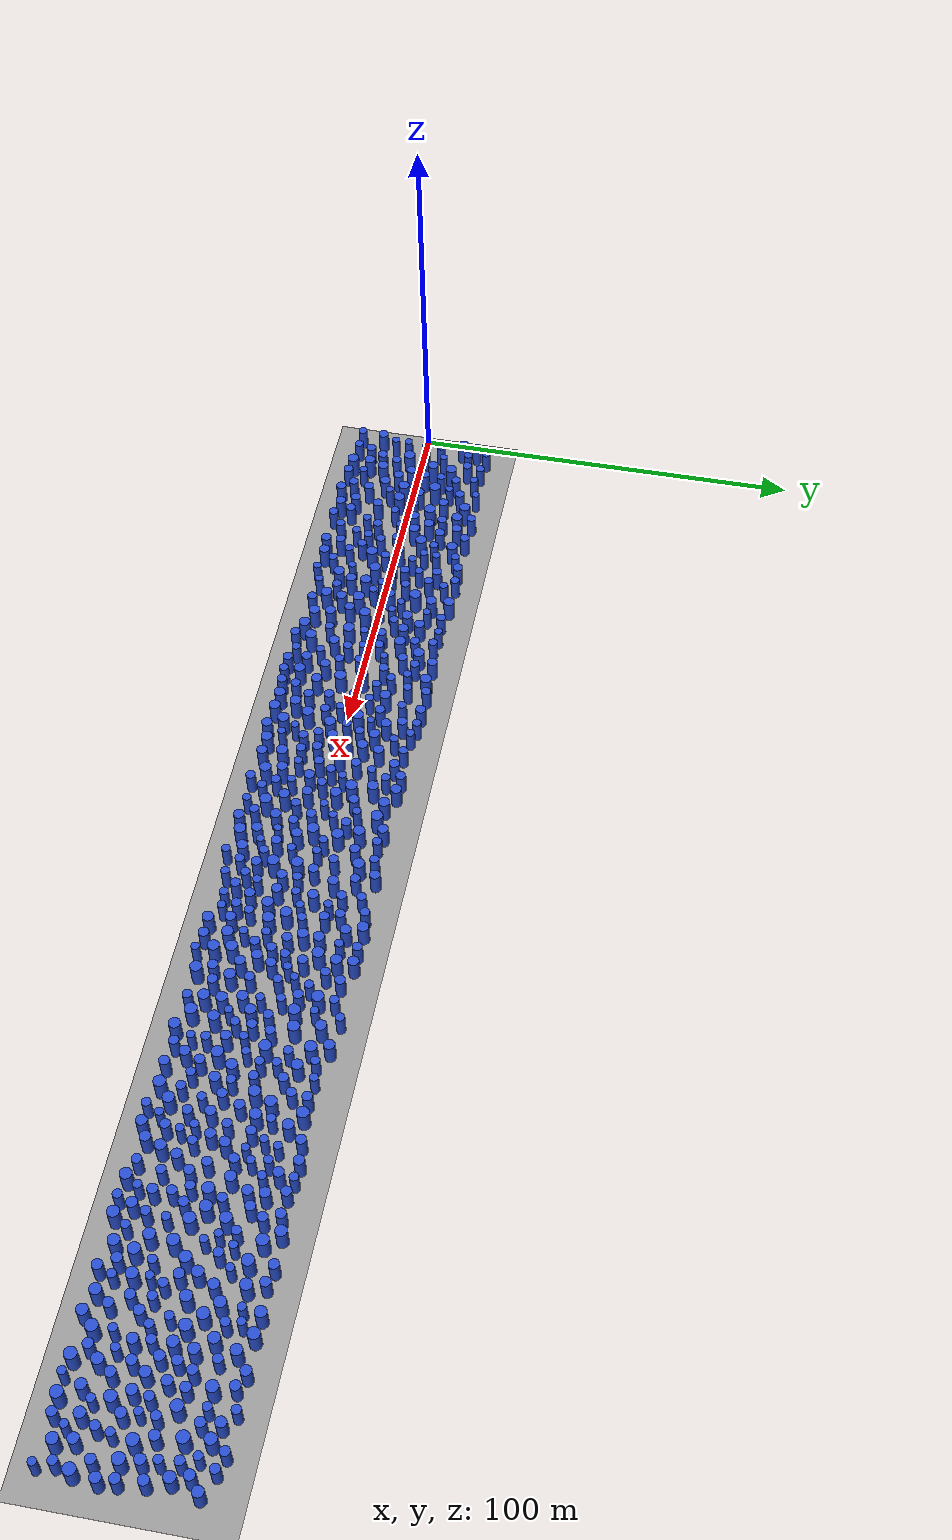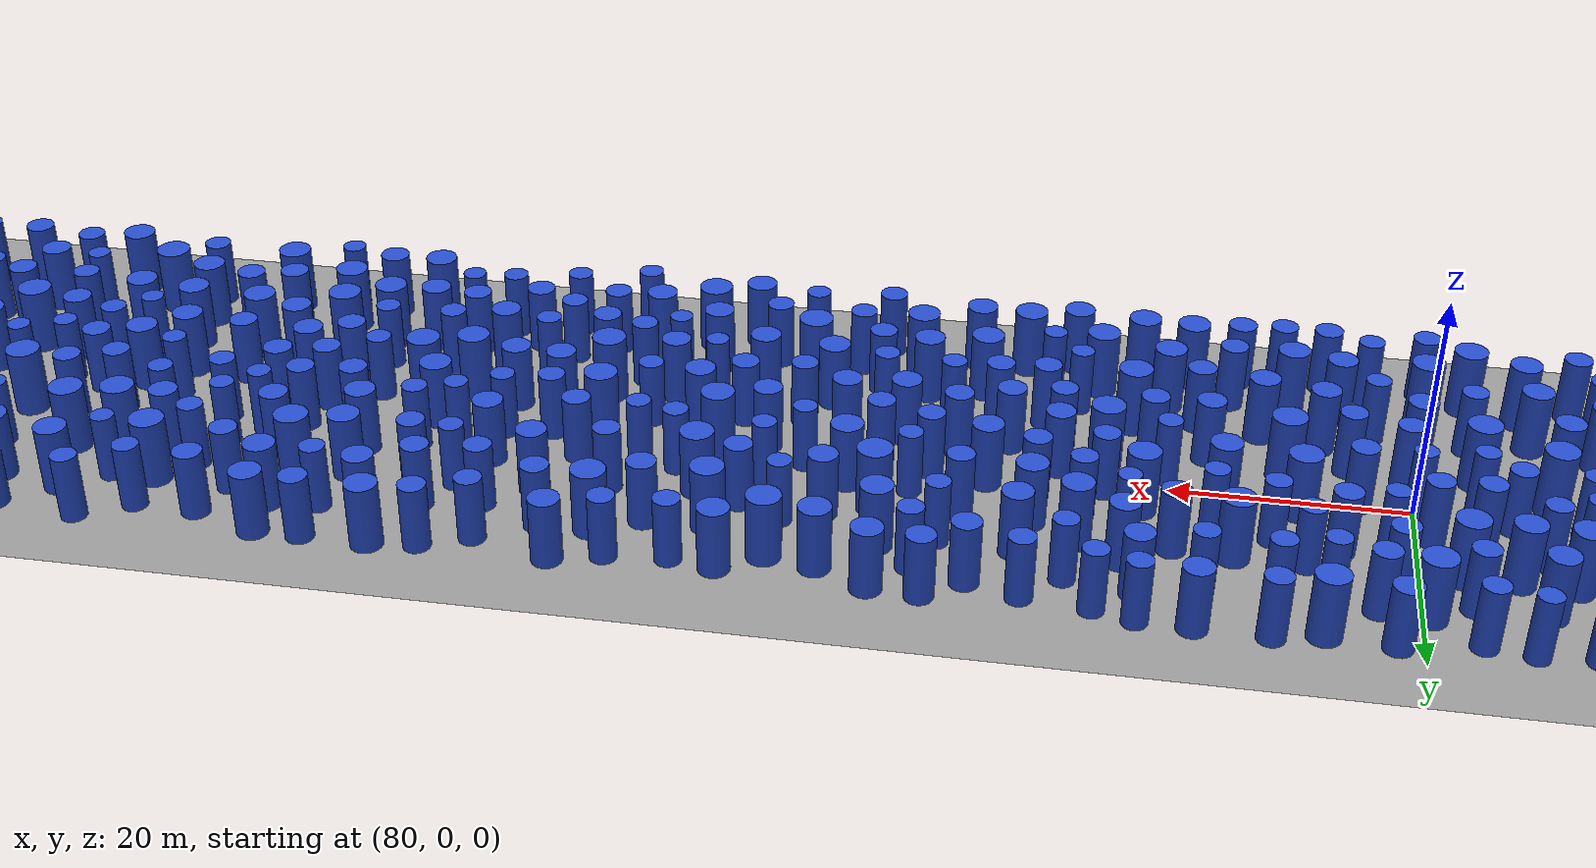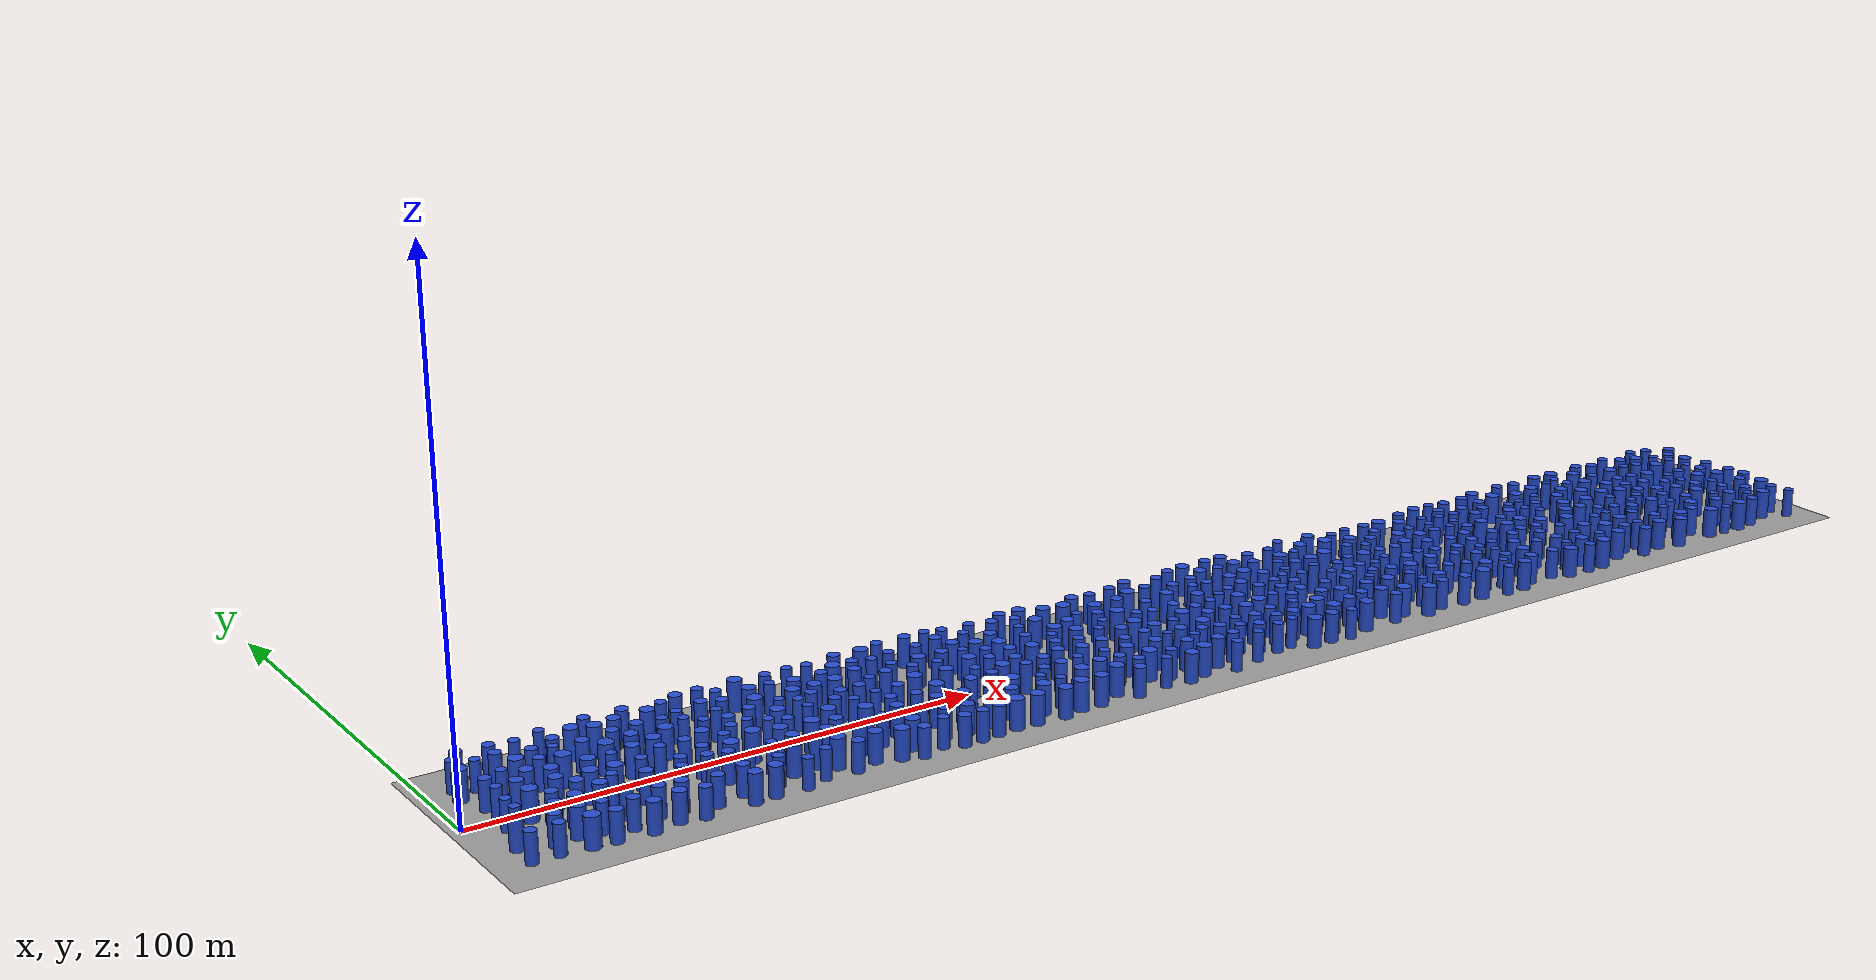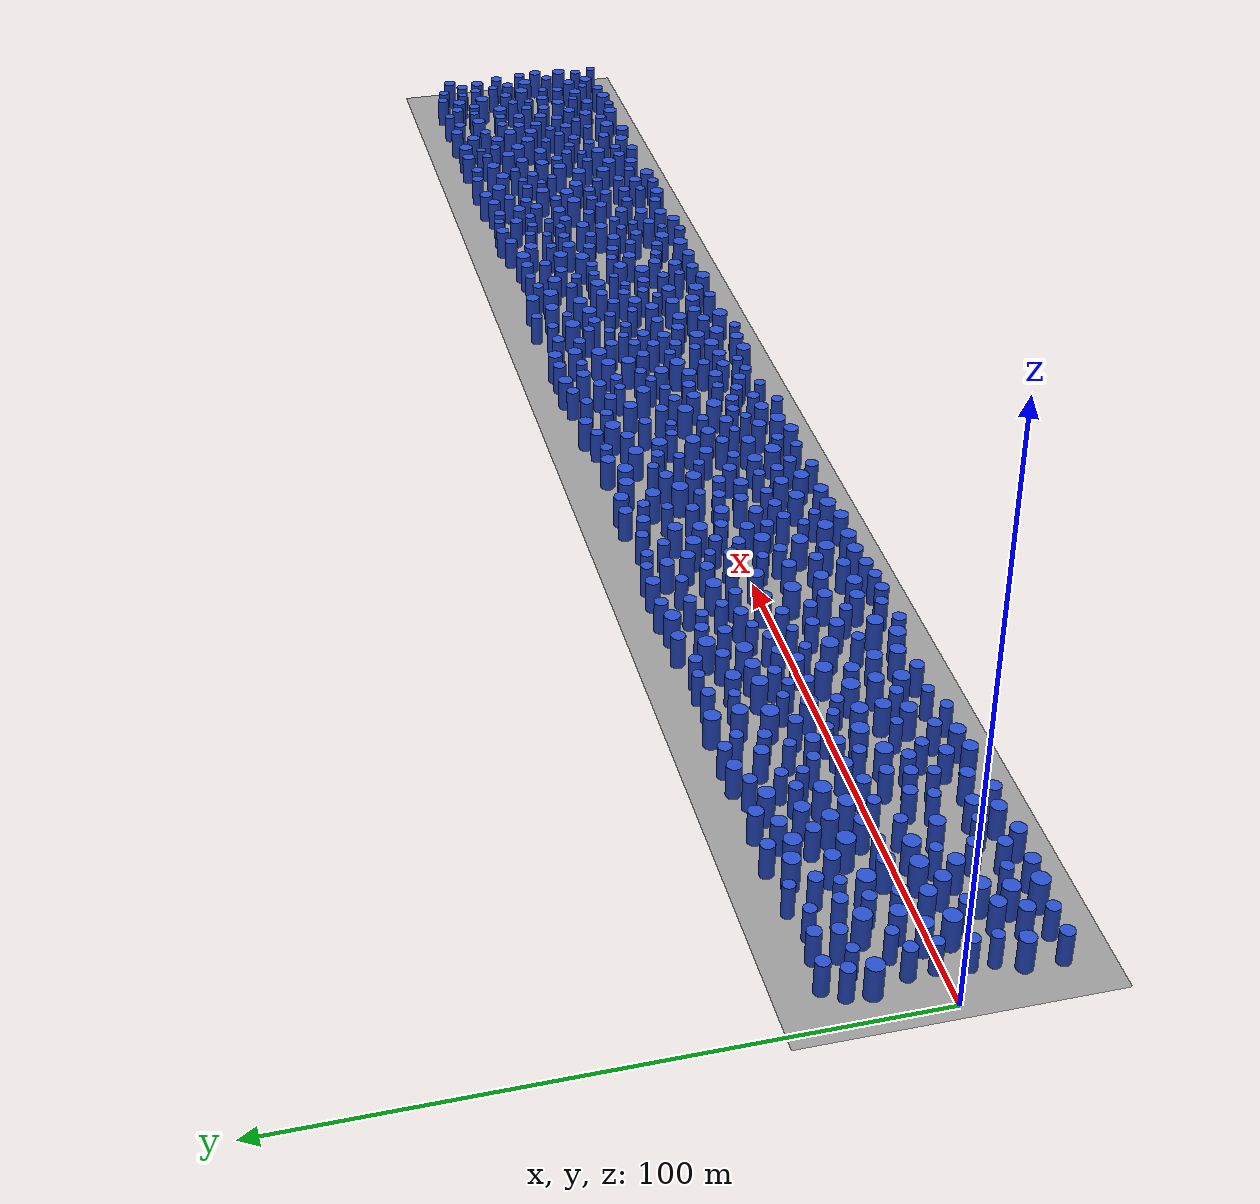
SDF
<sdf version="1.8">
 <world name="default">
  <plugin filename="gz-sim-physics-system" name="gz::sim::systems::Physics"/>
  <plugin filename="gz-sim-sensors-system" name="gz::sim::systems::Sensors">
   <render_engine>ogre2</render_engine>
  </plugin>
  <plugin filename="gz-sim-scene-broadcaster-system" name="gz::sim::systems::SceneBroadcaster"/>
  <plugin filename="gz-sim-user-commands-system" name="gz::sim::systems::UserCommands"/>
  <light name="light" type="directional">
   <pose>0 0 10 0 -0 0</pose>
   <diffuse>0.8 0.8 0.8 1</diffuse>
   <specular>0.2 0.2 0.2 1</specular>
   <attenuation>
    <range>1000</range>
    <constant>0.9</constant>
    <linear>0.01</linear>
    <quadratic>0.001</quadratic>
   </attenuation>
   <direction>-0.5 0.1 -0.9</direction>
   <spot><inner_angle>0</inner_angle><outer_angle>0</outer_angle><falloff>0</falloff></spot>
  </light>
  <gravity>0 0 -9.8</gravity>
  <magnetic_field>6e-06 2.3e-05 -4.2e-05</magnetic_field>
  <atmosphere type="adiabatic"/>
  <physics type="ode">
   <max_step_size>0.001</max_step_size>
   <real_time_factor>1</real_time_factor>
   <real_time_update_rate>1000</real_time_update_rate>
  </physics>
  <scene><ambient>0.4 0.4 0.4 1</ambient><background>0.7 0.7 0.7 1</background><shadows>1</shadows></scene>
  <audio><device>default</device></audio>
  <spherical_coordinates>
   <surface_model>EARTH_WGS84</surface_model>
   <latitude_deg>0</latitude_deg>
   <longitude_deg>0</longitude_deg>
   <elevation>0</elevation>
   <heading_deg>0</heading_deg>
  </spherical_coordinates>
  <model name="ground_plane_map">
   <static>1</static>
   <link name="link">
    <collision name="collision">
     <geometry><plane><normal>0 0 1</normal><size>310 50</size></plane></geometry>
     <surface>
      <contact>
       <collide_without_contact>0</collide_without_contact>
       <ode><kp>1000000.0</kp><kd>100.0</kd><max_vel>1.0</max_vel><min_depth>0.001</min_depth></ode>
      </contact>
      <friction><ode><mu>100</mu><mu2>50</mu2></ode></friction>
     </surface>
    </collision>
    <visual name="visual">
     <cast_shadows>0</cast_shadows>
     <geometry><plane><normal>0 0 1</normal><size>310 50</size></plane></geometry>
     <material>
      <script><uri>file://media/materials/scripts/gazebo.material</uri><name>Gazebo/Grey</name></script>
     </material>
    </visual>
   </link>
   <pose>153 0 0 0 -0 0</pose>
  </model>
  <model name="0">
   <static>1</static>
   <link name="link">
    <inertial>
     <mass>2</mass>
     <inertia><ixx>6.95079</ixx><ixy>0</ixy><ixz>0</ixz><iyy>6.95079</iyy><iyz>0</iyz><izz>1.90158</izz></inertia>
    </inertial>
    <collision name="collision">
     <geometry><cylinder><length>6</length><radius>1.37898</radius></cylinder></geometry>
     <surface><contact><collide_without_contact>1</collide_without_contact></contact></surface>
    </collision>
    <visual name="visual">
     <geometry><cylinder><length>6</length><radius>1.37898</radius></cylinder></geometry>
     <material>
      <script><uri>file://media/materials/scripts/gazebo.material</uri><name>Gazebo/Blue</name></script>
     </material>
    </visual>
    <gravity>0</gravity>
   </link>
   <pose>129.391 -8.97843 3 0 -0 0</pose>
  </model>
  <model name="1">
   <static>1</static>
   <link name="link">
    <inertial>
     <mass>2</mass>
     <inertia><ixx>6.72296</ixx><ixy>0</ixy><ixz>0</ixz><iyy>6.72296</iyy><iyz>0</iyz><izz>1.44593</izz></inertia>
    </inertial>
    <collision name="collision">
     <geometry><cylinder><length>6</length><radius>1.20247</radius></cylinder></geometry>
     <surface><contact><collide_without_contact>1</collide_without_contact></contact></surface>
    </collision>
    <visual name="visual">
     <geometry><cylinder><length>6</length><radius>1.20247</radius></cylinder></geometry>
     <material>
      <script><uri>file://media/materials/scripts/gazebo.material</uri><name>Gazebo/Blue</name></script>
     </material>
    </visual>
    <gravity>0</gravity>
   </link>
   <pose>237.457 -7.39447 3 0 -0 0</pose>
  </model>
  <model name="2">
   <static>1</static>
   <link name="link">
    <inertial>
     <mass>2</mass>
     <inertia><ixx>6.83423</ixx><ixy>0</ixy><ixz>0</ixz><iyy>6.83423</iyy><iyz>0</iyz><izz>1.66847</izz></inertia>
    </inertial>
    <collision name="collision">
     <geometry><cylinder><length>6</length><radius>1.29169</radius></cylinder></geometry>
     <surface><contact><collide_without_contact>1</collide_without_contact></contact></surface>
    </collision>
    <visual name="visual">
     <geometry><cylinder><length>6</length><radius>1.29169</radius></cylinder></geometry>
     <material>
      <script><uri>file://media/materials/scripts/gazebo.material</uri><name>Gazebo/Blue</name></script>
     </material>
    </visual>
    <gravity>0</gravity>
   </link>
   <pose>274.38 0.175366 3 0 -0 0</pose>
  </model>
  <model name="3">
   <static>1</static>
   <link name="link">
    <inertial>
     <mass>2</mass>
     <inertia><ixx>6.94931</ixx><ixy>0</ixy><ixz>0</ixz><iyy>6.94931</iyy><iyz>0</iyz><izz>1.89861</izz></inertia>
    </inertial>
    <collision name="collision">
     <geometry><cylinder><length>6</length><radius>1.3779</radius></cylinder></geometry>
     <surface><contact><collide_without_contact>1</collide_without_contact></contact></surface>
    </collision>
    <visual name="visual">
     <geometry><cylinder><length>6</length><radius>1.3779</radius></cylinder></geometry>
     <material>
      <script><uri>file://media/materials/scripts/gazebo.material</uri><name>Gazebo/Blue</name></script>
     </material>
    </visual>
    <gravity>0</gravity>
   </link>
   <pose>188.184 -9.29219 3 0 -0 0</pose>
  </model>
  <model name="4">
   <static>1</static>
   <link name="link">
    <inertial>
     <mass>2</mass>
     <inertia><ixx>7.11213</ixx><ixy>0</ixy><ixz>0</ixz><iyy>7.11213</iyy><iyz>0</iyz><izz>2.22425</izz></inertia>
    </inertial>
    <collision name="collision">
     <geometry><cylinder><length>6</length><radius>1.49139</radius></cylinder></geometry>
     <surface><contact><collide_without_contact>1</collide_without_contact></contact></surface>
    </collision>
    <visual name="visual">
     <geometry><cylinder><length>6</length><radius>1.49139</radius></cylinder></geometry>
     <material>
      <script><uri>file://media/materials/scripts/gazebo.material</uri><name>Gazebo/Blue</name></script>
     </material>
    </visual>
    <gravity>0</gravity>
   </link>
   <pose>245.14 14.8871 3 0 -0 0</pose>
  </model>
  <model name="5">
   <static>1</static>
   <link name="link">
    <inertial>
     <mass>2</mass>
     <inertia><ixx>6.9315</ixx><ixy>0</ixy><ixz>0</ixz><iyy>6.9315</iyy><iyz>0</iyz><izz>1.863</izz></inertia>
    </inertial>
    <collision name="collision">
     <geometry><cylinder><length>6</length><radius>1.36492</radius></cylinder></geometry>
     <surface><contact><collide_without_contact>1</collide_without_contact></contact></surface>
    </collision>
    <visual name="visual">
     <geometry><cylinder><length>6</length><radius>1.36492</radius></cylinder></geometry>
     <material>
      <script><uri>file://media/materials/scripts/gazebo.material</uri><name>Gazebo/Blue</name></script>
     </material>
    </visual>
    <gravity>0</gravity>
   </link>
   <pose>271.563 6.85711 3 0 -0 0</pose>
  </model>
  <model name="6">
   <static>1</static>
   <link name="link">
    <inertial>
     <mass>2</mass>
     <inertia><ixx>6.55162</ixx><ixy>0</ixy><ixz>0</ixz><iyy>6.55162</iyy><iyz>0</iyz><izz>1.10324</izz></inertia>
    </inertial>
    <collision name="collision">
     <geometry><cylinder><length>6</length><radius>1.05035</radius></cylinder></geometry>
     <surface><contact><collide_without_contact>1</collide_without_contact></contact></surface>
    </collision>
    <visual name="visual">
     <geometry><cylinder><length>6</length><radius>1.05035</radius></cylinder></geometry>
     <material>
      <script><uri>file://media/materials/scripts/gazebo.material</uri><name>Gazebo/Blue</name></script>
     </material>
    </visual>
    <gravity>0</gravity>
   </link>
   <pose>133.39 4.20254 3 0 -0 0</pose>
  </model>
  <model name="7">
   <static>1</static>
   <link name="link">
    <inertial>
     <mass>2</mass>
     <inertia><ixx>7.10009</ixx><ixy>0</ixy><ixz>0</ixz><iyy>7.10009</iyy><iyz>0</iyz><izz>2.20019</izz></inertia>
    </inertial>
    <collision name="collision">
     <geometry><cylinder><length>6</length><radius>1.4833</radius></cylinder></geometry>
     <surface><contact><collide_without_contact>1</collide_without_contact></contact></surface>
    </collision>
    <visual name="visual">
     <geometry><cylinder><length>6</length><radius>1.4833</radius></cylinder></geometry>
     <material>
      <script><uri>file://media/materials/scripts/gazebo.material</uri><name>Gazebo/Blue</name></script>
     </material>
    </visual>
    <gravity>0</gravity>
   </link>
   <pose>146.171 13.5287 3 0 -0 0</pose>
  </model>
  <model name="8">
   <static>1</static>
   <link name="link">
    <inertial>
     <mass>2</mass>
     <inertia><ixx>6.98352</ixx><ixy>0</ixy><ixz>0</ixz><iyy>6.98352</iyy><iyz>0</iyz><izz>1.96705</izz></inertia>
    </inertial>
    <collision name="collision">
     <geometry><cylinder><length>6</length><radius>1.40251</radius></cylinder></geometry>
     <surface><contact><collide_without_contact>1</collide_without_contact></contact></surface>
    </collision>
    <visual name="visual">
     <geometry><cylinder><length>6</length><radius>1.40251</radius></cylinder></geometry>
     <material>
      <script><uri>file://media/materials/scripts/gazebo.material</uri><name>Gazebo/Blue</name></script>
     </material>
    </visual>
    <gravity>0</gravity>
   </link>
   <pose>167.473 -18.0752 3 0 -0 0</pose>
  </model>
  <model name="9">
   <static>1</static>
   <link name="link">
    <inertial>
     <mass>2</mass>
     <inertia><ixx>6.71929</ixx><ixy>0</ixy><ixz>0</ixz><iyy>6.71929</iyy><iyz>0</iyz><izz>1.43859</izz></inertia>
    </inertial>
    <collision name="collision">
     <geometry><cylinder><length>6</length><radius>1.19941</radius></cylinder></geometry>
     <surface><contact><collide_without_contact>1</collide_without_contact></contact></surface>
    </collision>
    <visual name="visual">
     <geometry><cylinder><length>6</length><radius>1.19941</radius></cylinder></geometry>
     <material>
      <script><uri>file://media/materials/scripts/gazebo.material</uri><name>Gazebo/Blue</name></script>
     </material>
    </visual>
    <gravity>0</gravity>
   </link>
   <pose>249.674 6.32276 3 0 -0 0</pose>
  </model>
  <model name="10">
   <static>1</static>
   <link name="link">
    <inertial>
     <mass>2</mass>
     <inertia><ixx>6.77724</ixx><ixy>0</ixy><ixz>0</ixz><iyy>6.77724</iyy><iyz>0</iyz><izz>1.55448</izz></inertia>
    </inertial>
    <collision name="collision">
     <geometry><cylinder><length>6</length><radius>1.24679</radius></cylinder></geometry>
     <surface><contact><collide_without_contact>1</collide_without_contact></contact></surface>
    </collision>
    <visual name="visual">
     <geometry><cylinder><length>6</length><radius>1.24679</radius></cylinder></geometry>
     <material>
      <script><uri>file://media/materials/scripts/gazebo.material</uri><name>Gazebo/Blue</name></script>
     </material>
    </visual>
    <gravity>0</gravity>
   </link>
   <pose>262.364 -9.60499 3 0 -0 0</pose>
  </model>
  <model name="11">
   <static>1</static>
   <link name="link">
    <inertial>
     <mass>2</mass>
     <inertia><ixx>7.02995</ixx><ixy>0</ixy><ixz>0</ixz><iyy>7.02995</iyy><iyz>0</iyz><izz>2.0599</izz></inertia>
    </inertial>
    <collision name="collision">
     <geometry><cylinder><length>6</length><radius>1.43524</radius></cylinder></geometry>
     <surface><contact><collide_without_contact>1</collide_without_contact></contact></surface>
    </collision>
    <visual name="visual">
     <geometry><cylinder><length>6</length><radius>1.43524</radius></cylinder></geometry>
     <material>
      <script><uri>file://media/materials/scripts/gazebo.material</uri><name>Gazebo/Blue</name></script>
     </material>
    </visual>
    <gravity>0</gravity>
   </link>
   <pose>61.2069 2.50664 3 0 -0 0</pose>
  </model>
  <model name="12">
   <static>1</static>
   <link name="link">
    <inertial>
     <mass>2</mass>
     <inertia><ixx>7.10079</ixx><ixy>0</ixy><ixz>0</ixz><iyy>7.10079</iyy><iyz>0</iyz><izz>2.20157</izz></inertia>
    </inertial>
    <collision name="collision">
     <geometry><cylinder><length>6</length><radius>1.48377</radius></cylinder></geometry>
     <surface><contact><collide_without_contact>1</collide_without_contact></contact></surface>
    </collision>
    <visual name="visual">
     <geometry><cylinder><length>6</length><radius>1.48377</radius></cylinder></geometry>
     <material>
      <script><uri>file://media/materials/scripts/gazebo.material</uri><name>Gazebo/Blue</name></script>
     </material>
    </visual>
    <gravity>0</gravity>
   </link>
   <pose>243.054 -1.92681 3 0 -0 0</pose>
  </model>
  <model name="13">
   <static>1</static>
   <link name="link">
    <inertial>
     <mass>2</mass>
     <inertia><ixx>6.67283</ixx><ixy>0</ixy><ixz>0</ixz><iyy>6.67283</iyy><iyz>0</iyz><izz>1.34566</izz></inertia>
    </inertial>
    <collision name="collision">
     <geometry><cylinder><length>6</length><radius>1.16003</radius></cylinder></geometry>
     <surface><contact><collide_without_contact>1</collide_without_contact></contact></surface>
    </collision>
    <visual name="visual">
     <geometry><cylinder><length>6</length><radius>1.16003</radius></cylinder></geometry>
     <material>
      <script><uri>file://media/materials/scripts/gazebo.material</uri><name>Gazebo/Blue</name></script>
     </material>
    </visual>
    <gravity>0</gravity>
   </link>
   <pose>155.364 16.3092 3 0 -0 0</pose>
  </model>
  <model name="14">
   <static>1</static>
   <link name="link">
    <inertial>
     <mass>2</mass>
     <inertia><ixx>6.81362</ixx><ixy>0</ixy><ixz>0</ixz><iyy>6.81362</iyy><iyz>0</iyz><izz>1.62724</izz></inertia>
    </inertial>
    <collision name="collision">
     <geometry><cylinder><length>6</length><radius>1.27563</radius></cylinder></geometry>
     <surface><contact><collide_without_contact>1</collide_without_contact></contact></surface>
    </collision>
    <visual name="visual">
     <geometry><cylinder><length>6</length><radius>1.27563</radius></cylinder></geometry>
     <material>
      <script><uri>file://media/materials/scripts/gazebo.material</uri><name>Gazebo/Blue</name></script>
     </material>
    </visual>
    <gravity>0</gravity>
   </link>
   <pose>214.441 1.7766 3 0 -0 0</pose>
  </model>
  <model name="15">
   <static>1</static>
   <link name="link">
    <inertial>
     <mass>2</mass>
     <inertia><ixx>6.80663</ixx><ixy>0</ixy><ixz>0</ixz><iyy>6.80663</iyy><iyz>0</iyz><izz>1.61326</izz></inertia>
    </inertial>
    <collision name="collision">
     <geometry><cylinder><length>6</length><radius>1.27014</radius></cylinder></geometry>
     <surface><contact><collide_without_contact>1</collide_without_contact></contact></surface>
    </collision>
    <visual name="visual">
     <geometry><cylinder><length>6</length><radius>1.27014</radius></cylinder></geometry>
     <material>
      <script><uri>file://media/materials/scripts/gazebo.material</uri><name>Gazebo/Blue</name></script>
     </material>
    </visual>
    <gravity>0</gravity>
   </link>
   <pose>290.973 3.8653 3 0 -0 0</pose>
  </model>
  <model name="16">
   <static>1</static>
   <link name="link">
    <inertial>
     <mass>2</mass>
     <inertia><ixx>6.74725</ixx><ixy>0</ixy><ixz>0</ixz><iyy>6.74725</iyy><iyz>0</iyz><izz>1.49449</izz></inertia>
    </inertial>
    <collision name="collision">
     <geometry><cylinder><length>6</length><radius>1.22249</radius></cylinder></geometry>
     <surface><contact><collide_without_contact>1</collide_without_contact></contact></surface>
    </collision>
    <visual name="visual">
     <geometry><cylinder><length>6</length><radius>1.22249</radius></cylinder></geometry>
     <material>
      <script><uri>file://media/materials/scripts/gazebo.material</uri><name>Gazebo/Blue</name></script>
     </material>
    </visual>
    <gravity>0</gravity>
   </link>
   <pose>181.651 -4.32254 3 0 -0 0</pose>
  </model>
  <model name="17">
   <static>1</static>
   <link name="link">
    <inertial>
     <mass>2</mass>
     <inertia><ixx>6.6557</ixx><ixy>0</ixy><ixz>0</ixz><iyy>6.6557</iyy><iyz>0</iyz><izz>1.3114</izz></inertia>
    </inertial>
    <collision name="collision">
     <geometry><cylinder><length>6</length><radius>1.14516</radius></cylinder></geometry>
     <surface><contact><collide_without_contact>1</collide_without_contact></contact></surface>
    </collision>
    <visual name="visual">
     <geometry><cylinder><length>6</length><radius>1.14516</radius></cylinder></geometry>
     <material>
      <script><uri>file://media/materials/scripts/gazebo.material</uri><name>Gazebo/Blue</name></script>
     </material>
    </visual>
    <gravity>0</gravity>
   </link>
   <pose>60.5288 -11.8133 3 0 -0 0</pose>
  </model>
  <model name="18">
   <static>1</static>
   <link name="link">
    <inertial>
     <mass>2</mass>
     <inertia><ixx>6.88223</ixx><ixy>0</ixy><ixz>0</ixz><iyy>6.88223</iyy><iyz>0</iyz><izz>1.76446</izz></inertia>
    </inertial>
    <collision name="collision">
     <geometry><cylinder><length>6</length><radius>1.32833</radius></cylinder></geometry>
     <surface><contact><collide_without_contact>1</collide_without_contact></contact></surface>
    </collision>
    <visual name="visual">
     <geometry><cylinder><length>6</length><radius>1.32833</radius></cylinder></geometry>
     <material>
      <script><uri>file://media/materials/scripts/gazebo.material</uri><name>Gazebo/Blue</name></script>
     </material>
    </visual>
    <gravity>0</gravity>
   </link>
   <pose>146.022 -15.3173 3 0 -0 0</pose>
  </model>
  <model name="19">
   <static>1</static>
   <link name="link">
    <inertial>
     <mass>2</mass>
     <inertia><ixx>7.03448</ixx><ixy>0</ixy><ixz>0</ixz><iyy>7.03448</iyy><iyz>0</iyz><izz>2.06895</izz></inertia>
    </inertial>
    <collision name="collision">
     <geometry><cylinder><length>6</length><radius>1.43839</radius></cylinder></geometry>
     <surface><contact><collide_without_contact>1</collide_without_contact></contact></surface>
    </collision>
    <visual name="visual">
     <geometry><cylinder><length>6</length><radius>1.43839</radius></cylinder></geometry>
     <material>
      <script><uri>file://media/materials/scripts/gazebo.material</uri><name>Gazebo/Blue</name></script>
     </material>
    </visual>
    <gravity>0</gravity>
   </link>
   <pose>278.796 12.7132 3 0 -0 0</pose>
  </model>
  <model name="20">
   <static>1</static>
   <link name="link">
    <inertial>
     <mass>2</mass>
     <inertia><ixx>7.06805</ixx><ixy>0</ixy><ixz>0</ixz><iyy>7.06805</iyy><iyz>0</iyz><izz>2.1361</izz></inertia>
    </inertial>
    <collision name="collision">
     <geometry><cylinder><length>6</length><radius>1.46154</radius></cylinder></geometry>
     <surface><contact><collide_without_contact>1</collide_without_contact></contact></surface>
    </collision>
    <visual name="visual">
     <geometry><cylinder><length>6</length><radius>1.46154</radius></cylinder></geometry>
     <material>
      <script><uri>file://media/materials/scripts/gazebo.material</uri><name>Gazebo/Blue</name></script>
     </material>
    </visual>
    <gravity>0</gravity>
   </link>
   <pose>165.061 -4.03041 3 0 -0 0</pose>
  </model>
  <model name="21">
   <static>1</static>
   <link name="link">
    <inertial>
     <mass>2</mass>
     <inertia><ixx>6.64731</ixx><ixy>0</ixy><ixz>0</ixz><iyy>6.64731</iyy><iyz>0</iyz><izz>1.29463</izz></inertia>
    </inertial>
    <collision name="collision">
     <geometry><cylinder><length>6</length><radius>1.13782</radius></cylinder></geometry>
     <surface><contact><collide_without_contact>1</collide_without_contact></contact></surface>
    </collision>
    <visual name="visual">
     <geometry><cylinder><length>6</length><radius>1.13782</radius></cylinder></geometry>
     <material>
      <script><uri>file://media/materials/scripts/gazebo.material</uri><name>Gazebo/Blue</name></script>
     </material>
    </visual>
    <gravity>0</gravity>
   </link>
   <pose>286.906 3.00644 3 0 -0 0</pose>
  </model>
  <model name="22">
   <static>1</static>
   <link name="link">
    <inertial>
     <mass>2</mass>
     <inertia><ixx>6.88461</ixx><ixy>0</ixy><ixz>0</ixz><iyy>6.88461</iyy><iyz>0</iyz><izz>1.76923</izz></inertia>
    </inertial>
    <collision name="collision">
     <geometry><cylinder><length>6</length><radius>1.33012</radius></cylinder></geometry>
     <surface><contact><collide_without_contact>1</collide_without_contact></contact></surface>
    </collision>
    <visual name="visual">
     <geometry><cylinder><length>6</length><radius>1.33012</radius></cylinder></geometry>
     <material>
      <script><uri>file://media/materials/scripts/gazebo.material</uri><name>Gazebo/Blue</name></script>
     </material>
    </visual>
    <gravity>0</gravity>
   </link>
   <pose>300.557 15.5685 3 0 -0 0</pose>
  </model>
  <model name="23">
   <static>1</static>
   <link name="link">
    <inertial>
     <mass>2</mass>
     <inertia><ixx>6.54203</ixx><ixy>0</ixy><ixz>0</ixz><iyy>6.54203</iyy><iyz>0</iyz><izz>1.08407</izz></inertia>
    </inertial>
    <collision name="collision">
     <geometry><cylinder><length>6</length><radius>1.04119</radius></cylinder></geometry>
     <surface><contact><collide_without_contact>1</collide_without_contact></contact></surface>
    </collision>
    <visual name="visual">
     <geometry><cylinder><length>6</length><radius>1.04119</radius></cylinder></geometry>
     <material>
      <script><uri>file://media/materials/scripts/gazebo.material</uri><name>Gazebo/Blue</name></script>
     </material>
    </visual>
    <gravity>0</gravity>
   </link>
   <pose>186.6 -0.514004 3 0 -0 0</pose>
  </model>
  <model name="24">
   <static>1</static>
   <link name="link">
    <inertial>
     <mass>2</mass>
     <inertia><ixx>7.01181</ixx><ixy>0</ixy><ixz>0</ixz><iyy>7.01181</iyy><iyz>0</iyz><izz>2.02362</izz></inertia>
    </inertial>
    <collision name="collision">
     <geometry><cylinder><length>6</length><radius>1.42254</radius></cylinder></geometry>
     <surface><contact><collide_without_contact>1</collide_without_contact></contact></surface>
    </collision>
    <visual name="visual">
     <geometry><cylinder><length>6</length><radius>1.42254</radius></cylinder></geometry>
     <material>
      <script><uri>file://media/materials/scripts/gazebo.material</uri><name>Gazebo/Blue</name></script>
     </material>
    </visual>
    <gravity>0</gravity>
   </link>
   <pose>76.6418 8.60096 3 0 -0 0</pose>
  </model>
  <model name="25">
   <static>1</static>
   <link name="link">
    <inertial>
     <mass>2</mass>
     <inertia><ixx>6.61631</ixx><ixy>0</ixy><ixz>0</ixz><iyy>6.61631</iyy><iyz>0</iyz><izz>1.23261</izz></inertia>
    </inertial>
    <collision name="collision">
     <geometry><cylinder><length>6</length><radius>1.11023</radius></cylinder></geometry>
     <surface><contact><collide_without_contact>1</collide_without_contact></contact></surface>
    </collision>
    <visual name="visual">
     <geometry><cylinder><length>6</length><radius>1.11023</radius></cylinder></geometry>
     <material>
      <script><uri>file://media/materials/scripts/gazebo.material</uri><name>Gazebo/Blue</name></script>
     </material>
    </visual>
    <gravity>0</gravity>
   </link>
   <pose>247.072 -15.0889 3 0 -0 0</pose>
  </model>
  <model name="26">
   <static>1</static>
   <link name="link">
    <inertial>
     <mass>2</mass>
     <inertia><ixx>6.90968</ixx><ixy>0</ixy><ixz>0</ixz><iyy>6.90968</iyy><iyz>0</iyz><izz>1.81936</izz></inertia>
    </inertial>
    <collision name="collision">
     <geometry><cylinder><length>6</length><radius>1.34884</radius></cylinder></geometry>
     <surface><contact><collide_without_contact>1</collide_without_contact></contact></surface>
    </collision>
    <visual name="visual">
     <geometry><cylinder><length>6</length><radius>1.34884</radius></cylinder></geometry>
     <material>
      <script><uri>file://media/materials/scripts/gazebo.material</uri><name>Gazebo/Blue</name></script>
     </material>
    </visual>
    <gravity>0</gravity>
   </link>
   <pose>17.797 2.75537 3 0 -0 0</pose>
  </model>
  <model name="27">
   <static>1</static>
   <link name="link">
    <inertial>
     <mass>2</mass>
     <inertia><ixx>6.80277</ixx><ixy>0</ixy><ixz>0</ixz><iyy>6.80277</iyy><iyz>0</iyz><izz>1.60554</izz></inertia>
    </inertial>
    <collision name="collision">
     <geometry><cylinder><length>6</length><radius>1.2671</radius></cylinder></geometry>
     <surface><contact><collide_without_contact>1</collide_without_contact></contact></surface>
    </collision>
    <visual name="visual">
     <geometry><cylinder><length>6</length><radius>1.2671</radius></cylinder></geometry>
     <material>
      <script><uri>file://media/materials/scripts/gazebo.material</uri><name>Gazebo/Blue</name></script>
     </material>
    </visual>
    <gravity>0</gravity>
   </link>
   <pose>206.719 -17.7327 3 0 -0 0</pose>
  </model>
  <model name="28">
   <static>1</static>
   <link name="link">
    <inertial>
     <mass>2</mass>
     <inertia><ixx>6.84912</ixx><ixy>0</ixy><ixz>0</ixz><iyy>6.84912</iyy><iyz>0</iyz><izz>1.69825</izz></inertia>
    </inertial>
    <collision name="collision">
     <geometry><cylinder><length>6</length><radius>1.30317</radius></cylinder></geometry>
     <surface><contact><collide_without_contact>1</collide_without_contact></contact></surface>
    </collision>
    <visual name="visual">
     <geometry><cylinder><length>6</length><radius>1.30317</radius></cylinder></geometry>
     <material>
      <script><uri>file://media/materials/scripts/gazebo.material</uri><name>Gazebo/Blue</name></script>
     </material>
    </visual>
    <gravity>0</gravity>
   </link>
   <pose>175.588 -4.06808 3 0 -0 0</pose>
  </model>
  <model name="29">
   <static>1</static>
   <link name="link">
    <inertial>
     <mass>2</mass>
     <inertia><ixx>7.11043</ixx><ixy>0</ixy><ixz>0</ixz><iyy>7.11043</iyy><iyz>0</iyz><izz>2.22087</izz></inertia>
    </inertial>
    <collision name="collision">
     <geometry><cylinder><length>6</length><radius>1.49026</radius></cylinder></geometry>
     <surface><contact><collide_without_contact>1</collide_without_contact></contact></surface>
    </collision>
    <visual name="visual">
     <geometry><cylinder><length>6</length><radius>1.49026</radius></cylinder></geometry>
     <material>
      <script><uri>file://media/materials/scripts/gazebo.material</uri><name>Gazebo/Blue</name></script>
     </material>
    </visual>
    <gravity>0</gravity>
   </link>
   <pose>15.2994 -17.7088 3 0 -0 0</pose>
  </model>
  <model name="30">
   <static>1</static>
   <link name="link">
    <inertial>
     <mass>2</mass>
     <inertia><ixx>6.59676</ixx><ixy>0</ixy><ixz>0</ixz><iyy>6.59676</iyy><iyz>0</iyz><izz>1.19353</izz></inertia>
    </inertial>
    <collision name="collision">
     <geometry><cylinder><length>6</length><radius>1.09249</radius></cylinder></geometry>
     <surface><contact><collide_without_contact>1</collide_without_contact></contact></surface>
    </collision>
    <visual name="visual">
     <geometry><cylinder><length>6</length><radius>1.09249</radius></cylinder></geometry>
     <material>
      <script><uri>file://media/materials/scripts/gazebo.material</uri><name>Gazebo/Blue</name></script>
     </material>
    </visual>
    <gravity>0</gravity>
   </link>
   <pose>40.9903 -10.9446 3 0 -0 0</pose>
  </model>
  <model name="31">
   <static>1</static>
   <link name="link">
    <inertial>
     <mass>2</mass>
     <inertia><ixx>7.07822</ixx><ixy>0</ixy><ixz>0</ixz><iyy>7.07822</iyy><iyz>0</iyz><izz>2.15645</izz></inertia>
    </inertial>
    <collision name="collision">
     <geometry><cylinder><length>6</length><radius>1.46848</radius></cylinder></geometry>
     <surface><contact><collide_without_contact>1</collide_without_contact></contact></surface>
    </collision>
    <visual name="visual">
     <geometry><cylinder><length>6</length><radius>1.46848</radius></cylinder></geometry>
     <material>
      <script><uri>file://media/materials/scripts/gazebo.material</uri><name>Gazebo/Blue</name></script>
     </material>
    </visual>
    <gravity>0</gravity>
   </link>
   <pose>11.2363 -2.75679 3 0 -0 0</pose>
  </model>
  <model name="32">
   <static>1</static>
   <link name="link">
    <inertial>
     <mass>2</mass>
     <inertia><ixx>6.6384</ixx><ixy>0</ixy><ixz>0</ixz><iyy>6.6384</iyy><iyz>0</iyz><izz>1.27681</izz></inertia>
    </inertial>
    <collision name="collision">
     <geometry><cylinder><length>6</length><radius>1.12996</radius></cylinder></geometry>
     <surface><contact><collide_without_contact>1</collide_without_contact></contact></surface>
    </collision>
    <visual name="visual">
     <geometry><cylinder><length>6</length><radius>1.12996</radius></cylinder></geometry>
     <material>
      <script><uri>file://media/materials/scripts/gazebo.material</uri><name>Gazebo/Blue</name></script>
     </material>
    </visual>
    <gravity>0</gravity>
   </link>
   <pose>69.8797 5.54499 3 0 -0 0</pose>
  </model>
  <model name="33">
   <static>1</static>
   <link name="link">
    <inertial>
     <mass>2</mass>
     <inertia><ixx>6.59422</ixx><ixy>0</ixy><ixz>0</ixz><iyy>6.59422</iyy><iyz>0</iyz><izz>1.18845</izz></inertia>
    </inertial>
    <collision name="collision">
     <geometry><cylinder><length>6</length><radius>1.09016</radius></cylinder></geometry>
     <surface><contact><collide_without_contact>1</collide_without_contact></contact></surface>
    </collision>
    <visual name="visual">
     <geometry><cylinder><length>6</length><radius>1.09016</radius></cylinder></geometry>
     <material>
      <script><uri>file://media/materials/scripts/gazebo.material</uri><name>Gazebo/Blue</name></script>
     </material>
    </visual>
    <gravity>0</gravity>
   </link>
   <pose>154.083 -17.4206 3 0 -0 0</pose>
  </model>
  <model name="34">
   <static>1</static>
   <link name="link">
    <inertial>
     <mass>2</mass>
     <inertia><ixx>7.11619</ixx><ixy>0</ixy><ixz>0</ixz><iyy>7.11619</iyy><iyz>0</iyz><izz>2.23239</izz></inertia>
    </inertial>
    <collision name="collision">
     <geometry><cylinder><length>6</length><radius>1.49412</radius></cylinder></geometry>
     <surface><contact><collide_without_contact>1</collide_without_contact></contact></surface>
    </collision>
    <visual name="visual">
     <geometry><cylinder><length>6</length><radius>1.49412</radius></cylinder></geometry>
     <material>
      <script><uri>file://media/materials/scripts/gazebo.material</uri><name>Gazebo/Blue</name></script>
     </material>
    </visual>
    <gravity>0</gravity>
   </link>
   <pose>63.7051 -5.23512 3 0 -0 0</pose>
  </model>
  <model name="35">
   <static>1</static>
   <link name="link">
    <inertial>
     <mass>2</mass>
     <inertia><ixx>7.00701</ixx><ixy>0</ixy><ixz>0</ixz><iyy>7.00701</iyy><iyz>0</iyz><izz>2.01402</izz></inertia>
    </inertial>
    <collision name="collision">
     <geometry><cylinder><length>6</length><radius>1.41916</radius></cylinder></geometry>
     <surface><contact><collide_without_contact>1</collide_without_contact></contact></surface>
    </collision>
    <visual name="visual">
     <geometry><cylinder><length>6</length><radius>1.41916</radius></cylinder></geometry>
     <material>
      <script><uri>file://media/materials/scripts/gazebo.material</uri><name>Gazebo/Blue</name></script>
     </material>
    </visual>
    <gravity>0</gravity>
   </link>
   <pose>277.357 -12.2847 3 0 -0 0</pose>
  </model>
  <model name="36">
   <static>1</static>
   <link name="link">
    <inertial>
     <mass>2</mass>
     <inertia><ixx>7.10005</ixx><ixy>0</ixy><ixz>0</ixz><iyy>7.10005</iyy><iyz>0</iyz><izz>2.2001</izz></inertia>
    </inertial>
    <collision name="collision">
     <geometry><cylinder><length>6</length><radius>1.48327</radius></cylinder></geometry>
     <surface><contact><collide_without_contact>1</collide_without_contact></contact></surface>
    </collision>
    <visual name="visual">
     <geometry><cylinder><length>6</length><radius>1.48327</radius></cylinder></geometry>
     <material>
      <script><uri>file://media/materials/scripts/gazebo.material</uri><name>Gazebo/Blue</name></script>
     </material>
    </visual>
    <gravity>0</gravity>
   </link>
   <pose>21.7263 6.52536 3 0 -0 0</pose>
  </model>
  <model name="37">
   <static>1</static>
   <link name="link">
    <inertial>
     <mass>2</mass>
     <inertia><ixx>6.6858</ixx><ixy>0</ixy><ixz>0</ixz><iyy>6.6858</iyy><iyz>0</iyz><izz>1.37161</izz></inertia>
    </inertial>
    <collision name="collision">
     <geometry><cylinder><length>6</length><radius>1.17116</radius></cylinder></geometry>
     <surface><contact><collide_without_contact>1</collide_without_contact></contact></surface>
    </collision>
    <visual name="visual">
     <geometry><cylinder><length>6</length><radius>1.17116</radius></cylinder></geometry>
     <material>
      <script><uri>file://media/materials/scripts/gazebo.material</uri><name>Gazebo/Blue</name></script>
     </material>
    </visual>
    <gravity>0</gravity>
   </link>
   <pose>78.7902 3.64494 3 0 -0 0</pose>
  </model>
  <model name="38">
   <static>1</static>
   <link name="link">
    <inertial>
     <mass>2</mass>
     <inertia><ixx>6.59123</ixx><ixy>0</ixy><ixz>0</ixz><iyy>6.59123</iyy><iyz>0</iyz><izz>1.18246</izz></inertia>
    </inertial>
    <collision name="collision">
     <geometry><cylinder><length>6</length><radius>1.08741</radius></cylinder></geometry>
     <surface><contact><collide_without_contact>1</collide_without_contact></contact></surface>
    </collision>
    <visual name="visual">
     <geometry><cylinder><length>6</length><radius>1.08741</radius></cylinder></geometry>
     <material>
      <script><uri>file://media/materials/scripts/gazebo.material</uri><name>Gazebo/Blue</name></script>
     </material>
    </visual>
    <gravity>0</gravity>
   </link>
   <pose>144.549 -3.40785 3 0 -0 0</pose>
  </model>
  <model name="39">
   <static>1</static>
   <link name="link">
    <inertial>
     <mass>2</mass>
     <inertia><ixx>6.78663</ixx><ixy>0</ixy><ixz>0</ixz><iyy>6.78663</iyy><iyz>0</iyz><izz>1.57327</izz></inertia>
    </inertial>
    <collision name="collision">
     <geometry><cylinder><length>6</length><radius>1.2543</radius></cylinder></geometry>
     <surface><contact><collide_without_contact>1</collide_without_contact></contact></surface>
    </collision>
    <visual name="visual">
     <geometry><cylinder><length>6</length><radius>1.2543</radius></cylinder></geometry>
     <material>
      <script><uri>file://media/materials/scripts/gazebo.material</uri><name>Gazebo/Blue</name></script>
     </material>
    </visual>
    <gravity>0</gravity>
   </link>
   <pose>96.9068 -5.35558 3 0 -0 0</pose>
  </model>
  <model name="40">
   <static>1</static>
   <link name="link">
    <inertial>
     <mass>2</mass>
     <inertia><ixx>6.63334</ixx><ixy>0</ixy><ixz>0</ixz><iyy>6.63334</iyy><iyz>0</iyz><izz>1.26667</izz></inertia>
    </inertial>
    <collision name="collision">
     <geometry><cylinder><length>6</length><radius>1.12547</radius></cylinder></geometry>
     <surface><contact><collide_without_contact>1</collide_without_contact></contact></surface>
    </collision>
    <visual name="visual">
     <geometry><cylinder><length>6</length><radius>1.12547</radius></cylinder></geometry>
     <material>
      <script><uri>file://media/materials/scripts/gazebo.material</uri><name>Gazebo/Blue</name></script>
     </material>
    </visual>
    <gravity>0</gravity>
   </link>
   <pose>224.929 -6.194 3 0 -0 0</pose>
  </model>
  <model name="41">
   <static>1</static>
   <link name="link">
    <inertial>
     <mass>2</mass>
     <inertia><ixx>6.6503</ixx><ixy>0</ixy><ixz>0</ixz><iyy>6.6503</iyy><iyz>0</iyz><izz>1.30061</izz></inertia>
    </inertial>
    <collision name="collision">
     <geometry><cylinder><length>6</length><radius>1.14044</radius></cylinder></geometry>
     <surface><contact><collide_without_contact>1</collide_without_contact></contact></surface>
    </collision>
    <visual name="visual">
     <geometry><cylinder><length>6</length><radius>1.14044</radius></cylinder></geometry>
     <material>
      <script><uri>file://media/materials/scripts/gazebo.material</uri><name>Gazebo/Blue</name></script>
     </material>
    </visual>
    <gravity>0</gravity>
   </link>
   <pose>75.6319 17.0916 3 0 -0 0</pose>
  </model>
  <model name="42">
   <static>1</static>
   <link name="link">
    <inertial>
     <mass>2</mass>
     <inertia><ixx>6.6543</ixx><ixy>0</ixy><ixz>0</ixz><iyy>6.6543</iyy><iyz>0</iyz><izz>1.3086</izz></inertia>
    </inertial>
    <collision name="collision">
     <geometry><cylinder><length>6</length><radius>1.14394</radius></cylinder></geometry>
     <surface><contact><collide_without_contact>1</collide_without_contact></contact></surface>
    </collision>
    <visual name="visual">
     <geometry><cylinder><length>6</length><radius>1.14394</radius></cylinder></geometry>
     <material>
      <script><uri>file://media/materials/scripts/gazebo.material</uri><name>Gazebo/Blue</name></script>
     </material>
    </visual>
    <gravity>0</gravity>
   </link>
   <pose>111.082 16.8538 3 0 -0 0</pose>
  </model>
  <model name="43">
   <static>1</static>
   <link name="link">
    <inertial>
     <mass>2</mass>
     <inertia><ixx>6.85876</ixx><ixy>0</ixy><ixz>0</ixz><iyy>6.85876</iyy><iyz>0</iyz><izz>1.71751</izz></inertia>
    </inertial>
    <collision name="collision">
     <geometry><cylinder><length>6</length><radius>1.31054</radius></cylinder></geometry>
     <surface><contact><collide_without_contact>1</collide_without_contact></contact></surface>
    </collision>
    <visual name="visual">
     <geometry><cylinder><length>6</length><radius>1.31054</radius></cylinder></geometry>
     <material>
      <script><uri>file://media/materials/scripts/gazebo.material</uri><name>Gazebo/Blue</name></script>
     </material>
    </visual>
    <gravity>0</gravity>
   </link>
   <pose>217.121 -4.18579 3 0 -0 0</pose>
  </model>
  <model name="44">
   <static>1</static>
   <link name="link">
    <inertial>
     <mass>2</mass>
     <inertia><ixx>6.87836</ixx><ixy>0</ixy><ixz>0</ixz><iyy>6.87836</iyy><iyz>0</iyz><izz>1.75673</izz></inertia>
    </inertial>
    <collision name="collision">
     <geometry><cylinder><length>6</length><radius>1.32542</radius></cylinder></geometry>
     <surface><contact><collide_without_contact>1</collide_without_contact></contact></surface>
    </collision>
    <visual name="visual">
     <geometry><cylinder><length>6</length><radius>1.32542</radius></cylinder></geometry>
     <material>
      <script><uri>file://media/materials/scripts/gazebo.material</uri><name>Gazebo/Blue</name></script>
     </material>
    </visual>
    <gravity>0</gravity>
   </link>
   <pose>4.77864 -11.492 3 0 -0 0</pose>
  </model>
  <model name="45">
   <static>1</static>
   <link name="link">
    <inertial>
     <mass>2</mass>
     <inertia><ixx>6.62687</ixx><ixy>0</ixy><ixz>0</ixz><iyy>6.62687</iyy><iyz>0</iyz><izz>1.25375</izz></inertia>
    </inertial>
    <collision name="collision">
     <geometry><cylinder><length>6</length><radius>1.11971</radius></cylinder></geometry>
     <surface><contact><collide_without_contact>1</collide_without_contact></contact></surface>
    </collision>
    <visual name="visual">
     <geometry><cylinder><length>6</length><radius>1.11971</radius></cylinder></geometry>
     <material>
      <script><uri>file://media/materials/scripts/gazebo.material</uri><name>Gazebo/Blue</name></script>
     </material>
    </visual>
    <gravity>0</gravity>
   </link>
   <pose>193.912 -4.58232 3 0 -0 0</pose>
  </model>
  <model name="46">
   <static>1</static>
   <link name="link">
    <inertial>
     <mass>2</mass>
     <inertia><ixx>6.82443</ixx><ixy>0</ixy><ixz>0</ixz><iyy>6.82443</iyy><iyz>0</iyz><izz>1.64885</izz></inertia>
    </inertial>
    <collision name="collision">
     <geometry><cylinder><length>6</length><radius>1.28408</radius></cylinder></geometry>
     <surface><contact><collide_without_contact>1</collide_without_contact></contact></surface>
    </collision>
    <visual name="visual">
     <geometry><cylinder><length>6</length><radius>1.28408</radius></cylinder></geometry>
     <material>
      <script><uri>file://media/materials/scripts/gazebo.material</uri><name>Gazebo/Blue</name></script>
     </material>
    </visual>
    <gravity>0</gravity>
   </link>
   <pose>127.542 -3.65832 3 0 -0 0</pose>
  </model>
  <model name="47">
   <static>1</static>
   <link name="link">
    <inertial>
     <mass>2</mass>
     <inertia><ixx>6.73098</ixx><ixy>0</ixy><ixz>0</ixz><iyy>6.73098</iyy><iyz>0</iyz><izz>1.46195</izz></inertia>
    </inertial>
    <collision name="collision">
     <geometry><cylinder><length>6</length><radius>1.20911</radius></cylinder></geometry>
     <surface><contact><collide_without_contact>1</collide_without_contact></contact></surface>
    </collision>
    <visual name="visual">
     <geometry><cylinder><length>6</length><radius>1.20911</radius></cylinder></geometry>
     <material>
      <script><uri>file://media/materials/scripts/gazebo.material</uri><name>Gazebo/Blue</name></script>
     </material>
    </visual>
    <gravity>0</gravity>
   </link>
   <pose>201.267 -17.0328 3 0 -0 0</pose>
  </model>
  <model name="48">
   <static>1</static>
   <link name="link">
    <inertial>
     <mass>2</mass>
     <inertia><ixx>6.63801</ixx><ixy>0</ixy><ixz>0</ixz><iyy>6.63801</iyy><iyz>0</iyz><izz>1.27603</izz></inertia>
    </inertial>
    <collision name="collision">
     <geometry><cylinder><length>6</length><radius>1.12961</radius></cylinder></geometry>
     <surface><contact><collide_without_contact>1</collide_without_contact></contact></surface>
    </collision>
    <visual name="visual">
     <geometry><cylinder><length>6</length><radius>1.12961</radius></cylinder></geometry>
     <material>
      <script><uri>file://media/materials/scripts/gazebo.material</uri><name>Gazebo/Blue</name></script>
     </material>
    </visual>
    <gravity>0</gravity>
   </link>
   <pose>51.0793 1.04063 3 0 -0 0</pose>
  </model>
  <model name="49">
   <static>1</static>
   <link name="link">
    <inertial>
     <mass>2</mass>
     <inertia><ixx>6.8201</ixx><ixy>0</ixy><ixz>0</ixz><iyy>6.8201</iyy><iyz>0</iyz><izz>1.6402</izz></inertia>
    </inertial>
    <collision name="collision">
     <geometry><cylinder><length>6</length><radius>1.2807</radius></cylinder></geometry>
     <surface><contact><collide_without_contact>1</collide_without_contact></contact></surface>
    </collision>
    <visual name="visual">
     <geometry><cylinder><length>6</length><radius>1.2807</radius></cylinder></geometry>
     <material>
      <script><uri>file://media/materials/scripts/gazebo.material</uri><name>Gazebo/Blue</name></script>
     </material>
    </visual>
    <gravity>0</gravity>
   </link>
   <pose>228.991 14.3717 3 0 -0 0</pose>
  </model>
  <model name="50">
   <static>1</static>
   <link name="link">
    <inertial>
     <mass>2</mass>
     <inertia><ixx>6.6682</ixx><ixy>0</ixy><ixz>0</ixz><iyy>6.6682</iyy><iyz>0</iyz><izz>1.3364</izz></inertia>
    </inertial>
    <collision name="collision">
     <geometry><cylinder><length>6</length><radius>1.15603</radius></cylinder></geometry>
     <surface><contact><collide_without_contact>1</collide_without_contact></contact></surface>
    </collision>
    <visual name="visual">
     <geometry><cylinder><length>6</length><radius>1.15603</radius></cylinder></geometry>
     <material>
      <script><uri>file://media/materials/scripts/gazebo.material</uri><name>Gazebo/Blue</name></script>
     </material>
    </visual>
    <gravity>0</gravity>
   </link>
   <pose>264.638 11.7743 3 0 -0 0</pose>
  </model>
  <model name="51">
   <static>1</static>
   <link name="link">
    <inertial>
     <mass>2</mass>
     <inertia><ixx>7.12457</ixx><ixy>0</ixy><ixz>0</ixz><iyy>7.12457</iyy><iyz>0</iyz><izz>2.24913</izz></inertia>
    </inertial>
    <collision name="collision">
     <geometry><cylinder><length>6</length><radius>1.49971</radius></cylinder></geometry>
     <surface><contact><collide_without_contact>1</collide_without_contact></contact></surface>
    </collision>
    <visual name="visual">
     <geometry><cylinder><length>6</length><radius>1.49971</radius></cylinder></geometry>
     <material>
      <script><uri>file://media/materials/scripts/gazebo.material</uri><name>Gazebo/Blue</name></script>
     </material>
    </visual>
    <gravity>0</gravity>
   </link>
   <pose>192.527 -15.412 3 0 -0 0</pose>
  </model>
  <model name="52">
   <static>1</static>
   <link name="link">
    <inertial>
     <mass>2</mass>
     <inertia><ixx>7.11514</ixx><ixy>0</ixy><ixz>0</ixz><iyy>7.11514</iyy><iyz>0</iyz><izz>2.23028</izz></inertia>
    </inertial>
    <collision name="collision">
     <geometry><cylinder><length>6</length><radius>1.49341</radius></cylinder></geometry>
     <surface><contact><collide_without_contact>1</collide_without_contact></contact></surface>
    </collision>
    <visual name="visual">
     <geometry><cylinder><length>6</length><radius>1.49341</radius></cylinder></geometry>
     <material>
      <script><uri>file://media/materials/scripts/gazebo.material</uri><name>Gazebo/Blue</name></script>
     </material>
    </visual>
    <gravity>0</gravity>
   </link>
   <pose>123.838 6.60741 3 0 -0 0</pose>
  </model>
  <model name="53">
   <static>1</static>
   <link name="link">
    <inertial>
     <mass>2</mass>
     <inertia><ixx>6.61246</ixx><ixy>0</ixy><ixz>0</ixz><iyy>6.61246</iyy><iyz>0</iyz><izz>1.22492</izz></inertia>
    </inertial>
    <collision name="collision">
     <geometry><cylinder><length>6</length><radius>1.10676</radius></cylinder></geometry>
     <surface><contact><collide_without_contact>1</collide_without_contact></contact></surface>
    </collision>
    <visual name="visual">
     <geometry><cylinder><length>6</length><radius>1.10676</radius></cylinder></geometry>
     <material>
      <script><uri>file://media/materials/scripts/gazebo.material</uri><name>Gazebo/Blue</name></script>
     </material>
    </visual>
    <gravity>0</gravity>
   </link>
   <pose>217.716 -18.8042 3 0 -0 0</pose>
  </model>
  <model name="54">
   <static>1</static>
   <link name="link">
    <inertial>
     <mass>2</mass>
     <inertia><ixx>6.79907</ixx><ixy>0</ixy><ixz>0</ixz><iyy>6.79907</iyy><iyz>0</iyz><izz>1.59813</izz></inertia>
    </inertial>
    <collision name="collision">
     <geometry><cylinder><length>6</length><radius>1.26417</radius></cylinder></geometry>
     <surface><contact><collide_without_contact>1</collide_without_contact></contact></surface>
    </collision>
    <visual name="visual">
     <geometry><cylinder><length>6</length><radius>1.26417</radius></cylinder></geometry>
     <material>
      <script><uri>file://media/materials/scripts/gazebo.material</uri><name>Gazebo/Blue</name></script>
     </material>
    </visual>
    <gravity>0</gravity>
   </link>
   <pose>33.3522 -14.2803 3 0 -0 0</pose>
  </model>
  <model name="55">
   <static>1</static>
   <link name="link">
    <inertial>
     <mass>2</mass>
     <inertia><ixx>7.03224</ixx><ixy>0</ixy><ixz>0</ixz><iyy>7.03224</iyy><iyz>0</iyz><izz>2.06447</izz></inertia>
    </inertial>
    <collision name="collision">
     <geometry><cylinder><length>6</length><radius>1.43683</radius></cylinder></geometry>
     <surface><contact><collide_without_contact>1</collide_without_contact></contact></surface>
    </collision>
    <visual name="visual">
     <geometry><cylinder><length>6</length><radius>1.43683</radius></cylinder></geometry>
     <material>
      <script><uri>file://media/materials/scripts/gazebo.material</uri><name>Gazebo/Blue</name></script>
     </material>
    </visual>
    <gravity>0</gravity>
   </link>
   <pose>87.6271 17.7655 3 0 -0 0</pose>
  </model>
  <model name="56">
   <static>1</static>
   <link name="link">
    <inertial>
     <mass>2</mass>
     <inertia><ixx>7.01812</ixx><ixy>0</ixy><ixz>0</ixz><iyy>7.01812</iyy><iyz>0</iyz><izz>2.03624</izz></inertia>
    </inertial>
    <collision name="collision">
     <geometry><cylinder><length>6</length><radius>1.42697</radius></cylinder></geometry>
     <surface><contact><collide_without_contact>1</collide_without_contact></contact></surface>
    </collision>
    <visual name="visual">
     <geometry><cylinder><length>6</length><radius>1.42697</radius></cylinder></geometry>
     <material>
      <script><uri>file://media/materials/scripts/gazebo.material</uri><name>Gazebo/Blue</name></script>
     </material>
    </visual>
    <gravity>0</gravity>
   </link>
   <pose>122.304 -15.5514 3 0 -0 0</pose>
  </model>
  <model name="57">
   <static>1</static>
   <link name="link">
    <inertial>
     <mass>2</mass>
     <inertia><ixx>6.75214</ixx><ixy>0</ixy><ixz>0</ixz><iyy>6.75214</iyy><iyz>0</iyz><izz>1.50428</izz></inertia>
    </inertial>
    <collision name="collision">
     <geometry><cylinder><length>6</length><radius>1.22649</radius></cylinder></geometry>
     <surface><contact><collide_without_contact>1</collide_without_contact></contact></surface>
    </collision>
    <visual name="visual">
     <geometry><cylinder><length>6</length><radius>1.22649</radius></cylinder></geometry>
     <material>
      <script><uri>file://media/materials/scripts/gazebo.material</uri><name>Gazebo/Blue</name></script>
     </material>
    </visual>
    <gravity>0</gravity>
   </link>
   <pose>239.985 13.568 3 0 -0 0</pose>
  </model>
  <model name="58">
   <static>1</static>
   <link name="link">
    <inertial>
     <mass>2</mass>
     <inertia><ixx>6.79435</ixx><ixy>0</ixy><ixz>0</ixz><iyy>6.79435</iyy><iyz>0</iyz><izz>1.58869</izz></inertia>
    </inertial>
    <collision name="collision">
     <geometry><cylinder><length>6</length><radius>1.26043</radius></cylinder></geometry>
     <surface><contact><collide_without_contact>1</collide_without_contact></contact></surface>
    </collision>
    <visual name="visual">
     <geometry><cylinder><length>6</length><radius>1.26043</radius></cylinder></geometry>
     <material>
      <script><uri>file://media/materials/scripts/gazebo.material</uri><name>Gazebo/Blue</name></script>
     </material>
    </visual>
    <gravity>0</gravity>
   </link>
   <pose>197.855 -5.73232 3 0 -0 0</pose>
  </model>
  <model name="59">
   <static>1</static>
   <link name="link">
    <inertial>
     <mass>2</mass>
     <inertia><ixx>6.64889</ixx><ixy>0</ixy><ixz>0</ixz><iyy>6.64889</iyy><iyz>0</iyz><izz>1.29779</izz></inertia>
    </inertial>
    <collision name="collision">
     <geometry><cylinder><length>6</length><radius>1.1392</radius></cylinder></geometry>
     <surface><contact><collide_without_contact>1</collide_without_contact></contact></surface>
    </collision>
    <visual name="visual">
     <geometry><cylinder><length>6</length><radius>1.1392</radius></cylinder></geometry>
     <material>
      <script><uri>file://media/materials/scripts/gazebo.material</uri><name>Gazebo/Blue</name></script>
     </material>
    </visual>
    <gravity>0</gravity>
   </link>
   <pose>9.66918 -17.3269 3 0 -0 0</pose>
  </model>
  <model name="60">
   <static>1</static>
   <link name="link">
    <inertial>
     <mass>2</mass>
     <inertia><ixx>6.81815</ixx><ixy>0</ixy><ixz>0</ixz><iyy>6.81815</iyy><iyz>0</iyz><izz>1.6363</izz></inertia>
    </inertial>
    <collision name="collision">
     <geometry><cylinder><length>6</length><radius>1.27918</radius></cylinder></geometry>
     <surface><contact><collide_without_contact>1</collide_without_contact></contact></surface>
    </collision>
    <visual name="visual">
     <geometry><cylinder><length>6</length><radius>1.27918</radius></cylinder></geometry>
     <material>
      <script><uri>file://media/materials/scripts/gazebo.material</uri><name>Gazebo/Blue</name></script>
     </material>
    </visual>
    <gravity>0</gravity>
   </link>
   <pose>285.808 16.4159 3 0 -0 0</pose>
  </model>
  <model name="61">
   <static>1</static>
   <link name="link">
    <inertial>
     <mass>2</mass>
     <inertia><ixx>6.52122</ixx><ixy>0</ixy><ixz>0</ixz><iyy>6.52122</iyy><iyz>0</iyz><izz>1.04245</izz></inertia>
    </inertial>
    <collision name="collision">
     <geometry><cylinder><length>6</length><radius>1.021</radius></cylinder></geometry>
     <surface><contact><collide_without_contact>1</collide_without_contact></contact></surface>
    </collision>
    <visual name="visual">
     <geometry><cylinder><length>6</length><radius>1.021</radius></cylinder></geometry>
     <material>
      <script><uri>file://media/materials/scripts/gazebo.material</uri><name>Gazebo/Blue</name></script>
     </material>
    </visual>
    <gravity>0</gravity>
   </link>
   <pose>227.232 7.64189 3 0 -0 0</pose>
  </model>
  <model name="62">
   <static>1</static>
   <link name="link">
    <inertial>
     <mass>2</mass>
     <inertia><ixx>6.91961</ixx><ixy>0</ixy><ixz>0</ixz><iyy>6.91961</iyy><iyz>0</iyz><izz>1.83922</izz></inertia>
    </inertial>
    <collision name="collision">
     <geometry><cylinder><length>6</length><radius>1.35618</radius></cylinder></geometry>
     <surface><contact><collide_without_contact>1</collide_without_contact></contact></surface>
    </collision>
    <visual name="visual">
     <geometry><cylinder><length>6</length><radius>1.35618</radius></cylinder></geometry>
     <material>
      <script><uri>file://media/materials/scripts/gazebo.material</uri><name>Gazebo/Blue</name></script>
     </material>
    </visual>
    <gravity>0</gravity>
   </link>
   <pose>115.081 1.41427 3 0 -0 0</pose>
  </model>
  <model name="63">
   <static>1</static>
   <link name="link">
    <inertial>
     <mass>2</mass>
     <inertia><ixx>6.83665</ixx><ixy>0</ixy><ixz>0</ixz><iyy>6.83665</iyy><iyz>0</iyz><izz>1.6733</izz></inertia>
    </inertial>
    <collision name="collision">
     <geometry><cylinder><length>6</length><radius>1.29356</radius></cylinder></geometry>
     <surface><contact><collide_without_contact>1</collide_without_contact></contact></surface>
    </collision>
    <visual name="visual">
     <geometry><cylinder><length>6</length><radius>1.29356</radius></cylinder></geometry>
     <material>
      <script><uri>file://media/materials/scripts/gazebo.material</uri><name>Gazebo/Blue</name></script>
     </material>
    </visual>
    <gravity>0</gravity>
   </link>
   <pose>103.454 10.8356 3 0 -0 0</pose>
  </model>
  <model name="64">
   <static>1</static>
   <link name="link">
    <inertial>
     <mass>2</mass>
     <inertia><ixx>6.68343</ixx><ixy>0</ixy><ixz>0</ixz><iyy>6.68343</iyy><iyz>0</iyz><izz>1.36686</izz></inertia>
    </inertial>
    <collision name="collision">
     <geometry><cylinder><length>6</length><radius>1.16913</radius></cylinder></geometry>
     <surface><contact><collide_without_contact>1</collide_without_contact></contact></surface>
    </collision>
    <visual name="visual">
     <geometry><cylinder><length>6</length><radius>1.16913</radius></cylinder></geometry>
     <material>
      <script><uri>file://media/materials/scripts/gazebo.material</uri><name>Gazebo/Blue</name></script>
     </material>
    </visual>
    <gravity>0</gravity>
   </link>
   <pose>188.88 -17.2791 3 0 -0 0</pose>
  </model>
  <model name="65">
   <static>1</static>
   <link name="link">
    <inertial>
     <mass>2</mass>
     <inertia><ixx>7.11148</ixx><ixy>0</ixy><ixz>0</ixz><iyy>7.11148</iyy><iyz>0</iyz><izz>2.22295</izz></inertia>
    </inertial>
    <collision name="collision">
     <geometry><cylinder><length>6</length><radius>1.49096</radius></cylinder></geometry>
     <surface><contact><collide_without_contact>1</collide_without_contact></contact></surface>
    </collision>
    <visual name="visual">
     <geometry><cylinder><length>6</length><radius>1.49096</radius></cylinder></geometry>
     <material>
      <script><uri>file://media/materials/scripts/gazebo.material</uri><name>Gazebo/Blue</name></script>
     </material>
    </visual>
    <gravity>0</gravity>
   </link>
   <pose>90.4869 -3.8946 3 0 -0 0</pose>
  </model>
  <model name="66">
   <static>1</static>
   <link name="link">
    <inertial>
     <mass>2</mass>
     <inertia><ixx>6.65746</ixx><ixy>0</ixy><ixz>0</ixz><iyy>6.65746</iyy><iyz>0</iyz><izz>1.31493</izz></inertia>
    </inertial>
    <collision name="collision">
     <geometry><cylinder><length>6</length><radius>1.1467</radius></cylinder></geometry>
     <surface><contact><collide_without_contact>1</collide_without_contact></contact></surface>
    </collision>
    <visual name="visual">
     <geometry><cylinder><length>6</length><radius>1.1467</radius></cylinder></geometry>
     <material>
      <script><uri>file://media/materials/scripts/gazebo.material</uri><name>Gazebo/Blue</name></script>
     </material>
    </visual>
    <gravity>0</gravity>
   </link>
   <pose>146.47 -9.8148 3 0 -0 0</pose>
  </model>
  <model name="67">
   <static>1</static>
   <link name="link">
    <inertial>
     <mass>2</mass>
     <inertia><ixx>6.59382</ixx><ixy>0</ixy><ixz>0</ixz><iyy>6.59382</iyy><iyz>0</iyz><izz>1.18765</izz></inertia>
    </inertial>
    <collision name="collision">
     <geometry><cylinder><length>6</length><radius>1.08979</radius></cylinder></geometry>
     <surface><contact><collide_without_contact>1</collide_without_contact></contact></surface>
    </collision>
    <visual name="visual">
     <geometry><cylinder><length>6</length><radius>1.08979</radius></cylinder></geometry>
     <material>
      <script><uri>file://media/materials/scripts/gazebo.material</uri><name>Gazebo/Blue</name></script>
     </material>
    </visual>
    <gravity>0</gravity>
   </link>
   <pose>159.865 -16.2301 3 0 -0 0</pose>
  </model>
  <model name="68">
   <static>1</static>
   <link name="link">
    <inertial>
     <mass>2</mass>
     <inertia><ixx>6.67775</ixx><ixy>0</ixy><ixz>0</ixz><iyy>6.67775</iyy><iyz>0</iyz><izz>1.3555</izz></inertia>
    </inertial>
    <collision name="collision">
     <geometry><cylinder><length>6</length><radius>1.16426</radius></cylinder></geometry>
     <surface><contact><collide_without_contact>1</collide_without_contact></contact></surface>
    </collision>
    <visual name="visual">
     <geometry><cylinder><length>6</length><radius>1.16426</radius></cylinder></geometry>
     <material>
      <script><uri>file://media/materials/scripts/gazebo.material</uri><name>Gazebo/Blue</name></script>
     </material>
    </visual>
    <gravity>0</gravity>
   </link>
   <pose>127.615 -15.0912 3 0 -0 0</pose>
  </model>
  <model name="69">
   <static>1</static>
   <link name="link">
    <inertial>
     <mass>2</mass>
     <inertia><ixx>6.76509</ixx><ixy>0</ixy><ixz>0</ixz><iyy>6.76509</iyy><iyz>0</iyz><izz>1.53017</izz></inertia>
    </inertial>
    <collision name="collision">
     <geometry><cylinder><length>6</length><radius>1.237</radius></cylinder></geometry>
     <surface><contact><collide_without_contact>1</collide_without_contact></contact></surface>
    </collision>
    <visual name="visual">
     <geometry><cylinder><length>6</length><radius>1.237</radius></cylinder></geometry>
     <material>
      <script><uri>file://media/materials/scripts/gazebo.material</uri><name>Gazebo/Blue</name></script>
     </material>
    </visual>
    <gravity>0</gravity>
   </link>
   <pose>254.411 17.871 3 0 -0 0</pose>
  </model>
  <model name="70">
   <static>1</static>
   <link name="link">
    <inertial>
     <mass>2</mass>
     <inertia><ixx>6.76823</ixx><ixy>0</ixy><ixz>0</ixz><iyy>6.76823</iyy><iyz>0</iyz><izz>1.53647</izz></inertia>
    </inertial>
    <collision name="collision">
     <geometry><cylinder><length>6</length><radius>1.23954</radius></cylinder></geometry>
     <surface><contact><collide_without_contact>1</collide_without_contact></contact></surface>
    </collision>
    <visual name="visual">
     <geometry><cylinder><length>6</length><radius>1.23954</radius></cylinder></geometry>
     <material>
      <script><uri>file://media/materials/scripts/gazebo.material</uri><name>Gazebo/Blue</name></script>
     </material>
    </visual>
    <gravity>0</gravity>
   </link>
   <pose>212.384 -2.75646 3 0 -0 0</pose>
  </model>
  <model name="71">
   <static>1</static>
   <link name="link">
    <inertial>
     <mass>2</mass>
     <inertia><ixx>6.93486</ixx><ixy>0</ixy><ixz>0</ixz><iyy>6.93486</iyy><iyz>0</iyz><izz>1.86972</izz></inertia>
    </inertial>
    <collision name="collision">
     <geometry><cylinder><length>6</length><radius>1.36738</radius></cylinder></geometry>
     <surface><contact><collide_without_contact>1</collide_without_contact></contact></surface>
    </collision>
    <visual name="visual">
     <geometry><cylinder><length>6</length><radius>1.36738</radius></cylinder></geometry>
     <material>
      <script><uri>file://media/materials/scripts/gazebo.material</uri><name>Gazebo/Blue</name></script>
     </material>
    </visual>
    <gravity>0</gravity>
   </link>
   <pose>270.241 15.6398 3 0 -0 0</pose>
  </model>
  <model name="72">
   <static>1</static>
   <link name="link">
    <inertial>
     <mass>2</mass>
     <inertia><ixx>6.70542</ixx><ixy>0</ixy><ixz>0</ixz><iyy>6.70542</iyy><iyz>0</iyz><izz>1.41083</izz></inertia>
    </inertial>
    <collision name="collision">
     <geometry><cylinder><length>6</length><radius>1.18779</radius></cylinder></geometry>
     <surface><contact><collide_without_contact>1</collide_without_contact></contact></surface>
    </collision>
    <visual name="visual">
     <geometry><cylinder><length>6</length><radius>1.18779</radius></cylinder></geometry>
     <material>
      <script><uri>file://media/materials/scripts/gazebo.material</uri><name>Gazebo/Blue</name></script>
     </material>
    </visual>
    <gravity>0</gravity>
   </link>
   <pose>23.7818 -15.6266 3 0 -0 0</pose>
  </model>
  <model name="73">
   <static>1</static>
   <link name="link">
    <inertial>
     <mass>2</mass>
     <inertia><ixx>6.53105</ixx><ixy>0</ixy><ixz>0</ixz><iyy>6.53105</iyy><iyz>0</iyz><izz>1.06209</izz></inertia>
    </inertial>
    <collision name="collision">
     <geometry><cylinder><length>6</length><radius>1.03058</radius></cylinder></geometry>
     <surface><contact><collide_without_contact>1</collide_without_contact></contact></surface>
    </collision>
    <visual name="visual">
     <geometry><cylinder><length>6</length><radius>1.03058</radius></cylinder></geometry>
     <material>
      <script><uri>file://media/materials/scripts/gazebo.material</uri><name>Gazebo/Blue</name></script>
     </material>
    </visual>
    <gravity>0</gravity>
   </link>
   <pose>6.3697 -4.0288 3 0 -0 0</pose>
  </model>
  <model name="74">
   <static>1</static>
   <link name="link">
    <inertial>
     <mass>2</mass>
     <inertia><ixx>6.74942</ixx><ixy>0</ixy><ixz>0</ixz><iyy>6.74942</iyy><iyz>0</iyz><izz>1.49884</izz></inertia>
    </inertial>
    <collision name="collision">
     <geometry><cylinder><length>6</length><radius>1.22427</radius></cylinder></geometry>
     <surface><contact><collide_without_contact>1</collide_without_contact></contact></surface>
    </collision>
    <visual name="visual">
     <geometry><cylinder><length>6</length><radius>1.22427</radius></cylinder></geometry>
     <material>
      <script><uri>file://media/materials/scripts/gazebo.material</uri><name>Gazebo/Blue</name></script>
     </material>
    </visual>
    <gravity>0</gravity>
   </link>
   <pose>149.614 3.18769 3 0 -0 0</pose>
  </model>
  <model name="75">
   <static>1</static>
   <link name="link">
    <inertial>
     <mass>2</mass>
     <inertia><ixx>6.73389</ixx><ixy>0</ixy><ixz>0</ixz><iyy>6.73389</iyy><iyz>0</iyz><izz>1.46778</izz></inertia>
    </inertial>
    <collision name="collision">
     <geometry><cylinder><length>6</length><radius>1.21152</radius></cylinder></geometry>
     <surface><contact><collide_without_contact>1</collide_without_contact></contact></surface>
    </collision>
    <visual name="visual">
     <geometry><cylinder><length>6</length><radius>1.21152</radius></cylinder></geometry>
     <material>
      <script><uri>file://media/materials/scripts/gazebo.material</uri><name>Gazebo/Blue</name></script>
     </material>
    </visual>
    <gravity>0</gravity>
   </link>
   <pose>81.8543 10.4126 3 0 -0 0</pose>
  </model>
  <model name="76">
   <static>1</static>
   <link name="link">
    <inertial>
     <mass>2</mass>
     <inertia><ixx>6.69533</ixx><ixy>0</ixy><ixz>0</ixz><iyy>6.69533</iyy><iyz>0</iyz><izz>1.39065</izz></inertia>
    </inertial>
    <collision name="collision">
     <geometry><cylinder><length>6</length><radius>1.17926</radius></cylinder></geometry>
     <surface><contact><collide_without_contact>1</collide_without_contact></contact></surface>
    </collision>
    <visual name="visual">
     <geometry><cylinder><length>6</length><radius>1.17926</radius></cylinder></geometry>
     <material>
      <script><uri>file://media/materials/scripts/gazebo.material</uri><name>Gazebo/Blue</name></script>
     </material>
    </visual>
    <gravity>0</gravity>
   </link>
   <pose>23.186 13.6856 3 0 -0 0</pose>
  </model>
  <model name="77">
   <static>1</static>
   <link name="link">
    <inertial>
     <mass>2</mass>
     <inertia><ixx>7.05343</ixx><ixy>0</ixy><ixz>0</ixz><iyy>7.05343</iyy><iyz>0</iyz><izz>2.10687</izz></inertia>
    </inertial>
    <collision name="collision">
     <geometry><cylinder><length>6</length><radius>1.45151</radius></cylinder></geometry>
     <surface><contact><collide_without_contact>1</collide_without_contact></contact></surface>
    </collision>
    <visual name="visual">
     <geometry><cylinder><length>6</length><radius>1.45151</radius></cylinder></geometry>
     <material>
      <script><uri>file://media/materials/scripts/gazebo.material</uri><name>Gazebo/Blue</name></script>
     </material>
    </visual>
    <gravity>0</gravity>
   </link>
   <pose>138.624 6.56323 3 0 -0 0</pose>
  </model>
  <model name="78">
   <static>1</static>
   <link name="link">
    <inertial>
     <mass>2</mass>
     <inertia><ixx>6.71877</ixx><ixy>0</ixy><ixz>0</ixz><iyy>6.71877</iyy><iyz>0</iyz><izz>1.43755</izz></inertia>
    </inertial>
    <collision name="collision">
     <geometry><cylinder><length>6</length><radius>1.19898</radius></cylinder></geometry>
     <surface><contact><collide_without_contact>1</collide_without_contact></contact></surface>
    </collision>
    <visual name="visual">
     <geometry><cylinder><length>6</length><radius>1.19898</radius></cylinder></geometry>
     <material>
      <script><uri>file://media/materials/scripts/gazebo.material</uri><name>Gazebo/Blue</name></script>
     </material>
    </visual>
    <gravity>0</gravity>
   </link>
   <pose>65.8716 -17.2179 3 0 -0 0</pose>
  </model>
  <model name="79">
   <static>1</static>
   <link name="link">
    <inertial>
     <mass>2</mass>
     <inertia><ixx>6.61377</ixx><ixy>0</ixy><ixz>0</ixz><iyy>6.61377</iyy><iyz>0</iyz><izz>1.22755</izz></inertia>
    </inertial>
    <collision name="collision">
     <geometry><cylinder><length>6</length><radius>1.10795</radius></cylinder></geometry>
     <surface><contact><collide_without_contact>1</collide_without_contact></contact></surface>
    </collision>
    <visual name="visual">
     <geometry><cylinder><length>6</length><radius>1.10795</radius></cylinder></geometry>
     <material>
      <script><uri>file://media/materials/scripts/gazebo.material</uri><name>Gazebo/Blue</name></script>
     </material>
    </visual>
    <gravity>0</gravity>
   </link>
   <pose>47.69 -11.4119 3 0 -0 0</pose>
  </model>
  <model name="80">
   <static>1</static>
   <link name="link">
    <inertial>
     <mass>2</mass>
     <inertia><ixx>6.81051</ixx><ixy>0</ixy><ixz>0</ixz><iyy>6.81051</iyy><iyz>0</iyz><izz>1.62103</izz></inertia>
    </inertial>
    <collision name="collision">
     <geometry><cylinder><length>6</length><radius>1.2732</radius></cylinder></geometry>
     <surface><contact><collide_without_contact>1</collide_without_contact></contact></surface>
    </collision>
    <visual name="visual">
     <geometry><cylinder><length>6</length><radius>1.2732</radius></cylinder></geometry>
     <material>
      <script><uri>file://media/materials/scripts/gazebo.material</uri><name>Gazebo/Blue</name></script>
     </material>
    </visual>
    <gravity>0</gravity>
   </link>
   <pose>49.2882 18.3032 3 0 -0 0</pose>
  </model>
  <model name="81">
   <static>1</static>
   <link name="link">
    <inertial>
     <mass>2</mass>
     <inertia><ixx>6.57695</ixx><ixy>0</ixy><ixz>0</ixz><iyy>6.57695</iyy><iyz>0</iyz><izz>1.15391</izz></inertia>
    </inertial>
    <collision name="collision">
     <geometry><cylinder><length>6</length><radius>1.0742</radius></cylinder></geometry>
     <surface><contact><collide_without_contact>1</collide_without_contact></contact></surface>
    </collision>
    <visual name="visual">
     <geometry><cylinder><length>6</length><radius>1.0742</radius></cylinder></geometry>
     <material>
      <script><uri>file://media/materials/scripts/gazebo.material</uri><name>Gazebo/Blue</name></script>
     </material>
    </visual>
    <gravity>0</gravity>
   </link>
   <pose>265.486 -0.173893 3 0 -0 0</pose>
  </model>
  <model name="82">
   <static>1</static>
   <link name="link">
    <inertial>
     <mass>2</mass>
     <inertia><ixx>6.67423</ixx><ixy>0</ixy><ixz>0</ixz><iyy>6.67423</iyy><iyz>0</iyz><izz>1.34846</izz></inertia>
    </inertial>
    <collision name="collision">
     <geometry><cylinder><length>6</length><radius>1.16123</radius></cylinder></geometry>
     <surface><contact><collide_without_contact>1</collide_without_contact></contact></surface>
    </collision>
    <visual name="visual">
     <geometry><cylinder><length>6</length><radius>1.16123</radius></cylinder></geometry>
     <material>
      <script><uri>file://media/materials/scripts/gazebo.material</uri><name>Gazebo/Blue</name></script>
     </material>
    </visual>
    <gravity>0</gravity>
   </link>
   <pose>152.536 -0.050993 3 0 -0 0</pose>
  </model>
  <model name="83">
   <static>1</static>
   <link name="link">
    <inertial>
     <mass>2</mass>
     <inertia><ixx>6.6061</ixx><ixy>0</ixy><ixz>0</ixz><iyy>6.6061</iyy><iyz>0</iyz><izz>1.21219</izz></inertia>
    </inertial>
    <collision name="collision">
     <geometry><cylinder><length>6</length><radius>1.101</radius></cylinder></geometry>
     <surface><contact><collide_without_contact>1</collide_without_contact></contact></surface>
    </collision>
    <visual name="visual">
     <geometry><cylinder><length>6</length><radius>1.101</radius></cylinder></geometry>
     <material>
      <script><uri>file://media/materials/scripts/gazebo.material</uri><name>Gazebo/Blue</name></script>
     </material>
    </visual>
    <gravity>0</gravity>
   </link>
   <pose>105.418 17.4841 3 0 -0 0</pose>
  </model>
  <model name="84">
   <static>1</static>
   <link name="link">
    <inertial>
     <mass>2</mass>
     <inertia><ixx>6.99272</ixx><ixy>0</ixy><ixz>0</ixz><iyy>6.99272</iyy><iyz>0</iyz><izz>1.98545</izz></inertia>
    </inertial>
    <collision name="collision">
     <geometry><cylinder><length>6</length><radius>1.40906</radius></cylinder></geometry>
     <surface><contact><collide_without_contact>1</collide_without_contact></contact></surface>
    </collision>
    <visual name="visual">
     <geometry><cylinder><length>6</length><radius>1.40906</radius></cylinder></geometry>
     <material>
      <script><uri>file://media/materials/scripts/gazebo.material</uri><name>Gazebo/Blue</name></script>
     </material>
    </visual>
    <gravity>0</gravity>
   </link>
   <pose>14.9496 -13.0744 3 0 -0 0</pose>
  </model>
  <model name="85">
   <static>1</static>
   <link name="link">
    <inertial>
     <mass>2</mass>
     <inertia><ixx>6.96895</ixx><ixy>0</ixy><ixz>0</ixz><iyy>6.96895</iyy><iyz>0</iyz><izz>1.9379</izz></inertia>
    </inertial>
    <collision name="collision">
     <geometry><cylinder><length>6</length><radius>1.39208</radius></cylinder></geometry>
     <surface><contact><collide_without_contact>1</collide_without_contact></contact></surface>
    </collision>
    <visual name="visual">
     <geometry><cylinder><length>6</length><radius>1.39208</radius></cylinder></geometry>
     <material>
      <script><uri>file://media/materials/scripts/gazebo.material</uri><name>Gazebo/Blue</name></script>
     </material>
    </visual>
    <gravity>0</gravity>
   </link>
   <pose>254.747 3.08699 3 0 -0 0</pose>
  </model>
  <model name="86">
   <static>1</static>
   <link name="link">
    <inertial>
     <mass>2</mass>
     <inertia><ixx>6.98494</ixx><ixy>0</ixy><ixz>0</ixz><iyy>6.98494</iyy><iyz>0</iyz><izz>1.96989</izz></inertia>
    </inertial>
    <collision name="collision">
     <geometry><cylinder><length>6</length><radius>1.40353</radius></cylinder></geometry>
     <surface><contact><collide_without_contact>1</collide_without_contact></contact></surface>
    </collision>
    <visual name="visual">
     <geometry><cylinder><length>6</length><radius>1.40353</radius></cylinder></geometry>
     <material>
      <script><uri>file://media/materials/scripts/gazebo.material</uri><name>Gazebo/Blue</name></script>
     </material>
    </visual>
    <gravity>0</gravity>
   </link>
   <pose>262.633 -17.1305 3 0 -0 0</pose>
  </model>
  <model name="87">
   <static>1</static>
   <link name="link">
    <inertial>
     <mass>2</mass>
     <inertia><ixx>6.52052</ixx><ixy>0</ixy><ixz>0</ixz><iyy>6.52052</iyy><iyz>0</iyz><izz>1.04104</izz></inertia>
    </inertial>
    <collision name="collision">
     <geometry><cylinder><length>6</length><radius>1.02032</radius></cylinder></geometry>
     <surface><contact><collide_without_contact>1</collide_without_contact></contact></surface>
    </collision>
    <visual name="visual">
     <geometry><cylinder><length>6</length><radius>1.02032</radius></cylinder></geometry>
     <material>
      <script><uri>file://media/materials/scripts/gazebo.material</uri><name>Gazebo/Blue</name></script>
     </material>
    </visual>
    <gravity>0</gravity>
   </link>
   <pose>8.57467 13.0563 3 0 -0 0</pose>
  </model>
  <model name="88">
   <static>1</static>
   <link name="link">
    <inertial>
     <mass>2</mass>
     <inertia><ixx>6.58357</ixx><ixy>0</ixy><ixz>0</ixz><iyy>6.58357</iyy><iyz>0</iyz><izz>1.16715</izz></inertia>
    </inertial>
    <collision name="collision">
     <geometry><cylinder><length>6</length><radius>1.08035</radius></cylinder></geometry>
     <surface><contact><collide_without_contact>1</collide_without_contact></contact></surface>
    </collision>
    <visual name="visual">
     <geometry><cylinder><length>6</length><radius>1.08035</radius></cylinder></geometry>
     <material>
      <script><uri>file://media/materials/scripts/gazebo.material</uri><name>Gazebo/Blue</name></script>
     </material>
    </visual>
    <gravity>0</gravity>
   </link>
   <pose>48.4046 5.9061 3 0 -0 0</pose>
  </model>
  <model name="89">
   <static>1</static>
   <link name="link">
    <inertial>
     <mass>2</mass>
     <inertia><ixx>6.78438</ixx><ixy>0</ixy><ixz>0</ixz><iyy>6.78438</iyy><iyz>0</iyz><izz>1.56876</izz></inertia>
    </inertial>
    <collision name="collision">
     <geometry><cylinder><length>6</length><radius>1.2525</radius></cylinder></geometry>
     <surface><contact><collide_without_contact>1</collide_without_contact></contact></surface>
    </collision>
    <visual name="visual">
     <geometry><cylinder><length>6</length><radius>1.2525</radius></cylinder></geometry>
     <material>
      <script><uri>file://media/materials/scripts/gazebo.material</uri><name>Gazebo/Blue</name></script>
     </material>
    </visual>
    <gravity>0</gravity>
   </link>
   <pose>174.977 6.69553 3 0 -0 0</pose>
  </model>
  <model name="90">
   <static>1</static>
   <link name="link">
    <inertial>
     <mass>2</mass>
     <inertia><ixx>6.95071</ixx><ixy>0</ixy><ixz>0</ixz><iyy>6.95071</iyy><iyz>0</iyz><izz>1.90143</izz></inertia>
    </inertial>
    <collision name="collision">
     <geometry><cylinder><length>6</length><radius>1.37892</radius></cylinder></geometry>
     <surface><contact><collide_without_contact>1</collide_without_contact></contact></surface>
    </collision>
    <visual name="visual">
     <geometry><cylinder><length>6</length><radius>1.37892</radius></cylinder></geometry>
     <material>
      <script><uri>file://media/materials/scripts/gazebo.material</uri><name>Gazebo/Blue</name></script>
     </material>
    </visual>
    <gravity>0</gravity>
   </link>
   <pose>298.807 9.19752 3 0 -0 0</pose>
  </model>
  <model name="91">
   <static>1</static>
   <link name="link">
    <inertial>
     <mass>2</mass>
     <inertia><ixx>6.60836</ixx><ixy>0</ixy><ixz>0</ixz><iyy>6.60836</iyy><iyz>0</iyz><izz>1.21672</izz></inertia>
    </inertial>
    <collision name="collision">
     <geometry><cylinder><length>6</length><radius>1.10305</radius></cylinder></geometry>
     <surface><contact><collide_without_contact>1</collide_without_contact></contact></surface>
    </collision>
    <visual name="visual">
     <geometry><cylinder><length>6</length><radius>1.10305</radius></cylinder></geometry>
     <material>
      <script><uri>file://media/materials/scripts/gazebo.material</uri><name>Gazebo/Blue</name></script>
     </material>
    </visual>
    <gravity>0</gravity>
   </link>
   <pose>163.547 3.72702 3 0 -0 0</pose>
  </model>
  <model name="92">
   <static>1</static>
   <link name="link">
    <inertial>
     <mass>2</mass>
     <inertia><ixx>6.77017</ixx><ixy>0</ixy><ixz>0</ixz><iyy>6.77017</iyy><iyz>0</iyz><izz>1.54035</izz></inertia>
    </inertial>
    <collision name="collision">
     <geometry><cylinder><length>6</length><radius>1.24111</radius></cylinder></geometry>
     <surface><contact><collide_without_contact>1</collide_without_contact></contact></surface>
    </collision>
    <visual name="visual">
     <geometry><cylinder><length>6</length><radius>1.24111</radius></cylinder></geometry>
     <material>
      <script><uri>file://media/materials/scripts/gazebo.material</uri><name>Gazebo/Blue</name></script>
     </material>
    </visual>
    <gravity>0</gravity>
   </link>
   <pose>239.59 -4.18065 3 0 -0 0</pose>
  </model>
  <model name="93">
   <static>1</static>
   <link name="link">
    <inertial>
     <mass>2</mass>
     <inertia><ixx>7.01625</ixx><ixy>0</ixy><ixz>0</ixz><iyy>7.01625</iyy><iyz>0</iyz><izz>2.0325</izz></inertia>
    </inertial>
    <collision name="collision">
     <geometry><cylinder><length>6</length><radius>1.42566</radius></cylinder></geometry>
     <surface><contact><collide_without_contact>1</collide_without_contact></contact></surface>
    </collision>
    <visual name="visual">
     <geometry><cylinder><length>6</length><radius>1.42566</radius></cylinder></geometry>
     <material>
      <script><uri>file://media/materials/scripts/gazebo.material</uri><name>Gazebo/Blue</name></script>
     </material>
    </visual>
    <gravity>0</gravity>
   </link>
   <pose>241.568 5.83177 3 0 -0 0</pose>
  </model>
  <model name="94">
   <static>1</static>
   <link name="link">
    <inertial>
     <mass>2</mass>
     <inertia><ixx>6.59512</ixx><ixy>0</ixy><ixz>0</ixz><iyy>6.59512</iyy><iyz>0</iyz><izz>1.19025</izz></inertia>
    </inertial>
    <collision name="collision">
     <geometry><cylinder><length>6</length><radius>1.09098</radius></cylinder></geometry>
     <surface><contact><collide_without_contact>1</collide_without_contact></contact></surface>
    </collision>
    <visual name="visual">
     <geometry><cylinder><length>6</length><radius>1.09098</radius></cylinder></geometry>
     <material>
      <script><uri>file://media/materials/scripts/gazebo.material</uri><name>Gazebo/Blue</name></script>
     </material>
    </visual>
    <gravity>0</gravity>
   </link>
   <pose>155.042 -9.28586 3 0 -0 0</pose>
  </model>
  <model name="95">
   <static>1</static>
   <link name="link">
    <inertial>
     <mass>2</mass>
     <inertia><ixx>7.02237</ixx><ixy>0</ixy><ixz>0</ixz><iyy>7.02237</iyy><iyz>0</iyz><izz>2.04473</izz></inertia>
    </inertial>
    <collision name="collision">
     <geometry><cylinder><length>6</length><radius>1.42994</radius></cylinder></geometry>
     <surface><contact><collide_without_contact>1</collide_without_contact></contact></surface>
    </collision>
    <visual name="visual">
     <geometry><cylinder><length>6</length><radius>1.42994</radius></cylinder></geometry>
     <material>
      <script><uri>file://media/materials/scripts/gazebo.material</uri><name>Gazebo/Blue</name></script>
     </material>
    </visual>
    <gravity>0</gravity>
   </link>
   <pose>284.617 -7.32385 3 0 -0 0</pose>
  </model>
  <model name="96">
   <static>1</static>
   <link name="link">
    <inertial>
     <mass>2</mass>
     <inertia><ixx>6.98704</ixx><ixy>0</ixy><ixz>0</ixz><iyy>6.98704</iyy><iyz>0</iyz><izz>1.97408</izz></inertia>
    </inertial>
    <collision name="collision">
     <geometry><cylinder><length>6</length><radius>1.40502</radius></cylinder></geometry>
     <surface><contact><collide_without_contact>1</collide_without_contact></contact></surface>
    </collision>
    <visual name="visual">
     <geometry><cylinder><length>6</length><radius>1.40502</radius></cylinder></geometry>
     <material>
      <script><uri>file://media/materials/scripts/gazebo.material</uri><name>Gazebo/Blue</name></script>
     </material>
    </visual>
    <gravity>0</gravity>
   </link>
   <pose>251.055 -16.5299 3 0 -0 0</pose>
  </model>
  <model name="97">
   <static>1</static>
   <link name="link">
    <inertial>
     <mass>2</mass>
     <inertia><ixx>6.73076</ixx><ixy>0</ixy><ixz>0</ixz><iyy>6.73076</iyy><iyz>0</iyz><izz>1.46152</izz></inertia>
    </inertial>
    <collision name="collision">
     <geometry><cylinder><length>6</length><radius>1.20893</radius></cylinder></geometry>
     <surface><contact><collide_without_contact>1</collide_without_contact></contact></surface>
    </collision>
    <visual name="visual">
     <geometry><cylinder><length>6</length><radius>1.20893</radius></cylinder></geometry>
     <material>
      <script><uri>file://media/materials/scripts/gazebo.material</uri><name>Gazebo/Blue</name></script>
     </material>
    </visual>
    <gravity>0</gravity>
   </link>
   <pose>150.569 13.6545 3 0 -0 0</pose>
  </model>
  <model name="98">
   <static>1</static>
   <link name="link">
    <inertial>
     <mass>2</mass>
     <inertia><ixx>6.89348</ixx><ixy>0</ixy><ixz>0</ixz><iyy>6.89348</iyy><iyz>0</iyz><izz>1.78696</izz></inertia>
    </inertial>
    <collision name="collision">
     <geometry><cylinder><length>6</length><radius>1.33677</radius></cylinder></geometry>
     <surface><contact><collide_without_contact>1</collide_without_contact></contact></surface>
    </collision>
    <visual name="visual">
     <geometry><cylinder><length>6</length><radius>1.33677</radius></cylinder></geometry>
     <material>
      <script><uri>file://media/materials/scripts/gazebo.material</uri><name>Gazebo/Blue</name></script>
     </material>
    </visual>
    <gravity>0</gravity>
   </link>
   <pose>13.9896 4.38214 3 0 -0 0</pose>
  </model>
  <model name="99">
   <static>1</static>
   <link name="link">
    <inertial>
     <mass>2</mass>
     <inertia><ixx>6.55403</ixx><ixy>0</ixy><ixz>0</ixz><iyy>6.55403</iyy><iyz>0</iyz><izz>1.10806</izz></inertia>
    </inertial>
    <collision name="collision">
     <geometry><cylinder><length>6</length><radius>1.05265</radius></cylinder></geometry>
     <surface><contact><collide_without_contact>1</collide_without_contact></contact></surface>
    </collision>
    <visual name="visual">
     <geometry><cylinder><length>6</length><radius>1.05265</radius></cylinder></geometry>
     <material>
      <script><uri>file://media/materials/scripts/gazebo.material</uri><name>Gazebo/Blue</name></script>
     </material>
    </visual>
    <gravity>0</gravity>
   </link>
   <pose>118.27 10.4749 3 0 -0 0</pose>
  </model>
  <model name="100">
   <static>1</static>
   <link name="link">
    <inertial>
     <mass>2</mass>
     <inertia><ixx>7.03772</ixx><ixy>0</ixy><ixz>0</ixz><iyy>7.03772</iyy><iyz>0</iyz><izz>2.07544</izz></inertia>
    </inertial>
    <collision name="collision">
     <geometry><cylinder><length>6</length><radius>1.44064</radius></cylinder></geometry>
     <surface><contact><collide_without_contact>1</collide_without_contact></contact></surface>
    </collision>
    <visual name="visual">
     <geometry><cylinder><length>6</length><radius>1.44064</radius></cylinder></geometry>
     <material>
      <script><uri>file://media/materials/scripts/gazebo.material</uri><name>Gazebo/Blue</name></script>
     </material>
    </visual>
    <gravity>0</gravity>
   </link>
   <pose>41.3796 6.77527 3 0 -0 0</pose>
  </model>
  <model name="101">
   <static>1</static>
   <link name="link">
    <inertial>
     <mass>2</mass>
     <inertia><ixx>6.97201</ixx><ixy>0</ixy><ixz>0</ixz><iyy>6.97201</iyy><iyz>0</iyz><izz>1.94403</izz></inertia>
    </inertial>
    <collision name="collision">
     <geometry><cylinder><length>6</length><radius>1.39428</radius></cylinder></geometry>
     <surface><contact><collide_without_contact>1</collide_without_contact></contact></surface>
    </collision>
    <visual name="visual">
     <geometry><cylinder><length>6</length><radius>1.39428</radius></cylinder></geometry>
     <material>
      <script><uri>file://media/materials/scripts/gazebo.material</uri><name>Gazebo/Blue</name></script>
     </material>
    </visual>
    <gravity>0</gravity>
   </link>
   <pose>42.1726 15.323 3 0 -0 0</pose>
  </model>
  <model name="102">
   <static>1</static>
   <link name="link">
    <inertial>
     <mass>2</mass>
     <inertia><ixx>7.06353</ixx><ixy>0</ixy><ixz>0</ixz><iyy>7.06353</iyy><iyz>0</iyz><izz>2.12706</izz></inertia>
    </inertial>
    <collision name="collision">
     <geometry><cylinder><length>6</length><radius>1.45844</radius></cylinder></geometry>
     <surface><contact><collide_without_contact>1</collide_without_contact></contact></surface>
    </collision>
    <visual name="visual">
     <geometry><cylinder><length>6</length><radius>1.45844</radius></cylinder></geometry>
     <material>
      <script><uri>file://media/materials/scripts/gazebo.material</uri><name>Gazebo/Blue</name></script>
     </material>
    </visual>
    <gravity>0</gravity>
   </link>
   <pose>263.674 6.71228 3 0 -0 0</pose>
  </model>
  <model name="103">
   <static>1</static>
   <link name="link">
    <inertial>
     <mass>2</mass>
     <inertia><ixx>6.79317</ixx><ixy>0</ixy><ixz>0</ixz><iyy>6.79317</iyy><iyz>0</iyz><izz>1.58635</izz></inertia>
    </inertial>
    <collision name="collision">
     <geometry><cylinder><length>6</length><radius>1.2595</radius></cylinder></geometry>
     <surface><contact><collide_without_contact>1</collide_without_contact></contact></surface>
    </collision>
    <visual name="visual">
     <geometry><cylinder><length>6</length><radius>1.2595</radius></cylinder></geometry>
     <material>
      <script><uri>file://media/materials/scripts/gazebo.material</uri><name>Gazebo/Blue</name></script>
     </material>
    </visual>
    <gravity>0</gravity>
   </link>
   <pose>237.928 -11.6518 3 0 -0 0</pose>
  </model>
  <model name="104">
   <static>1</static>
   <link name="link">
    <inertial>
     <mass>2</mass>
     <inertia><ixx>6.747</ixx><ixy>0</ixy><ixz>0</ixz><iyy>6.747</iyy><iyz>0</iyz><izz>1.49399</izz></inertia>
    </inertial>
    <collision name="collision">
     <geometry><cylinder><length>6</length><radius>1.22229</radius></cylinder></geometry>
     <surface><contact><collide_without_contact>1</collide_without_contact></contact></surface>
    </collision>
    <visual name="visual">
     <geometry><cylinder><length>6</length><radius>1.22229</radius></cylinder></geometry>
     <material>
      <script><uri>file://media/materials/scripts/gazebo.material</uri><name>Gazebo/Blue</name></script>
     </material>
    </visual>
    <gravity>0</gravity>
   </link>
   <pose>229.358 -1.67233 3 0 -0 0</pose>
  </model>
  <model name="105">
   <static>1</static>
   <link name="link">
    <inertial>
     <mass>2</mass>
     <inertia><ixx>6.53838</ixx><ixy>0</ixy><ixz>0</ixz><iyy>6.53838</iyy><iyz>0</iyz><izz>1.07676</izz></inertia>
    </inertial>
    <collision name="collision">
     <geometry><cylinder><length>6</length><radius>1.03767</radius></cylinder></geometry>
     <surface><contact><collide_without_contact>1</collide_without_contact></contact></surface>
    </collision>
    <visual name="visual">
     <geometry><cylinder><length>6</length><radius>1.03767</radius></cylinder></geometry>
     <material>
      <script><uri>file://media/materials/scripts/gazebo.material</uri><name>Gazebo/Blue</name></script>
     </material>
    </visual>
    <gravity>0</gravity>
   </link>
   <pose>17.3373 16.4703 3 0 -0 0</pose>
  </model>
  <model name="106">
   <static>1</static>
   <link name="link">
    <inertial>
     <mass>2</mass>
     <inertia><ixx>7.05203</ixx><ixy>0</ixy><ixz>0</ixz><iyy>7.05203</iyy><iyz>0</iyz><izz>2.10405</izz></inertia>
    </inertial>
    <collision name="collision">
     <geometry><cylinder><length>6</length><radius>1.45054</radius></cylinder></geometry>
     <surface><contact><collide_without_contact>1</collide_without_contact></contact></surface>
    </collision>
    <visual name="visual">
     <geometry><cylinder><length>6</length><radius>1.45054</radius></cylinder></geometry>
     <material>
      <script><uri>file://media/materials/scripts/gazebo.material</uri><name>Gazebo/Blue</name></script>
     </material>
    </visual>
    <gravity>0</gravity>
   </link>
   <pose>174.331 -10.5369 3 0 -0 0</pose>
  </model>
  <model name="107">
   <static>1</static>
   <link name="link">
    <inertial>
     <mass>2</mass>
     <inertia><ixx>6.99362</ixx><ixy>0</ixy><ixz>0</ixz><iyy>6.99362</iyy><iyz>0</iyz><izz>1.98725</izz></inertia>
    </inertial>
    <collision name="collision">
     <geometry><cylinder><length>6</length><radius>1.4097</radius></cylinder></geometry>
     <surface><contact><collide_without_contact>1</collide_without_contact></contact></surface>
    </collision>
    <visual name="visual">
     <geometry><cylinder><length>6</length><radius>1.4097</radius></cylinder></geometry>
     <material>
      <script><uri>file://media/materials/scripts/gazebo.material</uri><name>Gazebo/Blue</name></script>
     </material>
    </visual>
    <gravity>0</gravity>
   </link>
   <pose>268.536 10.3881 3 0 -0 0</pose>
  </model>
  <model name="108">
   <static>1</static>
   <link name="link">
    <inertial>
     <mass>2</mass>
     <inertia><ixx>6.73212</ixx><ixy>0</ixy><ixz>0</ixz><iyy>6.73212</iyy><iyz>0</iyz><izz>1.46423</izz></inertia>
    </inertial>
    <collision name="collision">
     <geometry><cylinder><length>6</length><radius>1.21006</radius></cylinder></geometry>
     <surface><contact><collide_without_contact>1</collide_without_contact></contact></surface>
    </collision>
    <visual name="visual">
     <geometry><cylinder><length>6</length><radius>1.21006</radius></cylinder></geometry>
     <material>
      <script><uri>file://media/materials/scripts/gazebo.material</uri><name>Gazebo/Blue</name></script>
     </material>
    </visual>
    <gravity>0</gravity>
   </link>
   <pose>95.0646 -14.5267 3 0 -0 0</pose>
  </model>
  <model name="109">
   <static>1</static>
   <link name="link">
    <inertial>
     <mass>2</mass>
     <inertia><ixx>6.82305</ixx><ixy>0</ixy><ixz>0</ixz><iyy>6.82305</iyy><iyz>0</iyz><izz>1.64611</izz></inertia>
    </inertial>
    <collision name="collision">
     <geometry><cylinder><length>6</length><radius>1.28301</radius></cylinder></geometry>
     <surface><contact><collide_without_contact>1</collide_without_contact></contact></surface>
    </collision>
    <visual name="visual">
     <geometry><cylinder><length>6</length><radius>1.28301</radius></cylinder></geometry>
     <material>
      <script><uri>file://media/materials/scripts/gazebo.material</uri><name>Gazebo/Blue</name></script>
     </material>
    </visual>
    <gravity>0</gravity>
   </link>
   <pose>234.443 8.77001 3 0 -0 0</pose>
  </model>
  <model name="110">
   <static>1</static>
   <link name="link">
    <inertial>
     <mass>2</mass>
     <inertia><ixx>6.7483</ixx><ixy>0</ixy><ixz>0</ixz><iyy>6.7483</iyy><iyz>0</iyz><izz>1.49661</izz></inertia>
    </inertial>
    <collision name="collision">
     <geometry><cylinder><length>6</length><radius>1.22336</radius></cylinder></geometry>
     <surface><contact><collide_without_contact>1</collide_without_contact></contact></surface>
    </collision>
    <visual name="visual">
     <geometry><cylinder><length>6</length><radius>1.22336</radius></cylinder></geometry>
     <material>
      <script><uri>file://media/materials/scripts/gazebo.material</uri><name>Gazebo/Blue</name></script>
     </material>
    </visual>
    <gravity>0</gravity>
   </link>
   <pose>277.759 17.3587 3 0 -0 0</pose>
  </model>
  <model name="111">
   <static>1</static>
   <link name="link">
    <inertial>
     <mass>2</mass>
     <inertia><ixx>6.54004</ixx><ixy>0</ixy><ixz>0</ixz><iyy>6.54004</iyy><iyz>0</iyz><izz>1.08008</izz></inertia>
    </inertial>
    <collision name="collision">
     <geometry><cylinder><length>6</length><radius>1.03927</radius></cylinder></geometry>
     <surface><contact><collide_without_contact>1</collide_without_contact></contact></surface>
    </collision>
    <visual name="visual">
     <geometry><cylinder><length>6</length><radius>1.03927</radius></cylinder></geometry>
     <material>
      <script><uri>file://media/materials/scripts/gazebo.material</uri><name>Gazebo/Blue</name></script>
     </material>
    </visual>
    <gravity>0</gravity>
   </link>
   <pose>24.9919 -5.33732 3 0 -0 0</pose>
  </model>
  <model name="112">
   <static>1</static>
   <link name="link">
    <inertial>
     <mass>2</mass>
     <inertia><ixx>6.68907</ixx><ixy>0</ixy><ixz>0</ixz><iyy>6.68907</iyy><iyz>0</iyz><izz>1.37813</izz></inertia>
    </inertial>
    <collision name="collision">
     <geometry><cylinder><length>6</length><radius>1.17394</radius></cylinder></geometry>
     <surface><contact><collide_without_contact>1</collide_without_contact></contact></surface>
    </collision>
    <visual name="visual">
     <geometry><cylinder><length>6</length><radius>1.17394</radius></cylinder></geometry>
     <material>
      <script><uri>file://media/materials/scripts/gazebo.material</uri><name>Gazebo/Blue</name></script>
     </material>
    </visual>
    <gravity>0</gravity>
   </link>
   <pose>7.13982 17.8593 3 0 -0 0</pose>
  </model>
  <model name="113">
   <static>1</static>
   <link name="link">
    <inertial>
     <mass>2</mass>
     <inertia><ixx>6.53588</ixx><ixy>0</ixy><ixz>0</ixz><iyy>6.53588</iyy><iyz>0</iyz><izz>1.07176</izz></inertia>
    </inertial>
    <collision name="collision">
     <geometry><cylinder><length>6</length><radius>1.03526</radius></cylinder></geometry>
     <surface><contact><collide_without_contact>1</collide_without_contact></contact></surface>
    </collision>
    <visual name="visual">
     <geometry><cylinder><length>6</length><radius>1.03526</radius></cylinder></geometry>
     <material>
      <script><uri>file://media/materials/scripts/gazebo.material</uri><name>Gazebo/Blue</name></script>
     </material>
    </visual>
    <gravity>0</gravity>
   </link>
   <pose>270.216 -11.0762 3 0 -0 0</pose>
  </model>
  <model name="114">
   <static>1</static>
   <link name="link">
    <inertial>
     <mass>2</mass>
     <inertia><ixx>6.89362</ixx><ixy>0</ixy><ixz>0</ixz><iyy>6.89362</iyy><iyz>0</iyz><izz>1.78725</izz></inertia>
    </inertial>
    <collision name="collision">
     <geometry><cylinder><length>6</length><radius>1.33688</radius></cylinder></geometry>
     <surface><contact><collide_without_contact>1</collide_without_contact></contact></surface>
    </collision>
    <visual name="visual">
     <geometry><cylinder><length>6</length><radius>1.33688</radius></cylinder></geometry>
     <material>
      <script><uri>file://media/materials/scripts/gazebo.material</uri><name>Gazebo/Blue</name></script>
     </material>
    </visual>
    <gravity>0</gravity>
   </link>
   <pose>283.307 -14.065 3 0 -0 0</pose>
  </model>
  <model name="115">
   <static>1</static>
   <link name="link">
    <inertial>
     <mass>2</mass>
     <inertia><ixx>6.7016</ixx><ixy>0</ixy><ixz>0</ixz><iyy>6.7016</iyy><iyz>0</iyz><izz>1.40319</izz></inertia>
    </inertial>
    <collision name="collision">
     <geometry><cylinder><length>6</length><radius>1.18457</radius></cylinder></geometry>
     <surface><contact><collide_without_contact>1</collide_without_contact></contact></surface>
    </collision>
    <visual name="visual">
     <geometry><cylinder><length>6</length><radius>1.18457</radius></cylinder></geometry>
     <material>
      <script><uri>file://media/materials/scripts/gazebo.material</uri><name>Gazebo/Blue</name></script>
     </material>
    </visual>
    <gravity>0</gravity>
   </link>
   <pose>37.6356 -5.8535 3 0 -0 0</pose>
  </model>
  <model name="116">
   <static>1</static>
   <link name="link">
    <inertial>
     <mass>2</mass>
     <inertia><ixx>6.5672</ixx><ixy>0</ixy><ixz>0</ixz><iyy>6.5672</iyy><iyz>0</iyz><izz>1.13439</izz></inertia>
    </inertial>
    <collision name="collision">
     <geometry><cylinder><length>6</length><radius>1.06508</radius></cylinder></geometry>
     <surface><contact><collide_without_contact>1</collide_without_contact></contact></surface>
    </collision>
    <visual name="visual">
     <geometry><cylinder><length>6</length><radius>1.06508</radius></cylinder></geometry>
     <material>
      <script><uri>file://media/materials/scripts/gazebo.material</uri><name>Gazebo/Blue</name></script>
     </material>
    </visual>
    <gravity>0</gravity>
   </link>
   <pose>291.962 -5.21695 3 0 -0 0</pose>
  </model>
  <model name="117">
   <static>1</static>
   <link name="link">
    <inertial>
     <mass>2</mass>
     <inertia><ixx>6.65702</ixx><ixy>0</ixy><ixz>0</ixz><iyy>6.65702</iyy><iyz>0</iyz><izz>1.31404</izz></inertia>
    </inertial>
    <collision name="collision">
     <geometry><cylinder><length>6</length><radius>1.14632</radius></cylinder></geometry>
     <surface><contact><collide_without_contact>1</collide_without_contact></contact></surface>
    </collision>
    <visual name="visual">
     <geometry><cylinder><length>6</length><radius>1.14632</radius></cylinder></geometry>
     <material>
      <script><uri>file://media/materials/scripts/gazebo.material</uri><name>Gazebo/Blue</name></script>
     </material>
    </visual>
    <gravity>0</gravity>
   </link>
   <pose>299.755 -14.9856 3 0 -0 0</pose>
  </model>
  <model name="118">
   <static>1</static>
   <link name="link">
    <inertial>
     <mass>2</mass>
     <inertia><ixx>6.58126</ixx><ixy>0</ixy><ixz>0</ixz><iyy>6.58126</iyy><iyz>0</iyz><izz>1.16252</izz></inertia>
    </inertial>
    <collision name="collision">
     <geometry><cylinder><length>6</length><radius>1.0782</radius></cylinder></geometry>
     <surface><contact><collide_without_contact>1</collide_without_contact></contact></surface>
    </collision>
    <visual name="visual">
     <geometry><cylinder><length>6</length><radius>1.0782</radius></cylinder></geometry>
     <material>
      <script><uri>file://media/materials/scripts/gazebo.material</uri><name>Gazebo/Blue</name></script>
     </material>
    </visual>
    <gravity>0</gravity>
   </link>
   <pose>243.661 -6.96733 3 0 -0 0</pose>
  </model>
  <model name="119">
   <static>1</static>
   <link name="link">
    <inertial>
     <mass>2</mass>
     <inertia><ixx>6.94866</ixx><ixy>0</ixy><ixz>0</ixz><iyy>6.94866</iyy><iyz>0</iyz><izz>1.89731</izz></inertia>
    </inertial>
    <collision name="collision">
     <geometry><cylinder><length>6</length><radius>1.37743</radius></cylinder></geometry>
     <surface><contact><collide_without_contact>1</collide_without_contact></contact></surface>
    </collision>
    <visual name="visual">
     <geometry><cylinder><length>6</length><radius>1.37743</radius></cylinder></geometry>
     <material>
      <script><uri>file://media/materials/scripts/gazebo.material</uri><name>Gazebo/Blue</name></script>
     </material>
    </visual>
    <gravity>0</gravity>
   </link>
   <pose>168.093 8.97157 3 0 -0 0</pose>
  </model>
  <model name="120">
   <static>1</static>
   <link name="link">
    <inertial>
     <mass>2</mass>
     <inertia><ixx>6.73337</ixx><ixy>0</ixy><ixz>0</ixz><iyy>6.73337</iyy><iyz>0</iyz><izz>1.46675</izz></inertia>
    </inertial>
    <collision name="collision">
     <geometry><cylinder><length>6</length><radius>1.21109</radius></cylinder></geometry>
     <surface><contact><collide_without_contact>1</collide_without_contact></contact></surface>
    </collision>
    <visual name="visual">
     <geometry><cylinder><length>6</length><radius>1.21109</radius></cylinder></geometry>
     <material>
      <script><uri>file://media/materials/scripts/gazebo.material</uri><name>Gazebo/Blue</name></script>
     </material>
    </visual>
    <gravity>0</gravity>
   </link>
   <pose>136.577 -4.91307 3 0 -0 0</pose>
  </model>
  <model name="121">
   <static>1</static>
   <link name="link">
    <inertial>
     <mass>2</mass>
     <inertia><ixx>6.52935</ixx><ixy>0</ixy><ixz>0</ixz><iyy>6.52935</iyy><iyz>0</iyz><izz>1.05869</izz></inertia>
    </inertial>
    <collision name="collision">
     <geometry><cylinder><length>6</length><radius>1.02893</radius></cylinder></geometry>
     <surface><contact><collide_without_contact>1</collide_without_contact></contact></surface>
    </collision>
    <visual name="visual">
     <geometry><cylinder><length>6</length><radius>1.02893</radius></cylinder></geometry>
     <material>
      <script><uri>file://media/materials/scripts/gazebo.material</uri><name>Gazebo/Blue</name></script>
     </material>
    </visual>
    <gravity>0</gravity>
   </link>
   <pose>220.985 -6.80413 3 0 -0 0</pose>
  </model>
  <model name="122">
   <static>1</static>
   <link name="link">
    <inertial>
     <mass>2</mass>
     <inertia><ixx>6.65741</ixx><ixy>0</ixy><ixz>0</ixz><iyy>6.65741</iyy><iyz>0</iyz><izz>1.31482</izz></inertia>
    </inertial>
    <collision name="collision">
     <geometry><cylinder><length>6</length><radius>1.14666</radius></cylinder></geometry>
     <surface><contact><collide_without_contact>1</collide_without_contact></contact></surface>
    </collision>
    <visual name="visual">
     <geometry><cylinder><length>6</length><radius>1.14666</radius></cylinder></geometry>
     <material>
      <script><uri>file://media/materials/scripts/gazebo.material</uri><name>Gazebo/Blue</name></script>
     </material>
    </visual>
    <gravity>0</gravity>
   </link>
   <pose>144.333 16.9781 3 0 -0 0</pose>
  </model>
  <model name="123">
   <static>1</static>
   <link name="link">
    <inertial>
     <mass>2</mass>
     <inertia><ixx>6.64807</ixx><ixy>0</ixy><ixz>0</ixz><iyy>6.64807</iyy><iyz>0</iyz><izz>1.29615</izz></inertia>
    </inertial>
    <collision name="collision">
     <geometry><cylinder><length>6</length><radius>1.13849</radius></cylinder></geometry>
     <surface><contact><collide_without_contact>1</collide_without_contact></contact></surface>
    </collision>
    <visual name="visual">
     <geometry><cylinder><length>6</length><radius>1.13849</radius></cylinder></geometry>
     <material>
      <script><uri>file://media/materials/scripts/gazebo.material</uri><name>Gazebo/Blue</name></script>
     </material>
    </visual>
    <gravity>0</gravity>
   </link>
   <pose>139.14 16.4889 3 0 -0 0</pose>
  </model>
  <model name="124">
   <static>1</static>
   <link name="link">
    <inertial>
     <mass>2</mass>
     <inertia><ixx>6.75795</ixx><ixy>0</ixy><ixz>0</ixz><iyy>6.75795</iyy><iyz>0</iyz><izz>1.5159</izz></inertia>
    </inertial>
    <collision name="collision">
     <geometry><cylinder><length>6</length><radius>1.23122</radius></cylinder></geometry>
     <surface><contact><collide_without_contact>1</collide_without_contact></contact></surface>
    </collision>
    <visual name="visual">
     <geometry><cylinder><length>6</length><radius>1.23122</radius></cylinder></geometry>
     <material>
      <script><uri>file://media/materials/scripts/gazebo.material</uri><name>Gazebo/Blue</name></script>
     </material>
    </visual>
    <gravity>0</gravity>
   </link>
   <pose>193.853 -0.627328 3 0 -0 0</pose>
  </model>
  <model name="125">
   <static>1</static>
   <link name="link">
    <inertial>
     <mass>2</mass>
     <inertia><ixx>6.50092</ixx><ixy>0</ixy><ixz>0</ixz><iyy>6.50092</iyy><iyz>0</iyz><izz>1.00184</izz></inertia>
    </inertial>
    <collision name="collision">
     <geometry><cylinder><length>6</length><radius>1.00092</radius></cylinder></geometry>
     <surface><contact><collide_without_contact>1</collide_without_contact></contact></surface>
    </collision>
    <visual name="visual">
     <geometry><cylinder><length>6</length><radius>1.00092</radius></cylinder></geometry>
     <material>
      <script><uri>file://media/materials/scripts/gazebo.material</uri><name>Gazebo/Blue</name></script>
     </material>
    </visual>
    <gravity>0</gravity>
   </link>
   <pose>6.31835 -7.65434 3 0 -0 0</pose>
  </model>
  <model name="126">
   <static>1</static>
   <link name="link">
    <inertial>
     <mass>2</mass>
     <inertia><ixx>6.8639</ixx><ixy>0</ixy><ixz>0</ixz><iyy>6.8639</iyy><iyz>0</iyz><izz>1.72781</izz></inertia>
    </inertial>
    <collision name="collision">
     <geometry><cylinder><length>6</length><radius>1.31446</radius></cylinder></geometry>
     <surface><contact><collide_without_contact>1</collide_without_contact></contact></surface>
    </collision>
    <visual name="visual">
     <geometry><cylinder><length>6</length><radius>1.31446</radius></cylinder></geometry>
     <material>
      <script><uri>file://media/materials/scripts/gazebo.material</uri><name>Gazebo/Blue</name></script>
     </material>
    </visual>
    <gravity>0</gravity>
   </link>
   <pose>166.444 -12.8474 3 0 -0 0</pose>
  </model>
  <model name="127">
   <static>1</static>
   <link name="link">
    <inertial>
     <mass>2</mass>
     <inertia><ixx>6.7635</ixx><ixy>0</ixy><ixz>0</ixz><iyy>6.7635</iyy><iyz>0</iyz><izz>1.527</izz></inertia>
    </inertial>
    <collision name="collision">
     <geometry><cylinder><length>6</length><radius>1.23572</radius></cylinder></geometry>
     <surface><contact><collide_without_contact>1</collide_without_contact></contact></surface>
    </collision>
    <visual name="visual">
     <geometry><cylinder><length>6</length><radius>1.23572</radius></cylinder></geometry>
     <material>
      <script><uri>file://media/materials/scripts/gazebo.material</uri><name>Gazebo/Blue</name></script>
     </material>
    </visual>
    <gravity>0</gravity>
   </link>
   <pose>206.013 9.7608 3 0 -0 0</pose>
  </model>
  <model name="128">
   <static>1</static>
   <link name="link">
    <inertial>
     <mass>2</mass>
     <inertia><ixx>6.95358</ixx><ixy>0</ixy><ixz>0</ixz><iyy>6.95358</iyy><iyz>0</iyz><izz>1.90715</izz></inertia>
    </inertial>
    <collision name="collision">
     <geometry><cylinder><length>6</length><radius>1.381</radius></cylinder></geometry>
     <surface><contact><collide_without_contact>1</collide_without_contact></contact></surface>
    </collision>
    <visual name="visual">
     <geometry><cylinder><length>6</length><radius>1.381</radius></cylinder></geometry>
     <material>
      <script><uri>file://media/materials/scripts/gazebo.material</uri><name>Gazebo/Blue</name></script>
     </material>
    </visual>
    <gravity>0</gravity>
   </link>
   <pose>16.4331 -9.06463 3 0 -0 0</pose>
  </model>
  <model name="129">
   <static>1</static>
   <link name="link">
    <inertial>
     <mass>2</mass>
     <inertia><ixx>6.83309</ixx><ixy>0</ixy><ixz>0</ixz><iyy>6.83309</iyy><iyz>0</iyz><izz>1.66619</izz></inertia>
    </inertial>
    <collision name="collision">
     <geometry><cylinder><length>6</length><radius>1.29081</radius></cylinder></geometry>
     <surface><contact><collide_without_contact>1</collide_without_contact></contact></surface>
    </collision>
    <visual name="visual">
     <geometry><cylinder><length>6</length><radius>1.29081</radius></cylinder></geometry>
     <material>
      <script><uri>file://media/materials/scripts/gazebo.material</uri><name>Gazebo/Blue</name></script>
     </material>
    </visual>
    <gravity>0</gravity>
   </link>
   <pose>79.4211 -8.10495 3 0 -0 0</pose>
  </model>
  <model name="130">
   <static>1</static>
   <link name="link">
    <inertial>
     <mass>2</mass>
     <inertia><ixx>7.05762</ixx><ixy>0</ixy><ixz>0</ixz><iyy>7.05762</iyy><iyz>0</iyz><izz>2.11524</izz></inertia>
    </inertial>
    <collision name="collision">
     <geometry><cylinder><length>6</length><radius>1.45439</radius></cylinder></geometry>
     <surface><contact><collide_without_contact>1</collide_without_contact></contact></surface>
    </collision>
    <visual name="visual">
     <geometry><cylinder><length>6</length><radius>1.45439</radius></cylinder></geometry>
     <material>
      <script><uri>file://media/materials/scripts/gazebo.material</uri><name>Gazebo/Blue</name></script>
     </material>
    </visual>
    <gravity>0</gravity>
   </link>
   <pose>181.345 -17.2307 3 0 -0 0</pose>
  </model>
  <model name="131">
   <static>1</static>
   <link name="link">
    <inertial>
     <mass>2</mass>
     <inertia><ixx>6.66448</ixx><ixy>0</ixy><ixz>0</ixz><iyy>6.66448</iyy><iyz>0</iyz><izz>1.32895</izz></inertia>
    </inertial>
    <collision name="collision">
     <geometry><cylinder><length>6</length><radius>1.1528</radius></cylinder></geometry>
     <surface><contact><collide_without_contact>1</collide_without_contact></contact></surface>
    </collision>
    <visual name="visual">
     <geometry><cylinder><length>6</length><radius>1.1528</radius></cylinder></geometry>
     <material>
      <script><uri>file://media/materials/scripts/gazebo.material</uri><name>Gazebo/Blue</name></script>
     </material>
    </visual>
    <gravity>0</gravity>
   </link>
   <pose>105.336 1.13782 3 0 -0 0</pose>
  </model>
  <model name="132">
   <static>1</static>
   <link name="link">
    <inertial>
     <mass>2</mass>
     <inertia><ixx>7.06578</ixx><ixy>0</ixy><ixz>0</ixz><iyy>7.06578</iyy><iyz>0</iyz><izz>2.13157</izz></inertia>
    </inertial>
    <collision name="collision">
     <geometry><cylinder><length>6</length><radius>1.45999</radius></cylinder></geometry>
     <surface><contact><collide_without_contact>1</collide_without_contact></contact></surface>
    </collision>
    <visual name="visual">
     <geometry><cylinder><length>6</length><radius>1.45999</radius></cylinder></geometry>
     <material>
      <script><uri>file://media/materials/scripts/gazebo.material</uri><name>Gazebo/Blue</name></script>
     </material>
    </visual>
    <gravity>0</gravity>
   </link>
   <pose>53.0488 -3.15809 3 0 -0 0</pose>
  </model>
  <model name="133">
   <static>1</static>
   <link name="link">
    <inertial>
     <mass>2</mass>
     <inertia><ixx>6.7937</ixx><ixy>0</ixy><ixz>0</ixz><iyy>6.7937</iyy><iyz>0</iyz><izz>1.58739</izz></inertia>
    </inertial>
    <collision name="collision">
     <geometry><cylinder><length>6</length><radius>1.25992</radius></cylinder></geometry>
     <surface><contact><collide_without_contact>1</collide_without_contact></contact></surface>
    </collision>
    <visual name="visual">
     <geometry><cylinder><length>6</length><radius>1.25992</radius></cylinder></geometry>
     <material>
      <script><uri>file://media/materials/scripts/gazebo.material</uri><name>Gazebo/Blue</name></script>
     </material>
    </visual>
    <gravity>0</gravity>
   </link>
   <pose>180.089 -13.5104 3 0 -0 0</pose>
  </model>
  <model name="134">
   <static>1</static>
   <link name="link">
    <inertial>
     <mass>2</mass>
     <inertia><ixx>6.6927</ixx><ixy>0</ixy><ixz>0</ixz><iyy>6.6927</iyy><iyz>0</iyz><izz>1.3854</izz></inertia>
    </inertial>
    <collision name="collision">
     <geometry><cylinder><length>6</length><radius>1.17703</radius></cylinder></geometry>
     <surface><contact><collide_without_contact>1</collide_without_contact></contact></surface>
    </collision>
    <visual name="visual">
     <geometry><cylinder><length>6</length><radius>1.17703</radius></cylinder></geometry>
     <material>
      <script><uri>file://media/materials/scripts/gazebo.material</uri><name>Gazebo/Blue</name></script>
     </material>
    </visual>
    <gravity>0</gravity>
   </link>
   <pose>146.069 7.3295 3 0 -0 0</pose>
  </model>
  <model name="135">
   <static>1</static>
   <link name="link">
    <inertial>
     <mass>2</mass>
     <inertia><ixx>6.87917</ixx><ixy>0</ixy><ixz>0</ixz><iyy>6.87917</iyy><iyz>0</iyz><izz>1.75835</izz></inertia>
    </inertial>
    <collision name="collision">
     <geometry><cylinder><length>6</length><radius>1.32603</radius></cylinder></geometry>
     <surface><contact><collide_without_contact>1</collide_without_contact></contact></surface>
    </collision>
    <visual name="visual">
     <geometry><cylinder><length>6</length><radius>1.32603</radius></cylinder></geometry>
     <material>
      <script><uri>file://media/materials/scripts/gazebo.material</uri><name>Gazebo/Blue</name></script>
     </material>
    </visual>
    <gravity>0</gravity>
   </link>
   <pose>225.913 -16.7167 3 0 -0 0</pose>
  </model>
  <model name="136">
   <static>1</static>
   <link name="link">
    <inertial>
     <mass>2</mass>
     <inertia><ixx>6.51285</ixx><ixy>0</ixy><ixz>0</ixz><iyy>6.51285</iyy><iyz>0</iyz><izz>1.02571</izz></inertia>
    </inertial>
    <collision name="collision">
     <geometry><cylinder><length>6</length><radius>1.01277</radius></cylinder></geometry>
     <surface><contact><collide_without_contact>1</collide_without_contact></contact></surface>
    </collision>
    <visual name="visual">
     <geometry><cylinder><length>6</length><radius>1.01277</radius></cylinder></geometry>
     <material>
      <script><uri>file://media/materials/scripts/gazebo.material</uri><name>Gazebo/Blue</name></script>
     </material>
    </visual>
    <gravity>0</gravity>
   </link>
   <pose>7.02532 1.01878 3 0 -0 0</pose>
  </model>
  <model name="137">
   <static>1</static>
   <link name="link">
    <inertial>
     <mass>2</mass>
     <inertia><ixx>7.02754</ixx><ixy>0</ixy><ixz>0</ixz><iyy>7.02754</iyy><iyz>0</iyz><izz>2.05508</izz></inertia>
    </inertial>
    <collision name="collision">
     <geometry><cylinder><length>6</length><radius>1.43355</radius></cylinder></geometry>
     <surface><contact><collide_without_contact>1</collide_without_contact></contact></surface>
    </collision>
    <visual name="visual">
     <geometry><cylinder><length>6</length><radius>1.43355</radius></cylinder></geometry>
     <material>
      <script><uri>file://media/materials/scripts/gazebo.material</uri><name>Gazebo/Blue</name></script>
     </material>
    </visual>
    <gravity>0</gravity>
   </link>
   <pose>212.333 8.43288 3 0 -0 0</pose>
  </model>
  <model name="138">
   <static>1</static>
   <link name="link">
    <inertial>
     <mass>2</mass>
     <inertia><ixx>6.94642</ixx><ixy>0</ixy><ixz>0</ixz><iyy>6.94642</iyy><iyz>0</iyz><izz>1.89284</izz></inertia>
    </inertial>
    <collision name="collision">
     <geometry><cylinder><length>6</length><radius>1.37581</radius></cylinder></geometry>
     <surface><contact><collide_without_contact>1</collide_without_contact></contact></surface>
    </collision>
    <visual name="visual">
     <geometry><cylinder><length>6</length><radius>1.37581</radius></cylinder></geometry>
     <material>
      <script><uri>file://media/materials/scripts/gazebo.material</uri><name>Gazebo/Blue</name></script>
     </material>
    </visual>
    <gravity>0</gravity>
   </link>
   <pose>89.9608 -14.696 3 0 -0 0</pose>
  </model>
  <model name="139">
   <static>1</static>
   <link name="link">
    <inertial>
     <mass>2</mass>
     <inertia><ixx>6.67873</ixx><ixy>0</ixy><ixz>0</ixz><iyy>6.67873</iyy><iyz>0</iyz><izz>1.35745</izz></inertia>
    </inertial>
    <collision name="collision">
     <geometry><cylinder><length>6</length><radius>1.1651</radius></cylinder></geometry>
     <surface><contact><collide_without_contact>1</collide_without_contact></contact></surface>
    </collision>
    <visual name="visual">
     <geometry><cylinder><length>6</length><radius>1.1651</radius></cylinder></geometry>
     <material>
      <script><uri>file://media/materials/scripts/gazebo.material</uri><name>Gazebo/Blue</name></script>
     </material>
    </visual>
    <gravity>0</gravity>
   </link>
   <pose>271.235 -2.43836 3 0 -0 0</pose>
  </model>
  <model name="140">
   <static>1</static>
   <link name="link">
    <inertial>
     <mass>2</mass>
     <inertia><ixx>6.91722</ixx><ixy>0</ixy><ixz>0</ixz><iyy>6.91722</iyy><iyz>0</iyz><izz>1.83444</izz></inertia>
    </inertial>
    <collision name="collision">
     <geometry><cylinder><length>6</length><radius>1.35441</radius></cylinder></geometry>
     <surface><contact><collide_without_contact>1</collide_without_contact></contact></surface>
    </collision>
    <visual name="visual">
     <geometry><cylinder><length>6</length><radius>1.35441</radius></cylinder></geometry>
     <material>
      <script><uri>file://media/materials/scripts/gazebo.material</uri><name>Gazebo/Blue</name></script>
     </material>
    </visual>
    <gravity>0</gravity>
   </link>
   <pose>69.8059 -11.3293 3 0 -0 0</pose>
  </model>
  <model name="141">
   <static>1</static>
   <link name="link">
    <inertial>
     <mass>2</mass>
     <inertia><ixx>6.83627</ixx><ixy>0</ixy><ixz>0</ixz><iyy>6.83627</iyy><iyz>0</iyz><izz>1.67253</izz></inertia>
    </inertial>
    <collision name="collision">
     <geometry><cylinder><length>6</length><radius>1.29327</radius></cylinder></geometry>
     <surface><contact><collide_without_contact>1</collide_without_contact></contact></surface>
    </collision>
    <visual name="visual">
     <geometry><cylinder><length>6</length><radius>1.29327</radius></cylinder></geometry>
     <material>
      <script><uri>file://media/materials/scripts/gazebo.material</uri><name>Gazebo/Blue</name></script>
     </material>
    </visual>
    <gravity>0</gravity>
   </link>
   <pose>19.1025 -4.1773 3 0 -0 0</pose>
  </model>
  <model name="142">
   <static>1</static>
   <link name="link">
    <inertial>
     <mass>2</mass>
     <inertia><ixx>6.54322</ixx><ixy>0</ixy><ixz>0</ixz><iyy>6.54322</iyy><iyz>0</iyz><izz>1.08645</izz></inertia>
    </inertial>
    <collision name="collision">
     <geometry><cylinder><length>6</length><radius>1.04233</radius></cylinder></geometry>
     <surface><contact><collide_without_contact>1</collide_without_contact></contact></surface>
    </collision>
    <visual name="visual">
     <geometry><cylinder><length>6</length><radius>1.04233</radius></cylinder></geometry>
     <material>
      <script><uri>file://media/materials/scripts/gazebo.material</uri><name>Gazebo/Blue</name></script>
     </material>
    </visual>
    <gravity>0</gravity>
   </link>
   <pose>59.6798 -16.7969 3 0 -0 0</pose>
  </model>
  <model name="143">
   <static>1</static>
   <link name="link">
    <inertial>
     <mass>2</mass>
     <inertia><ixx>6.59044</ixx><ixy>0</ixy><ixz>0</ixz><iyy>6.59044</iyy><iyz>0</iyz><izz>1.18089</izz></inertia>
    </inertial>
    <collision name="collision">
     <geometry><cylinder><length>6</length><radius>1.08669</radius></cylinder></geometry>
     <surface><contact><collide_without_contact>1</collide_without_contact></contact></surface>
    </collision>
    <visual name="visual">
     <geometry><cylinder><length>6</length><radius>1.08669</radius></cylinder></geometry>
     <material>
      <script><uri>file://media/materials/scripts/gazebo.material</uri><name>Gazebo/Blue</name></script>
     </material>
    </visual>
    <gravity>0</gravity>
   </link>
   <pose>185.993 4.25575 3 0 -0 0</pose>
  </model>
  <model name="144">
   <static>1</static>
   <link name="link">
    <inertial>
     <mass>2</mass>
     <inertia><ixx>6.78884</ixx><ixy>0</ixy><ixz>0</ixz><iyy>6.78884</iyy><iyz>0</iyz><izz>1.57769</izz></inertia>
    </inertial>
    <collision name="collision">
     <geometry><cylinder><length>6</length><radius>1.25606</radius></cylinder></geometry>
     <surface><contact><collide_without_contact>1</collide_without_contact></contact></surface>
    </collision>
    <visual name="visual">
     <geometry><cylinder><length>6</length><radius>1.25606</radius></cylinder></geometry>
     <material>
      <script><uri>file://media/materials/scripts/gazebo.material</uri><name>Gazebo/Blue</name></script>
     </material>
    </visual>
    <gravity>0</gravity>
   </link>
   <pose>109.29 -1.56346 3 0 -0 0</pose>
  </model>
  <model name="145">
   <static>1</static>
   <link name="link">
    <inertial>
     <mass>2</mass>
     <inertia><ixx>6.79136</ixx><ixy>0</ixy><ixz>0</ixz><iyy>6.79136</iyy><iyz>0</iyz><izz>1.58272</izz></inertia>
    </inertial>
    <collision name="collision">
     <geometry><cylinder><length>6</length><radius>1.25806</radius></cylinder></geometry>
     <surface><contact><collide_without_contact>1</collide_without_contact></contact></surface>
    </collision>
    <visual name="visual">
     <geometry><cylinder><length>6</length><radius>1.25806</radius></cylinder></geometry>
     <material>
      <script><uri>file://media/materials/scripts/gazebo.material</uri><name>Gazebo/Blue</name></script>
     </material>
    </visual>
    <gravity>0</gravity>
   </link>
   <pose>177.084 -0.367265 3 0 -0 0</pose>
  </model>
  <model name="146">
   <static>1</static>
   <link name="link">
    <inertial>
     <mass>2</mass>
     <inertia><ixx>6.61351</ixx><ixy>0</ixy><ixz>0</ixz><iyy>6.61351</iyy><iyz>0</iyz><izz>1.22702</izz></inertia>
    </inertial>
    <collision name="collision">
     <geometry><cylinder><length>6</length><radius>1.10771</radius></cylinder></geometry>
     <surface><contact><collide_without_contact>1</collide_without_contact></contact></surface>
    </collision>
    <visual name="visual">
     <geometry><cylinder><length>6</length><radius>1.10771</radius></cylinder></geometry>
     <material>
      <script><uri>file://media/materials/scripts/gazebo.material</uri><name>Gazebo/Blue</name></script>
     </material>
    </visual>
    <gravity>0</gravity>
   </link>
   <pose>83.2803 -17.2371 3 0 -0 0</pose>
  </model>
  <model name="147">
   <static>1</static>
   <link name="link">
    <inertial>
     <mass>2</mass>
     <inertia><ixx>6.50194</ixx><ixy>0</ixy><ixz>0</ixz><iyy>6.50194</iyy><iyz>0</iyz><izz>1.00388</izz></inertia>
    </inertial>
    <collision name="collision">
     <geometry><cylinder><length>6</length><radius>1.00194</radius></cylinder></geometry>
     <surface><contact><collide_without_contact>1</collide_without_contact></contact></surface>
    </collision>
    <visual name="visual">
     <geometry><cylinder><length>6</length><radius>1.00194</radius></cylinder></geometry>
     <material>
      <script><uri>file://media/materials/scripts/gazebo.material</uri><name>Gazebo/Blue</name></script>
     </material>
    </visual>
    <gravity>0</gravity>
   </link>
   <pose>199.078 -13.6631 3 0 -0 0</pose>
  </model>
  <model name="148">
   <static>1</static>
   <link name="link">
    <inertial>
     <mass>2</mass>
     <inertia><ixx>6.89814</ixx><ixy>0</ixy><ixz>0</ixz><iyy>6.89814</iyy><iyz>0</iyz><izz>1.79628</izz></inertia>
    </inertial>
    <collision name="collision">
     <geometry><cylinder><length>6</length><radius>1.34025</radius></cylinder></geometry>
     <surface><contact><collide_without_contact>1</collide_without_contact></contact></surface>
    </collision>
    <visual name="visual">
     <geometry><cylinder><length>6</length><radius>1.34025</radius></cylinder></geometry>
     <material>
      <script><uri>file://media/materials/scripts/gazebo.material</uri><name>Gazebo/Blue</name></script>
     </material>
    </visual>
    <gravity>0</gravity>
   </link>
   <pose>278.288 -1.72774 3 0 -0 0</pose>
  </model>
  <model name="149">
   <static>1</static>
   <link name="link">
    <inertial>
     <mass>2</mass>
     <inertia><ixx>6.55248</ixx><ixy>0</ixy><ixz>0</ixz><iyy>6.55248</iyy><iyz>0</iyz><izz>1.10496</izz></inertia>
    </inertial>
    <collision name="collision">
     <geometry><cylinder><length>6</length><radius>1.05117</radius></cylinder></geometry>
     <surface><contact><collide_without_contact>1</collide_without_contact></contact></surface>
    </collision>
    <visual name="visual">
     <geometry><cylinder><length>6</length><radius>1.05117</radius></cylinder></geometry>
     <material>
      <script><uri>file://media/materials/scripts/gazebo.material</uri><name>Gazebo/Blue</name></script>
     </material>
    </visual>
    <gravity>0</gravity>
   </link>
   <pose>100.251 -1.67718 3 0 -0 0</pose>
  </model>
  <model name="150">
   <static>1</static>
   <link name="link">
    <inertial>
     <mass>2</mass>
     <inertia><ixx>6.51452</ixx><ixy>0</ixy><ixz>0</ixz><iyy>6.51452</iyy><iyz>0</iyz><izz>1.02904</izz></inertia>
    </inertial>
    <collision name="collision">
     <geometry><cylinder><length>6</length><radius>1.01441</radius></cylinder></geometry>
     <surface><contact><collide_without_contact>1</collide_without_contact></contact></surface>
    </collision>
    <visual name="visual">
     <geometry><cylinder><length>6</length><radius>1.01441</radius></cylinder></geometry>
     <material>
      <script><uri>file://media/materials/scripts/gazebo.material</uri><name>Gazebo/Blue</name></script>
     </material>
    </visual>
    <gravity>0</gravity>
   </link>
   <pose>66.4666 0.930848 3 0 -0 0</pose>
  </model>
  <model name="151">
   <static>1</static>
   <link name="link">
    <inertial>
     <mass>2</mass>
     <inertia><ixx>6.60589</ixx><ixy>0</ixy><ixz>0</ixz><iyy>6.60589</iyy><iyz>0</iyz><izz>1.21178</izz></inertia>
    </inertial>
    <collision name="collision">
     <geometry><cylinder><length>6</length><radius>1.10081</radius></cylinder></geometry>
     <surface><contact><collide_without_contact>1</collide_without_contact></contact></surface>
    </collision>
    <visual name="visual">
     <geometry><cylinder><length>6</length><radius>1.10081</radius></cylinder></geometry>
     <material>
      <script><uri>file://media/materials/scripts/gazebo.material</uri><name>Gazebo/Blue</name></script>
     </material>
    </visual>
    <gravity>0</gravity>
   </link>
   <pose>97.083 13.6072 3 0 -0 0</pose>
  </model>
  <model name="152">
   <static>1</static>
   <link name="link">
    <inertial>
     <mass>2</mass>
     <inertia><ixx>6.68676</ixx><ixy>0</ixy><ixz>0</ixz><iyy>6.68676</iyy><iyz>0</iyz><izz>1.37351</izz></inertia>
    </inertial>
    <collision name="collision">
     <geometry><cylinder><length>6</length><radius>1.17197</radius></cylinder></geometry>
     <surface><contact><collide_without_contact>1</collide_without_contact></contact></surface>
    </collision>
    <visual name="visual">
     <geometry><cylinder><length>6</length><radius>1.17197</radius></cylinder></geometry>
     <material>
      <script><uri>file://media/materials/scripts/gazebo.material</uri><name>Gazebo/Blue</name></script>
     </material>
    </visual>
    <gravity>0</gravity>
   </link>
   <pose>18.3013 11.6358 3 0 -0 0</pose>
  </model>
  <model name="153">
   <static>1</static>
   <link name="link">
    <inertial>
     <mass>2</mass>
     <inertia><ixx>6.75676</ixx><ixy>0</ixy><ixz>0</ixz><iyy>6.75676</iyy><iyz>0</iyz><izz>1.51353</izz></inertia>
    </inertial>
    <collision name="collision">
     <geometry><cylinder><length>6</length><radius>1.23026</radius></cylinder></geometry>
     <surface><contact><collide_without_contact>1</collide_without_contact></contact></surface>
    </collision>
    <visual name="visual">
     <geometry><cylinder><length>6</length><radius>1.23026</radius></cylinder></geometry>
     <material>
      <script><uri>file://media/materials/scripts/gazebo.material</uri><name>Gazebo/Blue</name></script>
     </material>
    </visual>
    <gravity>0</gravity>
   </link>
   <pose>39.3767 -15.7111 3 0 -0 0</pose>
  </model>
  <model name="154">
   <static>1</static>
   <link name="link">
    <inertial>
     <mass>2</mass>
     <inertia><ixx>6.95596</ixx><ixy>0</ixy><ixz>0</ixz><iyy>6.95596</iyy><iyz>0</iyz><izz>1.91192</izz></inertia>
    </inertial>
    <collision name="collision">
     <geometry><cylinder><length>6</length><radius>1.38272</radius></cylinder></geometry>
     <surface><contact><collide_without_contact>1</collide_without_contact></contact></surface>
    </collision>
    <visual name="visual">
     <geometry><cylinder><length>6</length><radius>1.38272</radius></cylinder></geometry>
     <material>
      <script><uri>file://media/materials/scripts/gazebo.material</uri><name>Gazebo/Blue</name></script>
     </material>
    </visual>
    <gravity>0</gravity>
   </link>
   <pose>127.442 15.61 3 0 -0 0</pose>
  </model>
  <model name="155">
   <static>1</static>
   <link name="link">
    <inertial>
     <mass>2</mass>
     <inertia><ixx>6.53932</ixx><ixy>0</ixy><ixz>0</ixz><iyy>6.53932</iyy><iyz>0</iyz><izz>1.07863</izz></inertia>
    </inertial>
    <collision name="collision">
     <geometry><cylinder><length>6</length><radius>1.03857</radius></cylinder></geometry>
     <surface><contact><collide_without_contact>1</collide_without_contact></contact></surface>
    </collision>
    <visual name="visual">
     <geometry><cylinder><length>6</length><radius>1.03857</radius></cylinder></geometry>
     <material>
      <script><uri>file://media/materials/scripts/gazebo.material</uri><name>Gazebo/Blue</name></script>
     </material>
    </visual>
    <gravity>0</gravity>
   </link>
   <pose>131.232 9.6638 3 0 -0 0</pose>
  </model>
  <model name="156">
   <static>1</static>
   <link name="link">
    <inertial>
     <mass>2</mass>
     <inertia><ixx>6.51987</ixx><ixy>0</ixy><ixz>0</ixz><iyy>6.51987</iyy><iyz>0</iyz><izz>1.03974</izz></inertia>
    </inertial>
    <collision name="collision">
     <geometry><cylinder><length>6</length><radius>1.01968</radius></cylinder></geometry>
     <surface><contact><collide_without_contact>1</collide_without_contact></contact></surface>
    </collision>
    <visual name="visual">
     <geometry><cylinder><length>6</length><radius>1.01968</radius></cylinder></geometry>
     <material>
      <script><uri>file://media/materials/scripts/gazebo.material</uri><name>Gazebo/Blue</name></script>
     </material>
    </visual>
    <gravity>0</gravity>
   </link>
   <pose>57.7686 -0.379096 3 0 -0 0</pose>
  </model>
  <model name="157">
   <static>1</static>
   <link name="link">
    <inertial>
     <mass>2</mass>
     <inertia><ixx>7.0304</ixx><ixy>0</ixy><ixz>0</ixz><iyy>7.0304</iyy><iyz>0</iyz><izz>2.06079</izz></inertia>
    </inertial>
    <collision name="collision">
     <geometry><cylinder><length>6</length><radius>1.43555</radius></cylinder></geometry>
     <surface><contact><collide_without_contact>1</collide_without_contact></contact></surface>
    </collision>
    <visual name="visual">
     <geometry><cylinder><length>6</length><radius>1.43555</radius></cylinder></geometry>
     <material>
      <script><uri>file://media/materials/scripts/gazebo.material</uri><name>Gazebo/Blue</name></script>
     </material>
    </visual>
    <gravity>0</gravity>
   </link>
   <pose>89.2676 1.5251 3 0 -0 0</pose>
  </model>
  <model name="158">
   <static>1</static>
   <link name="link">
    <inertial>
     <mass>2</mass>
     <inertia><ixx>6.65932</ixx><ixy>0</ixy><ixz>0</ixz><iyy>6.65932</iyy><iyz>0</iyz><izz>1.31864</izz></inertia>
    </inertial>
    <collision name="collision">
     <geometry><cylinder><length>6</length><radius>1.14832</radius></cylinder></geometry>
     <surface><contact><collide_without_contact>1</collide_without_contact></contact></surface>
    </collision>
    <visual name="visual">
     <geometry><cylinder><length>6</length><radius>1.14832</radius></cylinder></geometry>
     <material>
      <script><uri>file://media/materials/scripts/gazebo.material</uri><name>Gazebo/Blue</name></script>
     </material>
    </visual>
    <gravity>0</gravity>
   </link>
   <pose>163.766 -9.01156 3 0 -0 0</pose>
  </model>
  <model name="159">
   <static>1</static>
   <link name="link">
    <inertial>
     <mass>2</mass>
     <inertia><ixx>6.56113</ixx><ixy>0</ixy><ixz>0</ixz><iyy>6.56113</iyy><iyz>0</iyz><izz>1.12225</izz></inertia>
    </inertial>
    <collision name="collision">
     <geometry><cylinder><length>6</length><radius>1.05937</radius></cylinder></geometry>
     <surface><contact><collide_without_contact>1</collide_without_contact></contact></surface>
    </collision>
    <visual name="visual">
     <geometry><cylinder><length>6</length><radius>1.05937</radius></cylinder></geometry>
     <material>
      <script><uri>file://media/materials/scripts/gazebo.material</uri><name>Gazebo/Blue</name></script>
     </material>
    </visual>
    <gravity>0</gravity>
   </link>
   <pose>237.447 -15.1941 3 0 -0 0</pose>
  </model>
  <model name="160">
   <static>1</static>
   <link name="link">
    <inertial>
     <mass>2</mass>
     <inertia><ixx>6.63212</ixx><ixy>0</ixy><ixz>0</ixz><iyy>6.63212</iyy><iyz>0</iyz><izz>1.26425</izz></inertia>
    </inertial>
    <collision name="collision">
     <geometry><cylinder><length>6</length><radius>1.12439</radius></cylinder></geometry>
     <surface><contact><collide_without_contact>1</collide_without_contact></contact></surface>
    </collision>
    <visual name="visual">
     <geometry><cylinder><length>6</length><radius>1.12439</radius></cylinder></geometry>
     <material>
      <script><uri>file://media/materials/scripts/gazebo.material</uri><name>Gazebo/Blue</name></script>
     </material>
    </visual>
    <gravity>0</gravity>
   </link>
   <pose>88.8516 8.91244 3 0 -0 0</pose>
  </model>
  <model name="161">
   <static>1</static>
   <link name="link">
    <inertial>
     <mass>2</mass>
     <inertia><ixx>6.93977</ixx><ixy>0</ixy><ixz>0</ixz><iyy>6.93977</iyy><iyz>0</iyz><izz>1.87953</izz></inertia>
    </inertial>
    <collision name="collision">
     <geometry><cylinder><length>6</length><radius>1.37096</radius></cylinder></geometry>
     <surface><contact><collide_without_contact>1</collide_without_contact></contact></surface>
    </collision>
    <visual name="visual">
     <geometry><cylinder><length>6</length><radius>1.37096</radius></cylinder></geometry>
     <material>
      <script><uri>file://media/materials/scripts/gazebo.material</uri><name>Gazebo/Blue</name></script>
     </material>
    </visual>
    <gravity>0</gravity>
   </link>
   <pose>111.058 6.51577 3 0 -0 0</pose>
  </model>
  <model name="162">
   <static>1</static>
   <link name="link">
    <inertial>
     <mass>2</mass>
     <inertia><ixx>6.88485</ixx><ixy>0</ixy><ixz>0</ixz><iyy>6.88485</iyy><iyz>0</iyz><izz>1.76971</izz></inertia>
    </inertial>
    <collision name="collision">
     <geometry><cylinder><length>6</length><radius>1.3303</radius></cylinder></geometry>
     <surface><contact><collide_without_contact>1</collide_without_contact></contact></surface>
    </collision>
    <visual name="visual">
     <geometry><cylinder><length>6</length><radius>1.3303</radius></cylinder></geometry>
     <material>
      <script><uri>file://media/materials/scripts/gazebo.material</uri><name>Gazebo/Blue</name></script>
     </material>
    </visual>
    <gravity>0</gravity>
   </link>
   <pose>70.2082 12.3892 3 0 -0 0</pose>
  </model>
  <model name="163">
   <static>1</static>
   <link name="link">
    <inertial>
     <mass>2</mass>
     <inertia><ixx>6.79264</ixx><ixy>0</ixy><ixz>0</ixz><iyy>6.79264</iyy><iyz>0</iyz><izz>1.58527</izz></inertia>
    </inertial>
    <collision name="collision">
     <geometry><cylinder><length>6</length><radius>1.25908</radius></cylinder></geometry>
     <surface><contact><collide_without_contact>1</collide_without_contact></contact></surface>
    </collision>
    <visual name="visual">
     <geometry><cylinder><length>6</length><radius>1.25908</radius></cylinder></geometry>
     <material>
      <script><uri>file://media/materials/scripts/gazebo.material</uri><name>Gazebo/Blue</name></script>
     </material>
    </visual>
    <gravity>0</gravity>
   </link>
   <pose>204.954 -9.98504 3 0 -0 0</pose>
  </model>
  <model name="164">
   <static>1</static>
   <link name="link">
    <inertial>
     <mass>2</mass>
     <inertia><ixx>6.6537</ixx><ixy>0</ixy><ixz>0</ixz><iyy>6.6537</iyy><iyz>0</iyz><izz>1.3074</izz></inertia>
    </inertial>
    <collision name="collision">
     <geometry><cylinder><length>6</length><radius>1.14342</radius></cylinder></geometry>
     <surface><contact><collide_without_contact>1</collide_without_contact></contact></surface>
    </collision>
    <visual name="visual">
     <geometry><cylinder><length>6</length><radius>1.14342</radius></cylinder></geometry>
     <material>
      <script><uri>file://media/materials/scripts/gazebo.material</uri><name>Gazebo/Blue</name></script>
     </material>
    </visual>
    <gravity>0</gravity>
   </link>
   <pose>55.1662 11.6816 3 0 -0 0</pose>
  </model>
  <model name="165">
   <static>1</static>
   <link name="link">
    <inertial>
     <mass>2</mass>
     <inertia><ixx>6.67738</ixx><ixy>0</ixy><ixz>0</ixz><iyy>6.67738</iyy><iyz>0</iyz><izz>1.35476</izz></inertia>
    </inertial>
    <collision name="collision">
     <geometry><cylinder><length>6</length><radius>1.16394</radius></cylinder></geometry>
     <surface><contact><collide_without_contact>1</collide_without_contact></contact></surface>
    </collision>
    <visual name="visual">
     <geometry><cylinder><length>6</length><radius>1.16394</radius></cylinder></geometry>
     <material>
      <script><uri>file://media/materials/scripts/gazebo.material</uri><name>Gazebo/Blue</name></script>
     </material>
    </visual>
    <gravity>0</gravity>
   </link>
   <pose>42.8086 -3.93369 3 0 -0 0</pose>
  </model>
  <model name="166">
   <static>1</static>
   <link name="link">
    <inertial>
     <mass>2</mass>
     <inertia><ixx>6.78781</ixx><ixy>0</ixy><ixz>0</ixz><iyy>6.78781</iyy><iyz>0</iyz><izz>1.57562</izz></inertia>
    </inertial>
    <collision name="collision">
     <geometry><cylinder><length>6</length><radius>1.25524</radius></cylinder></geometry>
     <surface><contact><collide_without_contact>1</collide_without_contact></contact></surface>
    </collision>
    <visual name="visual">
     <geometry><cylinder><length>6</length><radius>1.25524</radius></cylinder></geometry>
     <material>
      <script><uri>file://media/materials/scripts/gazebo.material</uri><name>Gazebo/Blue</name></script>
     </material>
    </visual>
    <gravity>0</gravity>
   </link>
   <pose>27.0002 9.93625 3 0 -0 0</pose>
  </model>
  <model name="167">
   <static>1</static>
   <link name="link">
    <inertial>
     <mass>2</mass>
     <inertia><ixx>6.96244</ixx><ixy>0</ixy><ixz>0</ixz><iyy>6.96244</iyy><iyz>0</iyz><izz>1.92488</izz></inertia>
    </inertial>
    <collision name="collision">
     <geometry><cylinder><length>6</length><radius>1.3874</radius></cylinder></geometry>
     <surface><contact><collide_without_contact>1</collide_without_contact></contact></surface>
    </collision>
    <visual name="visual">
     <geometry><cylinder><length>6</length><radius>1.3874</radius></cylinder></geometry>
     <material>
      <script><uri>file://media/materials/scripts/gazebo.material</uri><name>Gazebo/Blue</name></script>
     </material>
    </visual>
    <gravity>0</gravity>
   </link>
   <pose>67.8325 8.65711 3 0 -0 0</pose>
  </model>
  <model name="168">
   <static>1</static>
   <link name="link">
    <inertial>
     <mass>2</mass>
     <inertia><ixx>6.95218</ixx><ixy>0</ixy><ixz>0</ixz><iyy>6.95218</iyy><iyz>0</iyz><izz>1.90435</izz></inertia>
    </inertial>
    <collision name="collision">
     <geometry><cylinder><length>6</length><radius>1.37998</radius></cylinder></geometry>
     <surface><contact><collide_without_contact>1</collide_without_contact></contact></surface>
    </collision>
    <visual name="visual">
     <geometry><cylinder><length>6</length><radius>1.37998</radius></cylinder></geometry>
     <material>
      <script><uri>file://media/materials/scripts/gazebo.material</uri><name>Gazebo/Blue</name></script>
     </material>
    </visual>
    <gravity>0</gravity>
   </link>
   <pose>191.341 14.9262 3 0 -0 0</pose>
  </model>
  <model name="169">
   <static>1</static>
   <link name="link">
    <inertial>
     <mass>2</mass>
     <inertia><ixx>7.0039</ixx><ixy>0</ixy><ixz>0</ixz><iyy>7.0039</iyy><iyz>0</iyz><izz>2.0078</izz></inertia>
    </inertial>
    <collision name="collision">
     <geometry><cylinder><length>6</length><radius>1.41697</radius></cylinder></geometry>
     <surface><contact><collide_without_contact>1</collide_without_contact></contact></surface>
    </collision>
    <visual name="visual">
     <geometry><cylinder><length>6</length><radius>1.41697</radius></cylinder></geometry>
     <material>
      <script><uri>file://media/materials/scripts/gazebo.material</uri><name>Gazebo/Blue</name></script>
     </material>
    </visual>
    <gravity>0</gravity>
   </link>
   <pose>160.856 -5.25476 3 0 -0 0</pose>
  </model>
  <model name="170">
   <static>1</static>
   <link name="link">
    <inertial>
     <mass>2</mass>
     <inertia><ixx>6.50634</ixx><ixy>0</ixy><ixz>0</ixz><iyy>6.50634</iyy><iyz>0</iyz><izz>1.01268</izz></inertia>
    </inertial>
    <collision name="collision">
     <geometry><cylinder><length>6</length><radius>1.00632</radius></cylinder></geometry>
     <surface><contact><collide_without_contact>1</collide_without_contact></contact></surface>
    </collision>
    <visual name="visual">
     <geometry><cylinder><length>6</length><radius>1.00632</radius></cylinder></geometry>
     <material>
      <script><uri>file://media/materials/scripts/gazebo.material</uri><name>Gazebo/Blue</name></script>
     </material>
    </visual>
    <gravity>0</gravity>
   </link>
   <pose>200.931 -0.201373 3 0 -0 0</pose>
  </model>
  <model name="171">
   <static>1</static>
   <link name="link">
    <inertial>
     <mass>2</mass>
     <inertia><ixx>6.76937</ixx><ixy>0</ixy><ixz>0</ixz><iyy>6.76937</iyy><iyz>0</iyz><izz>1.53873</izz></inertia>
    </inertial>
    <collision name="collision">
     <geometry><cylinder><length>6</length><radius>1.24046</radius></cylinder></geometry>
     <surface><contact><collide_without_contact>1</collide_without_contact></contact></surface>
    </collision>
    <visual name="visual">
     <geometry><cylinder><length>6</length><radius>1.24046</radius></cylinder></geometry>
     <material>
      <script><uri>file://media/materials/scripts/gazebo.material</uri><name>Gazebo/Blue</name></script>
     </material>
    </visual>
    <gravity>0</gravity>
   </link>
   <pose>220.376 17.3222 3 0 -0 0</pose>
  </model>
  <model name="172">
   <static>1</static>
   <link name="link">
    <inertial>
     <mass>2</mass>
     <inertia><ixx>6.74493</ixx><ixy>0</ixy><ixz>0</ixz><iyy>6.74493</iyy><iyz>0</iyz><izz>1.48986</izz></inertia>
    </inertial>
    <collision name="collision">
     <geometry><cylinder><length>6</length><radius>1.2206</radius></cylinder></geometry>
     <surface><contact><collide_without_contact>1</collide_without_contact></contact></surface>
    </collision>
    <visual name="visual">
     <geometry><cylinder><length>6</length><radius>1.2206</radius></cylinder></geometry>
     <material>
      <script><uri>file://media/materials/scripts/gazebo.material</uri><name>Gazebo/Blue</name></script>
     </material>
    </visual>
    <gravity>0</gravity>
   </link>
   <pose>220.188 5.92795 3 0 -0 0</pose>
  </model>
  <model name="173">
   <static>1</static>
   <link name="link">
    <inertial>
     <mass>2</mass>
     <inertia><ixx>6.89217</ixx><ixy>0</ixy><ixz>0</ixz><iyy>6.89217</iyy><iyz>0</iyz><izz>1.78434</izz></inertia>
    </inertial>
    <collision name="collision">
     <geometry><cylinder><length>6</length><radius>1.33579</radius></cylinder></geometry>
     <surface><contact><collide_without_contact>1</collide_without_contact></contact></surface>
    </collision>
    <visual name="visual">
     <geometry><cylinder><length>6</length><radius>1.33579</radius></cylinder></geometry>
     <material>
      <script><uri>file://media/materials/scripts/gazebo.material</uri><name>Gazebo/Blue</name></script>
     </material>
    </visual>
    <gravity>0</gravity>
   </link>
   <pose>49.2967 -17.8435 3 0 -0 0</pose>
  </model>
  <model name="174">
   <static>1</static>
   <link name="link">
    <inertial>
     <mass>2</mass>
     <inertia><ixx>6.51236</ixx><ixy>0</ixy><ixz>0</ixz><iyy>6.51236</iyy><iyz>0</iyz><izz>1.02472</izz></inertia>
    </inertial>
    <collision name="collision">
     <geometry><cylinder><length>6</length><radius>1.01228</radius></cylinder></geometry>
     <surface><contact><collide_without_contact>1</collide_without_contact></contact></surface>
    </collision>
    <visual name="visual">
     <geometry><cylinder><length>6</length><radius>1.01228</radius></cylinder></geometry>
     <material>
      <script><uri>file://media/materials/scripts/gazebo.material</uri><name>Gazebo/Blue</name></script>
     </material>
    </visual>
    <gravity>0</gravity>
   </link>
   <pose>22.6077 17.9279 3 0 -0 0</pose>
  </model>
  <model name="175">
   <static>1</static>
   <link name="link">
    <inertial>
     <mass>2</mass>
     <inertia><ixx>7.04577</ixx><ixy>0</ixy><ixz>0</ixz><iyy>7.04577</iyy><iyz>0</iyz><izz>2.09154</izz></inertia>
    </inertial>
    <collision name="collision">
     <geometry><cylinder><length>6</length><radius>1.44621</radius></cylinder></geometry>
     <surface><contact><collide_without_contact>1</collide_without_contact></contact></surface>
    </collision>
    <visual name="visual">
     <geometry><cylinder><length>6</length><radius>1.44621</radius></cylinder></geometry>
     <material>
      <script><uri>file://media/materials/scripts/gazebo.material</uri><name>Gazebo/Blue</name></script>
     </material>
    </visual>
    <gravity>0</gravity>
   </link>
   <pose>68.7772 -2.40408 3 0 -0 0</pose>
  </model>
  <model name="176">
   <static>1</static>
   <link name="link">
    <inertial>
     <mass>2</mass>
     <inertia><ixx>6.59238</ixx><ixy>0</ixy><ixz>0</ixz><iyy>6.59238</iyy><iyz>0</iyz><izz>1.18476</izz></inertia>
    </inertial>
    <collision name="collision">
     <geometry><cylinder><length>6</length><radius>1.08847</radius></cylinder></geometry>
     <surface><contact><collide_without_contact>1</collide_without_contact></contact></surface>
    </collision>
    <visual name="visual">
     <geometry><cylinder><length>6</length><radius>1.08847</radius></cylinder></geometry>
     <material>
      <script><uri>file://media/materials/scripts/gazebo.material</uri><name>Gazebo/Blue</name></script>
     </material>
    </visual>
    <gravity>0</gravity>
   </link>
   <pose>102.017 18.4121 3 0 -0 0</pose>
  </model>
  <model name="177">
   <static>1</static>
   <link name="link">
    <inertial>
     <mass>2</mass>
     <inertia><ixx>6.70964</ixx><ixy>0</ixy><ixz>0</ixz><iyy>6.70964</iyy><iyz>0</iyz><izz>1.41928</izz></inertia>
    </inertial>
    <collision name="collision">
     <geometry><cylinder><length>6</length><radius>1.19133</radius></cylinder></geometry>
     <surface><contact><collide_without_contact>1</collide_without_contact></contact></surface>
    </collision>
    <visual name="visual">
     <geometry><cylinder><length>6</length><radius>1.19133</radius></cylinder></geometry>
     <material>
      <script><uri>file://media/materials/scripts/gazebo.material</uri><name>Gazebo/Blue</name></script>
     </material>
    </visual>
    <gravity>0</gravity>
   </link>
   <pose>162.326 8.86403 3 0 -0 0</pose>
  </model>
  <model name="178">
   <static>1</static>
   <link name="link">
    <inertial>
     <mass>2</mass>
     <inertia><ixx>6.75808</ixx><ixy>0</ixy><ixz>0</ixz><iyy>6.75808</iyy><iyz>0</iyz><izz>1.51616</izz></inertia>
    </inertial>
    <collision name="collision">
     <geometry><cylinder><length>6</length><radius>1.23132</radius></cylinder></geometry>
     <surface><contact><collide_without_contact>1</collide_without_contact></contact></surface>
    </collision>
    <visual name="visual">
     <geometry><cylinder><length>6</length><radius>1.23132</radius></cylinder></geometry>
     <material>
      <script><uri>file://media/materials/scripts/gazebo.material</uri><name>Gazebo/Blue</name></script>
     </material>
    </visual>
    <gravity>0</gravity>
   </link>
   <pose>222.158 -13.2068 3 0 -0 0</pose>
  </model>
  <model name="179">
   <static>1</static>
   <link name="link">
    <inertial>
     <mass>2</mass>
     <inertia><ixx>7.0083</ixx><ixy>0</ixy><ixz>0</ixz><iyy>7.0083</iyy><iyz>0</iyz><izz>2.01659</izz></inertia>
    </inertial>
    <collision name="collision">
     <geometry><cylinder><length>6</length><radius>1.42007</radius></cylinder></geometry>
     <surface><contact><collide_without_contact>1</collide_without_contact></contact></surface>
    </collision>
    <visual name="visual">
     <geometry><cylinder><length>6</length><radius>1.42007</radius></cylinder></geometry>
     <material>
      <script><uri>file://media/materials/scripts/gazebo.material</uri><name>Gazebo/Blue</name></script>
     </material>
    </visual>
    <gravity>0</gravity>
   </link>
   <pose>248.287 -9.40909 3 0 -0 0</pose>
  </model>
  <model name="180">
   <static>1</static>
   <link name="link">
    <inertial>
     <mass>2</mass>
     <inertia><ixx>6.98453</ixx><ixy>0</ixy><ixz>0</ixz><iyy>6.98453</iyy><iyz>0</iyz><izz>1.96906</izz></inertia>
    </inertial>
    <collision name="collision">
     <geometry><cylinder><length>6</length><radius>1.40323</radius></cylinder></geometry>
     <surface><contact><collide_without_contact>1</collide_without_contact></contact></surface>
    </collision>
    <visual name="visual">
     <geometry><cylinder><length>6</length><radius>1.40323</radius></cylinder></geometry>
     <material>
      <script><uri>file://media/materials/scripts/gazebo.material</uri><name>Gazebo/Blue</name></script>
     </material>
    </visual>
    <gravity>0</gravity>
   </link>
   <pose>27.7296 15.9058 3 0 -0 0</pose>
  </model>
  <model name="181">
   <static>1</static>
   <link name="link">
    <inertial>
     <mass>2</mass>
     <inertia><ixx>6.85838</ixx><ixy>0</ixy><ixz>0</ixz><iyy>6.85838</iyy><iyz>0</iyz><izz>1.71677</izz></inertia>
    </inertial>
    <collision name="collision">
     <geometry><cylinder><length>6</length><radius>1.31026</radius></cylinder></geometry>
     <surface><contact><collide_without_contact>1</collide_without_contact></contact></surface>
    </collision>
    <visual name="visual">
     <geometry><cylinder><length>6</length><radius>1.31026</radius></cylinder></geometry>
     <material>
      <script><uri>file://media/materials/scripts/gazebo.material</uri><name>Gazebo/Blue</name></script>
     </material>
    </visual>
    <gravity>0</gravity>
   </link>
   <pose>140.365 -13.0802 3 0 -0 0</pose>
  </model>
  <model name="182">
   <static>1</static>
   <link name="link">
    <inertial>
     <mass>2</mass>
     <inertia><ixx>6.6342</ixx><ixy>0</ixy><ixz>0</ixz><iyy>6.6342</iyy><iyz>0</iyz><izz>1.26841</izz></inertia>
    </inertial>
    <collision name="collision">
     <geometry><cylinder><length>6</length><radius>1.12624</radius></cylinder></geometry>
     <surface><contact><collide_without_contact>1</collide_without_contact></contact></surface>
    </collision>
    <visual name="visual">
     <geometry><cylinder><length>6</length><radius>1.12624</radius></cylinder></geometry>
     <material>
      <script><uri>file://media/materials/scripts/gazebo.material</uri><name>Gazebo/Blue</name></script>
     </material>
    </visual>
    <gravity>0</gravity>
   </link>
   <pose>244.079 8.78457 3 0 -0 0</pose>
  </model>
  <model name="183">
   <static>1</static>
   <link name="link">
    <inertial>
     <mass>2</mass>
     <inertia><ixx>7.07489</ixx><ixy>0</ixy><ixz>0</ixz><iyy>7.07489</iyy><iyz>0</iyz><izz>2.14978</izz></inertia>
    </inertial>
    <collision name="collision">
     <geometry><cylinder><length>6</length><radius>1.46621</radius></cylinder></geometry>
     <surface><contact><collide_without_contact>1</collide_without_contact></contact></surface>
    </collision>
    <visual name="visual">
     <geometry><cylinder><length>6</length><radius>1.46621</radius></cylinder></geometry>
     <material>
      <script><uri>file://media/materials/scripts/gazebo.material</uri><name>Gazebo/Blue</name></script>
     </material>
    </visual>
    <gravity>0</gravity>
   </link>
   <pose>74.6173 -5.34479 3 0 -0 0</pose>
  </model>
  <model name="184">
   <static>1</static>
   <link name="link">
    <inertial>
     <mass>2</mass>
     <inertia><ixx>6.72283</ixx><ixy>0</ixy><ixz>0</ixz><iyy>6.72283</iyy><iyz>0</iyz><izz>1.44566</izz></inertia>
    </inertial>
    <collision name="collision">
     <geometry><cylinder><length>6</length><radius>1.20236</radius></cylinder></geometry>
     <surface><contact><collide_without_contact>1</collide_without_contact></contact></surface>
    </collision>
    <visual name="visual">
     <geometry><cylinder><length>6</length><radius>1.20236</radius></cylinder></geometry>
     <material>
      <script><uri>file://media/materials/scripts/gazebo.material</uri><name>Gazebo/Blue</name></script>
     </material>
    </visual>
    <gravity>0</gravity>
   </link>
   <pose>84.5054 -0.288989 3 0 -0 0</pose>
  </model>
  <model name="185">
   <static>1</static>
   <link name="link">
    <inertial>
     <mass>2</mass>
     <inertia><ixx>6.66745</ixx><ixy>0</ixy><ixz>0</ixz><iyy>6.66745</iyy><iyz>0</iyz><izz>1.33491</izz></inertia>
    </inertial>
    <collision name="collision">
     <geometry><cylinder><length>6</length><radius>1.15538</radius></cylinder></geometry>
     <surface><contact><collide_without_contact>1</collide_without_contact></contact></surface>
    </collision>
    <visual name="visual">
     <geometry><cylinder><length>6</length><radius>1.15538</radius></cylinder></geometry>
     <material>
      <script><uri>file://media/materials/scripts/gazebo.material</uri><name>Gazebo/Blue</name></script>
     </material>
    </visual>
    <gravity>0</gravity>
   </link>
   <pose>295.095 10.2859 3 0 -0 0</pose>
  </model>
  <model name="186">
   <static>1</static>
   <link name="link">
    <inertial>
     <mass>2</mass>
     <inertia><ixx>6.63983</ixx><ixy>0</ixy><ixz>0</ixz><iyy>6.63983</iyy><iyz>0</iyz><izz>1.27967</izz></inertia>
    </inertial>
    <collision name="collision">
     <geometry><cylinder><length>6</length><radius>1.13122</radius></cylinder></geometry>
     <surface><contact><collide_without_contact>1</collide_without_contact></contact></surface>
    </collision>
    <visual name="visual">
     <geometry><cylinder><length>6</length><radius>1.13122</radius></cylinder></geometry>
     <material>
      <script><uri>file://media/materials/scripts/gazebo.material</uri><name>Gazebo/Blue</name></script>
     </material>
    </visual>
    <gravity>0</gravity>
   </link>
   <pose>208.63 -1.66356 3 0 -0 0</pose>
  </model>
  <model name="187">
   <static>1</static>
   <link name="link">
    <inertial>
     <mass>2</mass>
     <inertia><ixx>6.72227</ixx><ixy>0</ixy><ixz>0</ixz><iyy>6.72227</iyy><iyz>0</iyz><izz>1.44454</izz></inertia>
    </inertial>
    <collision name="collision">
     <geometry><cylinder><length>6</length><radius>1.20189</radius></cylinder></geometry>
     <surface><contact><collide_without_contact>1</collide_without_contact></contact></surface>
    </collision>
    <visual name="visual">
     <geometry><cylinder><length>6</length><radius>1.20189</radius></cylinder></geometry>
     <material>
      <script><uri>file://media/materials/scripts/gazebo.material</uri><name>Gazebo/Blue</name></script>
     </material>
    </visual>
    <gravity>0</gravity>
   </link>
   <pose>206.783 3.08303 3 0 -0 0</pose>
  </model>
  <model name="188">
   <static>1</static>
   <link name="link">
    <inertial>
     <mass>2</mass>
     <inertia><ixx>6.65539</ixx><ixy>0</ixy><ixz>0</ixz><iyy>6.65539</iyy><iyz>0</iyz><izz>1.31077</izz></inertia>
    </inertial>
    <collision name="collision">
     <geometry><cylinder><length>6</length><radius>1.14489</radius></cylinder></geometry>
     <surface><contact><collide_without_contact>1</collide_without_contact></contact></surface>
    </collision>
    <visual name="visual">
     <geometry><cylinder><length>6</length><radius>1.14489</radius></cylinder></geometry>
     <material>
      <script><uri>file://media/materials/scripts/gazebo.material</uri><name>Gazebo/Blue</name></script>
     </material>
    </visual>
    <gravity>0</gravity>
   </link>
   <pose>208.407 -11.0454 3 0 -0 0</pose>
  </model>
  <model name="189">
   <static>1</static>
   <link name="link">
    <inertial>
     <mass>2</mass>
     <inertia><ixx>6.68461</ixx><ixy>0</ixy><ixz>0</ixz><iyy>6.68461</iyy><iyz>0</iyz><izz>1.36923</izz></inertia>
    </inertial>
    <collision name="collision">
     <geometry><cylinder><length>6</length><radius>1.17014</radius></cylinder></geometry>
     <surface><contact><collide_without_contact>1</collide_without_contact></contact></surface>
    </collision>
    <visual name="visual">
     <geometry><cylinder><length>6</length><radius>1.17014</radius></cylinder></geometry>
     <material>
      <script><uri>file://media/materials/scripts/gazebo.material</uri><name>Gazebo/Blue</name></script>
     </material>
    </visual>
    <gravity>0</gravity>
   </link>
   <pose>295.417 17.7704 3 0 -0 0</pose>
  </model>
  <model name="190">
   <static>1</static>
   <link name="link">
    <inertial>
     <mass>2</mass>
     <inertia><ixx>6.82307</ixx><ixy>0</ixy><ixz>0</ixz><iyy>6.82307</iyy><iyz>0</iyz><izz>1.64614</izz></inertia>
    </inertial>
    <collision name="collision">
     <geometry><cylinder><length>6</length><radius>1.28302</radius></cylinder></geometry>
     <surface><contact><collide_without_contact>1</collide_without_contact></contact></surface>
    </collision>
    <visual name="visual">
     <geometry><cylinder><length>6</length><radius>1.28302</radius></cylinder></geometry>
     <material>
      <script><uri>file://media/materials/scripts/gazebo.material</uri><name>Gazebo/Blue</name></script>
     </material>
    </visual>
    <gravity>0</gravity>
   </link>
   <pose>279.268 3.22478 3 0 -0 0</pose>
  </model>
  <model name="191">
   <static>1</static>
   <link name="link">
    <inertial>
     <mass>2</mass>
     <inertia><ixx>6.89869</ixx><ixy>0</ixy><ixz>0</ixz><iyy>6.89869</iyy><iyz>0</iyz><izz>1.79738</izz></inertia>
    </inertial>
    <collision name="collision">
     <geometry><cylinder><length>6</length><radius>1.34066</radius></cylinder></geometry>
     <surface><contact><collide_without_contact>1</collide_without_contact></contact></surface>
    </collision>
    <visual name="visual">
     <geometry><cylinder><length>6</length><radius>1.34066</radius></cylinder></geometry>
     <material>
      <script><uri>file://media/materials/scripts/gazebo.material</uri><name>Gazebo/Blue</name></script>
     </material>
    </visual>
    <gravity>0</gravity>
   </link>
   <pose>271.765 -6.3196 3 0 -0 0</pose>
  </model>
  <model name="192">
   <static>1</static>
   <link name="link">
    <inertial>
     <mass>2</mass>
     <inertia><ixx>6.50456</ixx><ixy>0</ixy><ixz>0</ixz><iyy>6.50456</iyy><iyz>0</iyz><izz>1.00911</izz></inertia>
    </inertial>
    <collision name="collision">
     <geometry><cylinder><length>6</length><radius>1.00455</radius></cylinder></geometry>
     <surface><contact><collide_without_contact>1</collide_without_contact></contact></surface>
    </collision>
    <visual name="visual">
     <geometry><cylinder><length>6</length><radius>1.00455</radius></cylinder></geometry>
     <material>
      <script><uri>file://media/materials/scripts/gazebo.material</uri><name>Gazebo/Blue</name></script>
     </material>
    </visual>
    <gravity>0</gravity>
   </link>
   <pose>247.272 2.46444 3 0 -0 0</pose>
  </model>
  <model name="193">
   <static>1</static>
   <link name="link">
    <inertial>
     <mass>2</mass>
     <inertia><ixx>6.69809</ixx><ixy>0</ixy><ixz>0</ixz><iyy>6.69809</iyy><iyz>0</iyz><izz>1.39617</izz></inertia>
    </inertial>
    <collision name="collision">
     <geometry><cylinder><length>6</length><radius>1.1816</radius></cylinder></geometry>
     <surface><contact><collide_without_contact>1</collide_without_contact></contact></surface>
    </collision>
    <visual name="visual">
     <geometry><cylinder><length>6</length><radius>1.1816</radius></cylinder></geometry>
     <material>
      <script><uri>file://media/materials/scripts/gazebo.material</uri><name>Gazebo/Blue</name></script>
     </material>
    </visual>
    <gravity>0</gravity>
   </link>
   <pose>237.167 3.79014 3 0 -0 0</pose>
  </model>
  <model name="194">
   <static>1</static>
   <link name="link">
    <inertial>
     <mass>2</mass>
     <inertia><ixx>6.50051</ixx><ixy>0</ixy><ixz>0</ixz><iyy>6.50051</iyy><iyz>0</iyz><izz>1.00101</izz></inertia>
    </inertial>
    <collision name="collision">
     <geometry><cylinder><length>6</length><radius>1.00051</radius></cylinder></geometry>
     <surface><contact><collide_without_contact>1</collide_without_contact></contact></surface>
    </collision>
    <visual name="visual">
     <geometry><cylinder><length>6</length><radius>1.00051</radius></cylinder></geometry>
     <material>
      <script><uri>file://media/materials/scripts/gazebo.material</uri><name>Gazebo/Blue</name></script>
     </material>
    </visual>
    <gravity>0</gravity>
   </link>
   <pose>286.685 -0.744304 3 0 -0 0</pose>
  </model>
  <model name="195">
   <static>1</static>
   <link name="link">
    <inertial>
     <mass>2</mass>
     <inertia><ixx>6.99291</ixx><ixy>0</ixy><ixz>0</ixz><iyy>6.99291</iyy><iyz>0</iyz><izz>1.98583</izz></inertia>
    </inertial>
    <collision name="collision">
     <geometry><cylinder><length>6</length><radius>1.40919</radius></cylinder></geometry>
     <surface><contact><collide_without_contact>1</collide_without_contact></contact></surface>
    </collision>
    <visual name="visual">
     <geometry><cylinder><length>6</length><radius>1.40919</radius></cylinder></geometry>
     <material>
      <script><uri>file://media/materials/scripts/gazebo.material</uri><name>Gazebo/Blue</name></script>
     </material>
    </visual>
    <gravity>0</gravity>
   </link>
   <pose>56.0693 -12.2752 3 0 -0 0</pose>
  </model>
  <model name="196">
   <static>1</static>
   <link name="link">
    <inertial>
     <mass>2</mass>
     <inertia><ixx>6.5818</ixx><ixy>0</ixy><ixz>0</ixz><iyy>6.5818</iyy><iyz>0</iyz><izz>1.1636</izz></inertia>
    </inertial>
    <collision name="collision">
     <geometry><cylinder><length>6</length><radius>1.0787</radius></cylinder></geometry>
     <surface><contact><collide_without_contact>1</collide_without_contact></contact></surface>
    </collision>
    <visual name="visual">
     <geometry><cylinder><length>6</length><radius>1.0787</radius></cylinder></geometry>
     <material>
      <script><uri>file://media/materials/scripts/gazebo.material</uri><name>Gazebo/Blue</name></script>
     </material>
    </visual>
    <gravity>0</gravity>
   </link>
   <pose>36.8574 0.148464 3 0 -0 0</pose>
  </model>
  <model name="197">
   <static>1</static>
   <link name="link">
    <inertial>
     <mass>2</mass>
     <inertia><ixx>6.84828</ixx><ixy>0</ixy><ixz>0</ixz><iyy>6.84828</iyy><iyz>0</iyz><izz>1.69657</izz></inertia>
    </inertial>
    <collision name="collision">
     <geometry><cylinder><length>6</length><radius>1.30252</radius></cylinder></geometry>
     <surface><contact><collide_without_contact>1</collide_without_contact></contact></surface>
    </collision>
    <visual name="visual">
     <geometry><cylinder><length>6</length><radius>1.30252</radius></cylinder></geometry>
     <material>
      <script><uri>file://media/materials/scripts/gazebo.material</uri><name>Gazebo/Blue</name></script>
     </material>
    </visual>
    <gravity>0</gravity>
   </link>
   <pose>228.763 -8.75945 3 0 -0 0</pose>
  </model>
  <model name="198">
   <static>1</static>
   <link name="link">
    <inertial>
     <mass>2</mass>
     <inertia><ixx>6.73733</ixx><ixy>0</ixy><ixz>0</ixz><iyy>6.73733</iyy><iyz>0</iyz><izz>1.47465</izz></inertia>
    </inertial>
    <collision name="collision">
     <geometry><cylinder><length>6</length><radius>1.21435</radius></cylinder></geometry>
     <surface><contact><collide_without_contact>1</collide_without_contact></contact></surface>
    </collision>
    <visual name="visual">
     <geometry><cylinder><length>6</length><radius>1.21435</radius></cylinder></geometry>
     <material>
      <script><uri>file://media/materials/scripts/gazebo.material</uri><name>Gazebo/Blue</name></script>
     </material>
    </visual>
    <gravity>0</gravity>
   </link>
   <pose>169.235 18.4133 3 0 -0 0</pose>
  </model>
  <model name="199">
   <static>1</static>
   <link name="link">
    <inertial>
     <mass>2</mass>
     <inertia><ixx>6.96785</ixx><ixy>0</ixy><ixz>0</ixz><iyy>6.96785</iyy><iyz>0</iyz><izz>1.9357</izz></inertia>
    </inertial>
    <collision name="collision">
     <geometry><cylinder><length>6</length><radius>1.3913</radius></cylinder></geometry>
     <surface><contact><collide_without_contact>1</collide_without_contact></contact></surface>
    </collision>
    <visual name="visual">
     <geometry><cylinder><length>6</length><radius>1.3913</radius></cylinder></geometry>
     <material>
      <script><uri>file://media/materials/scripts/gazebo.material</uri><name>Gazebo/Blue</name></script>
     </material>
    </visual>
    <gravity>0</gravity>
   </link>
   <pose>227.32 -12.8276 3 0 -0 0</pose>
  </model>
  <model name="200">
   <static>1</static>
   <link name="link">
    <inertial>
     <mass>2</mass>
     <inertia><ixx>7.06851</ixx><ixy>0</ixy><ixz>0</ixz><iyy>7.06851</iyy><iyz>0</iyz><izz>2.13701</izz></inertia>
    </inertial>
    <collision name="collision">
     <geometry><cylinder><length>6</length><radius>1.46185</radius></cylinder></geometry>
     <surface><contact><collide_without_contact>1</collide_without_contact></contact></surface>
    </collision>
    <visual name="visual">
     <geometry><cylinder><length>6</length><radius>1.46185</radius></cylinder></geometry>
     <material>
      <script><uri>file://media/materials/scripts/gazebo.material</uri><name>Gazebo/Blue</name></script>
     </material>
    </visual>
    <gravity>0</gravity>
   </link>
   <pose>284.117 6.6833 3 0 -0 0</pose>
  </model>
  <model name="201">
   <static>1</static>
   <link name="link">
    <inertial>
     <mass>2</mass>
     <inertia><ixx>6.86318</ixx><ixy>0</ixy><ixz>0</ixz><iyy>6.86318</iyy><iyz>0</iyz><izz>1.72635</izz></inertia>
    </inertial>
    <collision name="collision">
     <geometry><cylinder><length>6</length><radius>1.31391</radius></cylinder></geometry>
     <surface><contact><collide_without_contact>1</collide_without_contact></contact></surface>
    </collision>
    <visual name="visual">
     <geometry><cylinder><length>6</length><radius>1.31391</radius></cylinder></geometry>
     <material>
      <script><uri>file://media/materials/scripts/gazebo.material</uri><name>Gazebo/Blue</name></script>
     </material>
    </visual>
    <gravity>0</gravity>
   </link>
   <pose>152.105 8.62996 3 0 -0 0</pose>
  </model>
  <model name="202">
   <static>1</static>
   <link name="link">
    <inertial>
     <mass>2</mass>
     <inertia><ixx>7.04528</ixx><ixy>0</ixy><ixz>0</ixz><iyy>7.04528</iyy><iyz>0</iyz><izz>2.09056</izz></inertia>
    </inertial>
    <collision name="collision">
     <geometry><cylinder><length>6</length><radius>1.44588</radius></cylinder></geometry>
     <surface><contact><collide_without_contact>1</collide_without_contact></contact></surface>
    </collision>
    <visual name="visual">
     <geometry><cylinder><length>6</length><radius>1.44588</radius></cylinder></geometry>
     <material>
      <script><uri>file://media/materials/scripts/gazebo.material</uri><name>Gazebo/Blue</name></script>
     </material>
    </visual>
    <gravity>0</gravity>
   </link>
   <pose>138.042 0.330227 3 0 -0 0</pose>
  </model>
  <model name="203">
   <static>1</static>
   <link name="link">
    <inertial>
     <mass>2</mass>
     <inertia><ixx>6.91462</ixx><ixy>0</ixy><ixz>0</ixz><iyy>6.91462</iyy><iyz>0</iyz><izz>1.82925</izz></inertia>
    </inertial>
    <collision name="collision">
     <geometry><cylinder><length>6</length><radius>1.3525</radius></cylinder></geometry>
     <surface><contact><collide_without_contact>1</collide_without_contact></contact></surface>
    </collision>
    <visual name="visual">
     <geometry><cylinder><length>6</length><radius>1.3525</radius></cylinder></geometry>
     <material>
      <script><uri>file://media/materials/scripts/gazebo.material</uri><name>Gazebo/Blue</name></script>
     </material>
    </visual>
    <gravity>0</gravity>
   </link>
   <pose>289.162 -12.513 3 0 -0 0</pose>
  </model>
  <model name="204">
   <static>1</static>
   <link name="link">
    <inertial>
     <mass>2</mass>
     <inertia><ixx>7.07164</ixx><ixy>0</ixy><ixz>0</ixz><iyy>7.07164</iyy><iyz>0</iyz><izz>2.14328</izz></inertia>
    </inertial>
    <collision name="collision">
     <geometry><cylinder><length>6</length><radius>1.46399</radius></cylinder></geometry>
     <surface><contact><collide_without_contact>1</collide_without_contact></contact></surface>
    </collision>
    <visual name="visual">
     <geometry><cylinder><length>6</length><radius>1.46399</radius></cylinder></geometry>
     <material>
      <script><uri>file://media/materials/scripts/gazebo.material</uri><name>Gazebo/Blue</name></script>
     </material>
    </visual>
    <gravity>0</gravity>
   </link>
   <pose>79.5298 14.1536 3 0 -0 0</pose>
  </model>
  <model name="205">
   <static>1</static>
   <link name="link">
    <inertial>
     <mass>2</mass>
     <inertia><ixx>6.85131</ixx><ixy>0</ixy><ixz>0</ixz><iyy>6.85131</iyy><iyz>0</iyz><izz>1.70262</izz></inertia>
    </inertial>
    <collision name="collision">
     <geometry><cylinder><length>6</length><radius>1.30484</radius></cylinder></geometry>
     <surface><contact><collide_without_contact>1</collide_without_contact></contact></surface>
    </collision>
    <visual name="visual">
     <geometry><cylinder><length>6</length><radius>1.30484</radius></cylinder></geometry>
     <material>
      <script><uri>file://media/materials/scripts/gazebo.material</uri><name>Gazebo/Blue</name></script>
     </material>
    </visual>
    <gravity>0</gravity>
   </link>
   <pose>31.2571 -17.5684 3 0 -0 0</pose>
  </model>
  <model name="206">
   <static>1</static>
   <link name="link">
    <inertial>
     <mass>2</mass>
     <inertia><ixx>6.63313</ixx><ixy>0</ixy><ixz>0</ixz><iyy>6.63313</iyy><iyz>0</iyz><izz>1.26625</izz></inertia>
    </inertial>
    <collision name="collision">
     <geometry><cylinder><length>6</length><radius>1.12528</radius></cylinder></geometry>
     <surface><contact><collide_without_contact>1</collide_without_contact></contact></surface>
    </collision>
    <visual name="visual">
     <geometry><cylinder><length>6</length><radius>1.12528</radius></cylinder></geometry>
     <material>
      <script><uri>file://media/materials/scripts/gazebo.material</uri><name>Gazebo/Blue</name></script>
     </material>
    </visual>
    <gravity>0</gravity>
   </link>
   <pose>120.028 14.3503 3 0 -0 0</pose>
  </model>
  <model name="207">
   <static>1</static>
   <link name="link">
    <inertial>
     <mass>2</mass>
     <inertia><ixx>6.75972</ixx><ixy>0</ixy><ixz>0</ixz><iyy>6.75972</iyy><iyz>0</iyz><izz>1.51944</izz></inertia>
    </inertial>
    <collision name="collision">
     <geometry><cylinder><length>6</length><radius>1.23266</radius></cylinder></geometry>
     <surface><contact><collide_without_contact>1</collide_without_contact></contact></surface>
    </collision>
    <visual name="visual">
     <geometry><cylinder><length>6</length><radius>1.23266</radius></cylinder></geometry>
     <material>
      <script><uri>file://media/materials/scripts/gazebo.material</uri><name>Gazebo/Blue</name></script>
     </material>
    </visual>
    <gravity>0</gravity>
   </link>
   <pose>86.0793 6.41428 3 0 -0 0</pose>
  </model>
  <model name="208">
   <static>1</static>
   <link name="link">
    <inertial>
     <mass>2</mass>
     <inertia><ixx>6.72252</ixx><ixy>0</ixy><ixz>0</ixz><iyy>6.72252</iyy><iyz>0</iyz><izz>1.44505</izz></inertia>
    </inertial>
    <collision name="collision">
     <geometry><cylinder><length>6</length><radius>1.2021</radius></cylinder></geometry>
     <surface><contact><collide_without_contact>1</collide_without_contact></contact></surface>
    </collision>
    <visual name="visual">
     <geometry><cylinder><length>6</length><radius>1.2021</radius></cylinder></geometry>
     <material>
      <script><uri>file://media/materials/scripts/gazebo.material</uri><name>Gazebo/Blue</name></script>
     </material>
    </visual>
    <gravity>0</gravity>
   </link>
   <pose>231.586 -17.0417 3 0 -0 0</pose>
  </model>
  <model name="209">
   <static>1</static>
   <link name="link">
    <inertial>
     <mass>2</mass>
     <inertia><ixx>6.52197</ixx><ixy>0</ixy><ixz>0</ixz><iyy>6.52197</iyy><iyz>0</iyz><izz>1.04394</izz></inertia>
    </inertial>
    <collision name="collision">
     <geometry><cylinder><length>6</length><radius>1.02174</radius></cylinder></geometry>
     <surface><contact><collide_without_contact>1</collide_without_contact></contact></surface>
    </collision>
    <visual name="visual">
     <geometry><cylinder><length>6</length><radius>1.02174</radius></cylinder></geometry>
     <material>
      <script><uri>file://media/materials/scripts/gazebo.material</uri><name>Gazebo/Blue</name></script>
     </material>
    </visual>
    <gravity>0</gravity>
   </link>
   <pose>28.6923 2.26967 3 0 -0 0</pose>
  </model>
  <model name="210">
   <static>1</static>
   <link name="link">
    <inertial>
     <mass>2</mass>
     <inertia><ixx>6.60588</ixx><ixy>0</ixy><ixz>0</ixz><iyy>6.60588</iyy><iyz>0</iyz><izz>1.21177</izz></inertia>
    </inertial>
    <collision name="collision">
     <geometry><cylinder><length>6</length><radius>1.1008</radius></cylinder></geometry>
     <surface><contact><collide_without_contact>1</collide_without_contact></contact></surface>
    </collision>
    <visual name="visual">
     <geometry><cylinder><length>6</length><radius>1.1008</radius></cylinder></geometry>
     <material>
      <script><uri>file://media/materials/scripts/gazebo.material</uri><name>Gazebo/Blue</name></script>
     </material>
    </visual>
    <gravity>0</gravity>
   </link>
   <pose>282.696 18.8441 3 0 -0 0</pose>
  </model>
  <model name="211">
   <static>1</static>
   <link name="link">
    <inertial>
     <mass>2</mass>
     <inertia><ixx>7.05137</ixx><ixy>0</ixy><ixz>0</ixz><iyy>7.05137</iyy><iyz>0</iyz><izz>2.10274</izz></inertia>
    </inertial>
    <collision name="collision">
     <geometry><cylinder><length>6</length><radius>1.45008</radius></cylinder></geometry>
     <surface><contact><collide_without_contact>1</collide_without_contact></contact></surface>
    </collision>
    <visual name="visual">
     <geometry><cylinder><length>6</length><radius>1.45008</radius></cylinder></geometry>
     <material>
      <script><uri>file://media/materials/scripts/gazebo.material</uri><name>Gazebo/Blue</name></script>
     </material>
    </visual>
    <gravity>0</gravity>
   </link>
   <pose>14.4908 9.56033 3 0 -0 0</pose>
  </model>
  <model name="212">
   <static>1</static>
   <link name="link">
    <inertial>
     <mass>2</mass>
     <inertia><ixx>6.53646</ixx><ixy>0</ixy><ixz>0</ixz><iyy>6.53646</iyy><iyz>0</iyz><izz>1.07293</izz></inertia>
    </inertial>
    <collision name="collision">
     <geometry><cylinder><length>6</length><radius>1.03582</radius></cylinder></geometry>
     <surface><contact><collide_without_contact>1</collide_without_contact></contact></surface>
    </collision>
    <visual name="visual">
     <geometry><cylinder><length>6</length><radius>1.03582</radius></cylinder></geometry>
     <material>
      <script><uri>file://media/materials/scripts/gazebo.material</uri><name>Gazebo/Blue</name></script>
     </material>
    </visual>
    <gravity>0</gravity>
   </link>
   <pose>197.213 -1.64808 3 0 -0 0</pose>
  </model>
  <model name="213">
   <static>1</static>
   <link name="link">
    <inertial>
     <mass>2</mass>
     <inertia><ixx>6.75563</ixx><ixy>0</ixy><ixz>0</ixz><iyy>6.75563</iyy><iyz>0</iyz><izz>1.51127</izz></inertia>
    </inertial>
    <collision name="collision">
     <geometry><cylinder><length>6</length><radius>1.22934</radius></cylinder></geometry>
     <surface><contact><collide_without_contact>1</collide_without_contact></contact></surface>
    </collision>
    <visual name="visual">
     <geometry><cylinder><length>6</length><radius>1.22934</radius></cylinder></geometry>
     <material>
      <script><uri>file://media/materials/scripts/gazebo.material</uri><name>Gazebo/Blue</name></script>
     </material>
    </visual>
    <gravity>0</gravity>
   </link>
   <pose>169.639 1.6309 3 0 -0 0</pose>
  </model>
  <model name="214">
   <static>1</static>
   <link name="link">
    <inertial>
     <mass>2</mass>
     <inertia><ixx>6.68643</ixx><ixy>0</ixy><ixz>0</ixz><iyy>6.68643</iyy><iyz>0</iyz><izz>1.37286</izz></inertia>
    </inertial>
    <collision name="collision">
     <geometry><cylinder><length>6</length><radius>1.17169</radius></cylinder></geometry>
     <surface><contact><collide_without_contact>1</collide_without_contact></contact></surface>
    </collision>
    <visual name="visual">
     <geometry><cylinder><length>6</length><radius>1.17169</radius></cylinder></geometry>
     <material>
      <script><uri>file://media/materials/scripts/gazebo.material</uri><name>Gazebo/Blue</name></script>
     </material>
    </visual>
    <gravity>0</gravity>
   </link>
   <pose>131.489 -5.56112 3 0 -0 0</pose>
  </model>
  <model name="215">
   <static>1</static>
   <link name="link">
    <inertial>
     <mass>2</mass>
     <inertia><ixx>7.0036</ixx><ixy>0</ixy><ixz>0</ixz><iyy>7.0036</iyy><iyz>0</iyz><izz>2.00719</izz></inertia>
    </inertial>
    <collision name="collision">
     <geometry><cylinder><length>6</length><radius>1.41675</radius></cylinder></geometry>
     <surface><contact><collide_without_contact>1</collide_without_contact></contact></surface>
    </collision>
    <visual name="visual">
     <geometry><cylinder><length>6</length><radius>1.41675</radius></cylinder></geometry>
     <material>
      <script><uri>file://media/materials/scripts/gazebo.material</uri><name>Gazebo/Blue</name></script>
     </material>
    </visual>
    <gravity>0</gravity>
   </link>
   <pose>98.5863 -17.7386 3 0 -0 0</pose>
  </model>
  <model name="216">
   <static>1</static>
   <link name="link">
    <inertial>
     <mass>2</mass>
     <inertia><ixx>6.50965</ixx><ixy>0</ixy><ixz>0</ixz><iyy>6.50965</iyy><iyz>0</iyz><izz>1.01929</izz></inertia>
    </inertial>
    <collision name="collision">
     <geometry><cylinder><length>6</length><radius>1.0096</radius></cylinder></geometry>
     <surface><contact><collide_without_contact>1</collide_without_contact></contact></surface>
    </collision>
    <visual name="visual">
     <geometry><cylinder><length>6</length><radius>1.0096</radius></cylinder></geometry>
     <material>
      <script><uri>file://media/materials/scripts/gazebo.material</uri><name>Gazebo/Blue</name></script>
     </material>
    </visual>
    <gravity>0</gravity>
   </link>
   <pose>110.57 -14.3049 3 0 -0 0</pose>
  </model>
  <model name="217">
   <static>1</static>
   <link name="link">
    <inertial>
     <mass>2</mass>
     <inertia><ixx>6.59246</ixx><ixy>0</ixy><ixz>0</ixz><iyy>6.59246</iyy><iyz>0</iyz><izz>1.18493</izz></inertia>
    </inertial>
    <collision name="collision">
     <geometry><cylinder><length>6</length><radius>1.08854</radius></cylinder></geometry>
     <surface><contact><collide_without_contact>1</collide_without_contact></contact></surface>
    </collision>
    <visual name="visual">
     <geometry><cylinder><length>6</length><radius>1.08854</radius></cylinder></geometry>
     <material>
      <script><uri>file://media/materials/scripts/gazebo.material</uri><name>Gazebo/Blue</name></script>
     </material>
    </visual>
    <gravity>0</gravity>
   </link>
   <pose>169.098 14.0574 3 0 -0 0</pose>
  </model>
  <model name="218">
   <static>1</static>
   <link name="link">
    <inertial>
     <mass>2</mass>
     <inertia><ixx>6.54103</ixx><ixy>0</ixy><ixz>0</ixz><iyy>6.54103</iyy><iyz>0</iyz><izz>1.08207</izz></inertia>
    </inertial>
    <collision name="collision">
     <geometry><cylinder><length>6</length><radius>1.04023</radius></cylinder></geometry>
     <surface><contact><collide_without_contact>1</collide_without_contact></contact></surface>
    </collision>
    <visual name="visual">
     <geometry><cylinder><length>6</length><radius>1.04023</radius></cylinder></geometry>
     <material>
      <script><uri>file://media/materials/scripts/gazebo.material</uri><name>Gazebo/Blue</name></script>
     </material>
    </visual>
    <gravity>0</gravity>
   </link>
   <pose>82.1674 5.61199 3 0 -0 0</pose>
  </model>
  <model name="219">
   <static>1</static>
   <link name="link">
    <inertial>
     <mass>2</mass>
     <inertia><ixx>6.99869</ixx><ixy>0</ixy><ixz>0</ixz><iyy>6.99869</iyy><iyz>0</iyz><izz>1.99738</izz></inertia>
    </inertial>
    <collision name="collision">
     <geometry><cylinder><length>6</length><radius>1.41329</radius></cylinder></geometry>
     <surface><contact><collide_without_contact>1</collide_without_contact></contact></surface>
    </collision>
    <visual name="visual">
     <geometry><cylinder><length>6</length><radius>1.41329</radius></cylinder></geometry>
     <material>
      <script><uri>file://media/materials/scripts/gazebo.material</uri><name>Gazebo/Blue</name></script>
     </material>
    </visual>
    <gravity>0</gravity>
   </link>
   <pose>116.354 -12.7557 3 0 -0 0</pose>
  </model>
  <model name="220">
   <static>1</static>
   <link name="link">
    <inertial>
     <mass>2</mass>
     <inertia><ixx>6.57614</ixx><ixy>0</ixy><ixz>0</ixz><iyy>6.57614</iyy><iyz>0</iyz><izz>1.15228</izz></inertia>
    </inertial>
    <collision name="collision">
     <geometry><cylinder><length>6</length><radius>1.07344</radius></cylinder></geometry>
     <surface><contact><collide_without_contact>1</collide_without_contact></contact></surface>
    </collision>
    <visual name="visual">
     <geometry><cylinder><length>6</length><radius>1.07344</radius></cylinder></geometry>
     <material>
      <script><uri>file://media/materials/scripts/gazebo.material</uri><name>Gazebo/Blue</name></script>
     </material>
    </visual>
    <gravity>0</gravity>
   </link>
   <pose>56.0828 15.9312 3 0 -0 0</pose>
  </model>
  <model name="221">
   <static>1</static>
   <link name="link">
    <inertial>
     <mass>2</mass>
     <inertia><ixx>6.62865</ixx><ixy>0</ixy><ixz>0</ixz><iyy>6.62865</iyy><iyz>0</iyz><izz>1.25729</izz></inertia>
    </inertial>
    <collision name="collision">
     <geometry><cylinder><length>6</length><radius>1.12129</radius></cylinder></geometry>
     <surface><contact><collide_without_contact>1</collide_without_contact></contact></surface>
    </collision>
    <visual name="visual">
     <geometry><cylinder><length>6</length><radius>1.12129</radius></cylinder></geometry>
     <material>
      <script><uri>file://media/materials/scripts/gazebo.material</uri><name>Gazebo/Blue</name></script>
     </material>
    </visual>
    <gravity>0</gravity>
   </link>
   <pose>75.0432 -10.344 3 0 -0 0</pose>
  </model>
  <model name="222">
   <static>1</static>
   <link name="link">
    <inertial>
     <mass>2</mass>
     <inertia><ixx>6.75823</ixx><ixy>0</ixy><ixz>0</ixz><iyy>6.75823</iyy><iyz>0</iyz><izz>1.51647</izz></inertia>
    </inertial>
    <collision name="collision">
     <geometry><cylinder><length>6</length><radius>1.23145</radius></cylinder></geometry>
     <surface><contact><collide_without_contact>1</collide_without_contact></contact></surface>
    </collision>
    <visual name="visual">
     <geometry><cylinder><length>6</length><radius>1.23145</radius></cylinder></geometry>
     <material>
      <script><uri>file://media/materials/scripts/gazebo.material</uri><name>Gazebo/Blue</name></script>
     </material>
    </visual>
    <gravity>0</gravity>
   </link>
   <pose>265.026 -13.5885 3 0 -0 0</pose>
  </model>
  <model name="223">
   <static>1</static>
   <link name="link">
    <inertial>
     <mass>2</mass>
     <inertia><ixx>6.50676</ixx><ixy>0</ixy><ixz>0</ixz><iyy>6.50676</iyy><iyz>0</iyz><izz>1.01351</izz></inertia>
    </inertial>
    <collision name="collision">
     <geometry><cylinder><length>6</length><radius>1.00673</radius></cylinder></geometry>
     <surface><contact><collide_without_contact>1</collide_without_contact></contact></surface>
    </collision>
    <visual name="visual">
     <geometry><cylinder><length>6</length><radius>1.00673</radius></cylinder></geometry>
     <material>
      <script><uri>file://media/materials/scripts/gazebo.material</uri><name>Gazebo/Blue</name></script>
     </material>
    </visual>
    <gravity>0</gravity>
   </link>
   <pose>281.224 -18.7791 3 0 -0 0</pose>
  </model>
  <model name="224">
   <static>1</static>
   <link name="link">
    <inertial>
     <mass>2</mass>
     <inertia><ixx>6.98111</ixx><ixy>0</ixy><ixz>0</ixz><iyy>6.98111</iyy><iyz>0</iyz><izz>1.96222</izz></inertia>
    </inertial>
    <collision name="collision">
     <geometry><cylinder><length>6</length><radius>1.40079</radius></cylinder></geometry>
     <surface><contact><collide_without_contact>1</collide_without_contact></contact></surface>
    </collision>
    <visual name="visual">
     <geometry><cylinder><length>6</length><radius>1.40079</radius></cylinder></geometry>
     <material>
      <script><uri>file://media/materials/scripts/gazebo.material</uri><name>Gazebo/Blue</name></script>
     </material>
    </visual>
    <gravity>0</gravity>
   </link>
   <pose>37.658 4.14666 3 0 -0 0</pose>
  </model>
  <model name="225">
   <static>1</static>
   <link name="link">
    <inertial>
     <mass>2</mass>
     <inertia><ixx>6.89351</ixx><ixy>0</ixy><ixz>0</ixz><iyy>6.89351</iyy><iyz>0</iyz><izz>1.78702</izz></inertia>
    </inertial>
    <collision name="collision">
     <geometry><cylinder><length>6</length><radius>1.3368</radius></cylinder></geometry>
     <surface><contact><collide_without_contact>1</collide_without_contact></contact></surface>
    </collision>
    <visual name="visual">
     <geometry><cylinder><length>6</length><radius>1.3368</radius></cylinder></geometry>
     <material>
      <script><uri>file://media/materials/scripts/gazebo.material</uri><name>Gazebo/Blue</name></script>
     </material>
    </visual>
    <gravity>0</gravity>
   </link>
   <pose>117.283 -17.6762 3 0 -0 0</pose>
  </model>
  <model name="226">
   <static>1</static>
   <link name="link">
    <inertial>
     <mass>2</mass>
     <inertia><ixx>7.0612</ixx><ixy>0</ixy><ixz>0</ixz><iyy>7.0612</iyy><iyz>0</iyz><izz>2.1224</izz></inertia>
    </inertial>
    <collision name="collision">
     <geometry><cylinder><length>6</length><radius>1.45685</radius></cylinder></geometry>
     <surface><contact><collide_without_contact>1</collide_without_contact></contact></surface>
    </collision>
    <visual name="visual">
     <geometry><cylinder><length>6</length><radius>1.45685</radius></cylinder></geometry>
     <material>
      <script><uri>file://media/materials/scripts/gazebo.material</uri><name>Gazebo/Blue</name></script>
     </material>
    </visual>
    <gravity>0</gravity>
   </link>
   <pose>103.364 -9.34728 3 0 -0 0</pose>
  </model>
  <model name="227">
   <static>1</static>
   <link name="link">
    <inertial>
     <mass>2</mass>
     <inertia><ixx>6.78767</ixx><ixy>0</ixy><ixz>0</ixz><iyy>6.78767</iyy><iyz>0</iyz><izz>1.57534</izz></inertia>
    </inertial>
    <collision name="collision">
     <geometry><cylinder><length>6</length><radius>1.25513</radius></cylinder></geometry>
     <surface><contact><collide_without_contact>1</collide_without_contact></contact></surface>
    </collision>
    <visual name="visual">
     <geometry><cylinder><length>6</length><radius>1.25513</radius></cylinder></geometry>
     <material>
      <script><uri>file://media/materials/scripts/gazebo.material</uri><name>Gazebo/Blue</name></script>
     </material>
    </visual>
    <gravity>0</gravity>
   </link>
   <pose>133.971 -1.08218 3 0 -0 0</pose>
  </model>
  <model name="228">
   <static>1</static>
   <link name="link">
    <inertial>
     <mass>2</mass>
     <inertia><ixx>6.71691</ixx><ixy>0</ixy><ixz>0</ixz><iyy>6.71691</iyy><iyz>0</iyz><izz>1.43381</izz></inertia>
    </inertial>
    <collision name="collision">
     <geometry><cylinder><length>6</length><radius>1.19742</radius></cylinder></geometry>
     <surface><contact><collide_without_contact>1</collide_without_contact></contact></surface>
    </collision>
    <visual name="visual">
     <geometry><cylinder><length>6</length><radius>1.19742</radius></cylinder></geometry>
     <material>
      <script><uri>file://media/materials/scripts/gazebo.material</uri><name>Gazebo/Blue</name></script>
     </material>
    </visual>
    <gravity>0</gravity>
   </link>
   <pose>177.218 12.6196 3 0 -0 0</pose>
  </model>
  <model name="229">
   <static>1</static>
   <link name="link">
    <inertial>
     <mass>2</mass>
     <inertia><ixx>7.04043</ixx><ixy>0</ixy><ixz>0</ixz><iyy>7.04043</iyy><iyz>0</iyz><izz>2.08086</izz></inertia>
    </inertial>
    <collision name="collision">
     <geometry><cylinder><length>6</length><radius>1.44252</radius></cylinder></geometry>
     <surface><contact><collide_without_contact>1</collide_without_contact></contact></surface>
    </collision>
    <visual name="visual">
     <geometry><cylinder><length>6</length><radius>1.44252</radius></cylinder></geometry>
     <material>
      <script><uri>file://media/materials/scripts/gazebo.material</uri><name>Gazebo/Blue</name></script>
     </material>
    </visual>
    <gravity>0</gravity>
   </link>
   <pose>74.8638 -17.0616 3 0 -0 0</pose>
  </model>
  <model name="230">
   <static>1</static>
   <link name="link">
    <inertial>
     <mass>2</mass>
     <inertia><ixx>6.97865</ixx><ixy>0</ixy><ixz>0</ixz><iyy>6.97865</iyy><iyz>0</iyz><izz>1.9573</izz></inertia>
    </inertial>
    <collision name="collision">
     <geometry><cylinder><length>6</length><radius>1.39904</radius></cylinder></geometry>
     <surface><contact><collide_without_contact>1</collide_without_contact></contact></surface>
    </collision>
    <visual name="visual">
     <geometry><cylinder><length>6</length><radius>1.39904</radius></cylinder></geometry>
     <material>
      <script><uri>file://media/materials/scripts/gazebo.material</uri><name>Gazebo/Blue</name></script>
     </material>
    </visual>
    <gravity>0</gravity>
   </link>
   <pose>126.578 3.3558 3 0 -0 0</pose>
  </model>
  <model name="231">
   <static>1</static>
   <link name="link">
    <inertial>
     <mass>2</mass>
     <inertia><ixx>6.65192</ixx><ixy>0</ixy><ixz>0</ixz><iyy>6.65192</iyy><iyz>0</iyz><izz>1.30383</izz></inertia>
    </inertial>
    <collision name="collision">
     <geometry><cylinder><length>6</length><radius>1.14185</radius></cylinder></geometry>
     <surface><contact><collide_without_contact>1</collide_without_contact></contact></surface>
    </collision>
    <visual name="visual">
     <geometry><cylinder><length>6</length><radius>1.14185</radius></cylinder></geometry>
     <material>
      <script><uri>file://media/materials/scripts/gazebo.material</uri><name>Gazebo/Blue</name></script>
     </material>
    </visual>
    <gravity>0</gravity>
   </link>
   <pose>106.979 4.85049 3 0 -0 0</pose>
  </model>
  <model name="232">
   <static>1</static>
   <link name="link">
    <inertial>
     <mass>2</mass>
     <inertia><ixx>6.86479</ixx><ixy>0</ixy><ixz>0</ixz><iyy>6.86479</iyy><iyz>0</iyz><izz>1.72958</izz></inertia>
    </inertial>
    <collision name="collision">
     <geometry><cylinder><length>6</length><radius>1.31513</radius></cylinder></geometry>
     <surface><contact><collide_without_contact>1</collide_without_contact></contact></surface>
    </collision>
    <visual name="visual">
     <geometry><cylinder><length>6</length><radius>1.31513</radius></cylinder></geometry>
     <material>
      <script><uri>file://media/materials/scripts/gazebo.material</uri><name>Gazebo/Blue</name></script>
     </material>
    </visual>
    <gravity>0</gravity>
   </link>
   <pose>177.884 -7.62183 3 0 -0 0</pose>
  </model>
  <model name="233">
   <static>1</static>
   <link name="link">
    <inertial>
     <mass>2</mass>
     <inertia><ixx>6.65615</ixx><ixy>0</ixy><ixz>0</ixz><iyy>6.65615</iyy><iyz>0</iyz><izz>1.3123</izz></inertia>
    </inertial>
    <collision name="collision">
     <geometry><cylinder><length>6</length><radius>1.14556</radius></cylinder></geometry>
     <surface><contact><collide_without_contact>1</collide_without_contact></contact></surface>
    </collision>
    <visual name="visual">
     <geometry><cylinder><length>6</length><radius>1.14556</radius></cylinder></geometry>
     <material>
      <script><uri>file://media/materials/scripts/gazebo.material</uri><name>Gazebo/Blue</name></script>
     </material>
    </visual>
    <gravity>0</gravity>
   </link>
   <pose>72.0975 0.954168 3 0 -0 0</pose>
  </model>
  <model name="234">
   <static>1</static>
   <link name="link">
    <inertial>
     <mass>2</mass>
     <inertia><ixx>6.69442</ixx><ixy>0</ixy><ixz>0</ixz><iyy>6.69442</iyy><iyz>0</iyz><izz>1.38883</izz></inertia>
    </inertial>
    <collision name="collision">
     <geometry><cylinder><length>6</length><radius>1.17849</radius></cylinder></geometry>
     <surface><contact><collide_without_contact>1</collide_without_contact></contact></surface>
    </collision>
    <visual name="visual">
     <geometry><cylinder><length>6</length><radius>1.17849</radius></cylinder></geometry>
     <material>
      <script><uri>file://media/materials/scripts/gazebo.material</uri><name>Gazebo/Blue</name></script>
     </material>
    </visual>
    <gravity>0</gravity>
   </link>
   <pose>258.547 -3.43049 3 0 -0 0</pose>
  </model>
  <model name="235">
   <static>1</static>
   <link name="link">
    <inertial>
     <mass>2</mass>
     <inertia><ixx>7.05068</ixx><ixy>0</ixy><ixz>0</ixz><iyy>7.05068</iyy><iyz>0</iyz><izz>2.10136</izz></inertia>
    </inertial>
    <collision name="collision">
     <geometry><cylinder><length>6</length><radius>1.44961</radius></cylinder></geometry>
     <surface><contact><collide_without_contact>1</collide_without_contact></contact></surface>
    </collision>
    <visual name="visual">
     <geometry><cylinder><length>6</length><radius>1.44961</radius></cylinder></geometry>
     <material>
      <script><uri>file://media/materials/scripts/gazebo.material</uri><name>Gazebo/Blue</name></script>
     </material>
    </visual>
    <gravity>0</gravity>
   </link>
   <pose>266.045 18.2766 3 0 -0 0</pose>
  </model>
  <model name="236">
   <static>1</static>
   <link name="link">
    <inertial>
     <mass>2</mass>
     <inertia><ixx>7.08686</ixx><ixy>0</ixy><ixz>0</ixz><iyy>7.08686</iyy><iyz>0</iyz><izz>2.17373</izz></inertia>
    </inertial>
    <collision name="collision">
     <geometry><cylinder><length>6</length><radius>1.47436</radius></cylinder></geometry>
     <surface><contact><collide_without_contact>1</collide_without_contact></contact></surface>
    </collision>
    <visual name="visual">
     <geometry><cylinder><length>6</length><radius>1.47436</radius></cylinder></geometry>
     <material>
      <script><uri>file://media/materials/scripts/gazebo.material</uri><name>Gazebo/Blue</name></script>
     </material>
    </visual>
    <gravity>0</gravity>
   </link>
   <pose>213.735 16.1372 3 0 -0 0</pose>
  </model>
  <model name="237">
   <static>1</static>
   <link name="link">
    <inertial>
     <mass>2</mass>
     <inertia><ixx>6.90912</ixx><ixy>0</ixy><ixz>0</ixz><iyy>6.90912</iyy><iyz>0</iyz><izz>1.81825</izz></inertia>
    </inertial>
    <collision name="collision">
     <geometry><cylinder><length>6</length><radius>1.34842</radius></cylinder></geometry>
     <surface><contact><collide_without_contact>1</collide_without_contact></contact></surface>
    </collision>
    <visual name="visual">
     <geometry><cylinder><length>6</length><radius>1.34842</radius></cylinder></geometry>
     <material>
      <script><uri>file://media/materials/scripts/gazebo.material</uri><name>Gazebo/Blue</name></script>
     </material>
    </visual>
    <gravity>0</gravity>
   </link>
   <pose>195.901 17.9697 3 0 -0 0</pose>
  </model>
  <model name="238">
   <static>1</static>
   <link name="link">
    <inertial>
     <mass>2</mass>
     <inertia><ixx>6.90353</ixx><ixy>0</ixy><ixz>0</ixz><iyy>6.90353</iyy><iyz>0</iyz><izz>1.80707</izz></inertia>
    </inertial>
    <collision name="collision">
     <geometry><cylinder><length>6</length><radius>1.34427</radius></cylinder></geometry>
     <surface><contact><collide_without_contact>1</collide_without_contact></contact></surface>
    </collision>
    <visual name="visual">
     <geometry><cylinder><length>6</length><radius>1.34427</radius></cylinder></geometry>
     <material>
      <script><uri>file://media/materials/scripts/gazebo.material</uri><name>Gazebo/Blue</name></script>
     </material>
    </visual>
    <gravity>0</gravity>
   </link>
   <pose>186.984 -4.63204 3 0 -0 0</pose>
  </model>
  <model name="239">
   <static>1</static>
   <link name="link">
    <inertial>
     <mass>2</mass>
     <inertia><ixx>6.50526</ixx><ixy>0</ixy><ixz>0</ixz><iyy>6.50526</iyy><iyz>0</iyz><izz>1.01051</izz></inertia>
    </inertial>
    <collision name="collision">
     <geometry><cylinder><length>6</length><radius>1.00524</radius></cylinder></geometry>
     <surface><contact><collide_without_contact>1</collide_without_contact></contact></surface>
    </collision>
    <visual name="visual">
     <geometry><cylinder><length>6</length><radius>1.00524</radius></cylinder></geometry>
     <material>
      <script><uri>file://media/materials/scripts/gazebo.material</uri><name>Gazebo/Blue</name></script>
     </material>
    </visual>
    <gravity>0</gravity>
   </link>
   <pose>79.6599 -0.511663 3 0 -0 0</pose>
  </model>
  <model name="240">
   <static>1</static>
   <link name="link">
    <inertial>
     <mass>2</mass>
     <inertia><ixx>7.0678</ixx><ixy>0</ixy><ixz>0</ixz><iyy>7.0678</iyy><iyz>0</iyz><izz>2.13559</izz></inertia>
    </inertial>
    <collision name="collision">
     <geometry><cylinder><length>6</length><radius>1.46137</radius></cylinder></geometry>
     <surface><contact><collide_without_contact>1</collide_without_contact></contact></surface>
    </collision>
    <visual name="visual">
     <geometry><cylinder><length>6</length><radius>1.46137</radius></cylinder></geometry>
     <material>
      <script><uri>file://media/materials/scripts/gazebo.material</uri><name>Gazebo/Blue</name></script>
     </material>
    </visual>
    <gravity>0</gravity>
   </link>
   <pose>250.289 12.961 3 0 -0 0</pose>
  </model>
  <model name="241">
   <static>1</static>
   <link name="link">
    <inertial>
     <mass>2</mass>
     <inertia><ixx>6.792</ixx><ixy>0</ixy><ixz>0</ixz><iyy>6.792</iyy><iyz>0</iyz><izz>1.584</izz></inertia>
    </inertial>
    <collision name="collision">
     <geometry><cylinder><length>6</length><radius>1.25857</radius></cylinder></geometry>
     <surface><contact><collide_without_contact>1</collide_without_contact></contact></surface>
    </collision>
    <visual name="visual">
     <geometry><cylinder><length>6</length><radius>1.25857</radius></cylinder></geometry>
     <material>
      <script><uri>file://media/materials/scripts/gazebo.material</uri><name>Gazebo/Blue</name></script>
     </material>
    </visual>
    <gravity>0</gravity>
   </link>
   <pose>10.556 -13.7087 3 0 -0 0</pose>
  </model>
  <model name="242">
   <static>1</static>
   <link name="link">
    <inertial>
     <mass>2</mass>
     <inertia><ixx>7.04053</ixx><ixy>0</ixy><ixz>0</ixz><iyy>7.04053</iyy><iyz>0</iyz><izz>2.08107</izz></inertia>
    </inertial>
    <collision name="collision">
     <geometry><cylinder><length>6</length><radius>1.44259</radius></cylinder></geometry>
     <surface><contact><collide_without_contact>1</collide_without_contact></contact></surface>
    </collision>
    <visual name="visual">
     <geometry><cylinder><length>6</length><radius>1.44259</radius></cylinder></geometry>
     <material>
      <script><uri>file://media/materials/scripts/gazebo.material</uri><name>Gazebo/Blue</name></script>
     </material>
    </visual>
    <gravity>0</gravity>
   </link>
   <pose>251.987 -0.360757 3 0 -0 0</pose>
  </model>
  <model name="243">
   <static>1</static>
   <link name="link">
    <inertial>
     <mass>2</mass>
     <inertia><ixx>6.76427</ixx><ixy>0</ixy><ixz>0</ixz><iyy>6.76427</iyy><iyz>0</iyz><izz>1.52854</izz></inertia>
    </inertial>
    <collision name="collision">
     <geometry><cylinder><length>6</length><radius>1.23634</radius></cylinder></geometry>
     <surface><contact><collide_without_contact>1</collide_without_contact></contact></surface>
    </collision>
    <visual name="visual">
     <geometry><cylinder><length>6</length><radius>1.23634</radius></cylinder></geometry>
     <material>
      <script><uri>file://media/materials/scripts/gazebo.material</uri><name>Gazebo/Blue</name></script>
     </material>
    </visual>
    <gravity>0</gravity>
   </link>
   <pose>51.7038 13.2163 3 0 -0 0</pose>
  </model>
  <model name="244">
   <static>1</static>
   <link name="link">
    <inertial>
     <mass>2</mass>
     <inertia><ixx>6.5744</ixx><ixy>0</ixy><ixz>0</ixz><iyy>6.5744</iyy><iyz>0</iyz><izz>1.1488</izz></inertia>
    </inertial>
    <collision name="collision">
     <geometry><cylinder><length>6</length><radius>1.07182</radius></cylinder></geometry>
     <surface><contact><collide_without_contact>1</collide_without_contact></contact></surface>
    </collision>
    <visual name="visual">
     <geometry><cylinder><length>6</length><radius>1.07182</radius></cylinder></geometry>
     <material>
      <script><uri>file://media/materials/scripts/gazebo.material</uri><name>Gazebo/Blue</name></script>
     </material>
    </visual>
    <gravity>0</gravity>
   </link>
   <pose>169.722 -8.87631 3 0 -0 0</pose>
  </model>
  <model name="245">
   <static>1</static>
   <link name="link">
    <inertial>
     <mass>2</mass>
     <inertia><ixx>6.55697</ixx><ixy>0</ixy><ixz>0</ixz><iyy>6.55697</iyy><iyz>0</iyz><izz>1.11395</izz></inertia>
    </inertial>
    <collision name="collision">
     <geometry><cylinder><length>6</length><radius>1.05544</radius></cylinder></geometry>
     <surface><contact><collide_without_contact>1</collide_without_contact></contact></surface>
    </collision>
    <visual name="visual">
     <geometry><cylinder><length>6</length><radius>1.05544</radius></cylinder></geometry>
     <material>
      <script><uri>file://media/materials/scripts/gazebo.material</uri><name>Gazebo/Blue</name></script>
     </material>
    </visual>
    <gravity>0</gravity>
   </link>
   <pose>46.079 11.8162 3 0 -0 0</pose>
  </model>
  <model name="246">
   <static>1</static>
   <link name="link">
    <inertial>
     <mass>2</mass>
     <inertia><ixx>7.02536</ixx><ixy>0</ixy><ixz>0</ixz><iyy>7.02536</iyy><iyz>0</iyz><izz>2.05071</izz></inertia>
    </inertial>
    <collision name="collision">
     <geometry><cylinder><length>6</length><radius>1.43203</radius></cylinder></geometry>
     <surface><contact><collide_without_contact>1</collide_without_contact></contact></surface>
    </collision>
    <visual name="visual">
     <geometry><cylinder><length>6</length><radius>1.43203</radius></cylinder></geometry>
     <material>
      <script><uri>file://media/materials/scripts/gazebo.material</uri><name>Gazebo/Blue</name></script>
     </material>
    </visual>
    <gravity>0</gravity>
   </link>
   <pose>260.574 2.16418 3 0 -0 0</pose>
  </model>
  <model name="247">
   <static>1</static>
   <link name="link">
    <inertial>
     <mass>2</mass>
     <inertia><ixx>6.77523</ixx><ixy>0</ixy><ixz>0</ixz><iyy>6.77523</iyy><iyz>0</iyz><izz>1.55045</izz></inertia>
    </inertial>
    <collision name="collision">
     <geometry><cylinder><length>6</length><radius>1.24517</radius></cylinder></geometry>
     <surface><contact><collide_without_contact>1</collide_without_contact></contact></surface>
    </collision>
    <visual name="visual">
     <geometry><cylinder><length>6</length><radius>1.24517</radius></cylinder></geometry>
     <material>
      <script><uri>file://media/materials/scripts/gazebo.material</uri><name>Gazebo/Blue</name></script>
     </material>
    </visual>
    <gravity>0</gravity>
   </link>
   <pose>209.652 16.1756 3 0 -0 0</pose>
  </model>
  <model name="248">
   <static>1</static>
   <link name="link">
    <inertial>
     <mass>2</mass>
     <inertia><ixx>7.03299</ixx><ixy>0</ixy><ixz>0</ixz><iyy>7.03299</iyy><iyz>0</iyz><izz>2.06598</izz></inertia>
    </inertial>
    <collision name="collision">
     <geometry><cylinder><length>6</length><radius>1.43735</radius></cylinder></geometry>
     <surface><contact><collide_without_contact>1</collide_without_contact></contact></surface>
    </collision>
    <visual name="visual">
     <geometry><cylinder><length>6</length><radius>1.43735</radius></cylinder></geometry>
     <material>
      <script><uri>file://media/materials/scripts/gazebo.material</uri><name>Gazebo/Blue</name></script>
     </material>
    </visual>
    <gravity>0</gravity>
   </link>
   <pose>106.365 -14.9417 3 0 -0 0</pose>
  </model>
  <model name="249">
   <static>1</static>
   <link name="link">
    <inertial>
     <mass>2</mass>
     <inertia><ixx>6.61975</ixx><ixy>0</ixy><ixz>0</ixz><iyy>6.61975</iyy><iyz>0</iyz><izz>1.23949</izz></inertia>
    </inertial>
    <collision name="collision">
     <geometry><cylinder><length>6</length><radius>1.11333</radius></cylinder></geometry>
     <surface><contact><collide_without_contact>1</collide_without_contact></contact></surface>
    </collision>
    <visual name="visual">
     <geometry><cylinder><length>6</length><radius>1.11333</radius></cylinder></geometry>
     <material>
      <script><uri>file://media/materials/scripts/gazebo.material</uri><name>Gazebo/Blue</name></script>
     </material>
    </visual>
    <gravity>0</gravity>
   </link>
   <pose>253.822 -7.12045 3 0 -0 0</pose>
  </model>
  <model name="250">
   <static>1</static>
   <link name="link">
    <inertial>
     <mass>2</mass>
     <inertia><ixx>6.77852</ixx><ixy>0</ixy><ixz>0</ixz><iyy>6.77852</iyy><iyz>0</iyz><izz>1.55704</izz></inertia>
    </inertial>
    <collision name="collision">
     <geometry><cylinder><length>6</length><radius>1.24782</radius></cylinder></geometry>
     <surface><contact><collide_without_contact>1</collide_without_contact></contact></surface>
    </collision>
    <visual name="visual">
     <geometry><cylinder><length>6</length><radius>1.24782</radius></cylinder></geometry>
     <material>
      <script><uri>file://media/materials/scripts/gazebo.material</uri><name>Gazebo/Blue</name></script>
     </material>
    </visual>
    <gravity>0</gravity>
   </link>
   <pose>113.58 -4.45693 3 0 -0 0</pose>
  </model>
  <model name="251">
   <static>1</static>
   <link name="link">
    <inertial>
     <mass>2</mass>
     <inertia><ixx>6.62252</ixx><ixy>0</ixy><ixz>0</ixz><iyy>6.62252</iyy><iyz>0</iyz><izz>1.24504</izz></inertia>
    </inertial>
    <collision name="collision">
     <geometry><cylinder><length>6</length><radius>1.11581</radius></cylinder></geometry>
     <surface><contact><collide_without_contact>1</collide_without_contact></contact></surface>
    </collision>
    <visual name="visual">
     <geometry><cylinder><length>6</length><radius>1.11581</radius></cylinder></geometry>
     <material>
      <script><uri>file://media/materials/scripts/gazebo.material</uri><name>Gazebo/Blue</name></script>
     </material>
    </visual>
    <gravity>0</gravity>
   </link>
   <pose>42.6379 10.5206 3 0 -0 0</pose>
  </model>
  <model name="252">
   <static>1</static>
   <link name="link">
    <inertial>
     <mass>2</mass>
     <inertia><ixx>6.78141</ixx><ixy>0</ixy><ixz>0</ixz><iyy>6.78141</iyy><iyz>0</iyz><izz>1.56282</izz></inertia>
    </inertial>
    <collision name="collision">
     <geometry><cylinder><length>6</length><radius>1.25013</radius></cylinder></geometry>
     <surface><contact><collide_without_contact>1</collide_without_contact></contact></surface>
    </collision>
    <visual name="visual">
     <geometry><cylinder><length>6</length><radius>1.25013</radius></cylinder></geometry>
     <material>
      <script><uri>file://media/materials/scripts/gazebo.material</uri><name>Gazebo/Blue</name></script>
     </material>
    </visual>
    <gravity>0</gravity>
   </link>
   <pose>115.497 15.5947 3 0 -0 0</pose>
  </model>
  <model name="253">
   <static>1</static>
   <link name="link">
    <inertial>
     <mass>2</mass>
     <inertia><ixx>6.69574</ixx><ixy>0</ixy><ixz>0</ixz><iyy>6.69574</iyy><iyz>0</iyz><izz>1.39147</izz></inertia>
    </inertial>
    <collision name="collision">
     <geometry><cylinder><length>6</length><radius>1.17961</radius></cylinder></geometry>
     <surface><contact><collide_without_contact>1</collide_without_contact></contact></surface>
    </collision>
    <visual name="visual">
     <geometry><cylinder><length>6</length><radius>1.17961</radius></cylinder></geometry>
     <material>
      <script><uri>file://media/materials/scripts/gazebo.material</uri><name>Gazebo/Blue</name></script>
     </material>
    </visual>
    <gravity>0</gravity>
   </link>
   <pose>119.878 0.50945 3 0 -0 0</pose>
  </model>
  <model name="254">
   <static>1</static>
   <link name="link">
    <inertial>
     <mass>2</mass>
     <inertia><ixx>7.10754</ixx><ixy>0</ixy><ixz>0</ixz><iyy>7.10754</iyy><iyz>0</iyz><izz>2.21509</izz></inertia>
    </inertial>
    <collision name="collision">
     <geometry><cylinder><length>6</length><radius>1.48832</radius></cylinder></geometry>
     <surface><contact><collide_without_contact>1</collide_without_contact></contact></surface>
    </collision>
    <visual name="visual">
     <geometry><cylinder><length>6</length><radius>1.48832</radius></cylinder></geometry>
     <material>
      <script><uri>file://media/materials/scripts/gazebo.material</uri><name>Gazebo/Blue</name></script>
     </material>
    </visual>
    <gravity>0</gravity>
   </link>
   <pose>149.043 -6.86695 3 0 -0 0</pose>
  </model>
  <model name="255">
   <static>1</static>
   <link name="link">
    <inertial>
     <mass>2</mass>
     <inertia><ixx>6.547</ixx><ixy>0</ixy><ixz>0</ixz><iyy>6.547</iyy><iyz>0</iyz><izz>1.09401</izz></inertia>
    </inertial>
    <collision name="collision">
     <geometry><cylinder><length>6</length><radius>1.04595</radius></cylinder></geometry>
     <surface><contact><collide_without_contact>1</collide_without_contact></contact></surface>
    </collision>
    <visual name="visual">
     <geometry><cylinder><length>6</length><radius>1.04595</radius></cylinder></geometry>
     <material>
      <script><uri>file://media/materials/scripts/gazebo.material</uri><name>Gazebo/Blue</name></script>
     </material>
    </visual>
    <gravity>0</gravity>
   </link>
   <pose>71.7837 17.7252 3 0 -0 0</pose>
  </model>
  <model name="256">
   <static>1</static>
   <link name="link">
    <inertial>
     <mass>2</mass>
     <inertia><ixx>6.82907</ixx><ixy>0</ixy><ixz>0</ixz><iyy>6.82907</iyy><iyz>0</iyz><izz>1.65815</izz></inertia>
    </inertial>
    <collision name="collision">
     <geometry><cylinder><length>6</length><radius>1.28769</radius></cylinder></geometry>
     <surface><contact><collide_without_contact>1</collide_without_contact></contact></surface>
    </collision>
    <visual name="visual">
     <geometry><cylinder><length>6</length><radius>1.28769</radius></cylinder></geometry>
     <material>
      <script><uri>file://media/materials/scripts/gazebo.material</uri><name>Gazebo/Blue</name></script>
     </material>
    </visual>
    <gravity>0</gravity>
   </link>
   <pose>37.9289 11.123 3 0 -0 0</pose>
  </model>
  <model name="257">
   <static>1</static>
   <link name="link">
    <inertial>
     <mass>2</mass>
     <inertia><ixx>6.6237</ixx><ixy>0</ixy><ixz>0</ixz><iyy>6.6237</iyy><iyz>0</iyz><izz>1.24739</izz></inertia>
    </inertial>
    <collision name="collision">
     <geometry><cylinder><length>6</length><radius>1.11687</radius></cylinder></geometry>
     <surface><contact><collide_without_contact>1</collide_without_contact></contact></surface>
    </collision>
    <visual name="visual">
     <geometry><cylinder><length>6</length><radius>1.11687</radius></cylinder></geometry>
     <material>
      <script><uri>file://media/materials/scripts/gazebo.material</uri><name>Gazebo/Blue</name></script>
     </material>
    </visual>
    <gravity>0</gravity>
   </link>
   <pose>184.16 16.4263 3 0 -0 0</pose>
  </model>
  <model name="258">
   <static>1</static>
   <link name="link">
    <inertial>
     <mass>2</mass>
     <inertia><ixx>6.93918</ixx><ixy>0</ixy><ixz>0</ixz><iyy>6.93918</iyy><iyz>0</iyz><izz>1.87835</izz></inertia>
    </inertial>
    <collision name="collision">
     <geometry><cylinder><length>6</length><radius>1.37053</radius></cylinder></geometry>
     <surface><contact><collide_without_contact>1</collide_without_contact></contact></surface>
    </collision>
    <visual name="visual">
     <geometry><cylinder><length>6</length><radius>1.37053</radius></cylinder></geometry>
     <material>
      <script><uri>file://media/materials/scripts/gazebo.material</uri><name>Gazebo/Blue</name></script>
     </material>
    </visual>
    <gravity>0</gravity>
   </link>
   <pose>231.877 4.31313 3 0 -0 0</pose>
  </model>
  <model name="259">
   <static>1</static>
   <link name="link">
    <inertial>
     <mass>2</mass>
     <inertia><ixx>6.83386</ixx><ixy>0</ixy><ixz>0</ixz><iyy>6.83386</iyy><iyz>0</iyz><izz>1.66773</izz></inertia>
    </inertial>
    <collision name="collision">
     <geometry><cylinder><length>6</length><radius>1.29141</radius></cylinder></geometry>
     <surface><contact><collide_without_contact>1</collide_without_contact></contact></surface>
    </collision>
    <visual name="visual">
     <geometry><cylinder><length>6</length><radius>1.29141</radius></cylinder></geometry>
     <material>
      <script><uri>file://media/materials/scripts/gazebo.material</uri><name>Gazebo/Blue</name></script>
     </material>
    </visual>
    <gravity>0</gravity>
   </link>
   <pose>35.678 15.3807 3 0 -0 0</pose>
  </model>
  <model name="260">
   <static>1</static>
   <link name="link">
    <inertial>
     <mass>2</mass>
     <inertia><ixx>7.04637</ixx><ixy>0</ixy><ixz>0</ixz><iyy>7.04637</iyy><iyz>0</iyz><izz>2.09275</izz></inertia>
    </inertial>
    <collision name="collision">
     <geometry><cylinder><length>6</length><radius>1.44663</radius></cylinder></geometry>
     <surface><contact><collide_without_contact>1</collide_without_contact></contact></surface>
    </collision>
    <visual name="visual">
     <geometry><cylinder><length>6</length><radius>1.44663</radius></cylinder></geometry>
     <material>
      <script><uri>file://media/materials/scripts/gazebo.material</uri><name>Gazebo/Blue</name></script>
     </material>
    </visual>
    <gravity>0</gravity>
   </link>
   <pose>105.408 -3.10889 3 0 -0 0</pose>
  </model>
  <model name="261">
   <static>1</static>
   <link name="link">
    <inertial>
     <mass>2</mass>
     <inertia><ixx>6.82239</ixx><ixy>0</ixy><ixz>0</ixz><iyy>6.82239</iyy><iyz>0</iyz><izz>1.64478</izz></inertia>
    </inertial>
    <collision name="collision">
     <geometry><cylinder><length>6</length><radius>1.28249</radius></cylinder></geometry>
     <surface><contact><collide_without_contact>1</collide_without_contact></contact></surface>
    </collision>
    <visual name="visual">
     <geometry><cylinder><length>6</length><radius>1.28249</radius></cylinder></geometry>
     <material>
      <script><uri>file://media/materials/scripts/gazebo.material</uri><name>Gazebo/Blue</name></script>
     </material>
    </visual>
    <gravity>0</gravity>
   </link>
   <pose>30.3249 -7.49063 3 0 -0 0</pose>
  </model>
  <model name="262">
   <static>1</static>
   <link name="link">
    <inertial>
     <mass>2</mass>
     <inertia><ixx>6.89322</ixx><ixy>0</ixy><ixz>0</ixz><iyy>6.89322</iyy><iyz>0</iyz><izz>1.78645</izz></inertia>
    </inertial>
    <collision name="collision">
     <geometry><cylinder><length>6</length><radius>1.33658</radius></cylinder></geometry>
     <surface><contact><collide_without_contact>1</collide_without_contact></contact></surface>
    </collision>
    <visual name="visual">
     <geometry><cylinder><length>6</length><radius>1.33658</radius></cylinder></geometry>
     <material>
      <script><uri>file://media/materials/scripts/gazebo.material</uri><name>Gazebo/Blue</name></script>
     </material>
    </visual>
    <gravity>0</gravity>
   </link>
   <pose>135.571 -9.59417 3 0 -0 0</pose>
  </model>
  <model name="263">
   <static>1</static>
   <link name="link">
    <inertial>
     <mass>2</mass>
     <inertia><ixx>7.0107</ixx><ixy>0</ixy><ixz>0</ixz><iyy>7.0107</iyy><iyz>0</iyz><izz>2.02141</izz></inertia>
    </inertial>
    <collision name="collision">
     <geometry><cylinder><length>6</length><radius>1.42176</radius></cylinder></geometry>
     <surface><contact><collide_without_contact>1</collide_without_contact></contact></surface>
    </collision>
    <visual name="visual">
     <geometry><cylinder><length>6</length><radius>1.42176</radius></cylinder></geometry>
     <material>
      <script><uri>file://media/materials/scripts/gazebo.material</uri><name>Gazebo/Blue</name></script>
     </material>
    </visual>
    <gravity>0</gravity>
   </link>
   <pose>260.556 9.55817 3 0 -0 0</pose>
  </model>
  <model name="264">
   <static>1</static>
   <link name="link">
    <inertial>
     <mass>2</mass>
     <inertia><ixx>6.87498</ixx><ixy>0</ixy><ixz>0</ixz><iyy>6.87498</iyy><iyz>0</iyz><izz>1.74997</izz></inertia>
    </inertial>
    <collision name="collision">
     <geometry><cylinder><length>6</length><radius>1.32286</radius></cylinder></geometry>
     <surface><contact><collide_without_contact>1</collide_without_contact></contact></surface>
    </collision>
    <visual name="visual">
     <geometry><cylinder><length>6</length><radius>1.32286</radius></cylinder></geometry>
     <material>
      <script><uri>file://media/materials/scripts/gazebo.material</uri><name>Gazebo/Blue</name></script>
     </material>
    </visual>
    <gravity>0</gravity>
   </link>
   <pose>165.071 14.6475 3 0 -0 0</pose>
  </model>
  <model name="265">
   <static>1</static>
   <link name="link">
    <inertial>
     <mass>2</mass>
     <inertia><ixx>6.5107</ixx><ixy>0</ixy><ixz>0</ixz><iyy>6.5107</iyy><iyz>0</iyz><izz>1.02139</izz></inertia>
    </inertial>
    <collision name="collision">
     <geometry><cylinder><length>6</length><radius>1.01064</radius></cylinder></geometry>
     <surface><contact><collide_without_contact>1</collide_without_contact></contact></surface>
    </collision>
    <visual name="visual">
     <geometry><cylinder><length>6</length><radius>1.01064</radius></cylinder></geometry>
     <material>
      <script><uri>file://media/materials/scripts/gazebo.material</uri><name>Gazebo/Blue</name></script>
     </material>
    </visual>
    <gravity>0</gravity>
   </link>
   <pose>65.7884 13.4405 3 0 -0 0</pose>
  </model>
  <model name="266">
   <static>1</static>
   <link name="link">
    <inertial>
     <mass>2</mass>
     <inertia><ixx>7.03242</ixx><ixy>0</ixy><ixz>0</ixz><iyy>7.03242</iyy><iyz>0</iyz><izz>2.06484</izz></inertia>
    </inertial>
    <collision name="collision">
     <geometry><cylinder><length>6</length><radius>1.43695</radius></cylinder></geometry>
     <surface><contact><collide_without_contact>1</collide_without_contact></contact></surface>
    </collision>
    <visual name="visual">
     <geometry><cylinder><length>6</length><radius>1.43695</radius></cylinder></geometry>
     <material>
      <script><uri>file://media/materials/scripts/gazebo.material</uri><name>Gazebo/Blue</name></script>
     </material>
    </visual>
    <gravity>0</gravity>
   </link>
   <pose>292.659 -0.269649 3 0 -0 0</pose>
  </model>
  <model name="267">
   <static>1</static>
   <link name="link">
    <inertial>
     <mass>2</mass>
     <inertia><ixx>6.73165</ixx><ixy>0</ixy><ixz>0</ixz><iyy>6.73165</iyy><iyz>0</iyz><izz>1.46331</izz></inertia>
    </inertial>
    <collision name="collision">
     <geometry><cylinder><length>6</length><radius>1.20967</radius></cylinder></geometry>
     <surface><contact><collide_without_contact>1</collide_without_contact></contact></surface>
    </collision>
    <visual name="visual">
     <geometry><cylinder><length>6</length><radius>1.20967</radius></cylinder></geometry>
     <material>
      <script><uri>file://media/materials/scripts/gazebo.material</uri><name>Gazebo/Blue</name></script>
     </material>
    </visual>
    <gravity>0</gravity>
   </link>
   <pose>12.5088 13.6645 3 0 -0 0</pose>
  </model>
  <model name="268">
   <static>1</static>
   <link name="link">
    <inertial>
     <mass>2</mass>
     <inertia><ixx>6.57963</ixx><ixy>0</ixy><ixz>0</ixz><iyy>6.57963</iyy><iyz>0</iyz><izz>1.15926</izz></inertia>
    </inertial>
    <collision name="collision">
     <geometry><cylinder><length>6</length><radius>1.07669</radius></cylinder></geometry>
     <surface><contact><collide_without_contact>1</collide_without_contact></contact></surface>
    </collision>
    <visual name="visual">
     <geometry><cylinder><length>6</length><radius>1.07669</radius></cylinder></geometry>
     <material>
      <script><uri>file://media/materials/scripts/gazebo.material</uri><name>Gazebo/Blue</name></script>
     </material>
    </visual>
    <gravity>0</gravity>
   </link>
   <pose>87.0142 12.8081 3 0 -0 0</pose>
  </model>
  <model name="269">
   <static>1</static>
   <link name="link">
    <inertial>
     <mass>2</mass>
     <inertia><ixx>6.71047</ixx><ixy>0</ixy><ixz>0</ixz><iyy>6.71047</iyy><iyz>0</iyz><izz>1.42094</izz></inertia>
    </inertial>
    <collision name="collision">
     <geometry><cylinder><length>6</length><radius>1.19203</radius></cylinder></geometry>
     <surface><contact><collide_without_contact>1</collide_without_contact></contact></surface>
    </collision>
    <visual name="visual">
     <geometry><cylinder><length>6</length><radius>1.19203</radius></cylinder></geometry>
     <material>
      <script><uri>file://media/materials/scripts/gazebo.material</uri><name>Gazebo/Blue</name></script>
     </material>
    </visual>
    <gravity>0</gravity>
   </link>
   <pose>190.781 2.39097 3 0 -0 0</pose>
  </model>
  <model name="270">
   <static>1</static>
   <link name="link">
    <inertial>
     <mass>2</mass>
     <inertia><ixx>7.11979</ixx><ixy>0</ixy><ixz>0</ixz><iyy>7.11979</iyy><iyz>0</iyz><izz>2.23959</izz></inertia>
    </inertial>
    <collision name="collision">
     <geometry><cylinder><length>6</length><radius>1.49652</radius></cylinder></geometry>
     <surface><contact><collide_without_contact>1</collide_without_contact></contact></surface>
    </collision>
    <visual name="visual">
     <geometry><cylinder><length>6</length><radius>1.49652</radius></cylinder></geometry>
     <material>
      <script><uri>file://media/materials/scripts/gazebo.material</uri><name>Gazebo/Blue</name></script>
     </material>
    </visual>
    <gravity>0</gravity>
   </link>
   <pose>290.258 9.68242 3 0 -0 0</pose>
  </model>
  <model name="271">
   <static>1</static>
   <link name="link">
    <inertial>
     <mass>2</mass>
     <inertia><ixx>6.56122</ixx><ixy>0</ixy><ixz>0</ixz><iyy>6.56122</iyy><iyz>0</iyz><izz>1.12244</izz></inertia>
    </inertial>
    <collision name="collision">
     <geometry><cylinder><length>6</length><radius>1.05945</radius></cylinder></geometry>
     <surface><contact><collide_without_contact>1</collide_without_contact></contact></surface>
    </collision>
    <visual name="visual">
     <geometry><cylinder><length>6</length><radius>1.05945</radius></cylinder></geometry>
     <material>
      <script><uri>file://media/materials/scripts/gazebo.material</uri><name>Gazebo/Blue</name></script>
     </material>
    </visual>
    <gravity>0</gravity>
   </link>
   <pose>132.08 -17.7363 3 0 -0 0</pose>
  </model>
  <model name="272">
   <static>1</static>
   <link name="link">
    <inertial>
     <mass>2</mass>
     <inertia><ixx>6.71061</ixx><ixy>0</ixy><ixz>0</ixz><iyy>6.71061</iyy><iyz>0</iyz><izz>1.42122</izz></inertia>
    </inertial>
    <collision name="collision">
     <geometry><cylinder><length>6</length><radius>1.19215</radius></cylinder></geometry>
     <surface><contact><collide_without_contact>1</collide_without_contact></contact></surface>
    </collision>
    <visual name="visual">
     <geometry><cylinder><length>6</length><radius>1.19215</radius></cylinder></geometry>
     <material>
      <script><uri>file://media/materials/scripts/gazebo.material</uri><name>Gazebo/Blue</name></script>
     </material>
    </visual>
    <gravity>0</gravity>
   </link>
   <pose>243.201 -11.678 3 0 -0 0</pose>
  </model>
  <model name="273">
   <static>1</static>
   <link name="link">
    <inertial>
     <mass>2</mass>
     <inertia><ixx>6.80767</ixx><ixy>0</ixy><ixz>0</ixz><iyy>6.80767</iyy><iyz>0</iyz><izz>1.61534</izz></inertia>
    </inertial>
    <collision name="collision">
     <geometry><cylinder><length>6</length><radius>1.27096</radius></cylinder></geometry>
     <surface><contact><collide_without_contact>1</collide_without_contact></contact></surface>
    </collision>
    <visual name="visual">
     <geometry><cylinder><length>6</length><radius>1.27096</radius></cylinder></geometry>
     <material>
      <script><uri>file://media/materials/scripts/gazebo.material</uri><name>Gazebo/Blue</name></script>
     </material>
    </visual>
    <gravity>0</gravity>
   </link>
   <pose>300.287 4.24983 3 0 -0 0</pose>
  </model>
  <model name="274">
   <static>1</static>
   <link name="link">
    <inertial>
     <mass>2</mass>
     <inertia><ixx>6.97347</ixx><ixy>0</ixy><ixz>0</ixz><iyy>6.97347</iyy><iyz>0</iyz><izz>1.94694</izz></inertia>
    </inertial>
    <collision name="collision">
     <geometry><cylinder><length>6</length><radius>1.39533</radius></cylinder></geometry>
     <surface><contact><collide_without_contact>1</collide_without_contact></contact></surface>
    </collision>
    <visual name="visual">
     <geometry><cylinder><length>6</length><radius>1.39533</radius></cylinder></geometry>
     <material>
      <script><uri>file://media/materials/scripts/gazebo.material</uri><name>Gazebo/Blue</name></script>
     </material>
    </visual>
    <gravity>0</gravity>
   </link>
   <pose>24.5059 2.62342 3 0 -0 0</pose>
  </model>
  <model name="275">
   <static>1</static>
   <link name="link">
    <inertial>
     <mass>2</mass>
     <inertia><ixx>7.02333</ixx><ixy>0</ixy><ixz>0</ixz><iyy>7.02333</iyy><iyz>0</iyz><izz>2.04666</izz></inertia>
    </inertial>
    <collision name="collision">
     <geometry><cylinder><length>6</length><radius>1.43061</radius></cylinder></geometry>
     <surface><contact><collide_without_contact>1</collide_without_contact></contact></surface>
    </collision>
    <visual name="visual">
     <geometry><cylinder><length>6</length><radius>1.43061</radius></cylinder></geometry>
     <material>
      <script><uri>file://media/materials/scripts/gazebo.material</uri><name>Gazebo/Blue</name></script>
     </material>
    </visual>
    <gravity>0</gravity>
   </link>
   <pose>257.673 -10.5449 3 0 -0 0</pose>
  </model>
  <model name="276">
   <static>1</static>
   <link name="link">
    <inertial>
     <mass>2</mass>
     <inertia><ixx>7.11275</ixx><ixy>0</ixy><ixz>0</ixz><iyy>7.11275</iyy><iyz>0</iyz><izz>2.22551</izz></inertia>
    </inertial>
    <collision name="collision">
     <geometry><cylinder><length>6</length><radius>1.49181</radius></cylinder></geometry>
     <surface><contact><collide_without_contact>1</collide_without_contact></contact></surface>
    </collision>
    <visual name="visual">
     <geometry><cylinder><length>6</length><radius>1.49181</radius></cylinder></geometry>
     <material>
      <script><uri>file://media/materials/scripts/gazebo.material</uri><name>Gazebo/Blue</name></script>
     </material>
    </visual>
    <gravity>0</gravity>
   </link>
   <pose>212.027 -17.3479 3 0 -0 0</pose>
  </model>
  <model name="277">
   <static>1</static>
   <link name="link">
    <inertial>
     <mass>2</mass>
     <inertia><ixx>6.87017</ixx><ixy>0</ixy><ixz>0</ixz><iyy>6.87017</iyy><iyz>0</iyz><izz>1.74033</izz></inertia>
    </inertial>
    <collision name="collision">
     <geometry><cylinder><length>6</length><radius>1.31922</radius></cylinder></geometry>
     <surface><contact><collide_without_contact>1</collide_without_contact></contact></surface>
    </collision>
    <visual name="visual">
     <geometry><cylinder><length>6</length><radius>1.31922</radius></cylinder></geometry>
     <material>
      <script><uri>file://media/materials/scripts/gazebo.material</uri><name>Gazebo/Blue</name></script>
     </material>
    </visual>
    <gravity>0</gravity>
   </link>
   <pose>256.902 7.18526 3 0 -0 0</pose>
  </model>
  <model name="278">
   <static>1</static>
   <link name="link">
    <inertial>
     <mass>2</mass>
     <inertia><ixx>6.84315</ixx><ixy>0</ixy><ixz>0</ixz><iyy>6.84315</iyy><iyz>0</iyz><izz>1.6863</izz></inertia>
    </inertial>
    <collision name="collision">
     <geometry><cylinder><length>6</length><radius>1.29857</radius></cylinder></geometry>
     <surface><contact><collide_without_contact>1</collide_without_contact></contact></surface>
    </collision>
    <visual name="visual">
     <geometry><cylinder><length>6</length><radius>1.29857</radius></cylinder></geometry>
     <material>
      <script><uri>file://media/materials/scripts/gazebo.material</uri><name>Gazebo/Blue</name></script>
     </material>
    </visual>
    <gravity>0</gravity>
   </link>
   <pose>159.163 -10.0609 3 0 -0 0</pose>
  </model>
  <model name="279">
   <static>1</static>
   <link name="link">
    <inertial>
     <mass>2</mass>
     <inertia><ixx>6.71025</ixx><ixy>0</ixy><ixz>0</ixz><iyy>6.71025</iyy><iyz>0</iyz><izz>1.42051</izz></inertia>
    </inertial>
    <collision name="collision">
     <geometry><cylinder><length>6</length><radius>1.19185</radius></cylinder></geometry>
     <surface><contact><collide_without_contact>1</collide_without_contact></contact></surface>
    </collision>
    <visual name="visual">
     <geometry><cylinder><length>6</length><radius>1.19185</radius></cylinder></geometry>
     <material>
      <script><uri>file://media/materials/scripts/gazebo.material</uri><name>Gazebo/Blue</name></script>
     </material>
    </visual>
    <gravity>0</gravity>
   </link>
   <pose>289.992 -18.2366 3 0 -0 0</pose>
  </model>
  <model name="280">
   <static>1</static>
   <link name="link">
    <inertial>
     <mass>2</mass>
     <inertia><ixx>6.79726</ixx><ixy>0</ixy><ixz>0</ixz><iyy>6.79726</iyy><iyz>0</iyz><izz>1.59452</izz></inertia>
    </inertial>
    <collision name="collision">
     <geometry><cylinder><length>6</length><radius>1.26274</radius></cylinder></geometry>
     <surface><contact><collide_without_contact>1</collide_without_contact></contact></surface>
    </collision>
    <visual name="visual">
     <geometry><cylinder><length>6</length><radius>1.26274</radius></cylinder></geometry>
     <material>
      <script><uri>file://media/materials/scripts/gazebo.material</uri><name>Gazebo/Blue</name></script>
     </material>
    </visual>
    <gravity>0</gravity>
   </link>
   <pose>12.3694 -10.0194 3 0 -0 0</pose>
  </model>
  <model name="281">
   <static>1</static>
   <link name="link">
    <inertial>
     <mass>2</mass>
     <inertia><ixx>6.73046</ixx><ixy>0</ixy><ixz>0</ixz><iyy>6.73046</iyy><iyz>0</iyz><izz>1.46092</izz></inertia>
    </inertial>
    <collision name="collision">
     <geometry><cylinder><length>6</length><radius>1.20869</radius></cylinder></geometry>
     <surface><contact><collide_without_contact>1</collide_without_contact></contact></surface>
    </collision>
    <visual name="visual">
     <geometry><cylinder><length>6</length><radius>1.20869</radius></cylinder></geometry>
     <material>
      <script><uri>file://media/materials/scripts/gazebo.material</uri><name>Gazebo/Blue</name></script>
     </material>
    </visual>
    <gravity>0</gravity>
   </link>
   <pose>298.109 -7.53957 3 0 -0 0</pose>
  </model>
  <model name="282">
   <static>1</static>
   <link name="link">
    <inertial>
     <mass>2</mass>
     <inertia><ixx>6.97651</ixx><ixy>0</ixy><ixz>0</ixz><iyy>6.97651</iyy><iyz>0</iyz><izz>1.95302</izz></inertia>
    </inertial>
    <collision name="collision">
     <geometry><cylinder><length>6</length><radius>1.39751</radius></cylinder></geometry>
     <surface><contact><collide_without_contact>1</collide_without_contact></contact></surface>
    </collision>
    <visual name="visual">
     <geometry><cylinder><length>6</length><radius>1.39751</radius></cylinder></geometry>
     <material>
      <script><uri>file://media/materials/scripts/gazebo.material</uri><name>Gazebo/Blue</name></script>
     </material>
    </visual>
    <gravity>0</gravity>
   </link>
   <pose>162.873 -0.253651 3 0 -0 0</pose>
  </model>
  <model name="283">
   <static>1</static>
   <link name="link">
    <inertial>
     <mass>2</mass>
     <inertia><ixx>6.5439</ixx><ixy>0</ixy><ixz>0</ixz><iyy>6.5439</iyy><iyz>0</iyz><izz>1.08781</izz></inertia>
    </inertial>
    <collision name="collision">
     <geometry><cylinder><length>6</length><radius>1.04298</radius></cylinder></geometry>
     <surface><contact><collide_without_contact>1</collide_without_contact></contact></surface>
    </collision>
    <visual name="visual">
     <geometry><cylinder><length>6</length><radius>1.04298</radius></cylinder></geometry>
     <material>
      <script><uri>file://media/materials/scripts/gazebo.material</uri><name>Gazebo/Blue</name></script>
     </material>
    </visual>
    <gravity>0</gravity>
   </link>
   <pose>222.748 12.6436 3 0 -0 0</pose>
  </model>
  <model name="284">
   <static>1</static>
   <link name="link">
    <inertial>
     <mass>2</mass>
     <inertia><ixx>6.71815</ixx><ixy>0</ixy><ixz>0</ixz><iyy>6.71815</iyy><iyz>0</iyz><izz>1.43629</izz></inertia>
    </inertial>
    <collision name="collision">
     <geometry><cylinder><length>6</length><radius>1.19845</radius></cylinder></geometry>
     <surface><contact><collide_without_contact>1</collide_without_contact></contact></surface>
    </collision>
    <visual name="visual">
     <geometry><cylinder><length>6</length><radius>1.19845</radius></cylinder></geometry>
     <material>
      <script><uri>file://media/materials/scripts/gazebo.material</uri><name>Gazebo/Blue</name></script>
     </material>
    </visual>
    <gravity>0</gravity>
   </link>
   <pose>155.874 11.5714 3 0 -0 0</pose>
  </model>
  <model name="285">
   <static>1</static>
   <link name="link">
    <inertial>
     <mass>2</mass>
     <inertia><ixx>7.05129</ixx><ixy>0</ixy><ixz>0</ixz><iyy>7.05129</iyy><iyz>0</iyz><izz>2.10258</izz></inertia>
    </inertial>
    <collision name="collision">
     <geometry><cylinder><length>6</length><radius>1.45003</radius></cylinder></geometry>
     <surface><contact><collide_without_contact>1</collide_without_contact></contact></surface>
    </collision>
    <visual name="visual">
     <geometry><cylinder><length>6</length><radius>1.45003</radius></cylinder></geometry>
     <material>
      <script><uri>file://media/materials/scripts/gazebo.material</uri><name>Gazebo/Blue</name></script>
     </material>
    </visual>
    <gravity>0</gravity>
   </link>
   <pose>235.476 0.234316 3 0 -0 0</pose>
  </model>
  <model name="286">
   <static>1</static>
   <link name="link">
    <inertial>
     <mass>2</mass>
     <inertia><ixx>6.76623</ixx><ixy>0</ixy><ixz>0</ixz><iyy>6.76623</iyy><iyz>0</iyz><izz>1.53247</izz></inertia>
    </inertial>
    <collision name="collision">
     <geometry><cylinder><length>6</length><radius>1.23793</radius></cylinder></geometry>
     <surface><contact><collide_without_contact>1</collide_without_contact></contact></surface>
    </collision>
    <visual name="visual">
     <geometry><cylinder><length>6</length><radius>1.23793</radius></cylinder></geometry>
     <material>
      <script><uri>file://media/materials/scripts/gazebo.material</uri><name>Gazebo/Blue</name></script>
     </material>
    </visual>
    <gravity>0</gravity>
   </link>
   <pose>24.6993 -11.2101 3 0 -0 0</pose>
  </model>
  <model name="287">
   <static>1</static>
   <link name="link">
    <inertial>
     <mass>2</mass>
     <inertia><ixx>6.63639</ixx><ixy>0</ixy><ixz>0</ixz><iyy>6.63639</iyy><iyz>0</iyz><izz>1.27278</izz></inertia>
    </inertial>
    <collision name="collision">
     <geometry><cylinder><length>6</length><radius>1.12818</radius></cylinder></geometry>
     <surface><contact><collide_without_contact>1</collide_without_contact></contact></surface>
    </collision>
    <visual name="visual">
     <geometry><cylinder><length>6</length><radius>1.12818</radius></cylinder></geometry>
     <material>
      <script><uri>file://media/materials/scripts/gazebo.material</uri><name>Gazebo/Blue</name></script>
     </material>
    </visual>
    <gravity>0</gravity>
   </link>
   <pose>240.509 -18.8322 3 0 -0 0</pose>
  </model>
  <model name="288">
   <static>1</static>
   <link name="link">
    <inertial>
     <mass>2</mass>
     <inertia><ixx>7.08012</ixx><ixy>0</ixy><ixz>0</ixz><iyy>7.08012</iyy><iyz>0</iyz><izz>2.16023</izz></inertia>
    </inertial>
    <collision name="collision">
     <geometry><cylinder><length>6</length><radius>1.46977</radius></cylinder></geometry>
     <surface><contact><collide_without_contact>1</collide_without_contact></contact></surface>
    </collision>
    <visual name="visual">
     <geometry><cylinder><length>6</length><radius>1.46977</radius></cylinder></geometry>
     <material>
      <script><uri>file://media/materials/scripts/gazebo.material</uri><name>Gazebo/Blue</name></script>
     </material>
    </visual>
    <gravity>0</gravity>
   </link>
   <pose>248.677 -3.9637 3 0 -0 0</pose>
  </model>
  <model name="289">
   <static>1</static>
   <link name="link">
    <inertial>
     <mass>2</mass>
     <inertia><ixx>6.69814</ixx><ixy>0</ixy><ixz>0</ixz><iyy>6.69814</iyy><iyz>0</iyz><izz>1.39627</izz></inertia>
    </inertial>
    <collision name="collision">
     <geometry><cylinder><length>6</length><radius>1.18164</radius></cylinder></geometry>
     <surface><contact><collide_without_contact>1</collide_without_contact></contact></surface>
    </collision>
    <visual name="visual">
     <geometry><cylinder><length>6</length><radius>1.18164</radius></cylinder></geometry>
     <material>
      <script><uri>file://media/materials/scripts/gazebo.material</uri><name>Gazebo/Blue</name></script>
     </material>
    </visual>
    <gravity>0</gravity>
   </link>
   <pose>57.4033 5.95017 3 0 -0 0</pose>
  </model>
  <model name="290">
   <static>1</static>
   <link name="link">
    <inertial>
     <mass>2</mass>
     <inertia><ixx>6.78477</ixx><ixy>0</ixy><ixz>0</ixz><iyy>6.78477</iyy><iyz>0</iyz><izz>1.56955</izz></inertia>
    </inertial>
    <collision name="collision">
     <geometry><cylinder><length>6</length><radius>1.25282</radius></cylinder></geometry>
     <surface><contact><collide_without_contact>1</collide_without_contact></contact></surface>
    </collision>
    <visual name="visual">
     <geometry><cylinder><length>6</length><radius>1.25282</radius></cylinder></geometry>
     <material>
      <script><uri>file://media/materials/scripts/gazebo.material</uri><name>Gazebo/Blue</name></script>
     </material>
    </visual>
    <gravity>0</gravity>
   </link>
   <pose>178.823 16.5191 3 0 -0 0</pose>
  </model>
  <model name="291">
   <static>1</static>
   <link name="link">
    <inertial>
     <mass>2</mass>
     <inertia><ixx>7.05556</ixx><ixy>0</ixy><ixz>0</ixz><iyy>7.05556</iyy><iyz>0</iyz><izz>2.11111</izz></inertia>
    </inertial>
    <collision name="collision">
     <geometry><cylinder><length>6</length><radius>1.45297</radius></cylinder></geometry>
     <surface><contact><collide_without_contact>1</collide_without_contact></contact></surface>
    </collision>
    <visual name="visual">
     <geometry><cylinder><length>6</length><radius>1.45297</radius></cylinder></geometry>
     <material>
      <script><uri>file://media/materials/scripts/gazebo.material</uri><name>Gazebo/Blue</name></script>
     </material>
    </visual>
    <gravity>0</gravity>
   </link>
   <pose>188.391 7.95404 3 0 -0 0</pose>
  </model>
  <model name="292">
   <static>1</static>
   <link name="link">
    <inertial>
     <mass>2</mass>
     <inertia><ixx>6.57147</ixx><ixy>0</ixy><ixz>0</ixz><iyy>6.57147</iyy><iyz>0</iyz><izz>1.14295</izz></inertia>
    </inertial>
    <collision name="collision">
     <geometry><cylinder><length>6</length><radius>1.06909</radius></cylinder></geometry>
     <surface><contact><collide_without_contact>1</collide_without_contact></contact></surface>
    </collision>
    <visual name="visual">
     <geometry><cylinder><length>6</length><radius>1.06909</radius></cylinder></geometry>
     <material>
      <script><uri>file://media/materials/scripts/gazebo.material</uri><name>Gazebo/Blue</name></script>
     </material>
    </visual>
    <gravity>0</gravity>
   </link>
   <pose>295.676 5.94514 3 0 -0 0</pose>
  </model>
  <model name="293">
   <static>1</static>
   <link name="link">
    <inertial>
     <mass>2</mass>
     <inertia><ixx>7.10788</ixx><ixy>0</ixy><ixz>0</ixz><iyy>7.10788</iyy><iyz>0</iyz><izz>2.21576</izz></inertia>
    </inertial>
    <collision name="collision">
     <geometry><cylinder><length>6</length><radius>1.48854</radius></cylinder></geometry>
     <surface><contact><collide_without_contact>1</collide_without_contact></contact></surface>
    </collision>
    <visual name="visual">
     <geometry><cylinder><length>6</length><radius>1.48854</radius></cylinder></geometry>
     <material>
      <script><uri>file://media/materials/scripts/gazebo.material</uri><name>Gazebo/Blue</name></script>
     </material>
    </visual>
    <gravity>0</gravity>
   </link>
   <pose>270.566 -15.6274 3 0 -0 0</pose>
  </model>
  <model name="294">
   <static>1</static>
   <link name="link">
    <inertial>
     <mass>2</mass>
     <inertia><ixx>6.58297</ixx><ixy>0</ixy><ixz>0</ixz><iyy>6.58297</iyy><iyz>0</iyz><izz>1.16595</izz></inertia>
    </inertial>
    <collision name="collision">
     <geometry><cylinder><length>6</length><radius>1.07979</radius></cylinder></geometry>
     <surface><contact><collide_without_contact>1</collide_without_contact></contact></surface>
    </collision>
    <visual name="visual">
     <geometry><cylinder><length>6</length><radius>1.07979</radius></cylinder></geometry>
     <material>
      <script><uri>file://media/materials/scripts/gazebo.material</uri><name>Gazebo/Blue</name></script>
     </material>
    </visual>
    <gravity>0</gravity>
   </link>
   <pose>36.1496 -9.12166 3 0 -0 0</pose>
  </model>
  <model name="295">
   <static>1</static>
   <link name="link">
    <inertial>
     <mass>2</mass>
     <inertia><ixx>6.85021</ixx><ixy>0</ixy><ixz>0</ixz><iyy>6.85021</iyy><iyz>0</iyz><izz>1.70043</izz></inertia>
    </inertial>
    <collision name="collision">
     <geometry><cylinder><length>6</length><radius>1.304</radius></cylinder></geometry>
     <surface><contact><collide_without_contact>1</collide_without_contact></contact></surface>
    </collision>
    <visual name="visual">
     <geometry><cylinder><length>6</length><radius>1.304</radius></cylinder></geometry>
     <material>
      <script><uri>file://media/materials/scripts/gazebo.material</uri><name>Gazebo/Blue</name></script>
     </material>
    </visual>
    <gravity>0</gravity>
   </link>
   <pose>234.293 12.6656 3 0 -0 0</pose>
  </model>
  <model name="296">
   <static>1</static>
   <link name="link">
    <inertial>
     <mass>2</mass>
     <inertia><ixx>6.77021</ixx><ixy>0</ixy><ixz>0</ixz><iyy>6.77021</iyy><iyz>0</iyz><izz>1.54043</izz></inertia>
    </inertial>
    <collision name="collision">
     <geometry><cylinder><length>6</length><radius>1.24114</radius></cylinder></geometry>
     <surface><contact><collide_without_contact>1</collide_without_contact></contact></surface>
    </collision>
    <visual name="visual">
     <geometry><cylinder><length>6</length><radius>1.24114</radius></cylinder></geometry>
     <material>
      <script><uri>file://media/materials/scripts/gazebo.material</uri><name>Gazebo/Blue</name></script>
     </material>
    </visual>
    <gravity>0</gravity>
   </link>
   <pose>118.804 17.9223 3 0 -0 0</pose>
  </model>
  <model name="297">
   <static>1</static>
   <link name="link">
    <inertial>
     <mass>2</mass>
     <inertia><ixx>6.66891</ixx><ixy>0</ixy><ixz>0</ixz><iyy>6.66891</iyy><iyz>0</iyz><izz>1.33783</izz></inertia>
    </inertial>
    <collision name="collision">
     <geometry><cylinder><length>6</length><radius>1.15664</radius></cylinder></geometry>
     <surface><contact><collide_without_contact>1</collide_without_contact></contact></surface>
    </collision>
    <visual name="visual">
     <geometry><cylinder><length>6</length><radius>1.15664</radius></cylinder></geometry>
     <material>
      <script><uri>file://media/materials/scripts/gazebo.material</uri><name>Gazebo/Blue</name></script>
     </material>
    </visual>
    <gravity>0</gravity>
   </link>
   <pose>6.83389 5.13893 3 0 -0 0</pose>
  </model>
  <model name="298">
   <static>1</static>
   <link name="link">
    <inertial>
     <mass>2</mass>
     <inertia><ixx>6.96178</ixx><ixy>0</ixy><ixz>0</ixz><iyy>6.96178</iyy><iyz>0</iyz><izz>1.92356</izz></inertia>
    </inertial>
    <collision name="collision">
     <geometry><cylinder><length>6</length><radius>1.38693</radius></cylinder></geometry>
     <surface><contact><collide_without_contact>1</collide_without_contact></contact></surface>
    </collision>
    <visual name="visual">
     <geometry><cylinder><length>6</length><radius>1.38693</radius></cylinder></geometry>
     <material>
      <script><uri>file://media/materials/scripts/gazebo.material</uri><name>Gazebo/Blue</name></script>
     </material>
    </visual>
    <gravity>0</gravity>
   </link>
   <pose>100.486 -13.2019 3 0 -0 0</pose>
  </model>
  <model name="299">
   <static>1</static>
   <link name="link">
    <inertial>
     <mass>2</mass>
     <inertia><ixx>6.53178</ixx><ixy>0</ixy><ixz>0</ixz><iyy>6.53178</iyy><iyz>0</iyz><izz>1.06355</izz></inertia>
    </inertial>
    <collision name="collision">
     <geometry><cylinder><length>6</length><radius>1.03129</radius></cylinder></geometry>
     <surface><contact><collide_without_contact>1</collide_without_contact></contact></surface>
    </collision>
    <visual name="visual">
     <geometry><cylinder><length>6</length><radius>1.03129</radius></cylinder></geometry>
     <material>
      <script><uri>file://media/materials/scripts/gazebo.material</uri><name>Gazebo/Blue</name></script>
     </material>
    </visual>
    <gravity>0</gravity>
   </link>
   <pose>163.637 -15.7684 3 0 -0 0</pose>
  </model>
  <model name="300">
   <static>1</static>
   <link name="link">
    <inertial>
     <mass>2</mass>
     <inertia><ixx>6.71025</ixx><ixy>0</ixy><ixz>0</ixz><iyy>6.71025</iyy><iyz>0</iyz><izz>1.4205</izz></inertia>
    </inertial>
    <collision name="collision">
     <geometry><cylinder><length>6</length><radius>1.19185</radius></cylinder></geometry>
     <surface><contact><collide_without_contact>1</collide_without_contact></contact></surface>
    </collision>
    <visual name="visual">
     <geometry><cylinder><length>6</length><radius>1.19185</radius></cylinder></geometry>
     <material>
      <script><uri>file://media/materials/scripts/gazebo.material</uri><name>Gazebo/Blue</name></script>
     </material>
    </visual>
    <gravity>0</gravity>
   </link>
   <pose>124.222 -0.750996 3 0 -0 0</pose>
  </model>
  <model name="301">
   <static>1</static>
   <link name="link">
    <inertial>
     <mass>2</mass>
     <inertia><ixx>6.5377</ixx><ixy>0</ixy><ixz>0</ixz><iyy>6.5377</iyy><iyz>0</iyz><izz>1.0754</izz></inertia>
    </inertial>
    <collision name="collision">
     <geometry><cylinder><length>6</length><radius>1.03701</radius></cylinder></geometry>
     <surface><contact><collide_without_contact>1</collide_without_contact></contact></surface>
    </collision>
    <visual name="visual">
     <geometry><cylinder><length>6</length><radius>1.03701</radius></cylinder></geometry>
     <material>
      <script><uri>file://media/materials/scripts/gazebo.material</uri><name>Gazebo/Blue</name></script>
     </material>
    </visual>
    <gravity>0</gravity>
   </link>
   <pose>160.257 2.47621 3 0 -0 0</pose>
  </model>
  <model name="302">
   <static>1</static>
   <link name="link">
    <inertial>
     <mass>2</mass>
     <inertia><ixx>6.88818</ixx><ixy>0</ixy><ixz>0</ixz><iyy>6.88818</iyy><iyz>0</iyz><izz>1.77635</izz></inertia>
    </inertial>
    <collision name="collision">
     <geometry><cylinder><length>6</length><radius>1.3328</radius></cylinder></geometry>
     <surface><contact><collide_without_contact>1</collide_without_contact></contact></surface>
    </collision>
    <visual name="visual">
     <geometry><cylinder><length>6</length><radius>1.3328</radius></cylinder></geometry>
     <material>
      <script><uri>file://media/materials/scripts/gazebo.material</uri><name>Gazebo/Blue</name></script>
     </material>
    </visual>
    <gravity>0</gravity>
   </link>
   <pose>57.7987 -8.61449 3 0 -0 0</pose>
  </model>
  <model name="303">
   <static>1</static>
   <link name="link">
    <inertial>
     <mass>2</mass>
     <inertia><ixx>7.06158</ixx><ixy>0</ixy><ixz>0</ixz><iyy>7.06158</iyy><iyz>0</iyz><izz>2.12315</izz></inertia>
    </inertial>
    <collision name="collision">
     <geometry><cylinder><length>6</length><radius>1.4571</radius></cylinder></geometry>
     <surface><contact><collide_without_contact>1</collide_without_contact></contact></surface>
    </collision>
    <visual name="visual">
     <geometry><cylinder><length>6</length><radius>1.4571</radius></cylinder></geometry>
     <material>
      <script><uri>file://media/materials/scripts/gazebo.material</uri><name>Gazebo/Blue</name></script>
     </material>
    </visual>
    <gravity>0</gravity>
   </link>
   <pose>285.79 -18.4946 3 0 -0 0</pose>
  </model>
  <model name="304">
   <static>1</static>
   <link name="link">
    <inertial>
     <mass>2</mass>
     <inertia><ixx>6.62505</ixx><ixy>0</ixy><ixz>0</ixz><iyy>6.62505</iyy><iyz>0</iyz><izz>1.2501</izz></inertia>
    </inertial>
    <collision name="collision">
     <geometry><cylinder><length>6</length><radius>1.11808</radius></cylinder></geometry>
     <surface><contact><collide_without_contact>1</collide_without_contact></contact></surface>
    </collision>
    <visual name="visual">
     <geometry><cylinder><length>6</length><radius>1.11808</radius></cylinder></geometry>
     <material>
      <script><uri>file://media/materials/scripts/gazebo.material</uri><name>Gazebo/Blue</name></script>
     </material>
    </visual>
    <gravity>0</gravity>
   </link>
   <pose>198.999 9.17082 3 0 -0 0</pose>
  </model>
  <model name="305">
   <static>1</static>
   <link name="link">
    <inertial>
     <mass>2</mass>
     <inertia><ixx>6.90009</ixx><ixy>0</ixy><ixz>0</ixz><iyy>6.90009</iyy><iyz>0</iyz><izz>1.80018</izz></inertia>
    </inertial>
    <collision name="collision">
     <geometry><cylinder><length>6</length><radius>1.34171</radius></cylinder></geometry>
     <surface><contact><collide_without_contact>1</collide_without_contact></contact></surface>
    </collision>
    <visual name="visual">
     <geometry><cylinder><length>6</length><radius>1.34171</radius></cylinder></geometry>
     <material>
      <script><uri>file://media/materials/scripts/gazebo.material</uri><name>Gazebo/Blue</name></script>
     </material>
    </visual>
    <gravity>0</gravity>
   </link>
   <pose>223.993 0.967205 3 0 -0 0</pose>
  </model>
  <model name="306">
   <static>1</static>
   <link name="link">
    <inertial>
     <mass>2</mass>
     <inertia><ixx>6.58584</ixx><ixy>0</ixy><ixz>0</ixz><iyy>6.58584</iyy><iyz>0</iyz><izz>1.17169</izz></inertia>
    </inertial>
    <collision name="collision">
     <geometry><cylinder><length>6</length><radius>1.08245</radius></cylinder></geometry>
     <surface><contact><collide_without_contact>1</collide_without_contact></contact></surface>
    </collision>
    <visual name="visual">
     <geometry><cylinder><length>6</length><radius>1.08245</radius></cylinder></geometry>
     <material>
      <script><uri>file://media/materials/scripts/gazebo.material</uri><name>Gazebo/Blue</name></script>
     </material>
    </visual>
    <gravity>0</gravity>
   </link>
   <pose>118.829 -8.02923 3 0 -0 0</pose>
  </model>
  <model name="307">
   <static>1</static>
   <link name="link">
    <inertial>
     <mass>2</mass>
     <inertia><ixx>6.77109</ixx><ixy>0</ixy><ixz>0</ixz><iyy>6.77109</iyy><iyz>0</iyz><izz>1.54219</izz></inertia>
    </inertial>
    <collision name="collision">
     <geometry><cylinder><length>6</length><radius>1.24185</radius></cylinder></geometry>
     <surface><contact><collide_without_contact>1</collide_without_contact></contact></surface>
    </collision>
    <visual name="visual">
     <geometry><cylinder><length>6</length><radius>1.24185</radius></cylinder></geometry>
     <material>
      <script><uri>file://media/materials/scripts/gazebo.material</uri><name>Gazebo/Blue</name></script>
     </material>
    </visual>
    <gravity>0</gravity>
   </link>
   <pose>276.067 7.773 3 0 -0 0</pose>
  </model>
  <model name="308">
   <static>1</static>
   <link name="link">
    <inertial>
     <mass>2</mass>
     <inertia><ixx>6.84486</ixx><ixy>0</ixy><ixz>0</ixz><iyy>6.84486</iyy><iyz>0</iyz><izz>1.68971</izz></inertia>
    </inertial>
    <collision name="collision">
     <geometry><cylinder><length>6</length><radius>1.29989</radius></cylinder></geometry>
     <surface><contact><collide_without_contact>1</collide_without_contact></contact></surface>
    </collision>
    <visual name="visual">
     <geometry><cylinder><length>6</length><radius>1.29989</radius></cylinder></geometry>
     <material>
      <script><uri>file://media/materials/scripts/gazebo.material</uri><name>Gazebo/Blue</name></script>
     </material>
    </visual>
    <gravity>0</gravity>
   </link>
   <pose>294.61 -12.2147 3 0 -0 0</pose>
  </model>
  <model name="309">
   <static>1</static>
   <link name="link">
    <inertial>
     <mass>2</mass>
     <inertia><ixx>6.83101</ixx><ixy>0</ixy><ixz>0</ixz><iyy>6.83101</iyy><iyz>0</iyz><izz>1.66203</izz></inertia>
    </inertial>
    <collision name="collision">
     <geometry><cylinder><length>6</length><radius>1.2892</radius></cylinder></geometry>
     <surface><contact><collide_without_contact>1</collide_without_contact></contact></surface>
    </collision>
    <visual name="visual">
     <geometry><cylinder><length>6</length><radius>1.2892</radius></cylinder></geometry>
     <material>
      <script><uri>file://media/materials/scripts/gazebo.material</uri><name>Gazebo/Blue</name></script>
     </material>
    </visual>
    <gravity>0</gravity>
   </link>
   <pose>156.688 -4.06244 3 0 -0 0</pose>
  </model>
  <model name="310">
   <static>1</static>
   <link name="link">
    <inertial>
     <mass>2</mass>
     <inertia><ixx>6.6585</ixx><ixy>0</ixy><ixz>0</ixz><iyy>6.6585</iyy><iyz>0</iyz><izz>1.31701</izz></inertia>
    </inertial>
    <collision name="collision">
     <geometry><cylinder><length>6</length><radius>1.14761</radius></cylinder></geometry>
     <surface><contact><collide_without_contact>1</collide_without_contact></contact></surface>
    </collision>
    <visual name="visual">
     <geometry><cylinder><length>6</length><radius>1.14761</radius></cylinder></geometry>
     <material>
      <script><uri>file://media/materials/scripts/gazebo.material</uri><name>Gazebo/Blue</name></script>
     </material>
    </visual>
    <gravity>0</gravity>
   </link>
   <pose>67.0735 17.4414 3 0 -0 0</pose>
  </model>
  <model name="311">
   <static>1</static>
   <link name="link">
    <inertial>
     <mass>2</mass>
     <inertia><ixx>7.02665</ixx><ixy>0</ixy><ixz>0</ixz><iyy>7.02665</iyy><iyz>0</iyz><izz>2.0533</izz></inertia>
    </inertial>
    <collision name="collision">
     <geometry><cylinder><length>6</length><radius>1.43293</radius></cylinder></geometry>
     <surface><contact><collide_without_contact>1</collide_without_contact></contact></surface>
    </collision>
    <visual name="visual">
     <geometry><cylinder><length>6</length><radius>1.43293</radius></cylinder></geometry>
     <material>
      <script><uri>file://media/materials/scripts/gazebo.material</uri><name>Gazebo/Blue</name></script>
     </material>
    </visual>
    <gravity>0</gravity>
   </link>
   <pose>215.538 -14.3063 3 0 -0 0</pose>
  </model>
  <model name="312">
   <static>1</static>
   <link name="link">
    <inertial>
     <mass>2</mass>
     <inertia><ixx>6.76869</ixx><ixy>0</ixy><ixz>0</ixz><iyy>6.76869</iyy><iyz>0</iyz><izz>1.53738</izz></inertia>
    </inertial>
    <collision name="collision">
     <geometry><cylinder><length>6</length><radius>1.23991</radius></cylinder></geometry>
     <surface><contact><collide_without_contact>1</collide_without_contact></contact></surface>
    </collision>
    <visual name="visual">
     <geometry><cylinder><length>6</length><radius>1.23991</radius></cylinder></geometry>
     <material>
      <script><uri>file://media/materials/scripts/gazebo.material</uri><name>Gazebo/Blue</name></script>
     </material>
    </visual>
    <gravity>0</gravity>
   </link>
   <pose>184.309 7.87592 3 0 -0 0</pose>
  </model>
  <model name="313">
   <static>1</static>
   <link name="link">
    <inertial>
     <mass>2</mass>
     <inertia><ixx>6.77921</ixx><ixy>0</ixy><ixz>0</ixz><iyy>6.77921</iyy><iyz>0</iyz><izz>1.55842</izz></inertia>
    </inertial>
    <collision name="collision">
     <geometry><cylinder><length>6</length><radius>1.24837</radius></cylinder></geometry>
     <surface><contact><collide_without_contact>1</collide_without_contact></contact></surface>
    </collision>
    <visual name="visual">
     <geometry><cylinder><length>6</length><radius>1.24837</radius></cylinder></geometry>
     <material>
      <script><uri>file://media/materials/scripts/gazebo.material</uri><name>Gazebo/Blue</name></script>
     </material>
    </visual>
    <gravity>0</gravity>
   </link>
   <pose>183.916 -12.6178 3 0 -0 0</pose>
  </model>
  <model name="314">
   <static>1</static>
   <link name="link">
    <inertial>
     <mass>2</mass>
     <inertia><ixx>6.54129</ixx><ixy>0</ixy><ixz>0</ixz><iyy>6.54129</iyy><iyz>0</iyz><izz>1.08257</izz></inertia>
    </inertial>
    <collision name="collision">
     <geometry><cylinder><length>6</length><radius>1.04047</radius></cylinder></geometry>
     <surface><contact><collide_without_contact>1</collide_without_contact></contact></surface>
    </collision>
    <visual name="visual">
     <geometry><cylinder><length>6</length><radius>1.04047</radius></cylinder></geometry>
     <material>
      <script><uri>file://media/materials/scripts/gazebo.material</uri><name>Gazebo/Blue</name></script>
     </material>
    </visual>
    <gravity>0</gravity>
   </link>
   <pose>204.753 16.5056 3 0 -0 0</pose>
  </model>
  <model name="315">
   <static>1</static>
   <link name="link">
    <inertial>
     <mass>2</mass>
     <inertia><ixx>6.71125</ixx><ixy>0</ixy><ixz>0</ixz><iyy>6.71125</iyy><iyz>0</iyz><izz>1.4225</izz></inertia>
    </inertial>
    <collision name="collision">
     <geometry><cylinder><length>6</length><radius>1.19268</radius></cylinder></geometry>
     <surface><contact><collide_without_contact>1</collide_without_contact></contact></surface>
    </collision>
    <visual name="visual">
     <geometry><cylinder><length>6</length><radius>1.19268</radius></cylinder></geometry>
     <material>
      <script><uri>file://media/materials/scripts/gazebo.material</uri><name>Gazebo/Blue</name></script>
     </material>
    </visual>
    <gravity>0</gravity>
   </link>
   <pose>31.3491 18.4289 3 0 -0 0</pose>
  </model>
  <model name="316">
   <static>1</static>
   <link name="link">
    <inertial>
     <mass>2</mass>
     <inertia><ixx>6.83368</ixx><ixy>0</ixy><ixz>0</ixz><iyy>6.83368</iyy><iyz>0</iyz><izz>1.66736</izz></inertia>
    </inertial>
    <collision name="collision">
     <geometry><cylinder><length>6</length><radius>1.29126</radius></cylinder></geometry>
     <surface><contact><collide_without_contact>1</collide_without_contact></contact></surface>
    </collision>
    <visual name="visual">
     <geometry><cylinder><length>6</length><radius>1.29126</radius></cylinder></geometry>
     <material>
      <script><uri>file://media/materials/scripts/gazebo.material</uri><name>Gazebo/Blue</name></script>
     </material>
    </visual>
    <gravity>0</gravity>
   </link>
   <pose>171.89 -17.953 3 0 -0 0</pose>
  </model>
  <model name="317">
   <static>1</static>
   <link name="link">
    <inertial>
     <mass>2</mass>
     <inertia><ixx>6.99658</ixx><ixy>0</ixy><ixz>0</ixz><iyy>6.99658</iyy><iyz>0</iyz><izz>1.99316</izz></inertia>
    </inertial>
    <collision name="collision">
     <geometry><cylinder><length>6</length><radius>1.41179</radius></cylinder></geometry>
     <surface><contact><collide_without_contact>1</collide_without_contact></contact></surface>
    </collision>
    <visual name="visual">
     <geometry><cylinder><length>6</length><radius>1.41179</radius></cylinder></geometry>
     <material>
      <script><uri>file://media/materials/scripts/gazebo.material</uri><name>Gazebo/Blue</name></script>
     </material>
    </visual>
    <gravity>0</gravity>
   </link>
   <pose>94.6016 8.71496 3 0 -0 0</pose>
  </model>
  <model name="318">
   <static>1</static>
   <link name="link">
    <inertial>
     <mass>2</mass>
     <inertia><ixx>6.53999</ixx><ixy>0</ixy><ixz>0</ixz><iyy>6.53999</iyy><iyz>0</iyz><izz>1.07998</izz></inertia>
    </inertial>
    <collision name="collision">
     <geometry><cylinder><length>6</length><radius>1.03922</radius></cylinder></geometry>
     <surface><contact><collide_without_contact>1</collide_without_contact></contact></surface>
    </collision>
    <visual name="visual">
     <geometry><cylinder><length>6</length><radius>1.03922</radius></cylinder></geometry>
     <material>
      <script><uri>file://media/materials/scripts/gazebo.material</uri><name>Gazebo/Blue</name></script>
     </material>
    </visual>
    <gravity>0</gravity>
   </link>
   <pose>176.084 -18.8328 3 0 -0 0</pose>
  </model>
  <model name="319">
   <static>1</static>
   <link name="link">
    <inertial>
     <mass>2</mass>
     <inertia><ixx>6.77188</ixx><ixy>0</ixy><ixz>0</ixz><iyy>6.77188</iyy><iyz>0</iyz><izz>1.54376</izz></inertia>
    </inertial>
    <collision name="collision">
     <geometry><cylinder><length>6</length><radius>1.24248</radius></cylinder></geometry>
     <surface><contact><collide_without_contact>1</collide_without_contact></contact></surface>
    </collision>
    <visual name="visual">
     <geometry><cylinder><length>6</length><radius>1.24248</radius></cylinder></geometry>
     <material>
      <script><uri>file://media/materials/scripts/gazebo.material</uri><name>Gazebo/Blue</name></script>
     </material>
    </visual>
    <gravity>0</gravity>
   </link>
   <pose>274.528 -15.1859 3 0 -0 0</pose>
  </model>
  <model name="320">
   <static>1</static>
   <link name="link">
    <inertial>
     <mass>2</mass>
     <inertia><ixx>6.92188</ixx><ixy>0</ixy><ixz>0</ixz><iyy>6.92188</iyy><iyz>0</iyz><izz>1.84377</izz></inertia>
    </inertial>
    <collision name="collision">
     <geometry><cylinder><length>6</length><radius>1.35785</radius></cylinder></geometry>
     <surface><contact><collide_without_contact>1</collide_without_contact></contact></surface>
    </collision>
    <visual name="visual">
     <geometry><cylinder><length>6</length><radius>1.35785</radius></cylinder></geometry>
     <material>
      <script><uri>file://media/materials/scripts/gazebo.material</uri><name>Gazebo/Blue</name></script>
     </material>
    </visual>
    <gravity>0</gravity>
   </link>
   <pose>64.2641 -9.6674 3 0 -0 0</pose>
  </model>
  <model name="321">
   <static>1</static>
   <link name="link">
    <inertial>
     <mass>2</mass>
     <inertia><ixx>6.7239</ixx><ixy>0</ixy><ixz>0</ixz><iyy>6.7239</iyy><iyz>0</iyz><izz>1.4478</izz></inertia>
    </inertial>
    <collision name="collision">
     <geometry><cylinder><length>6</length><radius>1.20325</radius></cylinder></geometry>
     <surface><contact><collide_without_contact>1</collide_without_contact></contact></surface>
    </collision>
    <visual name="visual">
     <geometry><cylinder><length>6</length><radius>1.20325</radius></cylinder></geometry>
     <material>
      <script><uri>file://media/materials/scripts/gazebo.material</uri><name>Gazebo/Blue</name></script>
     </material>
    </visual>
    <gravity>0</gravity>
   </link>
   <pose>194.678 3.86697 3 0 -0 0</pose>
  </model>
  <model name="322">
   <static>1</static>
   <link name="link">
    <inertial>
     <mass>2</mass>
     <inertia><ixx>6.6876</ixx><ixy>0</ixy><ixz>0</ixz><iyy>6.6876</iyy><iyz>0</iyz><izz>1.3752</izz></inertia>
    </inertial>
    <collision name="collision">
     <geometry><cylinder><length>6</length><radius>1.17269</radius></cylinder></geometry>
     <surface><contact><collide_without_contact>1</collide_without_contact></contact></surface>
    </collision>
    <visual name="visual">
     <geometry><cylinder><length>6</length><radius>1.17269</radius></cylinder></geometry>
     <material>
      <script><uri>file://media/materials/scripts/gazebo.material</uri><name>Gazebo/Blue</name></script>
     </material>
    </visual>
    <gravity>0</gravity>
   </link>
   <pose>233.027 -11.0739 3 0 -0 0</pose>
  </model>
  <model name="323">
   <static>1</static>
   <link name="link">
    <inertial>
     <mass>2</mass>
     <inertia><ixx>7.10612</ixx><ixy>0</ixy><ixz>0</ixz><iyy>7.10612</iyy><iyz>0</iyz><izz>2.21224</izz></inertia>
    </inertial>
    <collision name="collision">
     <geometry><cylinder><length>6</length><radius>1.48736</radius></cylinder></geometry>
     <surface><contact><collide_without_contact>1</collide_without_contact></contact></surface>
    </collision>
    <visual name="visual">
     <geometry><cylinder><length>6</length><radius>1.48736</radius></cylinder></geometry>
     <material>
      <script><uri>file://media/materials/scripts/gazebo.material</uri><name>Gazebo/Blue</name></script>
     </material>
    </visual>
    <gravity>0</gravity>
   </link>
   <pose>183.971 12.4379 3 0 -0 0</pose>
  </model>
  <model name="324">
   <static>1</static>
   <link name="link">
    <inertial>
     <mass>2</mass>
     <inertia><ixx>6.67806</ixx><ixy>0</ixy><ixz>0</ixz><iyy>6.67806</iyy><iyz>0</iyz><izz>1.35611</izz></inertia>
    </inertial>
    <collision name="collision">
     <geometry><cylinder><length>6</length><radius>1.16452</radius></cylinder></geometry>
     <surface><contact><collide_without_contact>1</collide_without_contact></contact></surface>
    </collision>
    <visual name="visual">
     <geometry><cylinder><length>6</length><radius>1.16452</radius></cylinder></geometry>
     <material>
      <script><uri>file://media/materials/scripts/gazebo.material</uri><name>Gazebo/Blue</name></script>
     </material>
    </visual>
    <gravity>0</gravity>
   </link>
   <pose>198.863 -10.1675 3 0 -0 0</pose>
  </model>
  <model name="325">
   <static>1</static>
   <link name="link">
    <inertial>
     <mass>2</mass>
     <inertia><ixx>7.06685</ixx><ixy>0</ixy><ixz>0</ixz><iyy>7.06685</iyy><iyz>0</iyz><izz>2.1337</izz></inertia>
    </inertial>
    <collision name="collision">
     <geometry><cylinder><length>6</length><radius>1.46072</radius></cylinder></geometry>
     <surface><contact><collide_without_contact>1</collide_without_contact></contact></surface>
    </collision>
    <visual name="visual">
     <geometry><cylinder><length>6</length><radius>1.46072</radius></cylinder></geometry>
     <material>
      <script><uri>file://media/materials/scripts/gazebo.material</uri><name>Gazebo/Blue</name></script>
     </material>
    </visual>
    <gravity>0</gravity>
   </link>
   <pose>192.617 8.86953 3 0 -0 0</pose>
  </model>
  <model name="326">
   <static>1</static>
   <link name="link">
    <inertial>
     <mass>2</mass>
     <inertia><ixx>6.78618</ixx><ixy>0</ixy><ixz>0</ixz><iyy>6.78618</iyy><iyz>0</iyz><izz>1.57236</izz></inertia>
    </inertial>
    <collision name="collision">
     <geometry><cylinder><length>6</length><radius>1.25394</radius></cylinder></geometry>
     <surface><contact><collide_without_contact>1</collide_without_contact></contact></surface>
    </collision>
    <visual name="visual">
     <geometry><cylinder><length>6</length><radius>1.25394</radius></cylinder></geometry>
     <material>
      <script><uri>file://media/materials/scripts/gazebo.material</uri><name>Gazebo/Blue</name></script>
     </material>
    </visual>
    <gravity>0</gravity>
   </link>
   <pose>99.5092 8.42386 3 0 -0 0</pose>
  </model>
  <model name="327">
   <static>1</static>
   <link name="link">
    <inertial>
     <mass>2</mass>
     <inertia><ixx>6.98782</ixx><ixy>0</ixy><ixz>0</ixz><iyy>6.98782</iyy><iyz>0</iyz><izz>1.97563</izz></inertia>
    </inertial>
    <collision name="collision">
     <geometry><cylinder><length>6</length><radius>1.40557</radius></cylinder></geometry>
     <surface><contact><collide_without_contact>1</collide_without_contact></contact></surface>
    </collision>
    <visual name="visual">
     <geometry><cylinder><length>6</length><radius>1.40557</radius></cylinder></geometry>
     <material>
      <script><uri>file://media/materials/scripts/gazebo.material</uri><name>Gazebo/Blue</name></script>
     </material>
    </visual>
    <gravity>0</gravity>
   </link>
   <pose>61.3528 18.3974 3 0 -0 0</pose>
  </model>
  <model name="328">
   <static>1</static>
   <link name="link">
    <inertial>
     <mass>2</mass>
     <inertia><ixx>6.73438</ixx><ixy>0</ixy><ixz>0</ixz><iyy>6.73438</iyy><iyz>0</iyz><izz>1.46876</izz></inertia>
    </inertial>
    <collision name="collision">
     <geometry><cylinder><length>6</length><radius>1.21192</radius></cylinder></geometry>
     <surface><contact><collide_without_contact>1</collide_without_contact></contact></surface>
    </collision>
    <visual name="visual">
     <geometry><cylinder><length>6</length><radius>1.21192</radius></cylinder></geometry>
     <material>
      <script><uri>file://media/materials/scripts/gazebo.material</uri><name>Gazebo/Blue</name></script>
     </material>
    </visual>
    <gravity>0</gravity>
   </link>
   <pose>160.95 12.4038 3 0 -0 0</pose>
  </model>
  <model name="329">
   <static>1</static>
   <link name="link">
    <inertial>
     <mass>2</mass>
     <inertia><ixx>6.58069</ixx><ixy>0</ixy><ixz>0</ixz><iyy>6.58069</iyy><iyz>0</iyz><izz>1.16138</izz></inertia>
    </inertial>
    <collision name="collision">
     <geometry><cylinder><length>6</length><radius>1.07767</radius></cylinder></geometry>
     <surface><contact><collide_without_contact>1</collide_without_contact></contact></surface>
    </collision>
    <visual name="visual">
     <geometry><cylinder><length>6</length><radius>1.07767</radius></cylinder></geometry>
     <material>
      <script><uri>file://media/materials/scripts/gazebo.material</uri><name>Gazebo/Blue</name></script>
     </material>
    </visual>
    <gravity>0</gravity>
   </link>
   <pose>82.969 -10.9144 3 0 -0 0</pose>
  </model>
  <model name="330">
   <static>1</static>
   <link name="link">
    <inertial>
     <mass>2</mass>
     <inertia><ixx>6.57207</ixx><ixy>0</ixy><ixz>0</ixz><iyy>6.57207</iyy><iyz>0</iyz><izz>1.14415</izz></inertia>
    </inertial>
    <collision name="collision">
     <geometry><cylinder><length>6</length><radius>1.06965</radius></cylinder></geometry>
     <surface><contact><collide_without_contact>1</collide_without_contact></contact></surface>
    </collision>
    <visual name="visual">
     <geometry><cylinder><length>6</length><radius>1.06965</radius></cylinder></geometry>
     <material>
      <script><uri>file://media/materials/scripts/gazebo.material</uri><name>Gazebo/Blue</name></script>
     </material>
    </visual>
    <gravity>0</gravity>
   </link>
   <pose>283.138 12.836 3 0 -0 0</pose>
  </model>
  <model name="331">
   <static>1</static>
   <link name="link">
    <inertial>
     <mass>2</mass>
     <inertia><ixx>6.76273</ixx><ixy>0</ixy><ixz>0</ixz><iyy>6.76273</iyy><iyz>0</iyz><izz>1.52547</izz></inertia>
    </inertial>
    <collision name="collision">
     <geometry><cylinder><length>6</length><radius>1.2351</radius></cylinder></geometry>
     <surface><contact><collide_without_contact>1</collide_without_contact></contact></surface>
    </collision>
    <visual name="visual">
     <geometry><cylinder><length>6</length><radius>1.2351</radius></cylinder></geometry>
     <material>
      <script><uri>file://media/materials/scripts/gazebo.material</uri><name>Gazebo/Blue</name></script>
     </material>
    </visual>
    <gravity>0</gravity>
   </link>
   <pose>52.576 4.70262 3 0 -0 0</pose>
  </model>
  <model name="332">
   <static>1</static>
   <link name="link">
    <inertial>
     <mass>2</mass>
     <inertia><ixx>6.83281</ixx><ixy>0</ixy><ixz>0</ixz><iyy>6.83281</iyy><iyz>0</iyz><izz>1.66561</izz></inertia>
    </inertial>
    <collision name="collision">
     <geometry><cylinder><length>6</length><radius>1.29059</radius></cylinder></geometry>
     <surface><contact><collide_without_contact>1</collide_without_contact></contact></surface>
    </collision>
    <visual name="visual">
     <geometry><cylinder><length>6</length><radius>1.29059</radius></cylinder></geometry>
     <material>
      <script><uri>file://media/materials/scripts/gazebo.material</uri><name>Gazebo/Blue</name></script>
     </material>
    </visual>
    <gravity>0</gravity>
   </link>
   <pose>87.4008 -8.62387 3 0 -0 0</pose>
  </model>
  <model name="333">
   <static>1</static>
   <link name="link">
    <inertial>
     <mass>2</mass>
     <inertia><ixx>6.9661</ixx><ixy>0</ixy><ixz>0</ixz><iyy>6.9661</iyy><iyz>0</iyz><izz>1.93219</izz></inertia>
    </inertial>
    <collision name="collision">
     <geometry><cylinder><length>6</length><radius>1.39003</radius></cylinder></geometry>
     <surface><contact><collide_without_contact>1</collide_without_contact></contact></surface>
    </collision>
    <visual name="visual">
     <geometry><cylinder><length>6</length><radius>1.39003</radius></cylinder></geometry>
     <material>
      <script><uri>file://media/materials/scripts/gazebo.material</uri><name>Gazebo/Blue</name></script>
     </material>
    </visual>
    <gravity>0</gravity>
   </link>
   <pose>295.407 -16.4284 3 0 -0 0</pose>
  </model>
  <model name="334">
   <static>1</static>
   <link name="link">
    <inertial>
     <mass>2</mass>
     <inertia><ixx>6.86939</ixx><ixy>0</ixy><ixz>0</ixz><iyy>6.86939</iyy><iyz>0</iyz><izz>1.73877</izz></inertia>
    </inertial>
    <collision name="collision">
     <geometry><cylinder><length>6</length><radius>1.31863</radius></cylinder></geometry>
     <surface><contact><collide_without_contact>1</collide_without_contact></contact></surface>
    </collision>
    <visual name="visual">
     <geometry><cylinder><length>6</length><radius>1.31863</radius></cylinder></geometry>
     <material>
      <script><uri>file://media/materials/scripts/gazebo.material</uri><name>Gazebo/Blue</name></script>
     </material>
    </visual>
    <gravity>0</gravity>
   </link>
   <pose>92.4821 -9.64457 3 0 -0 0</pose>
  </model>
  <model name="335">
   <static>1</static>
   <link name="link">
    <inertial>
     <mass>2</mass>
     <inertia><ixx>6.84017</ixx><ixy>0</ixy><ixz>0</ixz><iyy>6.84017</iyy><iyz>0</iyz><izz>1.68033</izz></inertia>
    </inertial>
    <collision name="collision">
     <geometry><cylinder><length>6</length><radius>1.29628</radius></cylinder></geometry>
     <surface><contact><collide_without_contact>1</collide_without_contact></contact></surface>
    </collision>
    <visual name="visual">
     <geometry><cylinder><length>6</length><radius>1.29628</radius></cylinder></geometry>
     <material>
      <script><uri>file://media/materials/scripts/gazebo.material</uri><name>Gazebo/Blue</name></script>
     </material>
    </visual>
    <gravity>0</gravity>
   </link>
   <pose>67.6436 -6.74537 3 0 -0 0</pose>
  </model>
  <model name="336">
   <static>1</static>
   <link name="link">
    <inertial>
     <mass>2</mass>
     <inertia><ixx>6.9558</ixx><ixy>0</ixy><ixz>0</ixz><iyy>6.9558</iyy><iyz>0</iyz><izz>1.91161</izz></inertia>
    </inertial>
    <collision name="collision">
     <geometry><cylinder><length>6</length><radius>1.38261</radius></cylinder></geometry>
     <surface><contact><collide_without_contact>1</collide_without_contact></contact></surface>
    </collision>
    <visual name="visual">
     <geometry><cylinder><length>6</length><radius>1.38261</radius></cylinder></geometry>
     <material>
      <script><uri>file://media/materials/scripts/gazebo.material</uri><name>Gazebo/Blue</name></script>
     </material>
    </visual>
    <gravity>0</gravity>
   </link>
   <pose>193.331 -9.79646 3 0 -0 0</pose>
  </model>
  <model name="337">
   <static>1</static>
   <link name="link">
    <inertial>
     <mass>2</mass>
     <inertia><ixx>7.05362</ixx><ixy>0</ixy><ixz>0</ixz><iyy>7.05362</iyy><iyz>0</iyz><izz>2.10725</izz></inertia>
    </inertial>
    <collision name="collision">
     <geometry><cylinder><length>6</length><radius>1.45164</radius></cylinder></geometry>
     <surface><contact><collide_without_contact>1</collide_without_contact></contact></surface>
    </collision>
    <visual name="visual">
     <geometry><cylinder><length>6</length><radius>1.45164</radius></cylinder></geometry>
     <material>
      <script><uri>file://media/materials/scripts/gazebo.material</uri><name>Gazebo/Blue</name></script>
     </material>
    </visual>
    <gravity>0</gravity>
   </link>
   <pose>148.483 -1.08206 3 0 -0 0</pose>
  </model>
  <model name="338">
   <static>1</static>
   <link name="link">
    <inertial>
     <mass>2</mass>
     <inertia><ixx>6.56856</ixx><ixy>0</ixy><ixz>0</ixz><iyy>6.56856</iyy><iyz>0</iyz><izz>1.13711</izz></inertia>
    </inertial>
    <collision name="collision">
     <geometry><cylinder><length>6</length><radius>1.06635</radius></cylinder></geometry>
     <surface><contact><collide_without_contact>1</collide_without_contact></contact></surface>
    </collision>
    <visual name="visual">
     <geometry><cylinder><length>6</length><radius>1.06635</radius></cylinder></geometry>
     <material>
      <script><uri>file://media/materials/scripts/gazebo.material</uri><name>Gazebo/Blue</name></script>
     </material>
    </visual>
    <gravity>0</gravity>
   </link>
   <pose>55.2958 -18.3451 3 0 -0 0</pose>
  </model>
  <model name="339">
   <static>1</static>
   <link name="link">
    <inertial>
     <mass>2</mass>
     <inertia><ixx>6.917</ixx><ixy>0</ixy><ixz>0</ixz><iyy>6.917</iyy><iyz>0</iyz><izz>1.83399</izz></inertia>
    </inertial>
    <collision name="collision">
     <geometry><cylinder><length>6</length><radius>1.35425</radius></cylinder></geometry>
     <surface><contact><collide_without_contact>1</collide_without_contact></contact></surface>
    </collision>
    <visual name="visual">
     <geometry><cylinder><length>6</length><radius>1.35425</radius></cylinder></geometry>
     <material>
      <script><uri>file://media/materials/scripts/gazebo.material</uri><name>Gazebo/Blue</name></script>
     </material>
    </visual>
    <gravity>0</gravity>
   </link>
   <pose>208.658 -5.44316 3 0 -0 0</pose>
  </model>
  <model name="340">
   <static>1</static>
   <link name="link">
    <inertial>
     <mass>2</mass>
     <inertia><ixx>6.72609</ixx><ixy>0</ixy><ixz>0</ixz><iyy>6.72609</iyy><iyz>0</iyz><izz>1.45219</izz></inertia>
    </inertial>
    <collision name="collision">
     <geometry><cylinder><length>6</length><radius>1.20507</radius></cylinder></geometry>
     <surface><contact><collide_without_contact>1</collide_without_contact></contact></surface>
    </collision>
    <visual name="visual">
     <geometry><cylinder><length>6</length><radius>1.20507</radius></cylinder></geometry>
     <material>
      <script><uri>file://media/materials/scripts/gazebo.material</uri><name>Gazebo/Blue</name></script>
     </material>
    </visual>
    <gravity>0</gravity>
   </link>
   <pose>174.112 2.28238 3 0 -0 0</pose>
  </model>
  <model name="341">
   <static>1</static>
   <link name="link">
    <inertial>
     <mass>2</mass>
     <inertia><ixx>6.56323</ixx><ixy>0</ixy><ixz>0</ixz><iyy>6.56323</iyy><iyz>0</iyz><izz>1.12647</izz></inertia>
    </inertial>
    <collision name="collision">
     <geometry><cylinder><length>6</length><radius>1.06135</radius></cylinder></geometry>
     <surface><contact><collide_without_contact>1</collide_without_contact></contact></surface>
    </collision>
    <visual name="visual">
     <geometry><cylinder><length>6</length><radius>1.06135</radius></cylinder></geometry>
     <material>
      <script><uri>file://media/materials/scripts/gazebo.material</uri><name>Gazebo/Blue</name></script>
     </material>
    </visual>
    <gravity>0</gravity>
   </link>
   <pose>96.3451 4.93652 3 0 -0 0</pose>
  </model>
  <model name="342">
   <static>1</static>
   <link name="link">
    <inertial>
     <mass>2</mass>
     <inertia><ixx>6.63647</ixx><ixy>0</ixy><ixz>0</ixz><iyy>6.63647</iyy><iyz>0</iyz><izz>1.27294</izz></inertia>
    </inertial>
    <collision name="collision">
     <geometry><cylinder><length>6</length><radius>1.12825</radius></cylinder></geometry>
     <surface><contact><collide_without_contact>1</collide_without_contact></contact></surface>
    </collision>
    <visual name="visual">
     <geometry><cylinder><length>6</length><radius>1.12825</radius></cylinder></geometry>
     <material>
      <script><uri>file://media/materials/scripts/gazebo.material</uri><name>Gazebo/Blue</name></script>
     </material>
    </visual>
    <gravity>0</gravity>
   </link>
   <pose>181.162 2.25508 3 0 -0 0</pose>
  </model>
  <model name="343">
   <static>1</static>
   <link name="link">
    <inertial>
     <mass>2</mass>
     <inertia><ixx>6.73536</ixx><ixy>0</ixy><ixz>0</ixz><iyy>6.73536</iyy><iyz>0</iyz><izz>1.47072</izz></inertia>
    </inertial>
    <collision name="collision">
     <geometry><cylinder><length>6</length><radius>1.21273</radius></cylinder></geometry>
     <surface><contact><collide_without_contact>1</collide_without_contact></contact></surface>
    </collision>
    <visual name="visual">
     <geometry><cylinder><length>6</length><radius>1.21273</radius></cylinder></geometry>
     <material>
      <script><uri>file://media/materials/scripts/gazebo.material</uri><name>Gazebo/Blue</name></script>
     </material>
    </visual>
    <gravity>0</gravity>
   </link>
   <pose>217.82 -9.27055 3 0 -0 0</pose>
  </model>
  <model name="344">
   <static>1</static>
   <link name="link">
    <inertial>
     <mass>2</mass>
     <inertia><ixx>6.58526</ixx><ixy>0</ixy><ixz>0</ixz><iyy>6.58526</iyy><iyz>0</iyz><izz>1.17052</izz></inertia>
    </inertial>
    <collision name="collision">
     <geometry><cylinder><length>6</length><radius>1.0819</radius></cylinder></geometry>
     <surface><contact><collide_without_contact>1</collide_without_contact></contact></surface>
    </collision>
    <visual name="visual">
     <geometry><cylinder><length>6</length><radius>1.0819</radius></cylinder></geometry>
     <material>
      <script><uri>file://media/materials/scripts/gazebo.material</uri><name>Gazebo/Blue</name></script>
     </material>
    </visual>
    <gravity>0</gravity>
   </link>
   <pose>124.69 -8.36405 3 0 -0 0</pose>
  </model>
  <model name="345">
   <static>1</static>
   <link name="link">
    <inertial>
     <mass>2</mass>
     <inertia><ixx>6.51148</ixx><ixy>0</ixy><ixz>0</ixz><iyy>6.51148</iyy><iyz>0</iyz><izz>1.02295</izz></inertia>
    </inertial>
    <collision name="collision">
     <geometry><cylinder><length>6</length><radius>1.01141</radius></cylinder></geometry>
     <surface><contact><collide_without_contact>1</collide_without_contact></contact></surface>
    </collision>
    <visual name="visual">
     <geometry><cylinder><length>6</length><radius>1.01141</radius></cylinder></geometry>
     <material>
      <script><uri>file://media/materials/scripts/gazebo.material</uri><name>Gazebo/Blue</name></script>
     </material>
    </visual>
    <gravity>0</gravity>
   </link>
   <pose>187.762 12.6002 3 0 -0 0</pose>
  </model>
  <model name="346">
   <static>1</static>
   <link name="link">
    <inertial>
     <mass>2</mass>
     <inertia><ixx>6.95885</ixx><ixy>0</ixy><ixz>0</ixz><iyy>6.95885</iyy><iyz>0</iyz><izz>1.91771</izz></inertia>
    </inertial>
    <collision name="collision">
     <geometry><cylinder><length>6</length><radius>1.38481</radius></cylinder></geometry>
     <surface><contact><collide_without_contact>1</collide_without_contact></contact></surface>
    </collision>
    <visual name="visual">
     <geometry><cylinder><length>6</length><radius>1.38481</radius></cylinder></geometry>
     <material>
      <script><uri>file://media/materials/scripts/gazebo.material</uri><name>Gazebo/Blue</name></script>
     </material>
    </visual>
    <gravity>0</gravity>
   </link>
   <pose>204.89 -2.54889 3 0 -0 0</pose>
  </model>
  <model name="347">
   <static>1</static>
   <link name="link">
    <inertial>
     <mass>2</mass>
     <inertia><ixx>6.92083</ixx><ixy>0</ixy><ixz>0</ixz><iyy>6.92083</iyy><iyz>0</iyz><izz>1.84165</izz></inertia>
    </inertial>
    <collision name="collision">
     <geometry><cylinder><length>6</length><radius>1.35708</radius></cylinder></geometry>
     <surface><contact><collide_without_contact>1</collide_without_contact></contact></surface>
    </collision>
    <visual name="visual">
     <geometry><cylinder><length>6</length><radius>1.35708</radius></cylinder></geometry>
     <material>
      <script><uri>file://media/materials/scripts/gazebo.material</uri><name>Gazebo/Blue</name></script>
     </material>
    </visual>
    <gravity>0</gravity>
   </link>
   <pose>135.286 17.0741 3 0 -0 0</pose>
  </model>
  <model name="348">
   <static>1</static>
   <link name="link">
    <inertial>
     <mass>2</mass>
     <inertia><ixx>6.76808</ixx><ixy>0</ixy><ixz>0</ixz><iyy>6.76808</iyy><iyz>0</iyz><izz>1.53616</izz></inertia>
    </inertial>
    <collision name="collision">
     <geometry><cylinder><length>6</length><radius>1.23942</radius></cylinder></geometry>
     <surface><contact><collide_without_contact>1</collide_without_contact></contact></surface>
    </collision>
    <visual name="visual">
     <geometry><cylinder><length>6</length><radius>1.23942</radius></cylinder></geometry>
     <material>
      <script><uri>file://media/materials/scripts/gazebo.material</uri><name>Gazebo/Blue</name></script>
     </material>
    </visual>
    <gravity>0</gravity>
   </link>
   <pose>44.9562 -14.4144 3 0 -0 0</pose>
  </model>
  <model name="349">
   <static>1</static>
   <link name="link">
    <inertial>
     <mass>2</mass>
     <inertia><ixx>6.77122</ixx><ixy>0</ixy><ixz>0</ixz><iyy>6.77122</iyy><iyz>0</iyz><izz>1.54245</izz></inertia>
    </inertial>
    <collision name="collision">
     <geometry><cylinder><length>6</length><radius>1.24195</radius></cylinder></geometry>
     <surface><contact><collide_without_contact>1</collide_without_contact></contact></surface>
    </collision>
    <visual name="visual">
     <geometry><cylinder><length>6</length><radius>1.24195</radius></cylinder></geometry>
     <material>
      <script><uri>file://media/materials/scripts/gazebo.material</uri><name>Gazebo/Blue</name></script>
     </material>
    </visual>
    <gravity>0</gravity>
   </link>
   <pose>233.164 17.1607 3 0 -0 0</pose>
  </model>
  <model name="350">
   <static>1</static>
   <link name="link">
    <inertial>
     <mass>2</mass>
     <inertia><ixx>7.11754</ixx><ixy>0</ixy><ixz>0</ixz><iyy>7.11754</iyy><iyz>0</iyz><izz>2.23507</izz></inertia>
    </inertial>
    <collision name="collision">
     <geometry><cylinder><length>6</length><radius>1.49502</radius></cylinder></geometry>
     <surface><contact><collide_without_contact>1</collide_without_contact></contact></surface>
    </collision>
    <visual name="visual">
     <geometry><cylinder><length>6</length><radius>1.49502</radius></cylinder></geometry>
     <material>
      <script><uri>file://media/materials/scripts/gazebo.material</uri><name>Gazebo/Blue</name></script>
     </material>
    </visual>
    <gravity>0</gravity>
   </link>
   <pose>60.3901 9.19235 3 0 -0 0</pose>
  </model>
  <model name="351">
   <static>1</static>
   <link name="link">
    <inertial>
     <mass>2</mass>
     <inertia><ixx>6.71539</ixx><ixy>0</ixy><ixz>0</ixz><iyy>6.71539</iyy><iyz>0</iyz><izz>1.43078</izz></inertia>
    </inertial>
    <collision name="collision">
     <geometry><cylinder><length>6</length><radius>1.19615</radius></cylinder></geometry>
     <surface><contact><collide_without_contact>1</collide_without_contact></contact></surface>
    </collision>
    <visual name="visual">
     <geometry><cylinder><length>6</length><radius>1.19615</radius></cylinder></geometry>
     <material>
      <script><uri>file://media/materials/scripts/gazebo.material</uri><name>Gazebo/Blue</name></script>
     </material>
    </visual>
    <gravity>0</gravity>
   </link>
   <pose>283.14 0.516759 3 0 -0 0</pose>
  </model>
  <model name="352">
   <static>1</static>
   <link name="link">
    <inertial>
     <mass>2</mass>
     <inertia><ixx>6.73319</ixx><ixy>0</ixy><ixz>0</ixz><iyy>6.73319</iyy><iyz>0</iyz><izz>1.46637</izz></inertia>
    </inertial>
    <collision name="collision">
     <geometry><cylinder><length>6</length><radius>1.21094</radius></cylinder></geometry>
     <surface><contact><collide_without_contact>1</collide_without_contact></contact></surface>
    </collision>
    <visual name="visual">
     <geometry><cylinder><length>6</length><radius>1.21094</radius></cylinder></geometry>
     <material>
      <script><uri>file://media/materials/scripts/gazebo.material</uri><name>Gazebo/Blue</name></script>
     </material>
    </visual>
    <gravity>0</gravity>
   </link>
   <pose>33.1931 10.8344 3 0 -0 0</pose>
  </model>
  <model name="353">
   <static>1</static>
   <link name="link">
    <inertial>
     <mass>2</mass>
     <inertia><ixx>6.56643</ixx><ixy>0</ixy><ixz>0</ixz><iyy>6.56643</iyy><iyz>0</iyz><izz>1.13286</izz></inertia>
    </inertial>
    <collision name="collision">
     <geometry><cylinder><length>6</length><radius>1.06436</radius></cylinder></geometry>
     <surface><contact><collide_without_contact>1</collide_without_contact></contact></surface>
    </collision>
    <visual name="visual">
     <geometry><cylinder><length>6</length><radius>1.06436</radius></cylinder></geometry>
     <material>
      <script><uri>file://media/materials/scripts/gazebo.material</uri><name>Gazebo/Blue</name></script>
     </material>
    </visual>
    <gravity>0</gravity>
   </link>
   <pose>144.323 2.78995 3 0 -0 0</pose>
  </model>
  <model name="354">
   <static>1</static>
   <link name="link">
    <inertial>
     <mass>2</mass>
     <inertia><ixx>6.86387</ixx><ixy>0</ixy><ixz>0</ixz><iyy>6.86387</iyy><iyz>0</iyz><izz>1.72774</izz></inertia>
    </inertial>
    <collision name="collision">
     <geometry><cylinder><length>6</length><radius>1.31444</radius></cylinder></geometry>
     <surface><contact><collide_without_contact>1</collide_without_contact></contact></surface>
    </collision>
    <visual name="visual">
     <geometry><cylinder><length>6</length><radius>1.31444</radius></cylinder></geometry>
     <material>
      <script><uri>file://media/materials/scripts/gazebo.material</uri><name>Gazebo/Blue</name></script>
     </material>
    </visual>
    <gravity>0</gravity>
   </link>
   <pose>33.1294 3.22361 3 0 -0 0</pose>
  </model>
  <model name="355">
   <static>1</static>
   <link name="link">
    <inertial>
     <mass>2</mass>
     <inertia><ixx>6.67167</ixx><ixy>0</ixy><ixz>0</ixz><iyy>6.67167</iyy><iyz>0</iyz><izz>1.34334</izz></inertia>
    </inertial>
    <collision name="collision">
     <geometry><cylinder><length>6</length><radius>1.15902</radius></cylinder></geometry>
     <surface><contact><collide_without_contact>1</collide_without_contact></contact></surface>
    </collision>
    <visual name="visual">
     <geometry><cylinder><length>6</length><radius>1.15902</radius></cylinder></geometry>
     <material>
      <script><uri>file://media/materials/scripts/gazebo.material</uri><name>Gazebo/Blue</name></script>
     </material>
    </visual>
    <gravity>0</gravity>
   </link>
   <pose>85.2209 -5.41632 3 0 -0 0</pose>
  </model>
  <model name="356">
   <static>1</static>
   <link name="link">
    <inertial>
     <mass>2</mass>
     <inertia><ixx>6.56002</ixx><ixy>0</ixy><ixz>0</ixz><iyy>6.56002</iyy><iyz>0</iyz><izz>1.12003</izz></inertia>
    </inertial>
    <collision name="collision">
     <geometry><cylinder><length>6</length><radius>1.05832</radius></cylinder></geometry>
     <surface><contact><collide_without_contact>1</collide_without_contact></contact></surface>
    </collision>
    <visual name="visual">
     <geometry><cylinder><length>6</length><radius>1.05832</radius></cylinder></geometry>
     <material>
      <script><uri>file://media/materials/scripts/gazebo.material</uri><name>Gazebo/Blue</name></script>
     </material>
    </visual>
    <gravity>0</gravity>
   </link>
   <pose>52.2683 8.50048 3 0 -0 0</pose>
  </model>
  <model name="357">
   <static>1</static>
   <link name="link">
    <inertial>
     <mass>2</mass>
     <inertia><ixx>6.79388</ixx><ixy>0</ixy><ixz>0</ixz><iyy>6.79388</iyy><iyz>0</iyz><izz>1.58775</izz></inertia>
    </inertial>
    <collision name="collision">
     <geometry><cylinder><length>6</length><radius>1.26006</radius></cylinder></geometry>
     <surface><contact><collide_without_contact>1</collide_without_contact></contact></surface>
    </collision>
    <visual name="visual">
     <geometry><cylinder><length>6</length><radius>1.26006</radius></cylinder></geometry>
     <material>
      <script><uri>file://media/materials/scripts/gazebo.material</uri><name>Gazebo/Blue</name></script>
     </material>
    </visual>
    <gravity>0</gravity>
   </link>
   <pose>301.076 -1.54943 3 0 -0 0</pose>
  </model>
  <model name="358">
   <static>1</static>
   <link name="link">
    <inertial>
     <mass>2</mass>
     <inertia><ixx>6.68981</ixx><ixy>0</ixy><ixz>0</ixz><iyy>6.68981</iyy><iyz>0</iyz><izz>1.37962</izz></inertia>
    </inertial>
    <collision name="collision">
     <geometry><cylinder><length>6</length><radius>1.17457</radius></cylinder></geometry>
     <surface><contact><collide_without_contact>1</collide_without_contact></contact></surface>
    </collision>
    <visual name="visual">
     <geometry><cylinder><length>6</length><radius>1.17457</radius></cylinder></geometry>
     <material>
      <script><uri>file://media/materials/scripts/gazebo.material</uri><name>Gazebo/Blue</name></script>
     </material>
    </visual>
    <gravity>0</gravity>
   </link>
   <pose>135.133 -15.078 3 0 -0 0</pose>
  </model>
  <model name="359">
   <static>1</static>
   <link name="link">
    <inertial>
     <mass>2</mass>
     <inertia><ixx>6.56237</ixx><ixy>0</ixy><ixz>0</ixz><iyy>6.56237</iyy><iyz>0</iyz><izz>1.12474</izz></inertia>
    </inertial>
    <collision name="collision">
     <geometry><cylinder><length>6</length><radius>1.06054</radius></cylinder></geometry>
     <surface><contact><collide_without_contact>1</collide_without_contact></contact></surface>
    </collision>
    <visual name="visual">
     <geometry><cylinder><length>6</length><radius>1.06054</radius></cylinder></geometry>
     <material>
      <script><uri>file://media/materials/scripts/gazebo.material</uri><name>Gazebo/Blue</name></script>
     </material>
    </visual>
    <gravity>0</gravity>
   </link>
   <pose>158.848 9.0032 3 0 -0 0</pose>
  </model>
  <model name="360">
   <static>1</static>
   <link name="link">
    <inertial>
     <mass>2</mass>
     <inertia><ixx>6.93736</ixx><ixy>0</ixy><ixz>0</ixz><iyy>6.93736</iyy><iyz>0</iyz><izz>1.87473</izz></inertia>
    </inertial>
    <collision name="collision">
     <geometry><cylinder><length>6</length><radius>1.36921</radius></cylinder></geometry>
     <surface><contact><collide_without_contact>1</collide_without_contact></contact></surface>
    </collision>
    <visual name="visual">
     <geometry><cylinder><length>6</length><radius>1.36921</radius></cylinder></geometry>
     <material>
      <script><uri>file://media/materials/scripts/gazebo.material</uri><name>Gazebo/Blue</name></script>
     </material>
    </visual>
    <gravity>0</gravity>
   </link>
   <pose>173.5 14.381 3 0 -0 0</pose>
  </model>
  <model name="361">
   <static>1</static>
   <link name="link">
    <inertial>
     <mass>2</mass>
     <inertia><ixx>6.72897</ixx><ixy>0</ixy><ixz>0</ixz><iyy>6.72897</iyy><iyz>0</iyz><izz>1.45794</izz></inertia>
    </inertial>
    <collision name="collision">
     <geometry><cylinder><length>6</length><radius>1.20745</radius></cylinder></geometry>
     <surface><contact><collide_without_contact>1</collide_without_contact></contact></surface>
    </collision>
    <visual name="visual">
     <geometry><cylinder><length>6</length><radius>1.20745</radius></cylinder></geometry>
     <material>
      <script><uri>file://media/materials/scripts/gazebo.material</uri><name>Gazebo/Blue</name></script>
     </material>
    </visual>
    <gravity>0</gravity>
   </link>
   <pose>83.4323 13.9102 3 0 -0 0</pose>
  </model>
  <model name="362">
   <static>1</static>
   <link name="link">
    <inertial>
     <mass>2</mass>
     <inertia><ixx>6.80278</ixx><ixy>0</ixy><ixz>0</ixz><iyy>6.80278</iyy><iyz>0</iyz><izz>1.60556</izz></inertia>
    </inertial>
    <collision name="collision">
     <geometry><cylinder><length>6</length><radius>1.26711</radius></cylinder></geometry>
     <surface><contact><collide_without_contact>1</collide_without_contact></contact></surface>
    </collision>
    <visual name="visual">
     <geometry><cylinder><length>6</length><radius>1.26711</radius></cylinder></geometry>
     <material>
      <script><uri>file://media/materials/scripts/gazebo.material</uri><name>Gazebo/Blue</name></script>
     </material>
    </visual>
    <gravity>0</gravity>
   </link>
   <pose>143.162 -7.539 3 0 -0 0</pose>
  </model>
  <model name="363">
   <static>1</static>
   <link name="link">
    <inertial>
     <mass>2</mass>
     <inertia><ixx>6.93828</ixx><ixy>0</ixy><ixz>0</ixz><iyy>6.93828</iyy><iyz>0</iyz><izz>1.87657</izz></inertia>
    </inertial>
    <collision name="collision">
     <geometry><cylinder><length>6</length><radius>1.36988</radius></cylinder></geometry>
     <surface><contact><collide_without_contact>1</collide_without_contact></contact></surface>
    </collision>
    <visual name="visual">
     <geometry><cylinder><length>6</length><radius>1.36988</radius></cylinder></geometry>
     <material>
      <script><uri>file://media/materials/scripts/gazebo.material</uri><name>Gazebo/Blue</name></script>
     </material>
    </visual>
    <gravity>0</gravity>
   </link>
   <pose>61.7303 13.7636 3 0 -0 0</pose>
  </model>
  <model name="364">
   <static>1</static>
   <link name="link">
    <inertial>
     <mass>2</mass>
     <inertia><ixx>7.00888</ixx><ixy>0</ixy><ixz>0</ixz><iyy>7.00888</iyy><iyz>0</iyz><izz>2.01775</izz></inertia>
    </inertial>
    <collision name="collision">
     <geometry><cylinder><length>6</length><radius>1.42048</radius></cylinder></geometry>
     <surface><contact><collide_without_contact>1</collide_without_contact></contact></surface>
    </collision>
    <visual name="visual">
     <geometry><cylinder><length>6</length><radius>1.42048</radius></cylinder></geometry>
     <material>
      <script><uri>file://media/materials/scripts/gazebo.material</uri><name>Gazebo/Blue</name></script>
     </material>
    </visual>
    <gravity>0</gravity>
   </link>
   <pose>255.738 13.9746 3 0 -0 0</pose>
  </model>
  <model name="365">
   <static>1</static>
   <link name="link">
    <inertial>
     <mass>2</mass>
     <inertia><ixx>6.76493</ixx><ixy>0</ixy><ixz>0</ixz><iyy>6.76493</iyy><iyz>0</iyz><izz>1.52987</izz></inertia>
    </inertial>
    <collision name="collision">
     <geometry><cylinder><length>6</length><radius>1.23688</radius></cylinder></geometry>
     <surface><contact><collide_without_contact>1</collide_without_contact></contact></surface>
    </collision>
    <visual name="visual">
     <geometry><cylinder><length>6</length><radius>1.23688</radius></cylinder></geometry>
     <material>
      <script><uri>file://media/materials/scripts/gazebo.material</uri><name>Gazebo/Blue</name></script>
     </material>
    </visual>
    <gravity>0</gravity>
   </link>
   <pose>172.067 -5.54983 3 0 -0 0</pose>
  </model>
  <model name="366">
   <static>1</static>
   <link name="link">
    <inertial>
     <mass>2</mass>
     <inertia><ixx>7.00628</ixx><ixy>0</ixy><ixz>0</ixz><iyy>7.00628</iyy><iyz>0</iyz><izz>2.01256</izz></inertia>
    </inertial>
    <collision name="collision">
     <geometry><cylinder><length>6</length><radius>1.41865</radius></cylinder></geometry>
     <surface><contact><collide_without_contact>1</collide_without_contact></contact></surface>
    </collision>
    <visual name="visual">
     <geometry><cylinder><length>6</length><radius>1.41865</radius></cylinder></geometry>
     <material>
      <script><uri>file://media/materials/scripts/gazebo.material</uri><name>Gazebo/Blue</name></script>
     </material>
    </visual>
    <gravity>0</gravity>
   </link>
   <pose>196.947 -18.0725 3 0 -0 0</pose>
  </model>
  <model name="367">
   <static>1</static>
   <link name="link">
    <inertial>
     <mass>2</mass>
     <inertia><ixx>6.54648</ixx><ixy>0</ixy><ixz>0</ixz><iyy>6.54648</iyy><iyz>0</iyz><izz>1.09296</izz></inertia>
    </inertial>
    <collision name="collision">
     <geometry><cylinder><length>6</length><radius>1.04545</radius></cylinder></geometry>
     <surface><contact><collide_without_contact>1</collide_without_contact></contact></surface>
    </collision>
    <visual name="visual">
     <geometry><cylinder><length>6</length><radius>1.04545</radius></cylinder></geometry>
     <material>
      <script><uri>file://media/materials/scripts/gazebo.material</uri><name>Gazebo/Blue</name></script>
     </material>
    </visual>
    <gravity>0</gravity>
   </link>
   <pose>121.241 3.70567 3 0 -0 0</pose>
  </model>
  <model name="368">
   <static>1</static>
   <link name="link">
    <inertial>
     <mass>2</mass>
     <inertia><ixx>6.87841</ixx><ixy>0</ixy><ixz>0</ixz><iyy>6.87841</iyy><iyz>0</iyz><izz>1.75683</izz></inertia>
    </inertial>
    <collision name="collision">
     <geometry><cylinder><length>6</length><radius>1.32545</radius></cylinder></geometry>
     <surface><contact><collide_without_contact>1</collide_without_contact></contact></surface>
    </collision>
    <visual name="visual">
     <geometry><cylinder><length>6</length><radius>1.32545</radius></cylinder></geometry>
     <material>
      <script><uri>file://media/materials/scripts/gazebo.material</uri><name>Gazebo/Blue</name></script>
     </material>
    </visual>
    <gravity>0</gravity>
   </link>
   <pose>156.836 4.86502 3 0 -0 0</pose>
  </model>
  <model name="369">
   <static>1</static>
   <link name="link">
    <inertial>
     <mass>2</mass>
     <inertia><ixx>6.60499</ixx><ixy>0</ixy><ixz>0</ixz><iyy>6.60499</iyy><iyz>0</iyz><izz>1.20998</izz></inertia>
    </inertial>
    <collision name="collision">
     <geometry><cylinder><length>6</length><radius>1.09999</radius></cylinder></geometry>
     <surface><contact><collide_without_contact>1</collide_without_contact></contact></surface>
    </collision>
    <visual name="visual">
     <geometry><cylinder><length>6</length><radius>1.09999</radius></cylinder></geometry>
     <material>
      <script><uri>file://media/materials/scripts/gazebo.material</uri><name>Gazebo/Blue</name></script>
     </material>
    </visual>
    <gravity>0</gravity>
   </link>
   <pose>229.467 17.9452 3 0 -0 0</pose>
  </model>
  <model name="370">
   <static>1</static>
   <link name="link">
    <inertial>
     <mass>2</mass>
     <inertia><ixx>6.77981</ixx><ixy>0</ixy><ixz>0</ixz><iyy>6.77981</iyy><iyz>0</iyz><izz>1.55961</izz></inertia>
    </inertial>
    <collision name="collision">
     <geometry><cylinder><length>6</length><radius>1.24885</radius></cylinder></geometry>
     <surface><contact><collide_without_contact>1</collide_without_contact></contact></surface>
    </collision>
    <visual name="visual">
     <geometry><cylinder><length>6</length><radius>1.24885</radius></cylinder></geometry>
     <material>
      <script><uri>file://media/materials/scripts/gazebo.material</uri><name>Gazebo/Blue</name></script>
     </material>
    </visual>
    <gravity>0</gravity>
   </link>
   <pose>232.002 -5.00909 3 0 -0 0</pose>
  </model>
  <model name="371">
   <static>1</static>
   <link name="link">
    <inertial>
     <mass>2</mass>
     <inertia><ixx>6.61392</ixx><ixy>0</ixy><ixz>0</ixz><iyy>6.61392</iyy><iyz>0</iyz><izz>1.22785</izz></inertia>
    </inertial>
    <collision name="collision">
     <geometry><cylinder><length>6</length><radius>1.10808</radius></cylinder></geometry>
     <surface><contact><collide_without_contact>1</collide_without_contact></contact></surface>
    </collision>
    <visual name="visual">
     <geometry><cylinder><length>6</length><radius>1.10808</radius></cylinder></geometry>
     <material>
      <script><uri>file://media/materials/scripts/gazebo.material</uri><name>Gazebo/Blue</name></script>
     </material>
    </visual>
    <gravity>0</gravity>
   </link>
   <pose>202.474 7.34444 3 0 -0 0</pose>
  </model>
  <model name="372">
   <static>1</static>
   <link name="link">
    <inertial>
     <mass>2</mass>
     <inertia><ixx>6.70277</ixx><ixy>0</ixy><ixz>0</ixz><iyy>6.70277</iyy><iyz>0</iyz><izz>1.40553</izz></inertia>
    </inertial>
    <collision name="collision">
     <geometry><cylinder><length>6</length><radius>1.18555</radius></cylinder></geometry>
     <surface><contact><collide_without_contact>1</collide_without_contact></contact></surface>
    </collision>
    <visual name="visual">
     <geometry><cylinder><length>6</length><radius>1.18555</radius></cylinder></geometry>
     <material>
      <script><uri>file://media/materials/scripts/gazebo.material</uri><name>Gazebo/Blue</name></script>
     </material>
    </visual>
    <gravity>0</gravity>
   </link>
   <pose>91.6373 18.6508 3 0 -0 0</pose>
  </model>
  <model name="373">
   <static>1</static>
   <link name="link">
    <inertial>
     <mass>2</mass>
     <inertia><ixx>6.69571</ixx><ixy>0</ixy><ixz>0</ixz><iyy>6.69571</iyy><iyz>0</iyz><izz>1.39142</izz></inertia>
    </inertial>
    <collision name="collision">
     <geometry><cylinder><length>6</length><radius>1.17959</radius></cylinder></geometry>
     <surface><contact><collide_without_contact>1</collide_without_contact></contact></surface>
    </collision>
    <visual name="visual">
     <geometry><cylinder><length>6</length><radius>1.17959</radius></cylinder></geometry>
     <material>
      <script><uri>file://media/materials/scripts/gazebo.material</uri><name>Gazebo/Blue</name></script>
     </material>
    </visual>
    <gravity>0</gravity>
   </link>
   <pose>75.9649 12.4508 3 0 -0 0</pose>
  </model>
  <model name="374">
   <static>1</static>
   <link name="link">
    <inertial>
     <mass>2</mass>
     <inertia><ixx>6.70713</ixx><ixy>0</ixy><ixz>0</ixz><iyy>6.70713</iyy><iyz>0</iyz><izz>1.41426</izz></inertia>
    </inertial>
    <collision name="collision">
     <geometry><cylinder><length>6</length><radius>1.18923</radius></cylinder></geometry>
     <surface><contact><collide_without_contact>1</collide_without_contact></contact></surface>
    </collision>
    <visual name="visual">
     <geometry><cylinder><length>6</length><radius>1.18923</radius></cylinder></geometry>
     <material>
      <script><uri>file://media/materials/scripts/gazebo.material</uri><name>Gazebo/Blue</name></script>
     </material>
    </visual>
    <gravity>0</gravity>
   </link>
   <pose>110.826 -8.70696 3 0 -0 0</pose>
  </model>
  <model name="375">
   <static>1</static>
   <link name="link">
    <inertial>
     <mass>2</mass>
     <inertia><ixx>7.04344</ixx><ixy>0</ixy><ixz>0</ixz><iyy>7.04344</iyy><iyz>0</iyz><izz>2.08687</izz></inertia>
    </inertial>
    <collision name="collision">
     <geometry><cylinder><length>6</length><radius>1.4446</radius></cylinder></geometry>
     <surface><contact><collide_without_contact>1</collide_without_contact></contact></surface>
    </collision>
    <visual name="visual">
     <geometry><cylinder><length>6</length><radius>1.4446</radius></cylinder></geometry>
     <material>
      <script><uri>file://media/materials/scripts/gazebo.material</uri><name>Gazebo/Blue</name></script>
     </material>
    </visual>
    <gravity>0</gravity>
   </link>
   <pose>47.649 -5.25731 3 0 -0 0</pose>
  </model>
  <model name="376">
   <static>1</static>
   <link name="link">
    <inertial>
     <mass>2</mass>
     <inertia><ixx>6.73938</ixx><ixy>0</ixy><ixz>0</ixz><iyy>6.73938</iyy><iyz>0</iyz><izz>1.47876</izz></inertia>
    </inertial>
    <collision name="collision">
     <geometry><cylinder><length>6</length><radius>1.21604</radius></cylinder></geometry>
     <surface><contact><collide_without_contact>1</collide_without_contact></contact></surface>
    </collision>
    <visual name="visual">
     <geometry><cylinder><length>6</length><radius>1.21604</radius></cylinder></geometry>
     <material>
      <script><uri>file://media/materials/scripts/gazebo.material</uri><name>Gazebo/Blue</name></script>
     </material>
    </visual>
    <gravity>0</gravity>
   </link>
   <pose>134.923 7.84434 3 0 -0 0</pose>
  </model>
  <model name="377">
   <static>1</static>
   <link name="link">
    <inertial>
     <mass>2</mass>
     <inertia><ixx>6.6814</ixx><ixy>0</ixy><ixz>0</ixz><iyy>6.6814</iyy><iyz>0</iyz><izz>1.36279</izz></inertia>
    </inertial>
    <collision name="collision">
     <geometry><cylinder><length>6</length><radius>1.16739</radius></cylinder></geometry>
     <surface><contact><collide_without_contact>1</collide_without_contact></contact></surface>
    </collision>
    <visual name="visual">
     <geometry><cylinder><length>6</length><radius>1.16739</radius></cylinder></geometry>
     <material>
      <script><uri>file://media/materials/scripts/gazebo.material</uri><name>Gazebo/Blue</name></script>
     </material>
    </visual>
    <gravity>0</gravity>
   </link>
   <pose>109.204 -5.19663 3 0 -0 0</pose>
  </model>
  <model name="378">
   <static>1</static>
   <link name="link">
    <inertial>
     <mass>2</mass>
     <inertia><ixx>7.08628</ixx><ixy>0</ixy><ixz>0</ixz><iyy>7.08628</iyy><iyz>0</iyz><izz>2.17255</izz></inertia>
    </inertial>
    <collision name="collision">
     <geometry><cylinder><length>6</length><radius>1.47396</radius></cylinder></geometry>
     <surface><contact><collide_without_contact>1</collide_without_contact></contact></surface>
    </collision>
    <visual name="visual">
     <geometry><cylinder><length>6</length><radius>1.47396</radius></cylinder></geometry>
     <material>
      <script><uri>file://media/materials/scripts/gazebo.material</uri><name>Gazebo/Blue</name></script>
     </material>
    </visual>
    <gravity>0</gravity>
   </link>
   <pose>172.379 9.77806 3 0 -0 0</pose>
  </model>
  <model name="379">
   <static>1</static>
   <link name="link">
    <inertial>
     <mass>2</mass>
     <inertia><ixx>6.67128</ixx><ixy>0</ixy><ixz>0</ixz><iyy>6.67128</iyy><iyz>0</iyz><izz>1.34257</izz></inertia>
    </inertial>
    <collision name="collision">
     <geometry><cylinder><length>6</length><radius>1.15869</radius></cylinder></geometry>
     <surface><contact><collide_without_contact>1</collide_without_contact></contact></surface>
    </collision>
    <visual name="visual">
     <geometry><cylinder><length>6</length><radius>1.15869</radius></cylinder></geometry>
     <material>
      <script><uri>file://media/materials/scripts/gazebo.material</uri><name>Gazebo/Blue</name></script>
     </material>
    </visual>
    <gravity>0</gravity>
   </link>
   <pose>53.7832 18.5167 3 0 -0 0</pose>
  </model>
  <model name="380">
   <static>1</static>
   <link name="link">
    <inertial>
     <mass>2</mass>
     <inertia><ixx>6.54697</ixx><ixy>0</ixy><ixz>0</ixz><iyy>6.54697</iyy><iyz>0</iyz><izz>1.09394</izz></inertia>
    </inertial>
    <collision name="collision">
     <geometry><cylinder><length>6</length><radius>1.04592</radius></cylinder></geometry>
     <surface><contact><collide_without_contact>1</collide_without_contact></contact></surface>
    </collision>
    <visual name="visual">
     <geometry><cylinder><length>6</length><radius>1.04592</radius></cylinder></geometry>
     <material>
      <script><uri>file://media/materials/scripts/gazebo.material</uri><name>Gazebo/Blue</name></script>
     </material>
    </visual>
    <gravity>0</gravity>
   </link>
   <pose>18.9273 -14.0295 3 0 -0 0</pose>
  </model>
  <model name="381">
   <static>1</static>
   <link name="link">
    <inertial>
     <mass>2</mass>
     <inertia><ixx>6.62279</ixx><ixy>0</ixy><ixz>0</ixz><iyy>6.62279</iyy><iyz>0</iyz><izz>1.24558</izz></inertia>
    </inertial>
    <collision name="collision">
     <geometry><cylinder><length>6</length><radius>1.11605</radius></cylinder></geometry>
     <surface><contact><collide_without_contact>1</collide_without_contact></contact></surface>
    </collision>
    <visual name="visual">
     <geometry><cylinder><length>6</length><radius>1.11605</radius></cylinder></geometry>
     <material>
      <script><uri>file://media/materials/scripts/gazebo.material</uri><name>Gazebo/Blue</name></script>
     </material>
    </visual>
    <gravity>0</gravity>
   </link>
   <pose>181.236 9.72283 3 0 -0 0</pose>
  </model>
  <model name="382">
   <static>1</static>
   <link name="link">
    <inertial>
     <mass>2</mass>
     <inertia><ixx>6.8236</ixx><ixy>0</ixy><ixz>0</ixz><iyy>6.8236</iyy><iyz>0</iyz><izz>1.64719</izz></inertia>
    </inertial>
    <collision name="collision">
     <geometry><cylinder><length>6</length><radius>1.28343</radius></cylinder></geometry>
     <surface><contact><collide_without_contact>1</collide_without_contact></contact></surface>
    </collision>
    <visual name="visual">
     <geometry><cylinder><length>6</length><radius>1.28343</radius></cylinder></geometry>
     <material>
      <script><uri>file://media/materials/scripts/gazebo.material</uri><name>Gazebo/Blue</name></script>
     </material>
    </visual>
    <gravity>0</gravity>
   </link>
   <pose>279.602 -8.83757 3 0 -0 0</pose>
  </model>
  <model name="383">
   <static>1</static>
   <link name="link">
    <inertial>
     <mass>2</mass>
     <inertia><ixx>6.93704</ixx><ixy>0</ixy><ixz>0</ixz><iyy>6.93704</iyy><iyz>0</iyz><izz>1.87409</izz></inertia>
    </inertial>
    <collision name="collision">
     <geometry><cylinder><length>6</length><radius>1.36897</radius></cylinder></geometry>
     <surface><contact><collide_without_contact>1</collide_without_contact></contact></surface>
    </collision>
    <visual name="visual">
     <geometry><cylinder><length>6</length><radius>1.36897</radius></cylinder></geometry>
     <material>
      <script><uri>file://media/materials/scripts/gazebo.material</uri><name>Gazebo/Blue</name></script>
     </material>
    </visual>
    <gravity>0</gravity>
   </link>
   <pose>217.273 13.6389 3 0 -0 0</pose>
  </model>
  <model name="384">
   <static>1</static>
   <link name="link">
    <inertial>
     <mass>2</mass>
     <inertia><ixx>6.98659</ixx><ixy>0</ixy><ixz>0</ixz><iyy>6.98659</iyy><iyz>0</iyz><izz>1.97318</izz></inertia>
    </inertial>
    <collision name="collision">
     <geometry><cylinder><length>6</length><radius>1.4047</radius></cylinder></geometry>
     <surface><contact><collide_without_contact>1</collide_without_contact></contact></surface>
    </collision>
    <visual name="visual">
     <geometry><cylinder><length>6</length><radius>1.4047</radius></cylinder></geometry>
     <material>
      <script><uri>file://media/materials/scripts/gazebo.material</uri><name>Gazebo/Blue</name></script>
     </material>
    </visual>
    <gravity>0</gravity>
   </link>
   <pose>102.204 3.30427 3 0 -0 0</pose>
  </model>
  <model name="385">
   <static>1</static>
   <link name="link">
    <inertial>
     <mass>2</mass>
     <inertia><ixx>6.82617</ixx><ixy>0</ixy><ixz>0</ixz><iyy>6.82617</iyy><iyz>0</iyz><izz>1.65235</izz></inertia>
    </inertial>
    <collision name="collision">
     <geometry><cylinder><length>6</length><radius>1.28544</radius></cylinder></geometry>
     <surface><contact><collide_without_contact>1</collide_without_contact></contact></surface>
    </collision>
    <visual name="visual">
     <geometry><cylinder><length>6</length><radius>1.28544</radius></cylinder></geometry>
     <material>
      <script><uri>file://media/materials/scripts/gazebo.material</uri><name>Gazebo/Blue</name></script>
     </material>
    </visual>
    <gravity>0</gravity>
   </link>
   <pose>45.0873 -18.3219 3 0 -0 0</pose>
  </model>
  <model name="386">
   <static>1</static>
   <link name="link">
    <inertial>
     <mass>2</mass>
     <inertia><ixx>6.88484</ixx><ixy>0</ixy><ixz>0</ixz><iyy>6.88484</iyy><iyz>0</iyz><izz>1.76968</izz></inertia>
    </inertial>
    <collision name="collision">
     <geometry><cylinder><length>6</length><radius>1.33029</radius></cylinder></geometry>
     <surface><contact><collide_without_contact>1</collide_without_contact></contact></surface>
    </collision>
    <visual name="visual">
     <geometry><cylinder><length>6</length><radius>1.33029</radius></cylinder></geometry>
     <material>
      <script><uri>file://media/materials/scripts/gazebo.material</uri><name>Gazebo/Blue</name></script>
     </material>
    </visual>
    <gravity>0</gravity>
   </link>
   <pose>45.8238 1.78322 3 0 -0 0</pose>
  </model>
  <model name="387">
   <static>1</static>
   <link name="link">
    <inertial>
     <mass>2</mass>
     <inertia><ixx>6.50941</ixx><ixy>0</ixy><ixz>0</ixz><iyy>6.50941</iyy><iyz>0</iyz><izz>1.01882</izz></inertia>
    </inertial>
    <collision name="collision">
     <geometry><cylinder><length>6</length><radius>1.00936</radius></cylinder></geometry>
     <surface><contact><collide_without_contact>1</collide_without_contact></contact></surface>
    </collision>
    <visual name="visual">
     <geometry><cylinder><length>6</length><radius>1.00936</radius></cylinder></geometry>
     <material>
      <script><uri>file://media/materials/scripts/gazebo.material</uri><name>Gazebo/Blue</name></script>
     </material>
    </visual>
    <gravity>0</gravity>
   </link>
   <pose>53.324 -9.2897 3 0 -0 0</pose>
  </model>
  <model name="388">
   <static>1</static>
   <link name="link">
    <inertial>
     <mass>2</mass>
     <inertia><ixx>6.59674</ixx><ixy>0</ixy><ixz>0</ixz><iyy>6.59674</iyy><iyz>0</iyz><izz>1.19347</izz></inertia>
    </inertial>
    <collision name="collision">
     <geometry><cylinder><length>6</length><radius>1.09246</radius></cylinder></geometry>
     <surface><contact><collide_without_contact>1</collide_without_contact></contact></surface>
    </collision>
    <visual name="visual">
     <geometry><cylinder><length>6</length><radius>1.09246</radius></cylinder></geometry>
     <material>
      <script><uri>file://media/materials/scripts/gazebo.material</uri><name>Gazebo/Blue</name></script>
     </material>
    </visual>
    <gravity>0</gravity>
   </link>
   <pose>141.008 3.57741 3 0 -0 0</pose>
  </model>
  <model name="389">
   <static>1</static>
   <link name="link">
    <inertial>
     <mass>2</mass>
     <inertia><ixx>6.83633</ixx><ixy>0</ixy><ixz>0</ixz><iyy>6.83633</iyy><iyz>0</iyz><izz>1.67265</izz></inertia>
    </inertial>
    <collision name="collision">
     <geometry><cylinder><length>6</length><radius>1.29331</radius></cylinder></geometry>
     <surface><contact><collide_without_contact>1</collide_without_contact></contact></surface>
    </collision>
    <visual name="visual">
     <geometry><cylinder><length>6</length><radius>1.29331</radius></cylinder></geometry>
     <material>
      <script><uri>file://media/materials/scripts/gazebo.material</uri><name>Gazebo/Blue</name></script>
     </material>
    </visual>
    <gravity>0</gravity>
   </link>
   <pose>152.623 -3.84682 3 0 -0 0</pose>
  </model>
  <model name="390">
   <static>1</static>
   <link name="link">
    <inertial>
     <mass>2</mass>
     <inertia><ixx>6.62782</ixx><ixy>0</ixy><ixz>0</ixz><iyy>6.62782</iyy><iyz>0</iyz><izz>1.25564</izz></inertia>
    </inertial>
    <collision name="collision">
     <geometry><cylinder><length>6</length><radius>1.12055</radius></cylinder></geometry>
     <surface><contact><collide_without_contact>1</collide_without_contact></contact></surface>
    </collision>
    <visual name="visual">
     <geometry><cylinder><length>6</length><radius>1.12055</radius></cylinder></geometry>
     <material>
      <script><uri>file://media/materials/scripts/gazebo.material</uri><name>Gazebo/Blue</name></script>
     </material>
    </visual>
    <gravity>0</gravity>
   </link>
   <pose>91.2052 13.7409 3 0 -0 0</pose>
  </model>
  <model name="391">
   <static>1</static>
   <link name="link">
    <inertial>
     <mass>2</mass>
     <inertia><ixx>6.64428</ixx><ixy>0</ixy><ixz>0</ixz><iyy>6.64428</iyy><iyz>0</iyz><izz>1.28856</izz></inertia>
    </inertial>
    <collision name="collision">
     <geometry><cylinder><length>6</length><radius>1.13515</radius></cylinder></geometry>
     <surface><contact><collide_without_contact>1</collide_without_contact></contact></surface>
    </collision>
    <visual name="visual">
     <geometry><cylinder><length>6</length><radius>1.13515</radius></cylinder></geometry>
     <material>
      <script><uri>file://media/materials/scripts/gazebo.material</uri><name>Gazebo/Blue</name></script>
     </material>
    </visual>
    <gravity>0</gravity>
   </link>
   <pose>51.529 -14.9127 3 0 -0 0</pose>
  </model>
  <model name="392">
   <static>1</static>
   <link name="link">
    <inertial>
     <mass>2</mass>
     <inertia><ixx>6.63415</ixx><ixy>0</ixy><ixz>0</ixz><iyy>6.63415</iyy><iyz>0</iyz><izz>1.26831</izz></inertia>
    </inertial>
    <collision name="collision">
     <geometry><cylinder><length>6</length><radius>1.12619</radius></cylinder></geometry>
     <surface><contact><collide_without_contact>1</collide_without_contact></contact></surface>
    </collision>
    <visual name="visual">
     <geometry><cylinder><length>6</length><radius>1.12619</radius></cylinder></geometry>
     <material>
      <script><uri>file://media/materials/scripts/gazebo.material</uri><name>Gazebo/Blue</name></script>
     </material>
    </visual>
    <gravity>0</gravity>
   </link>
   <pose>202.908 3.49518 3 0 -0 0</pose>
  </model>
  <model name="393">
   <static>1</static>
   <link name="link">
    <inertial>
     <mass>2</mass>
     <inertia><ixx>7.02995</ixx><ixy>0</ixy><ixz>0</ixz><iyy>7.02995</iyy><iyz>0</iyz><izz>2.05991</izz></inertia>
    </inertial>
    <collision name="collision">
     <geometry><cylinder><length>6</length><radius>1.43524</radius></cylinder></geometry>
     <surface><contact><collide_without_contact>1</collide_without_contact></contact></surface>
    </collision>
    <visual name="visual">
     <geometry><cylinder><length>6</length><radius>1.43524</radius></cylinder></geometry>
     <material>
      <script><uri>file://media/materials/scripts/gazebo.material</uri><name>Gazebo/Blue</name></script>
     </material>
    </visual>
    <gravity>0</gravity>
   </link>
   <pose>112.901 -17.5183 3 0 -0 0</pose>
  </model>
  <model name="394">
   <static>1</static>
   <link name="link">
    <inertial>
     <mass>2</mass>
     <inertia><ixx>6.7915</ixx><ixy>0</ixy><ixz>0</ixz><iyy>6.7915</iyy><iyz>0</iyz><izz>1.58301</izz></inertia>
    </inertial>
    <collision name="collision">
     <geometry><cylinder><length>6</length><radius>1.25818</radius></cylinder></geometry>
     <surface><contact><collide_without_contact>1</collide_without_contact></contact></surface>
    </collision>
    <visual name="visual">
     <geometry><cylinder><length>6</length><radius>1.25818</radius></cylinder></geometry>
     <material>
      <script><uri>file://media/materials/scripts/gazebo.material</uri><name>Gazebo/Blue</name></script>
     </material>
    </visual>
    <gravity>0</gravity>
   </link>
   <pose>238.461 17.286 3 0 -0 0</pose>
  </model>
  <model name="395">
   <static>1</static>
   <link name="link">
    <inertial>
     <mass>2</mass>
     <inertia><ixx>6.94754</ixx><ixy>0</ixy><ixz>0</ixz><iyy>6.94754</iyy><iyz>0</iyz><izz>1.89508</izz></inertia>
    </inertial>
    <collision name="collision">
     <geometry><cylinder><length>6</length><radius>1.37662</radius></cylinder></geometry>
     <surface><contact><collide_without_contact>1</collide_without_contact></contact></surface>
    </collision>
    <visual name="visual">
     <geometry><cylinder><length>6</length><radius>1.37662</radius></cylinder></geometry>
     <material>
      <script><uri>file://media/materials/scripts/gazebo.material</uri><name>Gazebo/Blue</name></script>
     </material>
    </visual>
    <gravity>0</gravity>
   </link>
   <pose>261.169 18.5264 3 0 -0 0</pose>
  </model>
  <model name="396">
   <static>1</static>
   <link name="link">
    <inertial>
     <mass>2</mass>
     <inertia><ixx>6.78049</ixx><ixy>0</ixy><ixz>0</ixz><iyy>6.78049</iyy><iyz>0</iyz><izz>1.56098</izz></inertia>
    </inertial>
    <collision name="collision">
     <geometry><cylinder><length>6</length><radius>1.24939</radius></cylinder></geometry>
     <surface><contact><collide_without_contact>1</collide_without_contact></contact></surface>
    </collision>
    <visual name="visual">
     <geometry><cylinder><length>6</length><radius>1.24939</radius></cylinder></geometry>
     <material>
      <script><uri>file://media/materials/scripts/gazebo.material</uri><name>Gazebo/Blue</name></script>
     </material>
    </visual>
    <gravity>0</gravity>
   </link>
   <pose>117.889 -2.972 3 0 -0 0</pose>
  </model>
  <model name="397">
   <static>1</static>
   <link name="link">
    <inertial>
     <mass>2</mass>
     <inertia><ixx>6.52207</ixx><ixy>0</ixy><ixz>0</ixz><iyy>6.52207</iyy><iyz>0</iyz><izz>1.04414</izz></inertia>
    </inertial>
    <collision name="collision">
     <geometry><cylinder><length>6</length><radius>1.02183</radius></cylinder></geometry>
     <surface><contact><collide_without_contact>1</collide_without_contact></contact></surface>
    </collision>
    <visual name="visual">
     <geometry><cylinder><length>6</length><radius>1.02183</radius></cylinder></geometry>
     <material>
      <script><uri>file://media/materials/scripts/gazebo.material</uri><name>Gazebo/Blue</name></script>
     </material>
    </visual>
    <gravity>0</gravity>
   </link>
   <pose>252.598 9.65507 3 0 -0 0</pose>
  </model>
  <model name="398">
   <static>1</static>
   <link name="link">
    <inertial>
     <mass>2</mass>
     <inertia><ixx>6.83985</ixx><ixy>0</ixy><ixz>0</ixz><iyy>6.83985</iyy><iyz>0</iyz><izz>1.6797</izz></inertia>
    </inertial>
    <collision name="collision">
     <geometry><cylinder><length>6</length><radius>1.29603</radius></cylinder></geometry>
     <surface><contact><collide_without_contact>1</collide_without_contact></contact></surface>
    </collision>
    <visual name="visual">
     <geometry><cylinder><length>6</length><radius>1.29603</radius></cylinder></geometry>
     <material>
      <script><uri>file://media/materials/scripts/gazebo.material</uri><name>Gazebo/Blue</name></script>
     </material>
    </visual>
    <gravity>0</gravity>
   </link>
   <pose>225.349 18.0998 3 0 -0 0</pose>
  </model>
  <model name="399">
   <static>1</static>
   <link name="link">
    <inertial>
     <mass>2</mass>
     <inertia><ixx>7.01045</ixx><ixy>0</ixy><ixz>0</ixz><iyy>7.01045</iyy><iyz>0</iyz><izz>2.0209</izz></inertia>
    </inertial>
    <collision name="collision">
     <geometry><cylinder><length>6</length><radius>1.42158</radius></cylinder></geometry>
     <surface><contact><collide_without_contact>1</collide_without_contact></contact></surface>
    </collision>
    <visual name="visual">
     <geometry><cylinder><length>6</length><radius>1.42158</radius></cylinder></geometry>
     <material>
      <script><uri>file://media/materials/scripts/gazebo.material</uri><name>Gazebo/Blue</name></script>
     </material>
    </visual>
    <gravity>0</gravity>
   </link>
   <pose>170.596 -12.4778 3 0 -0 0</pose>
  </model>
  <model name="400">
   <static>1</static>
   <link name="link">
    <inertial>
     <mass>2</mass>
     <inertia><ixx>6.67989</ixx><ixy>0</ixy><ixz>0</ixz><iyy>6.67989</iyy><iyz>0</iyz><izz>1.35978</izz></inertia>
    </inertial>
    <collision name="collision">
     <geometry><cylinder><length>6</length><radius>1.1661</radius></cylinder></geometry>
     <surface><contact><collide_without_contact>1</collide_without_contact></contact></surface>
    </collision>
    <visual name="visual">
     <geometry><cylinder><length>6</length><radius>1.1661</radius></cylinder></geometry>
     <material>
      <script><uri>file://media/materials/scripts/gazebo.material</uri><name>Gazebo/Blue</name></script>
     </material>
    </visual>
    <gravity>0</gravity>
   </link>
   <pose>219.495 0.265085 3 0 -0 0</pose>
  </model>
  <model name="401">
   <static>1</static>
   <link name="link">
    <inertial>
     <mass>2</mass>
     <inertia><ixx>6.80637</ixx><ixy>0</ixy><ixz>0</ixz><iyy>6.80637</iyy><iyz>0</iyz><izz>1.61273</izz></inertia>
    </inertial>
    <collision name="collision">
     <geometry><cylinder><length>6</length><radius>1.26993</radius></cylinder></geometry>
     <surface><contact><collide_without_contact>1</collide_without_contact></contact></surface>
    </collision>
    <visual name="visual">
     <geometry><cylinder><length>6</length><radius>1.26993</radius></cylinder></geometry>
     <material>
      <script><uri>file://media/materials/scripts/gazebo.material</uri><name>Gazebo/Blue</name></script>
     </material>
    </visual>
    <gravity>0</gravity>
   </link>
   <pose>265.42 -6.74008 3 0 -0 0</pose>
  </model>
  <model name="402">
   <static>1</static>
   <link name="link">
    <inertial>
     <mass>2</mass>
     <inertia><ixx>6.54084</ixx><ixy>0</ixy><ixz>0</ixz><iyy>6.54084</iyy><iyz>0</iyz><izz>1.08168</izz></inertia>
    </inertial>
    <collision name="collision">
     <geometry><cylinder><length>6</length><radius>1.04004</radius></cylinder></geometry>
     <surface><contact><collide_without_contact>1</collide_without_contact></contact></surface>
    </collision>
    <visual name="visual">
     <geometry><cylinder><length>6</length><radius>1.04004</radius></cylinder></geometry>
     <material>
      <script><uri>file://media/materials/scripts/gazebo.material</uri><name>Gazebo/Blue</name></script>
     </material>
    </visual>
    <gravity>0</gravity>
   </link>
   <pose>179.833 5.9189 3 0 -0 0</pose>
  </model>
  <model name="403">
   <static>1</static>
   <link name="link">
    <inertial>
     <mass>2</mass>
     <inertia><ixx>6.76371</ixx><ixy>0</ixy><ixz>0</ixz><iyy>6.76371</iyy><iyz>0</iyz><izz>1.52742</izz></inertia>
    </inertial>
    <collision name="collision">
     <geometry><cylinder><length>6</length><radius>1.23589</radius></cylinder></geometry>
     <surface><contact><collide_without_contact>1</collide_without_contact></contact></surface>
    </collision>
    <visual name="visual">
     <geometry><cylinder><length>6</length><radius>1.23589</radius></cylinder></geometry>
     <material>
      <script><uri>file://media/materials/scripts/gazebo.material</uri><name>Gazebo/Blue</name></script>
     </material>
    </visual>
    <gravity>0</gravity>
   </link>
   <pose>86.8989 -18.5694 3 0 -0 0</pose>
  </model>
  <model name="404">
   <static>1</static>
   <link name="link">
    <inertial>
     <mass>2</mass>
     <inertia><ixx>7.0517</ixx><ixy>0</ixy><ixz>0</ixz><iyy>7.0517</iyy><iyz>0</iyz><izz>2.10341</izz></inertia>
    </inertial>
    <collision name="collision">
     <geometry><cylinder><length>6</length><radius>1.45031</radius></cylinder></geometry>
     <surface><contact><collide_without_contact>1</collide_without_contact></contact></surface>
    </collision>
    <visual name="visual">
     <geometry><cylinder><length>6</length><radius>1.45031</radius></cylinder></geometry>
     <material>
      <script><uri>file://media/materials/scripts/gazebo.material</uri><name>Gazebo/Blue</name></script>
     </material>
    </visual>
    <gravity>0</gravity>
   </link>
   <pose>22.712 -1.88965 3 0 -0 0</pose>
  </model>
  <model name="405">
   <static>1</static>
   <link name="link">
    <inertial>
     <mass>2</mass>
     <inertia><ixx>6.87516</ixx><ixy>0</ixy><ixz>0</ixz><iyy>6.87516</iyy><iyz>0</iyz><izz>1.75032</izz></inertia>
    </inertial>
    <collision name="collision">
     <geometry><cylinder><length>6</length><radius>1.323</radius></cylinder></geometry>
     <surface><contact><collide_without_contact>1</collide_without_contact></contact></surface>
    </collision>
    <visual name="visual">
     <geometry><cylinder><length>6</length><radius>1.323</radius></cylinder></geometry>
     <material>
      <script><uri>file://media/materials/scripts/gazebo.material</uri><name>Gazebo/Blue</name></script>
     </material>
    </visual>
    <gravity>0</gravity>
   </link>
   <pose>111.909 10.7725 3 0 -0 0</pose>
  </model>
  <model name="406">
   <static>1</static>
   <link name="link">
    <inertial>
     <mass>2</mass>
     <inertia><ixx>6.52735</ixx><ixy>0</ixy><ixz>0</ixz><iyy>6.52735</iyy><iyz>0</iyz><izz>1.0547</izz></inertia>
    </inertial>
    <collision name="collision">
     <geometry><cylinder><length>6</length><radius>1.02699</radius></cylinder></geometry>
     <surface><contact><collide_without_contact>1</collide_without_contact></contact></surface>
    </collision>
    <visual name="visual">
     <geometry><cylinder><length>6</length><radius>1.02699</radius></cylinder></geometry>
     <material>
      <script><uri>file://media/materials/scripts/gazebo.material</uri><name>Gazebo/Blue</name></script>
     </material>
    </visual>
    <gravity>0</gravity>
   </link>
   <pose>130.407 1.28659 3 0 -0 0</pose>
  </model>
  <model name="407">
   <static>1</static>
   <link name="link">
    <inertial>
     <mass>2</mass>
     <inertia><ixx>6.59186</ixx><ixy>0</ixy><ixz>0</ixz><iyy>6.59186</iyy><iyz>0</iyz><izz>1.18371</izz></inertia>
    </inertial>
    <collision name="collision">
     <geometry><cylinder><length>6</length><radius>1.08799</radius></cylinder></geometry>
     <surface><contact><collide_without_contact>1</collide_without_contact></contact></surface>
    </collision>
    <visual name="visual">
     <geometry><cylinder><length>6</length><radius>1.08799</radius></cylinder></geometry>
     <material>
      <script><uri>file://media/materials/scripts/gazebo.material</uri><name>Gazebo/Blue</name></script>
     </material>
    </visual>
    <gravity>0</gravity>
   </link>
   <pose>32.0322 -2.34841 3 0 -0 0</pose>
  </model>
  <model name="408">
   <static>1</static>
   <link name="link">
    <inertial>
     <mass>2</mass>
     <inertia><ixx>6.81317</ixx><ixy>0</ixy><ixz>0</ixz><iyy>6.81317</iyy><iyz>0</iyz><izz>1.62635</izz></inertia>
    </inertial>
    <collision name="collision">
     <geometry><cylinder><length>6</length><radius>1.27528</radius></cylinder></geometry>
     <surface><contact><collide_without_contact>1</collide_without_contact></contact></surface>
    </collision>
    <visual name="visual">
     <geometry><cylinder><length>6</length><radius>1.27528</radius></cylinder></geometry>
     <material>
      <script><uri>file://media/materials/scripts/gazebo.material</uri><name>Gazebo/Blue</name></script>
     </material>
    </visual>
    <gravity>0</gravity>
   </link>
   <pose>257.187 -18.3636 3 0 -0 0</pose>
  </model>
  <model name="409">
   <static>1</static>
   <link name="link">
    <inertial>
     <mass>2</mass>
     <inertia><ixx>6.68712</ixx><ixy>0</ixy><ixz>0</ixz><iyy>6.68712</iyy><iyz>0</iyz><izz>1.37423</izz></inertia>
    </inertial>
    <collision name="collision">
     <geometry><cylinder><length>6</length><radius>1.17228</radius></cylinder></geometry>
     <surface><contact><collide_without_contact>1</collide_without_contact></contact></surface>
    </collision>
    <visual name="visual">
     <geometry><cylinder><length>6</length><radius>1.17228</radius></cylinder></geometry>
     <material>
      <script><uri>file://media/materials/scripts/gazebo.material</uri><name>Gazebo/Blue</name></script>
     </material>
    </visual>
    <gravity>0</gravity>
   </link>
   <pose>149.975 -14.8953 3 0 -0 0</pose>
  </model>
  <model name="410">
   <static>1</static>
   <link name="link">
    <inertial>
     <mass>2</mass>
     <inertia><ixx>6.97256</ixx><ixy>0</ixy><ixz>0</ixz><iyy>6.97256</iyy><iyz>0</iyz><izz>1.94512</izz></inertia>
    </inertial>
    <collision name="collision">
     <geometry><cylinder><length>6</length><radius>1.39468</radius></cylinder></geometry>
     <surface><contact><collide_without_contact>1</collide_without_contact></contact></surface>
    </collision>
    <visual name="visual">
     <geometry><cylinder><length>6</length><radius>1.39468</radius></cylinder></geometry>
     <material>
      <script><uri>file://media/materials/scripts/gazebo.material</uri><name>Gazebo/Blue</name></script>
     </material>
    </visual>
    <gravity>0</gravity>
   </link>
   <pose>123.018 11.83 3 0 -0 0</pose>
  </model>
  <model name="411">
   <static>1</static>
   <link name="link">
    <inertial>
     <mass>2</mass>
     <inertia><ixx>6.89217</ixx><ixy>0</ixy><ixz>0</ixz><iyy>6.89217</iyy><iyz>0</iyz><izz>1.78433</izz></inertia>
    </inertial>
    <collision name="collision">
     <geometry><cylinder><length>6</length><radius>1.33579</radius></cylinder></geometry>
     <surface><contact><collide_without_contact>1</collide_without_contact></contact></surface>
    </collision>
    <visual name="visual">
     <geometry><cylinder><length>6</length><radius>1.33579</radius></cylinder></geometry>
     <material>
      <script><uri>file://media/materials/scripts/gazebo.material</uri><name>Gazebo/Blue</name></script>
     </material>
    </visual>
    <gravity>0</gravity>
   </link>
   <pose>21.8628 -7.27266 3 0 -0 0</pose>
  </model>
  <model name="412">
   <static>1</static>
   <link name="link">
    <inertial>
     <mass>2</mass>
     <inertia><ixx>6.60209</ixx><ixy>0</ixy><ixz>0</ixz><iyy>6.60209</iyy><iyz>0</iyz><izz>1.20419</izz></inertia>
    </inertial>
    <collision name="collision">
     <geometry><cylinder><length>6</length><radius>1.09736</radius></cylinder></geometry>
     <surface><contact><collide_without_contact>1</collide_without_contact></contact></surface>
    </collision>
    <visual name="visual">
     <geometry><cylinder><length>6</length><radius>1.09736</radius></cylinder></geometry>
     <material>
      <script><uri>file://media/materials/scripts/gazebo.material</uri><name>Gazebo/Blue</name></script>
     </material>
    </visual>
    <gravity>0</gravity>
   </link>
   <pose>107.893 13.8842 3 0 -0 0</pose>
  </model>
  <model name="413">
   <static>1</static>
   <link name="link">
    <inertial>
     <mass>2</mass>
     <inertia><ixx>6.93931</ixx><ixy>0</ixy><ixz>0</ixz><iyy>6.93931</iyy><iyz>0</iyz><izz>1.87862</izz></inertia>
    </inertial>
    <collision name="collision">
     <geometry><cylinder><length>6</length><radius>1.37063</radius></cylinder></geometry>
     <surface><contact><collide_without_contact>1</collide_without_contact></contact></surface>
    </collision>
    <visual name="visual">
     <geometry><cylinder><length>6</length><radius>1.37063</radius></cylinder></geometry>
     <material>
      <script><uri>file://media/materials/scripts/gazebo.material</uri><name>Gazebo/Blue</name></script>
     </material>
    </visual>
    <gravity>0</gravity>
   </link>
   <pose>267.537 -18.5602 3 0 -0 0</pose>
  </model>
  <model name="414">
   <static>1</static>
   <link name="link">
    <inertial>
     <mass>2</mass>
     <inertia><ixx>6.75604</ixx><ixy>0</ixy><ixz>0</ixz><iyy>6.75604</iyy><iyz>0</iyz><izz>1.51208</izz></inertia>
    </inertial>
    <collision name="collision">
     <geometry><cylinder><length>6</length><radius>1.22967</radius></cylinder></geometry>
     <surface><contact><collide_without_contact>1</collide_without_contact></contact></surface>
    </collision>
    <visual name="visual">
     <geometry><cylinder><length>6</length><radius>1.22967</radius></cylinder></geometry>
     <material>
      <script><uri>file://media/materials/scripts/gazebo.material</uri><name>Gazebo/Blue</name></script>
     </material>
    </visual>
    <gravity>0</gravity>
   </link>
   <pose>250.181 18.6169 3 0 -0 0</pose>
  </model>
  <model name="415">
   <static>1</static>
   <link name="link">
    <inertial>
     <mass>2</mass>
     <inertia><ixx>6.86903</ixx><ixy>0</ixy><ixz>0</ixz><iyy>6.86903</iyy><iyz>0</iyz><izz>1.73805</izz></inertia>
    </inertial>
    <collision name="collision">
     <geometry><cylinder><length>6</length><radius>1.31835</radius></cylinder></geometry>
     <surface><contact><collide_without_contact>1</collide_without_contact></contact></surface>
    </collision>
    <visual name="visual">
     <geometry><cylinder><length>6</length><radius>1.31835</radius></cylinder></geometry>
     <material>
      <script><uri>file://media/materials/scripts/gazebo.material</uri><name>Gazebo/Blue</name></script>
     </material>
    </visual>
    <gravity>0</gravity>
   </link>
   <pose>148.696 18.0966 3 0 -0 0</pose>
  </model>
  <model name="416">
   <static>1</static>
   <link name="link">
    <inertial>
     <mass>2</mass>
     <inertia><ixx>7.04284</ixx><ixy>0</ixy><ixz>0</ixz><iyy>7.04284</iyy><iyz>0</iyz><izz>2.08569</izz></inertia>
    </inertial>
    <collision name="collision">
     <geometry><cylinder><length>6</length><radius>1.44419</radius></cylinder></geometry>
     <surface><contact><collide_without_contact>1</collide_without_contact></contact></surface>
    </collision>
    <visual name="visual">
     <geometry><cylinder><length>6</length><radius>1.44419</radius></cylinder></geometry>
     <material>
      <script><uri>file://media/materials/scripts/gazebo.material</uri><name>Gazebo/Blue</name></script>
     </material>
    </visual>
    <gravity>0</gravity>
   </link>
   <pose>63.7861 -13.8505 3 0 -0 0</pose>
  </model>
  <model name="417">
   <static>1</static>
   <link name="link">
    <inertial>
     <mass>2</mass>
     <inertia><ixx>6.71624</ixx><ixy>0</ixy><ixz>0</ixz><iyy>6.71624</iyy><iyz>0</iyz><izz>1.43248</izz></inertia>
    </inertial>
    <collision name="collision">
     <geometry><cylinder><length>6</length><radius>1.19686</radius></cylinder></geometry>
     <surface><contact><collide_without_contact>1</collide_without_contact></contact></surface>
    </collision>
    <visual name="visual">
     <geometry><cylinder><length>6</length><radius>1.19686</radius></cylinder></geometry>
     <material>
      <script><uri>file://media/materials/scripts/gazebo.material</uri><name>Gazebo/Blue</name></script>
     </material>
    </visual>
    <gravity>0</gravity>
   </link>
   <pose>116.877 6.23394 3 0 -0 0</pose>
  </model>
  <model name="418">
   <static>1</static>
   <link name="link">
    <inertial>
     <mass>2</mass>
     <inertia><ixx>6.90407</ixx><ixy>0</ixy><ixz>0</ixz><iyy>6.90407</iyy><iyz>0</iyz><izz>1.80815</izz></inertia>
    </inertial>
    <collision name="collision">
     <geometry><cylinder><length>6</length><radius>1.34467</radius></cylinder></geometry>
     <surface><contact><collide_without_contact>1</collide_without_contact></contact></surface>
    </collision>
    <visual name="visual">
     <geometry><cylinder><length>6</length><radius>1.34467</radius></cylinder></geometry>
     <material>
      <script><uri>file://media/materials/scripts/gazebo.material</uri><name>Gazebo/Blue</name></script>
     </material>
    </visual>
    <gravity>0</gravity>
   </link>
   <pose>137.416 -18.3764 3 0 -0 0</pose>
  </model>
  <model name="419">
   <static>1</static>
   <link name="link">
    <inertial>
     <mass>2</mass>
     <inertia><ixx>7.07455</ixx><ixy>0</ixy><ixz>0</ixz><iyy>7.07455</iyy><iyz>0</iyz><izz>2.14911</izz></inertia>
    </inertial>
    <collision name="collision">
     <geometry><cylinder><length>6</length><radius>1.46598</radius></cylinder></geometry>
     <surface><contact><collide_without_contact>1</collide_without_contact></contact></surface>
    </collision>
    <visual name="visual">
     <geometry><cylinder><length>6</length><radius>1.46598</radius></cylinder></geometry>
     <material>
      <script><uri>file://media/materials/scripts/gazebo.material</uri><name>Gazebo/Blue</name></script>
     </material>
    </visual>
    <gravity>0</gravity>
   </link>
   <pose>252.146 -11.7061 3 0 -0 0</pose>
  </model>
  <model name="420">
   <static>1</static>
   <link name="link">
    <inertial>
     <mass>2</mass>
     <inertia><ixx>6.9205</ixx><ixy>0</ixy><ixz>0</ixz><iyy>6.9205</iyy><iyz>0</iyz><izz>1.84101</izz></inertia>
    </inertial>
    <collision name="collision">
     <geometry><cylinder><length>6</length><radius>1.35684</radius></cylinder></geometry>
     <surface><contact><collide_without_contact>1</collide_without_contact></contact></surface>
    </collision>
    <visual name="visual">
     <geometry><cylinder><length>6</length><radius>1.35684</radius></cylinder></geometry>
     <material>
      <script><uri>file://media/materials/scripts/gazebo.material</uri><name>Gazebo/Blue</name></script>
     </material>
    </visual>
    <gravity>0</gravity>
   </link>
   <pose>95.641 0.917125 3 0 -0 0</pose>
  </model>
  <model name="421">
   <static>1</static>
   <link name="link">
    <inertial>
     <mass>2</mass>
     <inertia><ixx>6.64635</ixx><ixy>0</ixy><ixz>0</ixz><iyy>6.64635</iyy><iyz>0</iyz><izz>1.2927</izz></inertia>
    </inertial>
    <collision name="collision">
     <geometry><cylinder><length>6</length><radius>1.13697</radius></cylinder></geometry>
     <surface><contact><collide_without_contact>1</collide_without_contact></contact></surface>
    </collision>
    <visual name="visual">
     <geometry><cylinder><length>6</length><radius>1.13697</radius></cylinder></geometry>
     <material>
      <script><uri>file://media/materials/scripts/gazebo.material</uri><name>Gazebo/Blue</name></script>
     </material>
    </visual>
    <gravity>0</gravity>
   </link>
   <pose>261.885 -4.86689 3 0 -0 0</pose>
  </model>
  <model name="422">
   <static>1</static>
   <link name="link">
    <inertial>
     <mass>2</mass>
     <inertia><ixx>6.88749</ixx><ixy>0</ixy><ixz>0</ixz><iyy>6.88749</iyy><iyz>0</iyz><izz>1.77498</izz></inertia>
    </inertial>
    <collision name="collision">
     <geometry><cylinder><length>6</length><radius>1.33228</radius></cylinder></geometry>
     <surface><contact><collide_without_contact>1</collide_without_contact></contact></surface>
    </collision>
    <visual name="visual">
     <geometry><cylinder><length>6</length><radius>1.33228</radius></cylinder></geometry>
     <material>
      <script><uri>file://media/materials/scripts/gazebo.material</uri><name>Gazebo/Blue</name></script>
     </material>
    </visual>
    <gravity>0</gravity>
   </link>
   <pose>140.202 -3.18275 3 0 -0 0</pose>
  </model>
  <model name="423">
   <static>1</static>
   <link name="link">
    <inertial>
     <mass>2</mass>
     <inertia><ixx>6.70429</ixx><ixy>0</ixy><ixz>0</ixz><iyy>6.70429</iyy><iyz>0</iyz><izz>1.40857</izz></inertia>
    </inertial>
    <collision name="collision">
     <geometry><cylinder><length>6</length><radius>1.18683</radius></cylinder></geometry>
     <surface><contact><collide_without_contact>1</collide_without_contact></contact></surface>
    </collision>
    <visual name="visual">
     <geometry><cylinder><length>6</length><radius>1.18683</radius></cylinder></geometry>
     <material>
      <script><uri>file://media/materials/scripts/gazebo.material</uri><name>Gazebo/Blue</name></script>
     </material>
    </visual>
    <gravity>0</gravity>
   </link>
   <pose>80.564 -4.23762 3 0 -0 0</pose>
  </model>
  <model name="424">
   <static>1</static>
   <link name="link">
    <inertial>
     <mass>2</mass>
     <inertia><ixx>6.52923</ixx><ixy>0</ixy><ixz>0</ixz><iyy>6.52923</iyy><iyz>0</iyz><izz>1.05847</izz></inertia>
    </inertial>
    <collision name="collision">
     <geometry><cylinder><length>6</length><radius>1.02882</radius></cylinder></geometry>
     <surface><contact><collide_without_contact>1</collide_without_contact></contact></surface>
    </collision>
    <visual name="visual">
     <geometry><cylinder><length>6</length><radius>1.02882</radius></cylinder></geometry>
     <material>
      <script><uri>file://media/materials/scripts/gazebo.material</uri><name>Gazebo/Blue</name></script>
     </material>
    </visual>
    <gravity>0</gravity>
   </link>
   <pose>260.763 14.3564 3 0 -0 0</pose>
  </model>
  <model name="425">
   <static>1</static>
   <link name="link">
    <inertial>
     <mass>2</mass>
     <inertia><ixx>7.07856</ixx><ixy>0</ixy><ixz>0</ixz><iyy>7.07856</iyy><iyz>0</iyz><izz>2.15711</izz></inertia>
    </inertial>
    <collision name="collision">
     <geometry><cylinder><length>6</length><radius>1.46871</radius></cylinder></geometry>
     <surface><contact><collide_without_contact>1</collide_without_contact></contact></surface>
    </collision>
    <visual name="visual">
     <geometry><cylinder><length>6</length><radius>1.46871</radius></cylinder></geometry>
     <material>
      <script><uri>file://media/materials/scripts/gazebo.material</uri><name>Gazebo/Blue</name></script>
     </material>
    </visual>
    <gravity>0</gravity>
   </link>
   <pose>266.858 3.73638 3 0 -0 0</pose>
  </model>
  <model name="426">
   <static>1</static>
   <link name="link">
    <inertial>
     <mass>2</mass>
     <inertia><ixx>7.00392</ixx><ixy>0</ixy><ixz>0</ixz><iyy>7.00392</iyy><iyz>0</iyz><izz>2.00784</izz></inertia>
    </inertial>
    <collision name="collision">
     <geometry><cylinder><length>6</length><radius>1.41698</radius></cylinder></geometry>
     <surface><contact><collide_without_contact>1</collide_without_contact></contact></surface>
    </collision>
    <visual name="visual">
     <geometry><cylinder><length>6</length><radius>1.41698</radius></cylinder></geometry>
     <material>
      <script><uri>file://media/materials/scripts/gazebo.material</uri><name>Gazebo/Blue</name></script>
     </material>
    </visual>
    <gravity>0</gravity>
   </link>
   <pose>289.57 15.2904 3 0 -0 0</pose>
  </model>
  <model name="427">
   <static>1</static>
   <link name="link">
    <inertial>
     <mass>2</mass>
     <inertia><ixx>6.71601</ixx><ixy>0</ixy><ixz>0</ixz><iyy>6.71601</iyy><iyz>0</iyz><izz>1.43202</izz></inertia>
    </inertial>
    <collision name="collision">
     <geometry><cylinder><length>6</length><radius>1.19667</radius></cylinder></geometry>
     <surface><contact><collide_without_contact>1</collide_without_contact></contact></surface>
    </collision>
    <visual name="visual">
     <geometry><cylinder><length>6</length><radius>1.19667</radius></cylinder></geometry>
     <material>
      <script><uri>file://media/materials/scripts/gazebo.material</uri><name>Gazebo/Blue</name></script>
     </material>
    </visual>
    <gravity>0</gravity>
   </link>
   <pose>45.3952 -8.4218 3 0 -0 0</pose>
  </model>
  <model name="428">
   <static>1</static>
   <link name="link">
    <inertial>
     <mass>2</mass>
     <inertia><ixx>6.69725</ixx><ixy>0</ixy><ixz>0</ixz><iyy>6.69725</iyy><iyz>0</iyz><izz>1.39451</izz></inertia>
    </inertial>
    <collision name="collision">
     <geometry><cylinder><length>6</length><radius>1.18089</radius></cylinder></geometry>
     <surface><contact><collide_without_contact>1</collide_without_contact></contact></surface>
    </collision>
    <visual name="visual">
     <geometry><cylinder><length>6</length><radius>1.18089</radius></cylinder></geometry>
     <material>
      <script><uri>file://media/materials/scripts/gazebo.material</uri><name>Gazebo/Blue</name></script>
     </material>
    </visual>
    <gravity>0</gravity>
   </link>
   <pose>159.49 18.0317 3 0 -0 0</pose>
  </model>
  <model name="429">
   <static>1</static>
   <link name="link">
    <inertial>
     <mass>2</mass>
     <inertia><ixx>7.07267</ixx><ixy>0</ixy><ixz>0</ixz><iyy>7.07267</iyy><iyz>0</iyz><izz>2.14535</izz></inertia>
    </inertial>
    <collision name="collision">
     <geometry><cylinder><length>6</length><radius>1.4647</radius></cylinder></geometry>
     <surface><contact><collide_without_contact>1</collide_without_contact></contact></surface>
    </collision>
    <visual name="visual">
     <geometry><cylinder><length>6</length><radius>1.4647</radius></cylinder></geometry>
     <material>
      <script><uri>file://media/materials/scripts/gazebo.material</uri><name>Gazebo/Blue</name></script>
     </material>
    </visual>
    <gravity>0</gravity>
   </link>
   <pose>296.988 -1.98764 3 0 -0 0</pose>
  </model>
  <model name="430">
   <static>1</static>
   <link name="link">
    <inertial>
     <mass>2</mass>
     <inertia><ixx>7.11921</ixx><ixy>0</ixy><ixz>0</ixz><iyy>7.11921</iyy><iyz>0</iyz><izz>2.23843</izz></inertia>
    </inertial>
    <collision name="collision">
     <geometry><cylinder><length>6</length><radius>1.49614</radius></cylinder></geometry>
     <surface><contact><collide_without_contact>1</collide_without_contact></contact></surface>
    </collision>
    <visual name="visual">
     <geometry><cylinder><length>6</length><radius>1.49614</radius></cylinder></geometry>
     <material>
      <script><uri>file://media/materials/scripts/gazebo.material</uri><name>Gazebo/Blue</name></script>
     </material>
    </visual>
    <gravity>0</gravity>
   </link>
   <pose>29.9769 6.84613 3 0 -0 0</pose>
  </model>
  <model name="431">
   <static>1</static>
   <link name="link">
    <inertial>
     <mass>2</mass>
     <inertia><ixx>6.79787</ixx><ixy>0</ixy><ixz>0</ixz><iyy>6.79787</iyy><iyz>0</iyz><izz>1.59574</izz></inertia>
    </inertial>
    <collision name="collision">
     <geometry><cylinder><length>6</length><radius>1.26322</radius></cylinder></geometry>
     <surface><contact><collide_without_contact>1</collide_without_contact></contact></surface>
    </collision>
    <visual name="visual">
     <geometry><cylinder><length>6</length><radius>1.26322</radius></cylinder></geometry>
     <material>
      <script><uri>file://media/materials/scripts/gazebo.material</uri><name>Gazebo/Blue</name></script>
     </material>
    </visual>
    <gravity>0</gravity>
   </link>
   <pose>29.3131 -13.8253 3 0 -0 0</pose>
  </model>
  <model name="432">
   <static>1</static>
   <link name="link">
    <inertial>
     <mass>2</mass>
     <inertia><ixx>6.94174</ixx><ixy>0</ixy><ixz>0</ixz><iyy>6.94174</iyy><iyz>0</iyz><izz>1.88348</izz></inertia>
    </inertial>
    <collision name="collision">
     <geometry><cylinder><length>6</length><radius>1.3724</radius></cylinder></geometry>
     <surface><contact><collide_without_contact>1</collide_without_contact></contact></surface>
    </collision>
    <visual name="visual">
     <geometry><cylinder><length>6</length><radius>1.3724</radius></cylinder></geometry>
     <material>
      <script><uri>file://media/materials/scripts/gazebo.material</uri><name>Gazebo/Blue</name></script>
     </material>
    </visual>
    <gravity>0</gravity>
   </link>
   <pose>70.3746 -15.5209 3 0 -0 0</pose>
  </model>
  <model name="433">
   <static>1</static>
   <link name="link">
    <inertial>
     <mass>2</mass>
     <inertia><ixx>6.6875</ixx><ixy>0</ixy><ixz>0</ixz><iyy>6.6875</iyy><iyz>0</iyz><izz>1.375</izz></inertia>
    </inertial>
    <collision name="collision">
     <geometry><cylinder><length>6</length><radius>1.1726</radius></cylinder></geometry>
     <surface><contact><collide_without_contact>1</collide_without_contact></contact></surface>
    </collision>
    <visual name="visual">
     <geometry><cylinder><length>6</length><radius>1.1726</radius></cylinder></geometry>
     <material>
      <script><uri>file://media/materials/scripts/gazebo.material</uri><name>Gazebo/Blue</name></script>
     </material>
    </visual>
    <gravity>0</gravity>
   </link>
   <pose>291.236 -8.64569 3 0 -0 0</pose>
  </model>
  <model name="434">
   <static>1</static>
   <link name="link">
    <inertial>
     <mass>2</mass>
     <inertia><ixx>6.70579</ixx><ixy>0</ixy><ixz>0</ixz><iyy>6.70579</iyy><iyz>0</iyz><izz>1.41157</izz></inertia>
    </inertial>
    <collision name="collision">
     <geometry><cylinder><length>6</length><radius>1.1881</radius></cylinder></geometry>
     <surface><contact><collide_without_contact>1</collide_without_contact></contact></surface>
    </collision>
    <visual name="visual">
     <geometry><cylinder><length>6</length><radius>1.1881</radius></cylinder></geometry>
     <material>
      <script><uri>file://media/materials/scripts/gazebo.material</uri><name>Gazebo/Blue</name></script>
     </material>
    </visual>
    <gravity>0</gravity>
   </link>
   <pose>13.747 -5.8514 3 0 -0 0</pose>
  </model>
  <model name="435">
   <static>1</static>
   <link name="link">
    <inertial>
     <mass>2</mass>
     <inertia><ixx>6.77064</ixx><ixy>0</ixy><ixz>0</ixz><iyy>6.77064</iyy><iyz>0</iyz><izz>1.54129</izz></inertia>
    </inertial>
    <collision name="collision">
     <geometry><cylinder><length>6</length><radius>1.24149</radius></cylinder></geometry>
     <surface><contact><collide_without_contact>1</collide_without_contact></contact></surface>
    </collision>
    <visual name="visual">
     <geometry><cylinder><length>6</length><radius>1.24149</radius></cylinder></geometry>
     <material>
      <script><uri>file://media/materials/scripts/gazebo.material</uri><name>Gazebo/Blue</name></script>
     </material>
    </visual>
    <gravity>0</gravity>
   </link>
   <pose>97.7713 -10.4511 3 0 -0 0</pose>
  </model>
  <model name="436">
   <static>1</static>
   <link name="link">
    <inertial>
     <mass>2</mass>
     <inertia><ixx>6.58769</ixx><ixy>0</ixy><ixz>0</ixz><iyy>6.58769</iyy><iyz>0</iyz><izz>1.17539</izz></inertia>
    </inertial>
    <collision name="collision">
     <geometry><cylinder><length>6</length><radius>1.08415</radius></cylinder></geometry>
     <surface><contact><collide_without_contact>1</collide_without_contact></contact></surface>
    </collision>
    <visual name="visual">
     <geometry><cylinder><length>6</length><radius>1.08415</radius></cylinder></geometry>
     <material>
      <script><uri>file://media/materials/scripts/gazebo.material</uri><name>Gazebo/Blue</name></script>
     </material>
    </visual>
    <gravity>0</gravity>
   </link>
   <pose>214.008 -7.02353 3 0 -0 0</pose>
  </model>
  <model name="437">
   <static>1</static>
   <link name="link">
    <inertial>
     <mass>2</mass>
     <inertia><ixx>6.85996</ixx><ixy>0</ixy><ixz>0</ixz><iyy>6.85996</iyy><iyz>0</iyz><izz>1.71991</izz></inertia>
    </inertial>
    <collision name="collision">
     <geometry><cylinder><length>6</length><radius>1.31145</radius></cylinder></geometry>
     <surface><contact><collide_without_contact>1</collide_without_contact></contact></surface>
    </collision>
    <visual name="visual">
     <geometry><cylinder><length>6</length><radius>1.31145</radius></cylinder></geometry>
     <material>
      <script><uri>file://media/materials/scripts/gazebo.material</uri><name>Gazebo/Blue</name></script>
     </material>
    </visual>
    <gravity>0</gravity>
   </link>
   <pose>122.517 -4.31022 3 0 -0 0</pose>
  </model>
  <model name="438">
   <static>1</static>
   <link name="link">
    <inertial>
     <mass>2</mass>
     <inertia><ixx>6.798</ixx><ixy>0</ixy><ixz>0</ixz><iyy>6.798</iyy><iyz>0</iyz><izz>1.596</izz></inertia>
    </inertial>
    <collision name="collision">
     <geometry><cylinder><length>6</length><radius>1.26333</radius></cylinder></geometry>
     <surface><contact><collide_without_contact>1</collide_without_contact></contact></surface>
    </collision>
    <visual name="visual">
     <geometry><cylinder><length>6</length><radius>1.26333</radius></cylinder></geometry>
     <material>
      <script><uri>file://media/materials/scripts/gazebo.material</uri><name>Gazebo/Blue</name></script>
     </material>
    </visual>
    <gravity>0</gravity>
   </link>
   <pose>38.6211 18.0961 3 0 -0 0</pose>
  </model>
  <model name="439">
   <static>1</static>
   <link name="link">
    <inertial>
     <mass>2</mass>
     <inertia><ixx>7.01402</ixx><ixy>0</ixy><ixz>0</ixz><iyy>7.01402</iyy><iyz>0</iyz><izz>2.02803</izz></inertia>
    </inertial>
    <collision name="collision">
     <geometry><cylinder><length>6</length><radius>1.42409</radius></cylinder></geometry>
     <surface><contact><collide_without_contact>1</collide_without_contact></contact></surface>
    </collision>
    <visual name="visual">
     <geometry><cylinder><length>6</length><radius>1.42409</radius></cylinder></geometry>
     <material>
      <script><uri>file://media/materials/scripts/gazebo.material</uri><name>Gazebo/Blue</name></script>
     </material>
    </visual>
    <gravity>0</gravity>
   </link>
   <pose>78.5986 -14.5043 3 0 -0 0</pose>
  </model>
  <model name="440">
   <static>1</static>
   <link name="link">
    <inertial>
     <mass>2</mass>
     <inertia><ixx>6.64488</ixx><ixy>0</ixy><ixz>0</ixz><iyy>6.64488</iyy><iyz>0</iyz><izz>1.28977</izz></inertia>
    </inertial>
    <collision name="collision">
     <geometry><cylinder><length>6</length><radius>1.13568</radius></cylinder></geometry>
     <surface><contact><collide_without_contact>1</collide_without_contact></contact></surface>
    </collision>
    <visual name="visual">
     <geometry><cylinder><length>6</length><radius>1.13568</radius></cylinder></geometry>
     <material>
      <script><uri>file://media/materials/scripts/gazebo.material</uri><name>Gazebo/Blue</name></script>
     </material>
    </visual>
    <gravity>0</gravity>
   </link>
   <pose>153.483 -12.602 3 0 -0 0</pose>
  </model>
  <model name="441">
   <static>1</static>
   <link name="link">
    <inertial>
     <mass>2</mass>
     <inertia><ixx>7.01396</ixx><ixy>0</ixy><ixz>0</ixz><iyy>7.01396</iyy><iyz>0</iyz><izz>2.02792</izz></inertia>
    </inertial>
    <collision name="collision">
     <geometry><cylinder><length>6</length><radius>1.42405</radius></cylinder></geometry>
     <surface><contact><collide_without_contact>1</collide_without_contact></contact></surface>
    </collision>
    <visual name="visual">
     <geometry><cylinder><length>6</length><radius>1.42405</radius></cylinder></geometry>
     <material>
      <script><uri>file://media/materials/scripts/gazebo.material</uri><name>Gazebo/Blue</name></script>
     </material>
    </visual>
    <gravity>0</gravity>
   </link>
   <pose>181.838 -8.98361 3 0 -0 0</pose>
  </model>
  <model name="442">
   <static>1</static>
   <link name="link">
    <inertial>
     <mass>2</mass>
     <inertia><ixx>6.79336</ixx><ixy>0</ixy><ixz>0</ixz><iyy>6.79336</iyy><iyz>0</iyz><izz>1.58672</izz></inertia>
    </inertial>
    <collision name="collision">
     <geometry><cylinder><length>6</length><radius>1.25965</radius></cylinder></geometry>
     <surface><contact><collide_without_contact>1</collide_without_contact></contact></surface>
    </collision>
    <visual name="visual">
     <geometry><cylinder><length>6</length><radius>1.25965</radius></cylinder></geometry>
     <material>
      <script><uri>file://media/materials/scripts/gazebo.material</uri><name>Gazebo/Blue</name></script>
     </material>
    </visual>
    <gravity>0</gravity>
   </link>
   <pose>142.201 11.6754 3 0 -0 0</pose>
  </model>
  <model name="443">
   <static>1</static>
   <link name="link">
    <inertial>
     <mass>2</mass>
     <inertia><ixx>6.67689</ixx><ixy>0</ixy><ixz>0</ixz><iyy>6.67689</iyy><iyz>0</iyz><izz>1.35378</izz></inertia>
    </inertial>
    <collision name="collision">
     <geometry><cylinder><length>6</length><radius>1.16352</radius></cylinder></geometry>
     <surface><contact><collide_without_contact>1</collide_without_contact></contact></surface>
    </collision>
    <visual name="visual">
     <geometry><cylinder><length>6</length><radius>1.16352</radius></cylinder></geometry>
     <material>
      <script><uri>file://media/materials/scripts/gazebo.material</uri><name>Gazebo/Blue</name></script>
     </material>
    </visual>
    <gravity>0</gravity>
   </link>
   <pose>12.909 17.2585 3 0 -0 0</pose>
  </model>
  <model name="444">
   <static>1</static>
   <link name="link">
    <inertial>
     <mass>2</mass>
     <inertia><ixx>6.86967</ixx><ixy>0</ixy><ixz>0</ixz><iyy>6.86967</iyy><iyz>0</iyz><izz>1.73934</izz></inertia>
    </inertial>
    <collision name="collision">
     <geometry><cylinder><length>6</length><radius>1.31884</radius></cylinder></geometry>
     <surface><contact><collide_without_contact>1</collide_without_contact></contact></surface>
    </collision>
    <visual name="visual">
     <geometry><cylinder><length>6</length><radius>1.31884</radius></cylinder></geometry>
     <material>
      <script><uri>file://media/materials/scripts/gazebo.material</uri><name>Gazebo/Blue</name></script>
     </material>
    </visual>
    <gravity>0</gravity>
   </link>
   <pose>121.333 -11.5195 3 0 -0 0</pose>
  </model>
  <model name="445">
   <static>1</static>
   <link name="link">
    <inertial>
     <mass>2</mass>
     <inertia><ixx>6.52914</ixx><ixy>0</ixy><ixz>0</ixz><iyy>6.52914</iyy><iyz>0</iyz><izz>1.05829</izz></inertia>
    </inertial>
    <collision name="collision">
     <geometry><cylinder><length>6</length><radius>1.02873</radius></cylinder></geometry>
     <surface><contact><collide_without_contact>1</collide_without_contact></contact></surface>
    </collision>
    <visual name="visual">
     <geometry><cylinder><length>6</length><radius>1.02873</radius></cylinder></geometry>
     <material>
      <script><uri>file://media/materials/scripts/gazebo.material</uri><name>Gazebo/Blue</name></script>
     </material>
    </visual>
    <gravity>0</gravity>
   </link>
   <pose>10.4783 6.58846 3 0 -0 0</pose>
  </model>
  <model name="446">
   <static>1</static>
   <link name="link">
    <inertial>
     <mass>2</mass>
     <inertia><ixx>6.63089</ixx><ixy>0</ixy><ixz>0</ixz><iyy>6.63089</iyy><iyz>0</iyz><izz>1.26177</izz></inertia>
    </inertial>
    <collision name="collision">
     <geometry><cylinder><length>6</length><radius>1.12329</radius></cylinder></geometry>
     <surface><contact><collide_without_contact>1</collide_without_contact></contact></surface>
    </collision>
    <visual name="visual">
     <geometry><cylinder><length>6</length><radius>1.12329</radius></cylinder></geometry>
     <material>
      <script><uri>file://media/materials/scripts/gazebo.material</uri><name>Gazebo/Blue</name></script>
     </material>
    </visual>
    <gravity>0</gravity>
   </link>
   <pose>258.582 -14.7514 3 0 -0 0</pose>
  </model>
  <model name="447">
   <static>1</static>
   <link name="link">
    <inertial>
     <mass>2</mass>
     <inertia><ixx>7.02585</ixx><ixy>0</ixy><ixz>0</ixz><iyy>7.02585</iyy><iyz>0</iyz><izz>2.0517</izz></inertia>
    </inertial>
    <collision name="collision">
     <geometry><cylinder><length>6</length><radius>1.43237</radius></cylinder></geometry>
     <surface><contact><collide_without_contact>1</collide_without_contact></contact></surface>
    </collision>
    <visual name="visual">
     <geometry><cylinder><length>6</length><radius>1.43237</radius></cylinder></geometry>
     <material>
      <script><uri>file://media/materials/scripts/gazebo.material</uri><name>Gazebo/Blue</name></script>
     </material>
    </visual>
    <gravity>0</gravity>
   </link>
   <pose>27.0894 -2.30818 3 0 -0 0</pose>
  </model>
  <model name="448">
   <static>1</static>
   <link name="link">
    <inertial>
     <mass>2</mass>
     <inertia><ixx>6.73469</ixx><ixy>0</ixy><ixz>0</ixz><iyy>6.73469</iyy><iyz>0</iyz><izz>1.46939</izz></inertia>
    </inertial>
    <collision name="collision">
     <geometry><cylinder><length>6</length><radius>1.21218</radius></cylinder></geometry>
     <surface><contact><collide_without_contact>1</collide_without_contact></contact></surface>
    </collision>
    <visual name="visual">
     <geometry><cylinder><length>6</length><radius>1.21218</radius></cylinder></geometry>
     <material>
      <script><uri>file://media/materials/scripts/gazebo.material</uri><name>Gazebo/Blue</name></script>
     </material>
    </visual>
    <gravity>0</gravity>
   </link>
   <pose>114.855 -8.33667 3 0 -0 0</pose>
  </model>
  <model name="449">
   <static>1</static>
   <link name="link">
    <inertial>
     <mass>2</mass>
     <inertia><ixx>6.62276</ixx><ixy>0</ixy><ixz>0</ixz><iyy>6.62276</iyy><iyz>0</iyz><izz>1.24552</izz></inertia>
    </inertial>
    <collision name="collision">
     <geometry><cylinder><length>6</length><radius>1.11603</radius></cylinder></geometry>
     <surface><contact><collide_without_contact>1</collide_without_contact></contact></surface>
    </collision>
    <visual name="visual">
     <geometry><cylinder><length>6</length><radius>1.11603</radius></cylinder></geometry>
     <material>
      <script><uri>file://media/materials/scripts/gazebo.material</uri><name>Gazebo/Blue</name></script>
     </material>
    </visual>
    <gravity>0</gravity>
   </link>
   <pose>60.7308 -1.96525 3 0 -0 0</pose>
  </model>
  <model name="450">
   <static>1</static>
   <link name="link">
    <inertial>
     <mass>2</mass>
     <inertia><ixx>6.89444</ixx><ixy>0</ixy><ixz>0</ixz><iyy>6.89444</iyy><iyz>0</iyz><izz>1.78888</izz></inertia>
    </inertial>
    <collision name="collision">
     <geometry><cylinder><length>6</length><radius>1.33749</radius></cylinder></geometry>
     <surface><contact><collide_without_contact>1</collide_without_contact></contact></surface>
    </collision>
    <visual name="visual">
     <geometry><cylinder><length>6</length><radius>1.33749</radius></cylinder></geometry>
     <material>
      <script><uri>file://media/materials/scripts/gazebo.material</uri><name>Gazebo/Blue</name></script>
     </material>
    </visual>
    <gravity>0</gravity>
   </link>
   <pose>222.277 -18.6149 3 0 -0 0</pose>
  </model>
  <model name="451">
   <static>1</static>
   <link name="link">
    <inertial>
     <mass>2</mass>
     <inertia><ixx>6.77808</ixx><ixy>0</ixy><ixz>0</ixz><iyy>6.77808</iyy><iyz>0</iyz><izz>1.55616</izz></inertia>
    </inertial>
    <collision name="collision">
     <geometry><cylinder><length>6</length><radius>1.24746</radius></cylinder></geometry>
     <surface><contact><collide_without_contact>1</collide_without_contact></contact></surface>
    </collision>
    <visual name="visual">
     <geometry><cylinder><length>6</length><radius>1.24746</radius></cylinder></geometry>
     <material>
      <script><uri>file://media/materials/scripts/gazebo.material</uri><name>Gazebo/Blue</name></script>
     </material>
    </visual>
    <gravity>0</gravity>
   </link>
   <pose>279.937 7.38396 3 0 -0 0</pose>
  </model>
  <model name="452">
   <static>1</static>
   <link name="link">
    <inertial>
     <mass>2</mass>
     <inertia><ixx>7.07437</ixx><ixy>0</ixy><ixz>0</ixz><iyy>7.07437</iyy><iyz>0</iyz><izz>2.14875</izz></inertia>
    </inertial>
    <collision name="collision">
     <geometry><cylinder><length>6</length><radius>1.46586</radius></cylinder></geometry>
     <surface><contact><collide_without_contact>1</collide_without_contact></contact></surface>
    </collision>
    <visual name="visual">
     <geometry><cylinder><length>6</length><radius>1.46586</radius></cylinder></geometry>
     <material>
      <script><uri>file://media/materials/scripts/gazebo.material</uri><name>Gazebo/Blue</name></script>
     </material>
    </visual>
    <gravity>0</gravity>
   </link>
   <pose>197.119 13.9533 3 0 -0 0</pose>
  </model>
  <model name="453">
   <static>1</static>
   <link name="link">
    <inertial>
     <mass>2</mass>
     <inertia><ixx>6.85596</ixx><ixy>0</ixy><ixz>0</ixz><iyy>6.85596</iyy><iyz>0</iyz><izz>1.71192</izz></inertia>
    </inertial>
    <collision name="collision">
     <geometry><cylinder><length>6</length><radius>1.30841</radius></cylinder></geometry>
     <surface><contact><collide_without_contact>1</collide_without_contact></contact></surface>
    </collision>
    <visual name="visual">
     <geometry><cylinder><length>6</length><radius>1.30841</radius></cylinder></geometry>
     <material>
      <script><uri>file://media/materials/scripts/gazebo.material</uri><name>Gazebo/Blue</name></script>
     </material>
    </visual>
    <gravity>0</gravity>
   </link>
   <pose>287.624 -4.2393 3 0 -0 0</pose>
  </model>
  <model name="454">
   <static>1</static>
   <link name="link">
    <inertial>
     <mass>2</mass>
     <inertia><ixx>6.55789</ixx><ixy>0</ixy><ixz>0</ixz><iyy>6.55789</iyy><iyz>0</iyz><izz>1.11578</izz></inertia>
    </inertial>
    <collision name="collision">
     <geometry><cylinder><length>6</length><radius>1.0563</radius></cylinder></geometry>
     <surface><contact><collide_without_contact>1</collide_without_contact></contact></surface>
    </collision>
    <visual name="visual">
     <geometry><cylinder><length>6</length><radius>1.0563</radius></cylinder></geometry>
     <material>
      <script><uri>file://media/materials/scripts/gazebo.material</uri><name>Gazebo/Blue</name></script>
     </material>
    </visual>
    <gravity>0</gravity>
   </link>
   <pose>156.672 0.607327 3 0 -0 0</pose>
  </model>
  <model name="455">
   <static>1</static>
   <link name="link">
    <inertial>
     <mass>2</mass>
     <inertia><ixx>6.82693</ixx><ixy>0</ixy><ixz>0</ixz><iyy>6.82693</iyy><iyz>0</iyz><izz>1.65385</izz></inertia>
    </inertial>
    <collision name="collision">
     <geometry><cylinder><length>6</length><radius>1.28602</radius></cylinder></geometry>
     <surface><contact><collide_without_contact>1</collide_without_contact></contact></surface>
    </collision>
    <visual name="visual">
     <geometry><cylinder><length>6</length><radius>1.28602</radius></cylinder></geometry>
     <material>
      <script><uri>file://media/materials/scripts/gazebo.material</uri><name>Gazebo/Blue</name></script>
     </material>
    </visual>
    <gravity>0</gravity>
   </link>
   <pose>127.9 8.14742 3 0 -0 0</pose>
  </model>
  <model name="456">
   <static>1</static>
   <link name="link">
    <inertial>
     <mass>2</mass>
     <inertia><ixx>7.0845</ixx><ixy>0</ixy><ixz>0</ixz><iyy>7.0845</iyy><iyz>0</iyz><izz>2.16901</izz></inertia>
    </inertial>
    <collision name="collision">
     <geometry><cylinder><length>6</length><radius>1.47275</radius></cylinder></geometry>
     <surface><contact><collide_without_contact>1</collide_without_contact></contact></surface>
    </collision>
    <visual name="visual">
     <geometry><cylinder><length>6</length><radius>1.47275</radius></cylinder></geometry>
     <material>
      <script><uri>file://media/materials/scripts/gazebo.material</uri><name>Gazebo/Blue</name></script>
     </material>
    </visual>
    <gravity>0</gravity>
   </link>
   <pose>198.788 3.713 3 0 -0 0</pose>
  </model>
  <model name="457">
   <static>1</static>
   <link name="link">
    <inertial>
     <mass>2</mass>
     <inertia><ixx>6.57559</ixx><ixy>0</ixy><ixz>0</ixz><iyy>6.57559</iyy><iyz>0</iyz><izz>1.15118</izz></inertia>
    </inertial>
    <collision name="collision">
     <geometry><cylinder><length>6</length><radius>1.07293</radius></cylinder></geometry>
     <surface><contact><collide_without_contact>1</collide_without_contact></contact></surface>
    </collision>
    <visual name="visual">
     <geometry><cylinder><length>6</length><radius>1.07293</radius></cylinder></geometry>
     <material>
      <script><uri>file://media/materials/scripts/gazebo.material</uri><name>Gazebo/Blue</name></script>
     </material>
    </visual>
    <gravity>0</gravity>
   </link>
   <pose>230.4 11.0217 3 0 -0 0</pose>
  </model>
  <model name="458">
   <static>1</static>
   <link name="link">
    <inertial>
     <mass>2</mass>
     <inertia><ixx>7.00838</ixx><ixy>0</ixy><ixz>0</ixz><iyy>7.00838</iyy><iyz>0</iyz><izz>2.01675</izz></inertia>
    </inertial>
    <collision name="collision">
     <geometry><cylinder><length>6</length><radius>1.42012</radius></cylinder></geometry>
     <surface><contact><collide_without_contact>1</collide_without_contact></contact></surface>
    </collision>
    <visual name="visual">
     <geometry><cylinder><length>6</length><radius>1.42012</radius></cylinder></geometry>
     <material>
      <script><uri>file://media/materials/scripts/gazebo.material</uri><name>Gazebo/Blue</name></script>
     </material>
    </visual>
    <gravity>0</gravity>
   </link>
   <pose>216.05 5.85797 3 0 -0 0</pose>
  </model>
  <model name="459">
   <static>1</static>
   <link name="link">
    <inertial>
     <mass>2</mass>
     <inertia><ixx>6.89775</ixx><ixy>0</ixy><ixz>0</ixz><iyy>6.89775</iyy><iyz>0</iyz><izz>1.79551</izz></inertia>
    </inertial>
    <collision name="collision">
     <geometry><cylinder><length>6</length><radius>1.33997</radius></cylinder></geometry>
     <surface><contact><collide_without_contact>1</collide_without_contact></contact></surface>
    </collision>
    <visual name="visual">
     <geometry><cylinder><length>6</length><radius>1.33997</radius></cylinder></geometry>
     <material>
      <script><uri>file://media/materials/scripts/gazebo.material</uri><name>Gazebo/Blue</name></script>
     </material>
    </visual>
    <gravity>0</gravity>
   </link>
   <pose>167.928 5.04205 3 0 -0 0</pose>
  </model>
  <model name="460">
   <static>1</static>
   <link name="link">
    <inertial>
     <mass>2</mass>
     <inertia><ixx>6.93123</ixx><ixy>0</ixy><ixz>0</ixz><iyy>6.93123</iyy><iyz>0</iyz><izz>1.86247</izz></inertia>
    </inertial>
    <collision name="collision">
     <geometry><cylinder><length>6</length><radius>1.36472</radius></cylinder></geometry>
     <surface><contact><collide_without_contact>1</collide_without_contact></contact></surface>
    </collision>
    <visual name="visual">
     <geometry><cylinder><length>6</length><radius>1.36472</radius></cylinder></geometry>
     <material>
      <script><uri>file://media/materials/scripts/gazebo.material</uri><name>Gazebo/Blue</name></script>
     </material>
    </visual>
    <gravity>0</gravity>
   </link>
   <pose>202.213 12.0287 3 0 -0 0</pose>
  </model>
  <model name="461">
   <static>1</static>
   <link name="link">
    <inertial>
     <mass>2</mass>
     <inertia><ixx>6.97039</ixx><ixy>0</ixy><ixz>0</ixz><iyy>6.97039</iyy><iyz>0</iyz><izz>1.94077</izz></inertia>
    </inertial>
    <collision name="collision">
     <geometry><cylinder><length>6</length><radius>1.39312</radius></cylinder></geometry>
     <surface><contact><collide_without_contact>1</collide_without_contact></contact></surface>
    </collision>
    <visual name="visual">
     <geometry><cylinder><length>6</length><radius>1.39312</radius></cylinder></geometry>
     <material>
      <script><uri>file://media/materials/scripts/gazebo.material</uri><name>Gazebo/Blue</name></script>
     </material>
    </visual>
    <gravity>0</gravity>
   </link>
   <pose>163.566 18.502 3 0 -0 0</pose>
  </model>
  <model name="462">
   <static>1</static>
   <link name="link">
    <inertial>
     <mass>2</mass>
     <inertia><ixx>6.95325</ixx><ixy>0</ixy><ixz>0</ixz><iyy>6.95325</iyy><iyz>0</iyz><izz>1.9065</izz></inertia>
    </inertial>
    <collision name="collision">
     <geometry><cylinder><length>6</length><radius>1.38076</radius></cylinder></geometry>
     <surface><contact><collide_without_contact>1</collide_without_contact></contact></surface>
    </collision>
    <visual name="visual">
     <geometry><cylinder><length>6</length><radius>1.38076</radius></cylinder></geometry>
     <material>
      <script><uri>file://media/materials/scripts/gazebo.material</uri><name>Gazebo/Blue</name></script>
     </material>
    </visual>
    <gravity>0</gravity>
   </link>
   <pose>107.27 8.70949 3 0 -0 0</pose>
  </model>
  <model name="463">
   <static>1</static>
   <link name="link">
    <inertial>
     <mass>2</mass>
     <inertia><ixx>6.90442</ixx><ixy>0</ixy><ixz>0</ixz><iyy>6.90442</iyy><iyz>0</iyz><izz>1.80884</izz></inertia>
    </inertial>
    <collision name="collision">
     <geometry><cylinder><length>6</length><radius>1.34493</radius></cylinder></geometry>
     <surface><contact><collide_without_contact>1</collide_without_contact></contact></surface>
    </collision>
    <visual name="visual">
     <geometry><cylinder><length>6</length><radius>1.34493</radius></cylinder></geometry>
     <material>
      <script><uri>file://media/materials/scripts/gazebo.material</uri><name>Gazebo/Blue</name></script>
     </material>
    </visual>
    <gravity>0</gravity>
   </link>
   <pose>35.1542 7.60131 3 0 -0 0</pose>
  </model>
  <model name="464">
   <static>1</static>
   <link name="link">
    <inertial>
     <mass>2</mass>
     <inertia><ixx>7.08929</ixx><ixy>0</ixy><ixz>0</ixz><iyy>7.08929</iyy><iyz>0</iyz><izz>2.17857</izz></inertia>
    </inertial>
    <collision name="collision">
     <geometry><cylinder><length>6</length><radius>1.476</radius></cylinder></geometry>
     <surface><contact><collide_without_contact>1</collide_without_contact></contact></surface>
    </collision>
    <visual name="visual">
     <geometry><cylinder><length>6</length><radius>1.476</radius></cylinder></geometry>
     <material>
      <script><uri>file://media/materials/scripts/gazebo.material</uri><name>Gazebo/Blue</name></script>
     </material>
    </visual>
    <gravity>0</gravity>
   </link>
   <pose>300.898 -11.154 3 0 -0 0</pose>
  </model>
  <model name="465">
   <static>1</static>
   <link name="link">
    <inertial>
     <mass>2</mass>
     <inertia><ixx>6.66766</ixx><ixy>0</ixy><ixz>0</ixz><iyy>6.66766</iyy><iyz>0</iyz><izz>1.33531</izz></inertia>
    </inertial>
    <collision name="collision">
     <geometry><cylinder><length>6</length><radius>1.15556</radius></cylinder></geometry>
     <surface><contact><collide_without_contact>1</collide_without_contact></contact></surface>
    </collision>
    <visual name="visual">
     <geometry><cylinder><length>6</length><radius>1.15556</radius></cylinder></geometry>
     <material>
      <script><uri>file://media/materials/scripts/gazebo.material</uri><name>Gazebo/Blue</name></script>
     </material>
    </visual>
    <gravity>0</gravity>
   </link>
   <pose>4.62276 -17.3669 3 0 -0 0</pose>
  </model>
  <model name="466">
   <static>1</static>
   <link name="link">
    <inertial>
     <mass>2</mass>
     <inertia><ixx>7.08453</ixx><ixy>0</ixy><ixz>0</ixz><iyy>7.08453</iyy><iyz>0</iyz><izz>2.16905</izz></inertia>
    </inertial>
    <collision name="collision">
     <geometry><cylinder><length>6</length><radius>1.47277</radius></cylinder></geometry>
     <surface><contact><collide_without_contact>1</collide_without_contact></contact></surface>
    </collision>
    <visual name="visual">
     <geometry><cylinder><length>6</length><radius>1.47277</radius></cylinder></geometry>
     <material>
      <script><uri>file://media/materials/scripts/gazebo.material</uri><name>Gazebo/Blue</name></script>
     </material>
    </visual>
    <gravity>0</gravity>
   </link>
   <pose>141.408 -17.0855 3 0 -0 0</pose>
  </model>
  <model name="467">
   <static>1</static>
   <link name="link">
    <inertial>
     <mass>2</mass>
     <inertia><ixx>6.77371</ixx><ixy>0</ixy><ixz>0</ixz><iyy>6.77371</iyy><iyz>0</iyz><izz>1.54741</izz></inertia>
    </inertial>
    <collision name="collision">
     <geometry><cylinder><length>6</length><radius>1.24395</radius></cylinder></geometry>
     <surface><contact><collide_without_contact>1</collide_without_contact></contact></surface>
    </collision>
    <visual name="visual">
     <geometry><cylinder><length>6</length><radius>1.24395</radius></cylinder></geometry>
     <material>
      <script><uri>file://media/materials/scripts/gazebo.material</uri><name>Gazebo/Blue</name></script>
     </material>
    </visual>
    <gravity>0</gravity>
   </link>
   <pose>94.3673 -18.2965 3 0 -0 0</pose>
  </model>
  <model name="468">
   <static>1</static>
   <link name="link">
    <inertial>
     <mass>2</mass>
     <inertia><ixx>6.71622</ixx><ixy>0</ixy><ixz>0</ixz><iyy>6.71622</iyy><iyz>0</iyz><izz>1.43244</izz></inertia>
    </inertial>
    <collision name="collision">
     <geometry><cylinder><length>6</length><radius>1.19684</radius></cylinder></geometry>
     <surface><contact><collide_without_contact>1</collide_without_contact></contact></surface>
    </collision>
    <visual name="visual">
     <geometry><cylinder><length>6</length><radius>1.19684</radius></cylinder></geometry>
     <material>
      <script><uri>file://media/materials/scripts/gazebo.material</uri><name>Gazebo/Blue</name></script>
     </material>
    </visual>
    <gravity>0</gravity>
   </link>
   <pose>110.906 2.67047 3 0 -0 0</pose>
  </model>
  <model name="469">
   <static>1</static>
   <link name="link">
    <inertial>
     <mass>2</mass>
     <inertia><ixx>6.6066</ixx><ixy>0</ixy><ixz>0</ixz><iyy>6.6066</iyy><iyz>0</iyz><izz>1.21321</izz></inertia>
    </inertial>
    <collision name="collision">
     <geometry><cylinder><length>6</length><radius>1.10146</radius></cylinder></geometry>
     <surface><contact><collide_without_contact>1</collide_without_contact></contact></surface>
    </collision>
    <visual name="visual">
     <geometry><cylinder><length>6</length><radius>1.10146</radius></cylinder></geometry>
     <material>
      <script><uri>file://media/materials/scripts/gazebo.material</uri><name>Gazebo/Blue</name></script>
     </material>
    </visual>
    <gravity>0</gravity>
   </link>
   <pose>268.001 -3.84444 3 0 -0 0</pose>
  </model>
  <model name="470">
   <static>1</static>
   <link name="link">
    <inertial>
     <mass>2</mass>
     <inertia><ixx>6.77898</ixx><ixy>0</ixy><ixz>0</ixz><iyy>6.77898</iyy><iyz>0</iyz><izz>1.55796</izz></inertia>
    </inertial>
    <collision name="collision">
     <geometry><cylinder><length>6</length><radius>1.24818</radius></cylinder></geometry>
     <surface><contact><collide_without_contact>1</collide_without_contact></contact></surface>
    </collision>
    <visual name="visual">
     <geometry><cylinder><length>6</length><radius>1.24818</radius></cylinder></geometry>
     <material>
      <script><uri>file://media/materials/scripts/gazebo.material</uri><name>Gazebo/Blue</name></script>
     </material>
    </visual>
    <gravity>0</gravity>
   </link>
   <pose>227.544 3.93698 3 0 -0 0</pose>
  </model>
  <model name="471">
   <static>1</static>
   <link name="link">
    <inertial>
     <mass>2</mass>
     <inertia><ixx>6.61018</ixx><ixy>0</ixy><ixz>0</ixz><iyy>6.61018</iyy><iyz>0</iyz><izz>1.22035</izz></inertia>
    </inertial>
    <collision name="collision">
     <geometry><cylinder><length>6</length><radius>1.1047</radius></cylinder></geometry>
     <surface><contact><collide_without_contact>1</collide_without_contact></contact></surface>
    </collision>
    <visual name="visual">
     <geometry><cylinder><length>6</length><radius>1.1047</radius></cylinder></geometry>
     <material>
      <script><uri>file://media/materials/scripts/gazebo.material</uri><name>Gazebo/Blue</name></script>
     </material>
    </visual>
    <gravity>0</gravity>
   </link>
   <pose>91.5344 5.77066 3 0 -0 0</pose>
  </model>
  <model name="472">
   <static>1</static>
   <link name="link">
    <inertial>
     <mass>2</mass>
     <inertia><ixx>7.10506</ixx><ixy>0</ixy><ixz>0</ixz><iyy>7.10506</iyy><iyz>0</iyz><izz>2.21012</izz></inertia>
    </inertial>
    <collision name="collision">
     <geometry><cylinder><length>6</length><radius>1.48665</radius></cylinder></geometry>
     <surface><contact><collide_without_contact>1</collide_without_contact></contact></surface>
    </collision>
    <visual name="visual">
     <geometry><cylinder><length>6</length><radius>1.48665</radius></cylinder></geometry>
     <material>
      <script><uri>file://media/materials/scripts/gazebo.material</uri><name>Gazebo/Blue</name></script>
     </material>
    </visual>
    <gravity>0</gravity>
   </link>
   <pose>202.293 -6.53675 3 0 -0 0</pose>
  </model>
  <model name="473">
   <static>1</static>
   <link name="link">
    <inertial>
     <mass>2</mass>
     <inertia><ixx>6.8027</ixx><ixy>0</ixy><ixz>0</ixz><iyy>6.8027</iyy><iyz>0</iyz><izz>1.60541</izz></inertia>
    </inertial>
    <collision name="collision">
     <geometry><cylinder><length>6</length><radius>1.26705</radius></cylinder></geometry>
     <surface><contact><collide_without_contact>1</collide_without_contact></contact></surface>
    </collision>
    <visual name="visual">
     <geometry><cylinder><length>6</length><radius>1.26705</radius></cylinder></geometry>
     <material>
      <script><uri>file://media/materials/scripts/gazebo.material</uri><name>Gazebo/Blue</name></script>
     </material>
    </visual>
    <gravity>0</gravity>
   </link>
   <pose>19.4456 -18.1142 3 0 -0 0</pose>
  </model>
  <model name="474">
   <static>1</static>
   <link name="link">
    <inertial>
     <mass>2</mass>
     <inertia><ixx>6.86173</ixx><ixy>0</ixy><ixz>0</ixz><iyy>6.86173</iyy><iyz>0</iyz><izz>1.72347</izz></inertia>
    </inertial>
    <collision name="collision">
     <geometry><cylinder><length>6</length><radius>1.31281</radius></cylinder></geometry>
     <surface><contact><collide_without_contact>1</collide_without_contact></contact></surface>
    </collision>
    <visual name="visual">
     <geometry><cylinder><length>6</length><radius>1.31281</radius></cylinder></geometry>
     <material>
      <script><uri>file://media/materials/scripts/gazebo.material</uri><name>Gazebo/Blue</name></script>
     </material>
    </visual>
    <gravity>0</gravity>
   </link>
   <pose>203.401 -13.8576 3 0 -0 0</pose>
  </model>
  <model name="475">
   <static>1</static>
   <link name="link">
    <inertial>
     <mass>2</mass>
     <inertia><ixx>6.71917</ixx><ixy>0</ixy><ixz>0</ixz><iyy>6.71917</iyy><iyz>0</iyz><izz>1.43835</izz></inertia>
    </inertial>
    <collision name="collision">
     <geometry><cylinder><length>6</length><radius>1.19931</radius></cylinder></geometry>
     <surface><contact><collide_without_contact>1</collide_without_contact></contact></surface>
    </collision>
    <visual name="visual">
     <geometry><cylinder><length>6</length><radius>1.19931</radius></cylinder></geometry>
     <material>
      <script><uri>file://media/materials/scripts/gazebo.material</uri><name>Gazebo/Blue</name></script>
     </material>
    </visual>
    <gravity>0</gravity>
   </link>
   <pose>125.35 -18.5488 3 0 -0 0</pose>
  </model>
  <model name="476">
   <static>1</static>
   <link name="link">
    <inertial>
     <mass>2</mass>
     <inertia><ixx>7.01955</ixx><ixy>0</ixy><ixz>0</ixz><iyy>7.01955</iyy><iyz>0</iyz><izz>2.03911</izz></inertia>
    </inertial>
    <collision name="collision">
     <geometry><cylinder><length>6</length><radius>1.42797</radius></cylinder></geometry>
     <surface><contact><collide_without_contact>1</collide_without_contact></contact></surface>
    </collision>
    <visual name="visual">
     <geometry><cylinder><length>6</length><radius>1.42797</radius></cylinder></geometry>
     <material>
      <script><uri>file://media/materials/scripts/gazebo.material</uri><name>Gazebo/Blue</name></script>
     </material>
    </visual>
    <gravity>0</gravity>
   </link>
   <pose>31.5422 14.562 3 0 -0 0</pose>
  </model>
  <model name="477">
   <static>1</static>
   <link name="link">
    <inertial>
     <mass>2</mass>
     <inertia><ixx>6.66758</ixx><ixy>0</ixy><ixz>0</ixz><iyy>6.66758</iyy><iyz>0</iyz><izz>1.33516</izz></inertia>
    </inertial>
    <collision name="collision">
     <geometry><cylinder><length>6</length><radius>1.15549</radius></cylinder></geometry>
     <surface><contact><collide_without_contact>1</collide_without_contact></contact></surface>
    </collision>
    <visual name="visual">
     <geometry><cylinder><length>6</length><radius>1.15549</radius></cylinder></geometry>
     <material>
      <script><uri>file://media/materials/scripts/gazebo.material</uri><name>Gazebo/Blue</name></script>
     </material>
    </visual>
    <gravity>0</gravity>
   </link>
   <pose>272.798 12.3096 3 0 -0 0</pose>
  </model>
  <model name="478">
   <static>1</static>
   <link name="link">
    <inertial>
     <mass>2</mass>
     <inertia><ixx>6.98412</ixx><ixy>0</ixy><ixz>0</ixz><iyy>6.98412</iyy><iyz>0</iyz><izz>1.96825</izz></inertia>
    </inertial>
    <collision name="collision">
     <geometry><cylinder><length>6</length><radius>1.40294</radius></cylinder></geometry>
     <surface><contact><collide_without_contact>1</collide_without_contact></contact></surface>
    </collision>
    <visual name="visual">
     <geometry><cylinder><length>6</length><radius>1.40294</radius></cylinder></geometry>
     <material>
      <script><uri>file://media/materials/scripts/gazebo.material</uri><name>Gazebo/Blue</name></script>
     </material>
    </visual>
    <gravity>0</gravity>
   </link>
   <pose>102.878 -18.0151 3 0 -0 0</pose>
  </model>
  <model name="479">
   <static>1</static>
   <link name="link">
    <inertial>
     <mass>2</mass>
     <inertia><ixx>6.80291</ixx><ixy>0</ixy><ixz>0</ixz><iyy>6.80291</iyy><iyz>0</iyz><izz>1.60582</izz></inertia>
    </inertial>
    <collision name="collision">
     <geometry><cylinder><length>6</length><radius>1.26721</radius></cylinder></geometry>
     <surface><contact><collide_without_contact>1</collide_without_contact></contact></surface>
    </collision>
    <visual name="visual">
     <geometry><cylinder><length>6</length><radius>1.26721</radius></cylinder></geometry>
     <material>
      <script><uri>file://media/materials/scripts/gazebo.material</uri><name>Gazebo/Blue</name></script>
     </material>
    </visual>
    <gravity>0</gravity>
   </link>
   <pose>102.186 14.7642 3 0 -0 0</pose>
  </model>
  <model name="480">
   <static>1</static>
   <link name="link">
    <inertial>
     <mass>2</mass>
     <inertia><ixx>6.77675</ixx><ixy>0</ixy><ixz>0</ixz><iyy>6.77675</iyy><iyz>0</iyz><izz>1.5535</izz></inertia>
    </inertial>
    <collision name="collision">
     <geometry><cylinder><length>6</length><radius>1.2464</radius></cylinder></geometry>
     <surface><contact><collide_without_contact>1</collide_without_contact></contact></surface>
    </collision>
    <visual name="visual">
     <geometry><cylinder><length>6</length><radius>1.2464</radius></cylinder></geometry>
     <material>
      <script><uri>file://media/materials/scripts/gazebo.material</uri><name>Gazebo/Blue</name></script>
     </material>
    </visual>
    <gravity>0</gravity>
   </link>
   <pose>82.1151 18.2478 3 0 -0 0</pose>
  </model>
  <model name="481">
   <static>1</static>
   <link name="link">
    <inertial>
     <mass>2</mass>
     <inertia><ixx>6.9677</ixx><ixy>0</ixy><ixz>0</ixz><iyy>6.9677</iyy><iyz>0</iyz><izz>1.9354</izz></inertia>
    </inertial>
    <collision name="collision">
     <geometry><cylinder><length>6</length><radius>1.39119</radius></cylinder></geometry>
     <surface><contact><collide_without_contact>1</collide_without_contact></contact></surface>
    </collision>
    <visual name="visual">
     <geometry><cylinder><length>6</length><radius>1.39119</radius></cylinder></geometry>
     <material>
      <script><uri>file://media/materials/scripts/gazebo.material</uri><name>Gazebo/Blue</name></script>
     </material>
    </visual>
    <gravity>0</gravity>
   </link>
   <pose>242.43 18.2744 3 0 -0 0</pose>
  </model>
  <model name="482">
   <static>1</static>
   <link name="link">
    <inertial>
     <mass>2</mass>
     <inertia><ixx>6.55124</ixx><ixy>0</ixy><ixz>0</ixz><iyy>6.55124</iyy><iyz>0</iyz><izz>1.10248</izz></inertia>
    </inertial>
    <collision name="collision">
     <geometry><cylinder><length>6</length><radius>1.04999</radius></cylinder></geometry>
     <surface><contact><collide_without_contact>1</collide_without_contact></contact></surface>
    </collision>
    <visual name="visual">
     <geometry><cylinder><length>6</length><radius>1.04999</radius></cylinder></geometry>
     <material>
      <script><uri>file://media/materials/scripts/gazebo.material</uri><name>Gazebo/Blue</name></script>
     </material>
    </visual>
    <gravity>0</gravity>
   </link>
   <pose>293.477 13.701 3 0 -0 0</pose>
  </model>
  <model name="483">
   <static>1</static>
   <link name="link">
    <inertial>
     <mass>2</mass>
     <inertia><ixx>6.9062</ixx><ixy>0</ixy><ixz>0</ixz><iyy>6.9062</iyy><iyz>0</iyz><izz>1.81241</izz></inertia>
    </inertial>
    <collision name="collision">
     <geometry><cylinder><length>6</length><radius>1.34626</radius></cylinder></geometry>
     <surface><contact><collide_without_contact>1</collide_without_contact></contact></surface>
    </collision>
    <visual name="visual">
     <geometry><cylinder><length>6</length><radius>1.34626</radius></cylinder></geometry>
     <material>
      <script><uri>file://media/materials/scripts/gazebo.material</uri><name>Gazebo/Blue</name></script>
     </material>
    </visual>
    <gravity>0</gravity>
   </link>
   <pose>123.048 17.6482 3 0 -0 0</pose>
  </model>
  <model name="484">
   <static>1</static>
   <link name="link">
    <inertial>
     <mass>2</mass>
     <inertia><ixx>6.91103</ixx><ixy>0</ixy><ixz>0</ixz><iyy>6.91103</iyy><iyz>0</iyz><izz>1.82207</izz></inertia>
    </inertial>
    <collision name="collision">
     <geometry><cylinder><length>6</length><radius>1.34984</radius></cylinder></geometry>
     <surface><contact><collide_without_contact>1</collide_without_contact></contact></surface>
    </collision>
    <visual name="visual">
     <geometry><cylinder><length>6</length><radius>1.34984</radius></cylinder></geometry>
     <material>
      <script><uri>file://media/materials/scripts/gazebo.material</uri><name>Gazebo/Blue</name></script>
     </material>
    </visual>
    <gravity>0</gravity>
   </link>
   <pose>72.3015 8.52797 3 0 -0 0</pose>
  </model>
  <model name="485">
   <static>1</static>
   <link name="link">
    <inertial>
     <mass>2</mass>
     <inertia><ixx>7.02767</ixx><ixy>0</ixy><ixz>0</ixz><iyy>7.02767</iyy><iyz>0</iyz><izz>2.05534</izz></inertia>
    </inertial>
    <collision name="collision">
     <geometry><cylinder><length>6</length><radius>1.43365</radius></cylinder></geometry>
     <surface><contact><collide_without_contact>1</collide_without_contact></contact></surface>
    </collision>
    <visual name="visual">
     <geometry><cylinder><length>6</length><radius>1.43365</radius></cylinder></geometry>
     <material>
      <script><uri>file://media/materials/scripts/gazebo.material</uri><name>Gazebo/Blue</name></script>
     </material>
    </visual>
    <gravity>0</gravity>
   </link>
   <pose>136.827 11.4861 3 0 -0 0</pose>
  </model>
  <model name="486">
   <static>1</static>
   <link name="link">
    <inertial>
     <mass>2</mass>
     <inertia><ixx>6.72215</ixx><ixy>0</ixy><ixz>0</ixz><iyy>6.72215</iyy><iyz>0</iyz><izz>1.4443</izz></inertia>
    </inertial>
    <collision name="collision">
     <geometry><cylinder><length>6</length><radius>1.20179</radius></cylinder></geometry>
     <surface><contact><collide_without_contact>1</collide_without_contact></contact></surface>
    </collision>
    <visual name="visual">
     <geometry><cylinder><length>6</length><radius>1.20179</radius></cylinder></geometry>
     <material>
      <script><uri>file://media/materials/scripts/gazebo.material</uri><name>Gazebo/Blue</name></script>
     </material>
    </visual>
    <gravity>0</gravity>
   </link>
   <pose>209.336 12.389 3 0 -0 0</pose>
  </model>
  <model name="487">
   <static>1</static>
   <link name="link">
    <inertial>
     <mass>2</mass>
     <inertia><ixx>6.6142</ixx><ixy>0</ixy><ixz>0</ixz><iyy>6.6142</iyy><iyz>0</iyz><izz>1.2284</izz></inertia>
    </inertial>
    <collision name="collision">
     <geometry><cylinder><length>6</length><radius>1.10833</radius></cylinder></geometry>
     <surface><contact><collide_without_contact>1</collide_without_contact></contact></surface>
    </collision>
    <visual name="visual">
     <geometry><cylinder><length>6</length><radius>1.10833</radius></cylinder></geometry>
     <material>
      <script><uri>file://media/materials/scripts/gazebo.material</uri><name>Gazebo/Blue</name></script>
     </material>
    </visual>
    <gravity>0</gravity>
   </link>
   <pose>188.502 18.7375 3 0 -0 0</pose>
  </model>
  <model name="488">
   <static>1</static>
   <link name="link">
    <inertial>
     <mass>2</mass>
     <inertia><ixx>6.56291</ixx><ixy>0</ixy><ixz>0</ixz><iyy>6.56291</iyy><iyz>0</iyz><izz>1.12582</izz></inertia>
    </inertial>
    <collision name="collision">
     <geometry><cylinder><length>6</length><radius>1.06105</radius></cylinder></geometry>
     <surface><contact><collide_without_contact>1</collide_without_contact></contact></surface>
    </collision>
    <visual name="visual">
     <geometry><cylinder><length>6</length><radius>1.06105</radius></cylinder></geometry>
     <material>
      <script><uri>file://media/materials/scripts/gazebo.material</uri><name>Gazebo/Blue</name></script>
     </material>
    </visual>
    <gravity>0</gravity>
   </link>
   <pose>66.5059 4.31081 3 0 -0 0</pose>
  </model>
  <model name="489">
   <static>1</static>
   <link name="link">
    <inertial>
     <mass>2</mass>
     <inertia><ixx>6.70648</ixx><ixy>0</ixy><ixz>0</ixz><iyy>6.70648</iyy><iyz>0</iyz><izz>1.41295</izz></inertia>
    </inertial>
    <collision name="collision">
     <geometry><cylinder><length>6</length><radius>1.18868</radius></cylinder></geometry>
     <surface><contact><collide_without_contact>1</collide_without_contact></contact></surface>
    </collision>
    <visual name="visual">
     <geometry><cylinder><length>6</length><radius>1.18868</radius></cylinder></geometry>
     <material>
      <script><uri>file://media/materials/scripts/gazebo.material</uri><name>Gazebo/Blue</name></script>
     </material>
    </visual>
    <gravity>0</gravity>
   </link>
   <pose>41.6017 0.183634 3 0 -0 0</pose>
  </model>
  <model name="490">
   <static>1</static>
   <link name="link">
    <inertial>
     <mass>2</mass>
     <inertia><ixx>6.60622</ixx><ixy>0</ixy><ixz>0</ixz><iyy>6.60622</iyy><iyz>0</iyz><izz>1.21245</izz></inertia>
    </inertial>
    <collision name="collision">
     <geometry><cylinder><length>6</length><radius>1.10111</radius></cylinder></geometry>
     <surface><contact><collide_without_contact>1</collide_without_contact></contact></surface>
    </collision>
    <visual name="visual">
     <geometry><cylinder><length>6</length><radius>1.10111</radius></cylinder></geometry>
     <material>
      <script><uri>file://media/materials/scripts/gazebo.material</uri><name>Gazebo/Blue</name></script>
     </material>
    </visual>
    <gravity>0</gravity>
   </link>
   <pose>168.954 -3.53428 3 0 -0 0</pose>
  </model>
  <model name="491">
   <static>1</static>
   <link name="link">
    <inertial>
     <mass>2</mass>
     <inertia><ixx>6.71664</ixx><ixy>0</ixy><ixz>0</ixz><iyy>6.71664</iyy><iyz>0</iyz><izz>1.43328</izz></inertia>
    </inertial>
    <collision name="collision">
     <geometry><cylinder><length>6</length><radius>1.1972</radius></cylinder></geometry>
     <surface><contact><collide_without_contact>1</collide_without_contact></contact></surface>
    </collision>
    <visual name="visual">
     <geometry><cylinder><length>6</length><radius>1.1972</radius></cylinder></geometry>
     <material>
      <script><uri>file://media/materials/scripts/gazebo.material</uri><name>Gazebo/Blue</name></script>
     </material>
    </visual>
    <gravity>0</gravity>
   </link>
   <pose>74.705 3.39526 3 0 -0 0</pose>
  </model>
  <model name="492">
   <static>1</static>
   <link name="link">
    <inertial>
     <mass>2</mass>
     <inertia><ixx>6.82754</ixx><ixy>0</ixy><ixz>0</ixz><iyy>6.82754</iyy><iyz>0</iyz><izz>1.65509</izz></inertia>
    </inertial>
    <collision name="collision">
     <geometry><cylinder><length>6</length><radius>1.2865</radius></cylinder></geometry>
     <surface><contact><collide_without_contact>1</collide_without_contact></contact></surface>
    </collision>
    <visual name="visual">
     <geometry><cylinder><length>6</length><radius>1.2865</radius></cylinder></geometry>
     <material>
      <script><uri>file://media/materials/scripts/gazebo.material</uri><name>Gazebo/Blue</name></script>
     </material>
    </visual>
    <gravity>0</gravity>
   </link>
   <pose>97.6207 18.4943 3 0 -0 0</pose>
  </model>
  <model name="493">
   <static>1</static>
   <link name="link">
    <inertial>
     <mass>2</mass>
     <inertia><ixx>7.05503</ixx><ixy>0</ixy><ixz>0</ixz><iyy>7.05503</iyy><iyz>0</iyz><izz>2.11005</izz></inertia>
    </inertial>
    <collision name="collision">
     <geometry><cylinder><length>6</length><radius>1.4526</radius></cylinder></geometry>
     <surface><contact><collide_without_contact>1</collide_without_contact></contact></surface>
    </collision>
    <visual name="visual">
     <geometry><cylinder><length>6</length><radius>1.4526</radius></cylinder></geometry>
     <material>
      <script><uri>file://media/materials/scripts/gazebo.material</uri><name>Gazebo/Blue</name></script>
     </material>
    </visual>
    <gravity>0</gravity>
   </link>
   <pose>210.489 4.24071 3 0 -0 0</pose>
  </model>
  <model name="494">
   <static>1</static>
   <link name="link">
    <inertial>
     <mass>2</mass>
     <inertia><ixx>6.80937</ixx><ixy>0</ixy><ixz>0</ixz><iyy>6.80937</iyy><iyz>0</iyz><izz>1.61874</izz></inertia>
    </inertial>
    <collision name="collision">
     <geometry><cylinder><length>6</length><radius>1.2723</radius></cylinder></geometry>
     <surface><contact><collide_without_contact>1</collide_without_contact></contact></surface>
    </collision>
    <visual name="visual">
     <geometry><cylinder><length>6</length><radius>1.2723</radius></cylinder></geometry>
     <material>
      <script><uri>file://media/materials/scripts/gazebo.material</uri><name>Gazebo/Blue</name></script>
     </material>
    </visual>
    <gravity>0</gravity>
   </link>
   <pose>274.22 18.7097 3 0 -0 0</pose>
  </model>
  <model name="495">
   <static>1</static>
   <link name="link">
    <inertial>
     <mass>2</mass>
     <inertia><ixx>6.89135</ixx><ixy>0</ixy><ixz>0</ixz><iyy>6.89135</iyy><iyz>0</iyz><izz>1.78269</izz></inertia>
    </inertial>
    <collision name="collision">
     <geometry><cylinder><length>6</length><radius>1.33518</radius></cylinder></geometry>
     <surface><contact><collide_without_contact>1</collide_without_contact></contact></surface>
    </collision>
    <visual name="visual">
     <geometry><cylinder><length>6</length><radius>1.33518</radius></cylinder></geometry>
     <material>
      <script><uri>file://media/materials/scripts/gazebo.material</uri><name>Gazebo/Blue</name></script>
     </material>
    </visual>
    <gravity>0</gravity>
   </link>
   <pose>108.676 -18.5699 3 0 -0 0</pose>
  </model>
  <model name="496">
   <static>1</static>
   <link name="link">
    <inertial>
     <mass>2</mass>
     <inertia><ixx>7.06676</ixx><ixy>0</ixy><ixz>0</ixz><iyy>7.06676</iyy><iyz>0</iyz><izz>2.13353</izz></inertia>
    </inertial>
    <collision name="collision">
     <geometry><cylinder><length>6</length><radius>1.46066</radius></cylinder></geometry>
     <surface><contact><collide_without_contact>1</collide_without_contact></contact></surface>
    </collision>
    <visual name="visual">
     <geometry><cylinder><length>6</length><radius>1.46066</radius></cylinder></geometry>
     <material>
      <script><uri>file://media/materials/scripts/gazebo.material</uri><name>Gazebo/Blue</name></script>
     </material>
    </visual>
    <gravity>0</gravity>
   </link>
   <pose>244.704 -18.5104 3 0 -0 0</pose>
  </model>
  <model name="497">
   <static>1</static>
   <link name="link">
    <inertial>
     <mass>2</mass>
     <inertia><ixx>6.77271</ixx><ixy>0</ixy><ixz>0</ixz><iyy>6.77271</iyy><iyz>0</iyz><izz>1.54543</izz></inertia>
    </inertial>
    <collision name="collision">
     <geometry><cylinder><length>6</length><radius>1.24315</radius></cylinder></geometry>
     <surface><contact><collide_without_contact>1</collide_without_contact></contact></surface>
    </collision>
    <visual name="visual">
     <geometry><cylinder><length>6</length><radius>1.24315</radius></cylinder></geometry>
     <material>
      <script><uri>file://media/materials/scripts/gazebo.material</uri><name>Gazebo/Blue</name></script>
     </material>
    </visual>
    <gravity>0</gravity>
   </link>
   <pose>156.978 -14.1583 3 0 -0 0</pose>
  </model>
  <model name="498">
   <static>1</static>
   <link name="link">
    <inertial>
     <mass>2</mass>
     <inertia><ixx>6.61338</ixx><ixy>0</ixy><ixz>0</ixz><iyy>6.61338</iyy><iyz>0</iyz><izz>1.22676</izz></inertia>
    </inertial>
    <collision name="collision">
     <geometry><cylinder><length>6</length><radius>1.10759</radius></cylinder></geometry>
     <surface><contact><collide_without_contact>1</collide_without_contact></contact></surface>
    </collision>
    <visual name="visual">
     <geometry><cylinder><length>6</length><radius>1.10759</radius></cylinder></geometry>
     <material>
      <script><uri>file://media/materials/scripts/gazebo.material</uri><name>Gazebo/Blue</name></script>
     </material>
    </visual>
    <gravity>0</gravity>
   </link>
   <pose>200.501 15.8054 3 0 -0 0</pose>
  </model>
  <model name="499">
   <static>1</static>
   <link name="link">
    <inertial>
     <mass>2</mass>
     <inertia><ixx>6.81798</ixx><ixy>0</ixy><ixz>0</ixz><iyy>6.81798</iyy><iyz>0</iyz><izz>1.63595</izz></inertia>
    </inertial>
    <collision name="collision">
     <geometry><cylinder><length>6</length><radius>1.27904</radius></cylinder></geometry>
     <surface><contact><collide_without_contact>1</collide_without_contact></contact></surface>
    </collision>
    <visual name="visual">
     <geometry><cylinder><length>6</length><radius>1.27904</radius></cylinder></geometry>
     <material>
      <script><uri>file://media/materials/scripts/gazebo.material</uri><name>Gazebo/Blue</name></script>
     </material>
    </visual>
    <gravity>0</gravity>
   </link>
   <pose>10.8772 1.46668 3 0 -0 0</pose>
  </model>
  <model name="500">
   <static>1</static>
   <link name="link">
    <inertial>
     <mass>2</mass>
     <inertia><ixx>7.02979</ixx><ixy>0</ixy><ixz>0</ixz><iyy>7.02979</iyy><iyz>0</iyz><izz>2.05959</izz></inertia>
    </inertial>
    <collision name="collision">
     <geometry><cylinder><length>6</length><radius>1.43513</radius></cylinder></geometry>
     <surface><contact><collide_without_contact>1</collide_without_contact></contact></surface>
    </collision>
    <visual name="visual">
     <geometry><cylinder><length>6</length><radius>1.43513</radius></cylinder></geometry>
     <material>
      <script><uri>file://media/materials/scripts/gazebo.material</uri><name>Gazebo/Blue</name></script>
     </material>
    </visual>
    <gravity>0</gravity>
   </link>
   <pose>4.8041 11.0073 3 0 -0 0</pose>
  </model>
  <model name="501">
   <static>1</static>
   <link name="link">
    <inertial>
     <mass>2</mass>
     <inertia><ixx>6.7117</ixx><ixy>0</ixy><ixz>0</ixz><iyy>6.7117</iyy><iyz>0</iyz><izz>1.42341</izz></inertia>
    </inertial>
    <collision name="collision">
     <geometry><cylinder><length>6</length><radius>1.19307</radius></cylinder></geometry>
     <surface><contact><collide_without_contact>1</collide_without_contact></contact></surface>
    </collision>
    <visual name="visual">
     <geometry><cylinder><length>6</length><radius>1.19307</radius></cylinder></geometry>
     <material>
      <script><uri>file://media/materials/scripts/gazebo.material</uri><name>Gazebo/Blue</name></script>
     </material>
    </visual>
    <gravity>0</gravity>
   </link>
   <pose>125.48 -12.0583 3 0 -0 0</pose>
  </model>
  <model name="502">
   <static>1</static>
   <link name="link">
    <inertial>
     <mass>2</mass>
     <inertia><ixx>7.12337</ixx><ixy>0</ixy><ixz>0</ixz><iyy>7.12337</iyy><iyz>0</iyz><izz>2.24674</izz></inertia>
    </inertial>
    <collision name="collision">
     <geometry><cylinder><length>6</length><radius>1.49891</radius></cylinder></geometry>
     <surface><contact><collide_without_contact>1</collide_without_contact></contact></surface>
    </collision>
    <visual name="visual">
     <geometry><cylinder><length>6</length><radius>1.49891</radius></cylinder></geometry>
     <material>
      <script><uri>file://media/materials/scripts/gazebo.material</uri><name>Gazebo/Blue</name></script>
     </material>
    </visual>
    <gravity>0</gravity>
   </link>
   <pose>131.625 -13.088 3 0 -0 0</pose>
  </model>
  <model name="503">
   <static>1</static>
   <link name="link">
    <inertial>
     <mass>2</mass>
     <inertia><ixx>6.54823</ixx><ixy>0</ixy><ixz>0</ixz><iyy>6.54823</iyy><iyz>0</iyz><izz>1.09647</izz></inertia>
    </inertial>
    <collision name="collision">
     <geometry><cylinder><length>6</length><radius>1.04712</radius></cylinder></geometry>
     <surface><contact><collide_without_contact>1</collide_without_contact></contact></surface>
    </collision>
    <visual name="visual">
     <geometry><cylinder><length>6</length><radius>1.04712</radius></cylinder></geometry>
     <material>
      <script><uri>file://media/materials/scripts/gazebo.material</uri><name>Gazebo/Blue</name></script>
     </material>
    </visual>
    <gravity>0</gravity>
   </link>
   <pose>274.271 -9.31282 3 0 -0 0</pose>
  </model>
  <model name="504">
   <static>1</static>
   <link name="link">
    <inertial>
     <mass>2</mass>
     <inertia><ixx>6.54725</ixx><ixy>0</ixy><ixz>0</ixz><iyy>6.54725</iyy><iyz>0</iyz><izz>1.09451</izz></inertia>
    </inertial>
    <collision name="collision">
     <geometry><cylinder><length>6</length><radius>1.04619</radius></cylinder></geometry>
     <surface><contact><collide_without_contact>1</collide_without_contact></contact></surface>
    </collision>
    <visual name="visual">
     <geometry><cylinder><length>6</length><radius>1.04619</radius></cylinder></geometry>
     <material>
      <script><uri>file://media/materials/scripts/gazebo.material</uri><name>Gazebo/Blue</name></script>
     </material>
    </visual>
    <gravity>0</gravity>
   </link>
   <pose>74.7454 -1.18029 3 0 -0 0</pose>
  </model>
  <model name="505">
   <static>1</static>
   <link name="link">
    <inertial>
     <mass>2</mass>
     <inertia><ixx>6.63255</ixx><ixy>0</ixy><ixz>0</ixz><iyy>6.63255</iyy><iyz>0</iyz><izz>1.26509</izz></inertia>
    </inertial>
    <collision name="collision">
     <geometry><cylinder><length>6</length><radius>1.12476</radius></cylinder></geometry>
     <surface><contact><collide_without_contact>1</collide_without_contact></contact></surface>
    </collision>
    <visual name="visual">
     <geometry><cylinder><length>6</length><radius>1.12476</radius></cylinder></geometry>
     <material>
      <script><uri>file://media/materials/scripts/gazebo.material</uri><name>Gazebo/Blue</name></script>
     </material>
    </visual>
    <gravity>0</gravity>
   </link>
   <pose>45.6965 16.8858 3 0 -0 0</pose>
  </model>
  <model name="506">
   <static>1</static>
   <link name="link">
    <inertial>
     <mass>2</mass>
     <inertia><ixx>7.09198</ixx><ixy>0</ixy><ixz>0</ixz><iyy>7.09198</iyy><iyz>0</iyz><izz>2.18396</izz></inertia>
    </inertial>
    <collision name="collision">
     <geometry><cylinder><length>6</length><radius>1.47782</radius></cylinder></geometry>
     <surface><contact><collide_without_contact>1</collide_without_contact></contact></surface>
    </collision>
    <visual name="visual">
     <geometry><cylinder><length>6</length><radius>1.47782</radius></cylinder></geometry>
     <material>
      <script><uri>file://media/materials/scripts/gazebo.material</uri><name>Gazebo/Blue</name></script>
     </material>
    </visual>
    <gravity>0</gravity>
   </link>
   <pose>131.673 14.771 3 0 -0 0</pose>
  </model>
  <model name="507">
   <static>1</static>
   <link name="link">
    <inertial>
     <mass>2</mass>
     <inertia><ixx>6.81428</ixx><ixy>0</ixy><ixz>0</ixz><iyy>6.81428</iyy><iyz>0</iyz><izz>1.62855</izz></inertia>
    </inertial>
    <collision name="collision">
     <geometry><cylinder><length>6</length><radius>1.27615</radius></cylinder></geometry>
     <surface><contact><collide_without_contact>1</collide_without_contact></contact></surface>
    </collision>
    <visual name="visual">
     <geometry><cylinder><length>6</length><radius>1.27615</radius></cylinder></geometry>
     <material>
      <script><uri>file://media/materials/scripts/gazebo.material</uri><name>Gazebo/Blue</name></script>
     </material>
    </visual>
    <gravity>0</gravity>
   </link>
   <pose>296.309 2.34227 3 0 -0 0</pose>
  </model>
  <model name="508">
   <static>1</static>
   <link name="link">
    <inertial>
     <mass>2</mass>
     <inertia><ixx>6.6738</ixx><ixy>0</ixy><ixz>0</ixz><iyy>6.6738</iyy><iyz>0</iyz><izz>1.3476</izz></inertia>
    </inertial>
    <collision name="collision">
     <geometry><cylinder><length>6</length><radius>1.16086</radius></cylinder></geometry>
     <surface><contact><collide_without_contact>1</collide_without_contact></contact></surface>
    </collision>
    <visual name="visual">
     <geometry><cylinder><length>6</length><radius>1.16086</radius></cylinder></geometry>
     <material>
      <script><uri>file://media/materials/scripts/gazebo.material</uri><name>Gazebo/Blue</name></script>
     </material>
    </visual>
    <gravity>0</gravity>
   </link>
   <pose>291.548 18.7856 3 0 -0 0</pose>
  </model>
  <model name="509">
   <static>1</static>
   <link name="link">
    <inertial>
     <mass>2</mass>
     <inertia><ixx>6.84646</ixx><ixy>0</ixy><ixz>0</ixz><iyy>6.84646</iyy><iyz>0</iyz><izz>1.69291</izz></inertia>
    </inertial>
    <collision name="collision">
     <geometry><cylinder><length>6</length><radius>1.30112</radius></cylinder></geometry>
     <surface><contact><collide_without_contact>1</collide_without_contact></contact></surface>
    </collision>
    <visual name="visual">
     <geometry><cylinder><length>6</length><radius>1.30112</radius></cylinder></geometry>
     <material>
      <script><uri>file://media/materials/scripts/gazebo.material</uri><name>Gazebo/Blue</name></script>
     </material>
    </visual>
    <gravity>0</gravity>
   </link>
   <pose>16.7598 -1.07392 3 0 -0 0</pose>
  </model>
  <model name="510">
   <static>1</static>
   <link name="link">
    <inertial>
     <mass>2</mass>
     <inertia><ixx>6.59836</ixx><ixy>0</ixy><ixz>0</ixz><iyy>6.59836</iyy><iyz>0</iyz><izz>1.19673</izz></inertia>
    </inertial>
    <collision name="collision">
     <geometry><cylinder><length>6</length><radius>1.09395</radius></cylinder></geometry>
     <surface><contact><collide_without_contact>1</collide_without_contact></contact></surface>
    </collision>
    <visual name="visual">
     <geometry><cylinder><length>6</length><radius>1.09395</radius></cylinder></geometry>
     <material>
      <script><uri>file://media/materials/scripts/gazebo.material</uri><name>Gazebo/Blue</name></script>
     </material>
    </visual>
    <gravity>0</gravity>
   </link>
   <pose>147.782 -18.9055 3 0 -0 0</pose>
  </model>
  <model name="511">
   <static>1</static>
   <link name="link">
    <inertial>
     <mass>2</mass>
     <inertia><ixx>6.86173</ixx><ixy>0</ixy><ixz>0</ixz><iyy>6.86173</iyy><iyz>0</iyz><izz>1.72346</izz></inertia>
    </inertial>
    <collision name="collision">
     <geometry><cylinder><length>6</length><radius>1.31281</radius></cylinder></geometry>
     <surface><contact><collide_without_contact>1</collide_without_contact></contact></surface>
    </collision>
    <visual name="visual">
     <geometry><cylinder><length>6</length><radius>1.31281</radius></cylinder></geometry>
     <material>
      <script><uri>file://media/materials/scripts/gazebo.material</uri><name>Gazebo/Blue</name></script>
     </material>
    </visual>
    <gravity>0</gravity>
   </link>
   <pose>26.0057 -18.617 3 0 -0 0</pose>
  </model>
  <model name="512">
   <static>1</static>
   <link name="link">
    <inertial>
     <mass>2</mass>
     <inertia><ixx>6.66997</ixx><ixy>0</ixy><ixz>0</ixz><iyy>6.66997</iyy><iyz>0</iyz><izz>1.33994</izz></inertia>
    </inertial>
    <collision name="collision">
     <geometry><cylinder><length>6</length><radius>1.15756</radius></cylinder></geometry>
     <surface><contact><collide_without_contact>1</collide_without_contact></contact></surface>
    </collision>
    <visual name="visual">
     <geometry><cylinder><length>6</length><radius>1.15756</radius></cylinder></geometry>
     <material>
      <script><uri>file://media/materials/scripts/gazebo.material</uri><name>Gazebo/Blue</name></script>
     </material>
    </visual>
    <gravity>0</gravity>
   </link>
   <pose>212.168 -12.3226 3 0 -0 0</pose>
  </model>
  <model name="513">
   <static>1</static>
   <link name="link">
    <inertial>
     <mass>2</mass>
     <inertia><ixx>6.84029</ixx><ixy>0</ixy><ixz>0</ixz><iyy>6.84029</iyy><iyz>0</iyz><izz>1.68058</izz></inertia>
    </inertial>
    <collision name="collision">
     <geometry><cylinder><length>6</length><radius>1.29637</radius></cylinder></geometry>
     <surface><contact><collide_without_contact>1</collide_without_contact></contact></surface>
    </collision>
    <visual name="visual">
     <geometry><cylinder><length>6</length><radius>1.29637</radius></cylinder></geometry>
     <material>
      <script><uri>file://media/materials/scripts/gazebo.material</uri><name>Gazebo/Blue</name></script>
     </material>
    </visual>
    <gravity>0</gravity>
   </link>
   <pose>222.57 -2.72591 3 0 -0 0</pose>
  </model>
  <model name="514">
   <static>1</static>
   <link name="link">
    <inertial>
     <mass>2</mass>
     <inertia><ixx>6.86141</ixx><ixy>0</ixy><ixz>0</ixz><iyy>6.86141</iyy><iyz>0</iyz><izz>1.72282</izz></inertia>
    </inertial>
    <collision name="collision">
     <geometry><cylinder><length>6</length><radius>1.31256</radius></cylinder></geometry>
     <surface><contact><collide_without_contact>1</collide_without_contact></contact></surface>
    </collision>
    <visual name="visual">
     <geometry><cylinder><length>6</length><radius>1.31256</radius></cylinder></geometry>
     <material>
      <script><uri>file://media/materials/scripts/gazebo.material</uri><name>Gazebo/Blue</name></script>
     </material>
    </visual>
    <gravity>0</gravity>
   </link>
   <pose>282.49 -3.39007 3 0 -0 0</pose>
  </model>
  <model name="515">
   <static>1</static>
   <link name="link">
    <inertial>
     <mass>2</mass>
     <inertia><ixx>6.95014</ixx><ixy>0</ixy><ixz>0</ixz><iyy>6.95014</iyy><iyz>0</iyz><izz>1.90029</izz></inertia>
    </inertial>
    <collision name="collision">
     <geometry><cylinder><length>6</length><radius>1.37851</radius></cylinder></geometry>
     <surface><contact><collide_without_contact>1</collide_without_contact></contact></surface>
    </collision>
    <visual name="visual">
     <geometry><cylinder><length>6</length><radius>1.37851</radius></cylinder></geometry>
     <material>
      <script><uri>file://media/materials/scripts/gazebo.material</uri><name>Gazebo/Blue</name></script>
     </material>
    </visual>
    <gravity>0</gravity>
   </link>
   <pose>190.172 -1.92987 3 0 -0 0</pose>
  </model>
  <model name="516">
   <static>1</static>
   <link name="link">
    <inertial>
     <mass>2</mass>
     <inertia><ixx>6.74379</ixx><ixy>0</ixy><ixz>0</ixz><iyy>6.74379</iyy><iyz>0</iyz><izz>1.48758</izz></inertia>
    </inertial>
    <collision name="collision">
     <geometry><cylinder><length>6</length><radius>1.21966</radius></cylinder></geometry>
     <surface><contact><collide_without_contact>1</collide_without_contact></contact></surface>
    </collision>
    <visual name="visual">
     <geometry><cylinder><length>6</length><radius>1.21966</radius></cylinder></geometry>
     <material>
      <script><uri>file://media/materials/scripts/gazebo.material</uri><name>Gazebo/Blue</name></script>
     </material>
    </visual>
    <gravity>0</gravity>
   </link>
   <pose>162.468 -12.4968 3 0 -0 0</pose>
  </model>
  <model name="517">
   <static>1</static>
   <link name="link">
    <inertial>
     <mass>2</mass>
     <inertia><ixx>6.74172</ixx><ixy>0</ixy><ixz>0</ixz><iyy>6.74172</iyy><iyz>0</iyz><izz>1.48344</izz></inertia>
    </inertial>
    <collision name="collision">
     <geometry><cylinder><length>6</length><radius>1.21796</radius></cylinder></geometry>
     <surface><contact><collide_without_contact>1</collide_without_contact></contact></surface>
    </collision>
    <visual name="visual">
     <geometry><cylinder><length>6</length><radius>1.21796</radius></cylinder></geometry>
     <material>
      <script><uri>file://media/materials/scripts/gazebo.material</uri><name>Gazebo/Blue</name></script>
     </material>
    </visual>
    <gravity>0</gravity>
   </link>
   <pose>286.609 12.2765 3 0 -0 0</pose>
  </model>
  <model name="518">
   <static>1</static>
   <link name="link">
    <inertial>
     <mass>2</mass>
     <inertia><ixx>6.73216</ixx><ixy>0</ixy><ixz>0</ixz><iyy>6.73216</iyy><iyz>0</iyz><izz>1.46433</izz></inertia>
    </inertial>
    <collision name="collision">
     <geometry><cylinder><length>6</length><radius>1.21009</radius></cylinder></geometry>
     <surface><contact><collide_without_contact>1</collide_without_contact></contact></surface>
    </collision>
    <visual name="visual">
     <geometry><cylinder><length>6</length><radius>1.21009</radius></cylinder></geometry>
     <material>
      <script><uri>file://media/materials/scripts/gazebo.material</uri><name>Gazebo/Blue</name></script>
     </material>
    </visual>
    <gravity>0</gravity>
   </link>
   <pose>101.59 -5.19952 3 0 -0 0</pose>
  </model>
  <model name="519">
   <static>1</static>
   <link name="link">
    <inertial>
     <mass>2</mass>
     <inertia><ixx>6.85084</ixx><ixy>0</ixy><ixz>0</ixz><iyy>6.85084</iyy><iyz>0</iyz><izz>1.70168</izz></inertia>
    </inertial>
    <collision name="collision">
     <geometry><cylinder><length>6</length><radius>1.30449</radius></cylinder></geometry>
     <surface><contact><collide_without_contact>1</collide_without_contact></contact></surface>
    </collision>
    <visual name="visual">
     <geometry><cylinder><length>6</length><radius>1.30449</radius></cylinder></geometry>
     <material>
      <script><uri>file://media/materials/scripts/gazebo.material</uri><name>Gazebo/Blue</name></script>
     </material>
    </visual>
    <gravity>0</gravity>
   </link>
   <pose>301.586 -5.50253 3 0 -0 0</pose>
  </model>
  <model name="520">
   <static>1</static>
   <link name="link">
    <inertial>
     <mass>2</mass>
     <inertia><ixx>6.91655</ixx><ixy>0</ixy><ixz>0</ixz><iyy>6.91655</iyy><iyz>0</iyz><izz>1.83309</izz></inertia>
    </inertial>
    <collision name="collision">
     <geometry><cylinder><length>6</length><radius>1.35392</radius></cylinder></geometry>
     <surface><contact><collide_without_contact>1</collide_without_contact></contact></surface>
    </collision>
    <visual name="visual">
     <geometry><cylinder><length>6</length><radius>1.35392</radius></cylinder></geometry>
     <material>
      <script><uri>file://media/materials/scripts/gazebo.material</uri><name>Gazebo/Blue</name></script>
     </material>
    </visual>
    <gravity>0</gravity>
   </link>
   <pose>173.237 18.3952 3 0 -0 0</pose>
  </model>
  <model name="521">
   <static>1</static>
   <link name="link">
    <inertial>
     <mass>2</mass>
     <inertia><ixx>6.79447</ixx><ixy>0</ixy><ixz>0</ixz><iyy>6.79447</iyy><iyz>0</iyz><izz>1.58895</izz></inertia>
    </inertial>
    <collision name="collision">
     <geometry><cylinder><length>6</length><radius>1.26053</radius></cylinder></geometry>
     <surface><contact><collide_without_contact>1</collide_without_contact></contact></surface>
    </collision>
    <visual name="visual">
     <geometry><cylinder><length>6</length><radius>1.26053</radius></cylinder></geometry>
     <material>
      <script><uri>file://media/materials/scripts/gazebo.material</uri><name>Gazebo/Blue</name></script>
     </material>
    </visual>
    <gravity>0</gravity>
   </link>
   <pose>276.335 -5.21289 3 0 -0 0</pose>
  </model>
  <model name="522">
   <static>1</static>
   <link name="link">
    <inertial>
     <mass>2</mass>
     <inertia><ixx>6.71379</ixx><ixy>0</ixy><ixz>0</ixz><iyy>6.71379</iyy><iyz>0</iyz><izz>1.42757</izz></inertia>
    </inertial>
    <collision name="collision">
     <geometry><cylinder><length>6</length><radius>1.19481</radius></cylinder></geometry>
     <surface><contact><collide_without_contact>1</collide_without_contact></contact></surface>
    </collision>
    <visual name="visual">
     <geometry><cylinder><length>6</length><radius>1.19481</radius></cylinder></geometry>
     <material>
      <script><uri>file://media/materials/scripts/gazebo.material</uri><name>Gazebo/Blue</name></script>
     </material>
    </visual>
    <gravity>0</gravity>
   </link>
   <pose>78.4692 -18.6453 3 0 -0 0</pose>
  </model>
  <model name="523">
   <static>1</static>
   <link name="link">
    <inertial>
     <mass>2</mass>
     <inertia><ixx>6.50302</ixx><ixy>0</ixy><ixz>0</ixz><iyy>6.50302</iyy><iyz>0</iyz><izz>1.00603</izz></inertia>
    </inertial>
    <collision name="collision">
     <geometry><cylinder><length>6</length><radius>1.00301</radius></cylinder></geometry>
     <surface><contact><collide_without_contact>1</collide_without_contact></contact></surface>
    </collision>
    <visual name="visual">
     <geometry><cylinder><length>6</length><radius>1.00301</radius></cylinder></geometry>
     <material>
      <script><uri>file://media/materials/scripts/gazebo.material</uri><name>Gazebo/Blue</name></script>
     </material>
    </visual>
    <gravity>0</gravity>
   </link>
   <pose>224.466 5.78123 3 0 -0 0</pose>
  </model>
  <model name="524">
   <static>1</static>
   <link name="link">
    <inertial>
     <mass>2</mass>
     <inertia><ixx>6.76101</ixx><ixy>0</ixy><ixz>0</ixz><iyy>6.76101</iyy><iyz>0</iyz><izz>1.52202</izz></inertia>
    </inertial>
    <collision name="collision">
     <geometry><cylinder><length>6</length><radius>1.2337</radius></cylinder></geometry>
     <surface><contact><collide_without_contact>1</collide_without_contact></contact></surface>
    </collision>
    <visual name="visual">
     <geometry><cylinder><length>6</length><radius>1.2337</radius></cylinder></geometry>
     <material>
      <script><uri>file://media/materials/scripts/gazebo.material</uri><name>Gazebo/Blue</name></script>
     </material>
    </visual>
    <gravity>0</gravity>
   </link>
   <pose>172.958 -1.2558 3 0 -0 0</pose>
  </model>
  <model name="525">
   <static>1</static>
   <link name="link">
    <inertial>
     <mass>2</mass>
     <inertia><ixx>6.5245</ixx><ixy>0</ixy><ixz>0</ixz><iyy>6.5245</iyy><iyz>0</iyz><izz>1.04901</izz></inertia>
    </inertial>
    <collision name="collision">
     <geometry><cylinder><length>6</length><radius>1.02421</radius></cylinder></geometry>
     <surface><contact><collide_without_contact>1</collide_without_contact></contact></surface>
    </collision>
    <visual name="visual">
     <geometry><cylinder><length>6</length><radius>1.02421</radius></cylinder></geometry>
     <material>
      <script><uri>file://media/materials/scripts/gazebo.material</uri><name>Gazebo/Blue</name></script>
     </material>
    </visual>
    <gravity>0</gravity>
   </link>
   <pose>54.6531 1.64725 3 0 -0 0</pose>
  </model>
  <model name="526">
   <static>1</static>
   <link name="link">
    <inertial>
     <mass>2</mass>
     <inertia><ixx>6.77687</ixx><ixy>0</ixy><ixz>0</ixz><iyy>6.77687</iyy><iyz>0</iyz><izz>1.55374</izz></inertia>
    </inertial>
    <collision name="collision">
     <geometry><cylinder><length>6</length><radius>1.24649</radius></cylinder></geometry>
     <surface><contact><collide_without_contact>1</collide_without_contact></contact></surface>
    </collision>
    <visual name="visual">
     <geometry><cylinder><length>6</length><radius>1.24649</radius></cylinder></geometry>
     <material>
      <script><uri>file://media/materials/scripts/gazebo.material</uri><name>Gazebo/Blue</name></script>
     </material>
    </visual>
    <gravity>0</gravity>
   </link>
   <pose>237.94 10.3029 3 0 -0 0</pose>
  </model>
  <model name="527">
   <static>1</static>
   <link name="link">
    <inertial>
     <mass>2</mass>
     <inertia><ixx>6.59464</ixx><ixy>0</ixy><ixz>0</ixz><iyy>6.59464</iyy><iyz>0</iyz><izz>1.18928</izz></inertia>
    </inertial>
    <collision name="collision">
     <geometry><cylinder><length>6</length><radius>1.09054</radius></cylinder></geometry>
     <surface><contact><collide_without_contact>1</collide_without_contact></contact></surface>
    </collision>
    <visual name="visual">
     <geometry><cylinder><length>6</length><radius>1.09054</radius></cylinder></geometry>
     <material>
      <script><uri>file://media/materials/scripts/gazebo.material</uri><name>Gazebo/Blue</name></script>
     </material>
    </visual>
    <gravity>0</gravity>
   </link>
   <pose>216.433 9.56977 3 0 -0 0</pose>
  </model>
  <model name="528">
   <static>1</static>
   <link name="link">
    <inertial>
     <mass>2</mass>
     <inertia><ixx>6.52759</ixx><ixy>0</ixy><ixz>0</ixz><iyy>6.52759</iyy><iyz>0</iyz><izz>1.05517</izz></inertia>
    </inertial>
    <collision name="collision">
     <geometry><cylinder><length>6</length><radius>1.02722</radius></cylinder></geometry>
     <surface><contact><collide_without_contact>1</collide_without_contact></contact></surface>
    </collision>
    <visual name="visual">
     <geometry><cylinder><length>6</length><radius>1.02722</radius></cylinder></geometry>
     <material>
      <script><uri>file://media/materials/scripts/gazebo.material</uri><name>Gazebo/Blue</name></script>
     </material>
    </visual>
    <gravity>0</gravity>
   </link>
   <pose>285.77 -11.1992 3 0 -0 0</pose>
  </model>
  <model name="529">
   <static>1</static>
   <link name="link">
    <inertial>
     <mass>2</mass>
     <inertia><ixx>6.78134</ixx><ixy>0</ixy><ixz>0</ixz><iyy>6.78134</iyy><iyz>0</iyz><izz>1.56268</izz></inertia>
    </inertial>
    <collision name="collision">
     <geometry><cylinder><length>6</length><radius>1.25007</radius></cylinder></geometry>
     <surface><contact><collide_without_contact>1</collide_without_contact></contact></surface>
    </collision>
    <visual name="visual">
     <geometry><cylinder><length>6</length><radius>1.25007</radius></cylinder></geometry>
     <material>
      <script><uri>file://media/materials/scripts/gazebo.material</uri><name>Gazebo/Blue</name></script>
     </material>
    </visual>
    <gravity>0</gravity>
   </link>
   <pose>274.646 4.15029 3 0 -0 0</pose>
  </model>
  <model name="530">
   <static>1</static>
   <link name="link">
    <inertial>
     <mass>2</mass>
     <inertia><ixx>6.84744</ixx><ixy>0</ixy><ixz>0</ixz><iyy>6.84744</iyy><iyz>0</iyz><izz>1.69488</izz></inertia>
    </inertial>
    <collision name="collision">
     <geometry><cylinder><length>6</length><radius>1.30188</radius></cylinder></geometry>
     <surface><contact><collide_without_contact>1</collide_without_contact></contact></surface>
    </collision>
    <visual name="visual">
     <geometry><cylinder><length>6</length><radius>1.30188</radius></cylinder></geometry>
     <material>
      <script><uri>file://media/materials/scripts/gazebo.material</uri><name>Gazebo/Blue</name></script>
     </material>
    </visual>
    <gravity>0</gravity>
   </link>
   <pose>85.8529 -13.8337 3 0 -0 0</pose>
  </model>
  <model name="531">
   <static>1</static>
   <link name="link">
    <inertial>
     <mass>2</mass>
     <inertia><ixx>6.9834</ixx><ixy>0</ixy><ixz>0</ixz><iyy>6.9834</iyy><iyz>0</iyz><izz>1.96679</izz></inertia>
    </inertial>
    <collision name="collision">
     <geometry><cylinder><length>6</length><radius>1.40242</radius></cylinder></geometry>
     <surface><contact><collide_without_contact>1</collide_without_contact></contact></surface>
    </collision>
    <visual name="visual">
     <geometry><cylinder><length>6</length><radius>1.40242</radius></cylinder></geometry>
     <material>
      <script><uri>file://media/materials/scripts/gazebo.material</uri><name>Gazebo/Blue</name></script>
     </material>
    </visual>
    <gravity>0</gravity>
   </link>
   <pose>188.315 -13.4907 3 0 -0 0</pose>
  </model>
  <model name="532">
   <static>1</static>
   <link name="link">
    <inertial>
     <mass>2</mass>
     <inertia><ixx>6.7131</ixx><ixy>0</ixy><ixz>0</ixz><iyy>6.7131</iyy><iyz>0</iyz><izz>1.4262</izz></inertia>
    </inertial>
    <collision name="collision">
     <geometry><cylinder><length>6</length><radius>1.19424</radius></cylinder></geometry>
     <surface><contact><collide_without_contact>1</collide_without_contact></contact></surface>
    </collision>
    <visual name="visual">
     <geometry><cylinder><length>6</length><radius>1.19424</radius></cylinder></geometry>
     <material>
      <script><uri>file://media/materials/scripts/gazebo.material</uri><name>Gazebo/Blue</name></script>
     </material>
    </visual>
    <gravity>0</gravity>
   </link>
   <pose>35.6076 -18.5236 3 0 -0 0</pose>
  </model>
  <model name="533">
   <static>1</static>
   <link name="link">
    <inertial>
     <mass>2</mass>
     <inertia><ixx>6.5</ixx><ixy>0</ixy><ixz>0</ixz><iyy>6.5</iyy><iyz>0</iyz><izz>1</izz></inertia>
    </inertial>
    <collision name="collision">
     <geometry><cylinder><length>6</length><radius>1</radius></cylinder></geometry>
     <surface><contact><collide_without_contact>1</collide_without_contact></contact></surface>
    </collision>
    <visual name="visual">
     <geometry><cylinder><length>6</length><radius>1</radius></cylinder></geometry>
     <material>
      <script><uri>file://media/materials/scripts/gazebo.material</uri><name>Gazebo/Blue</name></script>
     </material>
    </visual>
    <gravity>0</gravity>
   </link>
   <pose>221.696 9.25942 3 0 -0 0</pose>
  </model>
  <model name="534">
   <static>1</static>
   <link name="link">
    <inertial>
     <mass>2</mass>
     <inertia><ixx>6.5</ixx><ixy>0</ixy><ixz>0</ixz><iyy>6.5</iyy><iyz>0</iyz><izz>1</izz></inertia>
    </inertial>
    <collision name="collision">
     <geometry><cylinder><length>6</length><radius>1</radius></cylinder></geometry>
     <surface><contact><collide_without_contact>1</collide_without_contact></contact></surface>
    </collision>
    <visual name="visual">
     <geometry><cylinder><length>6</length><radius>1</radius></cylinder></geometry>
     <material>
      <script><uri>file://media/materials/scripts/gazebo.material</uri><name>Gazebo/Blue</name></script>
     </material>
    </visual>
    <gravity>0</gravity>
   </link>
   <pose>108.037 -11.5024 3 0 -0 0</pose>
  </model>
  <model name="535">
   <static>1</static>
   <link name="link">
    <inertial>
     <mass>2</mass>
     <inertia><ixx>7.03569</ixx><ixy>0</ixy><ixz>0</ixz><iyy>7.03569</iyy><iyz>0</iyz><izz>2.07139</izz></inertia>
    </inertial>
    <collision name="collision">
     <geometry><cylinder><length>6</length><radius>1.43923</radius></cylinder></geometry>
     <surface><contact><collide_without_contact>1</collide_without_contact></contact></surface>
    </collision>
    <visual name="visual">
     <geometry><cylinder><length>6</length><radius>1.43923</radius></cylinder></geometry>
     <material>
      <script><uri>file://media/materials/scripts/gazebo.material</uri><name>Gazebo/Blue</name></script>
     </material>
    </visual>
    <gravity>0</gravity>
   </link>
   <pose>235.47 -18.3781 3 0 -0 0</pose>
  </model>
  <model name="536">
   <static>1</static>
   <link name="link">
    <inertial>
     <mass>2</mass>
     <inertia><ixx>7.04436</ixx><ixy>0</ixy><ixz>0</ixz><iyy>7.04436</iyy><iyz>0</iyz><izz>2.08872</izz></inertia>
    </inertial>
    <collision name="collision">
     <geometry><cylinder><length>6</length><radius>1.44524</radius></cylinder></geometry>
     <surface><contact><collide_without_contact>1</collide_without_contact></contact></surface>
    </collision>
    <visual name="visual">
     <geometry><cylinder><length>6</length><radius>1.44524</radius></cylinder></geometry>
     <material>
      <script><uri>file://media/materials/scripts/gazebo.material</uri><name>Gazebo/Blue</name></script>
     </material>
    </visual>
    <gravity>0</gravity>
   </link>
   <pose>239.729 0.842454 3 0 -0 0</pose>
  </model>
  <model name="537">
   <static>1</static>
   <link name="link">
    <inertial>
     <mass>2</mass>
     <inertia><ixx>6.67881</ixx><ixy>0</ixy><ixz>0</ixz><iyy>6.67881</iyy><iyz>0</iyz><izz>1.35762</izz></inertia>
    </inertial>
    <collision name="collision">
     <geometry><cylinder><length>6</length><radius>1.16517</radius></cylinder></geometry>
     <surface><contact><collide_without_contact>1</collide_without_contact></contact></surface>
    </collision>
    <visual name="visual">
     <geometry><cylinder><length>6</length><radius>1.16517</radius></cylinder></geometry>
     <material>
      <script><uri>file://media/materials/scripts/gazebo.material</uri><name>Gazebo/Blue</name></script>
     </material>
    </visual>
    <gravity>0</gravity>
   </link>
   <pose>41.8401 -7.5027 3 0 -0 0</pose>
  </model>
  <model name="538">
   <static>1</static>
   <link name="link">
    <inertial>
     <mass>2</mass>
     <inertia><ixx>6.5</ixx><ixy>0</ixy><ixz>0</ixz><iyy>6.5</iyy><iyz>0</iyz><izz>1</izz></inertia>
    </inertial>
    <collision name="collision">
     <geometry><cylinder><length>6</length><radius>1</radius></cylinder></geometry>
     <surface><contact><collide_without_contact>1</collide_without_contact></contact></surface>
    </collision>
    <visual name="visual">
     <geometry><cylinder><length>6</length><radius>1</radius></cylinder></geometry>
     <material>
      <script><uri>file://media/materials/scripts/gazebo.material</uri><name>Gazebo/Blue</name></script>
     </material>
    </visual>
    <gravity>0</gravity>
   </link>
   <pose>257.496 -6.68162 3 0 -0 0</pose>
  </model>
  <model name="539">
   <static>1</static>
   <link name="link">
    <inertial>
     <mass>2</mass>
     <inertia><ixx>6.50903</ixx><ixy>0</ixy><ixz>0</ixz><iyy>6.50903</iyy><iyz>0</iyz><izz>1.01806</izz></inertia>
    </inertial>
    <collision name="collision">
     <geometry><cylinder><length>6</length><radius>1.00899</radius></cylinder></geometry>
     <surface><contact><collide_without_contact>1</collide_without_contact></contact></surface>
    </collision>
    <visual name="visual">
     <geometry><cylinder><length>6</length><radius>1.00899</radius></cylinder></geometry>
     <material>
      <script><uri>file://media/materials/scripts/gazebo.material</uri><name>Gazebo/Blue</name></script>
     </material>
    </visual>
    <gravity>0</gravity>
   </link>
   <pose>247.431 9.02512 3 0 -0 0</pose>
  </model>
  <model name="540">
   <static>1</static>
   <link name="link">
    <inertial>
     <mass>2</mass>
     <inertia><ixx>6.7906</ixx><ixy>0</ixy><ixz>0</ixz><iyy>6.7906</iyy><iyz>0</iyz><izz>1.5812</izz></inertia>
    </inertial>
    <collision name="collision">
     <geometry><cylinder><length>6</length><radius>1.25746</radius></cylinder></geometry>
     <surface><contact><collide_without_contact>1</collide_without_contact></contact></surface>
    </collision>
    <visual name="visual">
     <geometry><cylinder><length>6</length><radius>1.25746</radius></cylinder></geometry>
     <material>
      <script><uri>file://media/materials/scripts/gazebo.material</uri><name>Gazebo/Blue</name></script>
     </material>
    </visual>
    <gravity>0</gravity>
   </link>
   <pose>150.069 -10.726 3 0 -0 0</pose>
  </model>
  <model name="541">
   <static>1</static>
   <link name="link">
    <inertial>
     <mass>2</mass>
     <inertia><ixx>6.5405</ixx><ixy>0</ixy><ixz>0</ixz><iyy>6.5405</iyy><iyz>0</iyz><izz>1.081</izz></inertia>
    </inertial>
    <collision name="collision">
     <geometry><cylinder><length>6</length><radius>1.03971</radius></cylinder></geometry>
     <surface><contact><collide_without_contact>1</collide_without_contact></contact></surface>
    </collision>
    <visual name="visual">
     <geometry><cylinder><length>6</length><radius>1.03971</radius></cylinder></geometry>
     <material>
      <script><uri>file://media/materials/scripts/gazebo.material</uri><name>Gazebo/Blue</name></script>
     </material>
    </visual>
    <gravity>0</gravity>
   </link>
   <pose>177.335 3.6682 3 0 -0 0</pose>
  </model>
  <model name="542">
   <static>1</static>
   <link name="link">
    <inertial>
     <mass>2</mass>
     <inertia><ixx>7.03723</ixx><ixy>0</ixy><ixz>0</ixz><iyy>7.03723</iyy><iyz>0</iyz><izz>2.07446</izz></inertia>
    </inertial>
    <collision name="collision">
     <geometry><cylinder><length>6</length><radius>1.4403</radius></cylinder></geometry>
     <surface><contact><collide_without_contact>1</collide_without_contact></contact></surface>
    </collision>
    <visual name="visual">
     <geometry><cylinder><length>6</length><radius>1.4403</radius></cylinder></geometry>
     <material>
      <script><uri>file://media/materials/scripts/gazebo.material</uri><name>Gazebo/Blue</name></script>
     </material>
    </visual>
    <gravity>0</gravity>
   </link>
   <pose>175.021 -14.7438 3 0 -0 0</pose>
  </model>
  <model name="543">
   <static>1</static>
   <link name="link">
    <inertial>
     <mass>2</mass>
     <inertia><ixx>6.53074</ixx><ixy>0</ixy><ixz>0</ixz><iyy>6.53074</iyy><iyz>0</iyz><izz>1.06149</izz></inertia>
    </inertial>
    <collision name="collision">
     <geometry><cylinder><length>6</length><radius>1.03028</radius></cylinder></geometry>
     <surface><contact><collide_without_contact>1</collide_without_contact></contact></surface>
    </collision>
    <visual name="visual">
     <geometry><cylinder><length>6</length><radius>1.03028</radius></cylinder></geometry>
     <material>
      <script><uri>file://media/materials/scripts/gazebo.material</uri><name>Gazebo/Blue</name></script>
     </material>
    </visual>
    <gravity>0</gravity>
   </link>
   <pose>45.7969 8.45063 3 0 -0 0</pose>
  </model>
  <model name="544">
   <static>1</static>
   <link name="link">
    <inertial>
     <mass>2</mass>
     <inertia><ixx>6.6206</ixx><ixy>0</ixy><ixz>0</ixz><iyy>6.6206</iyy><iyz>0</iyz><izz>1.2412</izz></inertia>
    </inertial>
    <collision name="collision">
     <geometry><cylinder><length>6</length><radius>1.11409</radius></cylinder></geometry>
     <surface><contact><collide_without_contact>1</collide_without_contact></contact></surface>
    </collision>
    <visual name="visual">
     <geometry><cylinder><length>6</length><radius>1.11409</radius></cylinder></geometry>
     <material>
      <script><uri>file://media/materials/scripts/gazebo.material</uri><name>Gazebo/Blue</name></script>
     </material>
    </visual>
    <gravity>0</gravity>
   </link>
   <pose>17.7793 7.4374 3 0 -0 0</pose>
  </model>
  <model name="545">
   <static>1</static>
   <link name="link">
    <inertial>
     <mass>2</mass>
     <inertia><ixx>6.65414</ixx><ixy>0</ixy><ixz>0</ixz><iyy>6.65414</iyy><iyz>0</iyz><izz>1.30828</izz></inertia>
    </inertial>
    <collision name="collision">
     <geometry><cylinder><length>6</length><radius>1.1438</radius></cylinder></geometry>
     <surface><contact><collide_without_contact>1</collide_without_contact></contact></surface>
    </collision>
    <visual name="visual">
     <geometry><cylinder><length>6</length><radius>1.1438</radius></cylinder></geometry>
     <material>
      <script><uri>file://media/materials/scripts/gazebo.material</uri><name>Gazebo/Blue</name></script>
     </material>
    </visual>
    <gravity>0</gravity>
   </link>
   <pose>48.3383 -1.46438 3 0 -0 0</pose>
  </model>
  <model name="546">
   <static>1</static>
   <link name="link">
    <inertial>
     <mass>2</mass>
     <inertia><ixx>6.5</ixx><ixy>0</ixy><ixz>0</ixz><iyy>6.5</iyy><iyz>0</iyz><izz>1</izz></inertia>
    </inertial>
    <collision name="collision">
     <geometry><cylinder><length>6</length><radius>1</radius></cylinder></geometry>
     <surface><contact><collide_without_contact>1</collide_without_contact></contact></surface>
    </collision>
    <visual name="visual">
     <geometry><cylinder><length>6</length><radius>1</radius></cylinder></geometry>
     <material>
      <script><uri>file://media/materials/scripts/gazebo.material</uri><name>Gazebo/Blue</name></script>
     </material>
    </visual>
    <gravity>0</gravity>
   </link>
   <pose>245.413 5.20498 3 0 -0 0</pose>
  </model>
  <model name="547">
   <static>1</static>
   <link name="link">
    <inertial>
     <mass>2</mass>
     <inertia><ixx>6.5</ixx><ixy>0</ixy><ixz>0</ixz><iyy>6.5</iyy><iyz>0</iyz><izz>1</izz></inertia>
    </inertial>
    <collision name="collision">
     <geometry><cylinder><length>6</length><radius>1</radius></cylinder></geometry>
     <surface><contact><collide_without_contact>1</collide_without_contact></contact></surface>
    </collision>
    <visual name="visual">
     <geometry><cylinder><length>6</length><radius>1</radius></cylinder></geometry>
     <material>
      <script><uri>file://media/materials/scripts/gazebo.material</uri><name>Gazebo/Blue</name></script>
     </material>
    </visual>
    <gravity>0</gravity>
   </link>
   <pose>143.482 -11.4232 3 0 -0 0</pose>
  </model>
  <model name="548">
   <static>1</static>
   <link name="link">
    <inertial>
     <mass>2</mass>
     <inertia><ixx>6.81743</ixx><ixy>0</ixy><ixz>0</ixz><iyy>6.81743</iyy><iyz>0</iyz><izz>1.63485</izz></inertia>
    </inertial>
    <collision name="collision">
     <geometry><cylinder><length>6</length><radius>1.27861</radius></cylinder></geometry>
     <surface><contact><collide_without_contact>1</collide_without_contact></contact></surface>
    </collision>
    <visual name="visual">
     <geometry><cylinder><length>6</length><radius>1.27861</radius></cylinder></geometry>
     <material>
      <script><uri>file://media/materials/scripts/gazebo.material</uri><name>Gazebo/Blue</name></script>
     </material>
    </visual>
    <gravity>0</gravity>
   </link>
   <pose>255.978 -0.66543 3 0 -0 0</pose>
  </model>
  <model name="549">
   <static>1</static>
   <link name="link">
    <inertial>
     <mass>2</mass>
     <inertia><ixx>7.00305</ixx><ixy>0</ixy><ixz>0</ixz><iyy>7.00305</iyy><iyz>0</iyz><izz>2.0061</izz></inertia>
    </inertial>
    <collision name="collision">
     <geometry><cylinder><length>6</length><radius>1.41637</radius></cylinder></geometry>
     <surface><contact><collide_without_contact>1</collide_without_contact></contact></surface>
    </collision>
    <visual name="visual">
     <geometry><cylinder><length>6</length><radius>1.41637</radius></cylinder></geometry>
     <material>
      <script><uri>file://media/materials/scripts/gazebo.material</uri><name>Gazebo/Blue</name></script>
     </material>
    </visual>
    <gravity>0</gravity>
   </link>
   <pose>57.7106 -4.65857 3 0 -0 0</pose>
  </model>
  <model name="550">
   <static>1</static>
   <link name="link">
    <inertial>
     <mass>2</mass>
     <inertia><ixx>7.08377</ixx><ixy>0</ixy><ixz>0</ixz><iyy>7.08377</iyy><iyz>0</iyz><izz>2.16754</izz></inertia>
    </inertial>
    <collision name="collision">
     <geometry><cylinder><length>6</length><radius>1.47226</radius></cylinder></geometry>
     <surface><contact><collide_without_contact>1</collide_without_contact></contact></surface>
    </collision>
    <visual name="visual">
     <geometry><cylinder><length>6</length><radius>1.47226</radius></cylinder></geometry>
     <material>
      <script><uri>file://media/materials/scripts/gazebo.material</uri><name>Gazebo/Blue</name></script>
     </material>
    </visual>
    <gravity>0</gravity>
   </link>
   <pose>277.292 -18.1534 3 0 -0 0</pose>
  </model>
  <model name="551">
   <static>1</static>
   <link name="link">
    <inertial>
     <mass>2</mass>
     <inertia><ixx>6.68</ixx><ixy>0</ixy><ixz>0</ixz><iyy>6.68</iyy><iyz>0</iyz><izz>1.36001</izz></inertia>
    </inertial>
    <collision name="collision">
     <geometry><cylinder><length>6</length><radius>1.16619</radius></cylinder></geometry>
     <surface><contact><collide_without_contact>1</collide_without_contact></contact></surface>
    </collision>
    <visual name="visual">
     <geometry><cylinder><length>6</length><radius>1.16619</radius></cylinder></geometry>
     <material>
      <script><uri>file://media/materials/scripts/gazebo.material</uri><name>Gazebo/Blue</name></script>
     </material>
    </visual>
    <gravity>0</gravity>
   </link>
   <pose>235.582 -3.78548 3 0 -0 0</pose>
  </model>
  <model name="552">
   <static>1</static>
   <link name="link">
    <inertial>
     <mass>2</mass>
     <inertia><ixx>6.5</ixx><ixy>0</ixy><ixz>0</ixz><iyy>6.5</iyy><iyz>0</iyz><izz>1</izz></inertia>
    </inertial>
    <collision name="collision">
     <geometry><cylinder><length>6</length><radius>1</radius></cylinder></geometry>
     <surface><contact><collide_without_contact>1</collide_without_contact></contact></surface>
    </collision>
    <visual name="visual">
     <geometry><cylinder><length>6</length><radius>1</radius></cylinder></geometry>
     <material>
      <script><uri>file://media/materials/scripts/gazebo.material</uri><name>Gazebo/Blue</name></script>
     </material>
    </visual>
    <gravity>0</gravity>
   </link>
   <pose>139.593 -8.12628 3 0 -0 0</pose>
  </model>
  <model name="553">
   <static>1</static>
   <link name="link">
    <inertial>
     <mass>2</mass>
     <inertia><ixx>6.5</ixx><ixy>0</ixy><ixz>0</ixz><iyy>6.5</iyy><iyz>0</iyz><izz>1</izz></inertia>
    </inertial>
    <collision name="collision">
     <geometry><cylinder><length>6</length><radius>1</radius></cylinder></geometry>
     <surface><contact><collide_without_contact>1</collide_without_contact></contact></surface>
    </collision>
    <visual name="visual">
     <geometry><cylinder><length>6</length><radius>1</radius></cylinder></geometry>
     <material>
      <script><uri>file://media/materials/scripts/gazebo.material</uri><name>Gazebo/Blue</name></script>
     </material>
    </visual>
    <gravity>0</gravity>
   </link>
   <pose>263.958 15.1059 3 0 -0 0</pose>
  </model>
  <model name="554">
   <static>1</static>
   <link name="link">
    <inertial>
     <mass>2</mass>
     <inertia><ixx>6.5</ixx><ixy>0</ixy><ixz>0</ixz><iyy>6.5</iyy><iyz>0</iyz><izz>1</izz></inertia>
    </inertial>
    <collision name="collision">
     <geometry><cylinder><length>6</length><radius>1</radius></cylinder></geometry>
     <surface><contact><collide_without_contact>1</collide_without_contact></contact></surface>
    </collision>
    <visual name="visual">
     <geometry><cylinder><length>6</length><radius>1</radius></cylinder></geometry>
     <material>
      <script><uri>file://media/materials/scripts/gazebo.material</uri><name>Gazebo/Blue</name></script>
     </material>
    </visual>
    <gravity>0</gravity>
   </link>
   <pose>300.756 -18.9917 3 0 -0 0</pose>
  </model>
  <model name="555">
   <static>1</static>
   <link name="link">
    <inertial>
     <mass>2</mass>
     <inertia><ixx>6.5</ixx><ixy>0</ixy><ixz>0</ixz><iyy>6.5</iyy><iyz>0</iyz><izz>1</izz></inertia>
    </inertial>
    <collision name="collision">
     <geometry><cylinder><length>6</length><radius>1</radius></cylinder></geometry>
     <surface><contact><collide_without_contact>1</collide_without_contact></contact></surface>
    </collision>
    <visual name="visual">
     <geometry><cylinder><length>6</length><radius>1</radius></cylinder></geometry>
     <material>
      <script><uri>file://media/materials/scripts/gazebo.material</uri><name>Gazebo/Blue</name></script>
     </material>
    </visual>
    <gravity>0</gravity>
   </link>
   <pose>222.521 -9.75748 3 0 -0 0</pose>
  </model>
  <model name="556">
   <static>1</static>
   <link name="link">
    <inertial>
     <mass>2</mass>
     <inertia><ixx>6.89991</ixx><ixy>0</ixy><ixz>0</ixz><iyy>6.89991</iyy><iyz>0</iyz><izz>1.79983</izz></inertia>
    </inertial>
    <collision name="collision">
     <geometry><cylinder><length>6</length><radius>1.34158</radius></cylinder></geometry>
     <surface><contact><collide_without_contact>1</collide_without_contact></contact></surface>
    </collision>
    <visual name="visual">
     <geometry><cylinder><length>6</length><radius>1.34158</radius></cylinder></geometry>
     <material>
      <script><uri>file://media/materials/scripts/gazebo.material</uri><name>Gazebo/Blue</name></script>
     </material>
    </visual>
    <gravity>0</gravity>
   </link>
   <pose>241.823 -15.1568 3 0 -0 0</pose>
  </model>
  <model name="557">
   <static>1</static>
   <link name="link">
    <inertial>
     <mass>2</mass>
     <inertia><ixx>6.5</ixx><ixy>0</ixy><ixz>0</ixz><iyy>6.5</iyy><iyz>0</iyz><izz>1</izz></inertia>
    </inertial>
    <collision name="collision">
     <geometry><cylinder><length>6</length><radius>1</radius></cylinder></geometry>
     <surface><contact><collide_without_contact>1</collide_without_contact></contact></surface>
    </collision>
    <visual name="visual">
     <geometry><cylinder><length>6</length><radius>1</radius></cylinder></geometry>
     <material>
      <script><uri>file://media/materials/scripts/gazebo.material</uri><name>Gazebo/Blue</name></script>
     </material>
    </visual>
    <gravity>0</gravity>
   </link>
   <pose>292.023 -14.9709 3 0 -0 0</pose>
  </model>
  <model name="558">
   <static>1</static>
   <link name="link">
    <inertial>
     <mass>2</mass>
     <inertia><ixx>6.5</ixx><ixy>0</ixy><ixz>0</ixz><iyy>6.5</iyy><iyz>0</iyz><izz>1</izz></inertia>
    </inertial>
    <collision name="collision">
     <geometry><cylinder><length>6</length><radius>1</radius></cylinder></geometry>
     <surface><contact><collide_without_contact>1</collide_without_contact></contact></surface>
    </collision>
    <visual name="visual">
     <geometry><cylinder><length>6</length><radius>1</radius></cylinder></geometry>
     <material>
      <script><uri>file://media/materials/scripts/gazebo.material</uri><name>Gazebo/Blue</name></script>
     </material>
    </visual>
    <gravity>0</gravity>
   </link>
   <pose>63.5742 6.09313 3 0 -0 0</pose>
  </model>
  <model name="559">
   <static>1</static>
   <link name="link">
    <inertial>
     <mass>2</mass>
     <inertia><ixx>6.58451</ixx><ixy>0</ixy><ixz>0</ixz><iyy>6.58451</iyy><iyz>0</iyz><izz>1.16902</izz></inertia>
    </inertial>
    <collision name="collision">
     <geometry><cylinder><length>6</length><radius>1.08121</radius></cylinder></geometry>
     <surface><contact><collide_without_contact>1</collide_without_contact></contact></surface>
    </collision>
    <visual name="visual">
     <geometry><cylinder><length>6</length><radius>1.08121</radius></cylinder></geometry>
     <material>
      <script><uri>file://media/materials/scripts/gazebo.material</uri><name>Gazebo/Blue</name></script>
     </material>
    </visual>
    <gravity>0</gravity>
   </link>
   <pose>226.477 11.4655 3 0 -0 0</pose>
  </model>
  <model name="560">
   <static>1</static>
   <link name="link">
    <inertial>
     <mass>2</mass>
     <inertia><ixx>6.5</ixx><ixy>0</ixy><ixz>0</ixz><iyy>6.5</iyy><iyz>0</iyz><izz>1</izz></inertia>
    </inertial>
    <collision name="collision">
     <geometry><cylinder><length>6</length><radius>1</radius></cylinder></geometry>
     <surface><contact><collide_without_contact>1</collide_without_contact></contact></surface>
    </collision>
    <visual name="visual">
     <geometry><cylinder><length>6</length><radius>1</radius></cylinder></geometry>
     <material>
      <script><uri>file://media/materials/scripts/gazebo.material</uri><name>Gazebo/Blue</name></script>
     </material>
    </visual>
    <gravity>0</gravity>
   </link>
   <pose>191.142 -6.84216 3 0 -0 0</pose>
  </model>
  <model name="561">
   <static>1</static>
   <link name="link">
    <inertial>
     <mass>2</mass>
     <inertia><ixx>6.67439</ixx><ixy>0</ixy><ixz>0</ixz><iyy>6.67439</iyy><iyz>0</iyz><izz>1.34877</izz></inertia>
    </inertial>
    <collision name="collision">
     <geometry><cylinder><length>6</length><radius>1.16137</radius></cylinder></geometry>
     <surface><contact><collide_without_contact>1</collide_without_contact></contact></surface>
    </collision>
    <visual name="visual">
     <geometry><cylinder><length>6</length><radius>1.16137</radius></cylinder></geometry>
     <material>
      <script><uri>file://media/materials/scripts/gazebo.material</uri><name>Gazebo/Blue</name></script>
     </material>
    </visual>
    <gravity>0</gravity>
   </link>
   <pose>5.13185 14.8344 3 0 -0 0</pose>
  </model>
  <model name="562">
   <static>1</static>
   <link name="link">
    <inertial>
     <mass>2</mass>
     <inertia><ixx>6.5</ixx><ixy>0</ixy><ixz>0</ixz><iyy>6.5</iyy><iyz>0</iyz><izz>1</izz></inertia>
    </inertial>
    <collision name="collision">
     <geometry><cylinder><length>6</length><radius>1</radius></cylinder></geometry>
     <surface><contact><collide_without_contact>1</collide_without_contact></contact></surface>
    </collision>
    <visual name="visual">
     <geometry><cylinder><length>6</length><radius>1</radius></cylinder></geometry>
     <material>
      <script><uri>file://media/materials/scripts/gazebo.material</uri><name>Gazebo/Blue</name></script>
     </material>
    </visual>
    <gravity>0</gravity>
   </link>
   <pose>103.236 6.89264 3 0 -0 0</pose>
  </model>
  <model name="563">
   <static>1</static>
   <link name="link">
    <inertial>
     <mass>2</mass>
     <inertia><ixx>6.9714</ixx><ixy>0</ixy><ixz>0</ixz><iyy>6.9714</iyy><iyz>0</iyz><izz>1.9428</izz></inertia>
    </inertial>
    <collision name="collision">
     <geometry><cylinder><length>6</length><radius>1.39385</radius></cylinder></geometry>
     <surface><contact><collide_without_contact>1</collide_without_contact></contact></surface>
    </collision>
    <visual name="visual">
     <geometry><cylinder><length>6</length><radius>1.39385</radius></cylinder></geometry>
     <material>
      <script><uri>file://media/materials/scripts/gazebo.material</uri><name>Gazebo/Blue</name></script>
     </material>
    </visual>
    <gravity>0</gravity>
   </link>
   <pose>270.887 2.1369 3 0 -0 0</pose>
  </model>
  <model name="564">
   <static>1</static>
   <link name="link">
    <inertial>
     <mass>2</mass>
     <inertia><ixx>6.80967</ixx><ixy>0</ixy><ixz>0</ixz><iyy>6.80967</iyy><iyz>0</iyz><izz>1.61934</izz></inertia>
    </inertial>
    <collision name="collision">
     <geometry><cylinder><length>6</length><radius>1.27253</radius></cylinder></geometry>
     <surface><contact><collide_without_contact>1</collide_without_contact></contact></surface>
    </collision>
    <visual name="visual">
     <geometry><cylinder><length>6</length><radius>1.27253</radius></cylinder></geometry>
     <material>
      <script><uri>file://media/materials/scripts/gazebo.material</uri><name>Gazebo/Blue</name></script>
     </material>
    </visual>
    <gravity>0</gravity>
   </link>
   <pose>297.598 13.0563 3 0 -0 0</pose>
  </model>
  <model name="565">
   <static>1</static>
   <link name="link">
    <inertial>
     <mass>2</mass>
     <inertia><ixx>6.52873</ixx><ixy>0</ixy><ixz>0</ixz><iyy>6.52873</iyy><iyz>0</iyz><izz>1.05746</izz></inertia>
    </inertial>
    <collision name="collision">
     <geometry><cylinder><length>6</length><radius>1.02833</radius></cylinder></geometry>
     <surface><contact><collide_without_contact>1</collide_without_contact></contact></surface>
    </collision>
    <visual name="visual">
     <geometry><cylinder><length>6</length><radius>1.02833</radius></cylinder></geometry>
     <material>
      <script><uri>file://media/materials/scripts/gazebo.material</uri><name>Gazebo/Blue</name></script>
     </material>
    </visual>
    <gravity>0</gravity>
   </link>
   <pose>219.42 -15.3528 3 0 -0 0</pose>
  </model>
  <model name="566">
   <static>1</static>
   <link name="link">
    <inertial>
     <mass>2</mass>
     <inertia><ixx>6.69142</ixx><ixy>0</ixy><ixz>0</ixz><iyy>6.69142</iyy><iyz>0</iyz><izz>1.38285</izz></inertia>
    </inertial>
    <collision name="collision">
     <geometry><cylinder><length>6</length><radius>1.17595</radius></cylinder></geometry>
     <surface><contact><collide_without_contact>1</collide_without_contact></contact></surface>
    </collision>
    <visual name="visual">
     <geometry><cylinder><length>6</length><radius>1.17595</radius></cylinder></geometry>
     <material>
      <script><uri>file://media/materials/scripts/gazebo.material</uri><name>Gazebo/Blue</name></script>
     </material>
    </visual>
    <gravity>0</gravity>
   </link>
   <pose>90.7174 -18.6379 3 0 -0 0</pose>
  </model>
  <model name="567">
   <static>1</static>
   <link name="link">
    <inertial>
     <mass>2</mass>
     <inertia><ixx>6.80427</ixx><ixy>0</ixy><ixz>0</ixz><iyy>6.80427</iyy><iyz>0</iyz><izz>1.60854</izz></inertia>
    </inertial>
    <collision name="collision">
     <geometry><cylinder><length>6</length><radius>1.26828</radius></cylinder></geometry>
     <surface><contact><collide_without_contact>1</collide_without_contact></contact></surface>
    </collision>
    <visual name="visual">
     <geometry><cylinder><length>6</length><radius>1.26828</radius></cylinder></geometry>
     <material>
      <script><uri>file://media/materials/scripts/gazebo.material</uri><name>Gazebo/Blue</name></script>
     </material>
    </visual>
    <gravity>0</gravity>
   </link>
   <pose>254.862 -14.7064 3 0 -0 0</pose>
  </model>
  <model name="568">
   <static>1</static>
   <link name="link">
    <inertial>
     <mass>2</mass>
     <inertia><ixx>6.5</ixx><ixy>0</ixy><ixz>0</ixz><iyy>6.5</iyy><iyz>0</iyz><izz>1</izz></inertia>
    </inertial>
    <collision name="collision">
     <geometry><cylinder><length>6</length><radius>1</radius></cylinder></geometry>
     <surface><contact><collide_without_contact>1</collide_without_contact></contact></surface>
    </collision>
    <visual name="visual">
     <geometry><cylinder><length>6</length><radius>1</radius></cylinder></geometry>
     <material>
      <script><uri>file://media/materials/scripts/gazebo.material</uri><name>Gazebo/Blue</name></script>
     </material>
    </visual>
    <gravity>0</gravity>
   </link>
   <pose>21.7754 10.4823 3 0 -0 0</pose>
  </model>
 </world>
</sdf>
